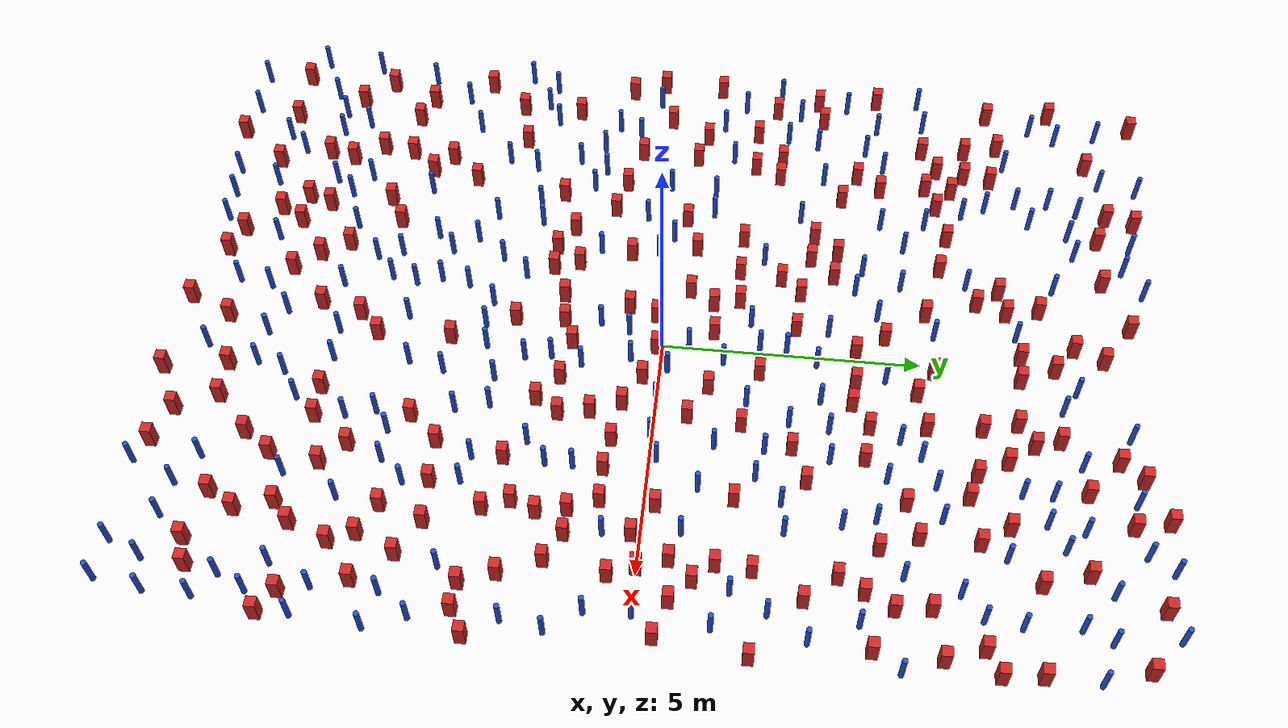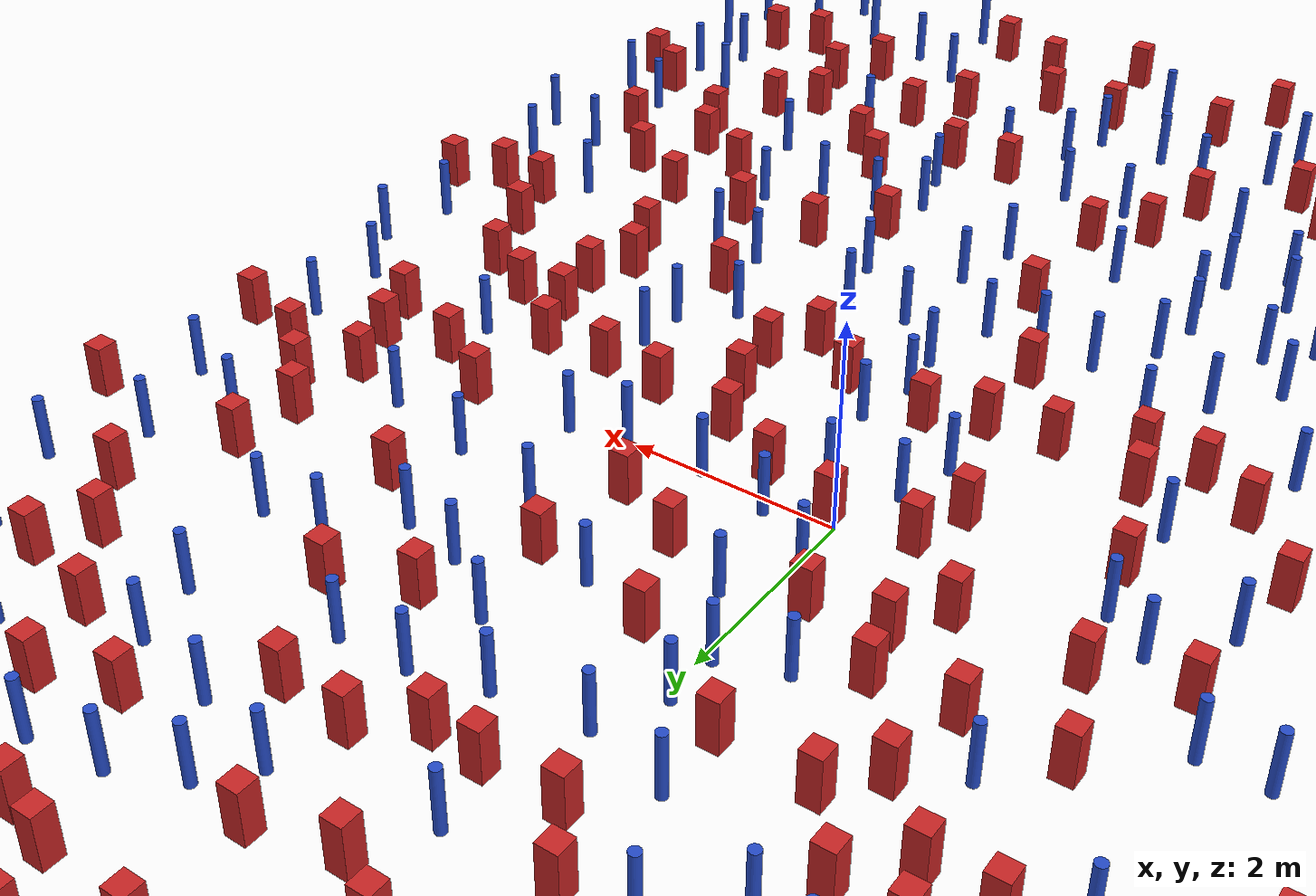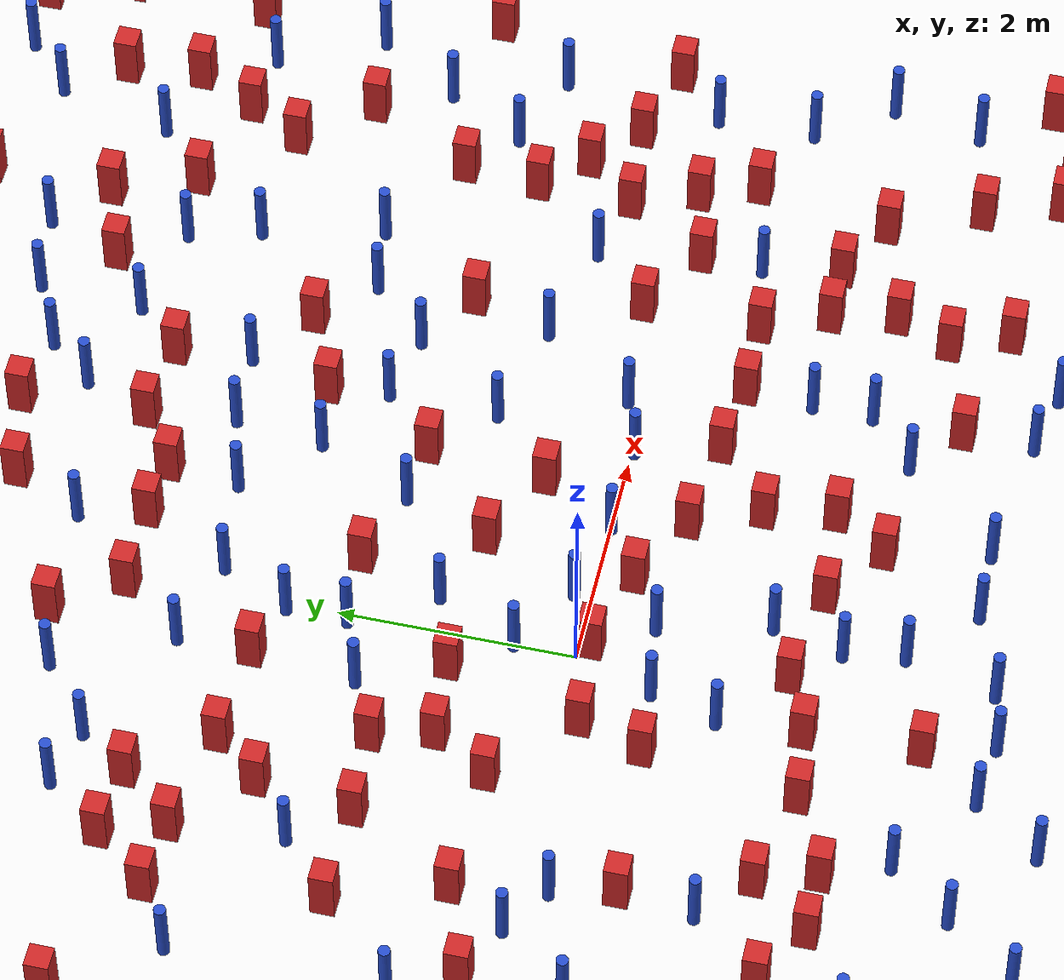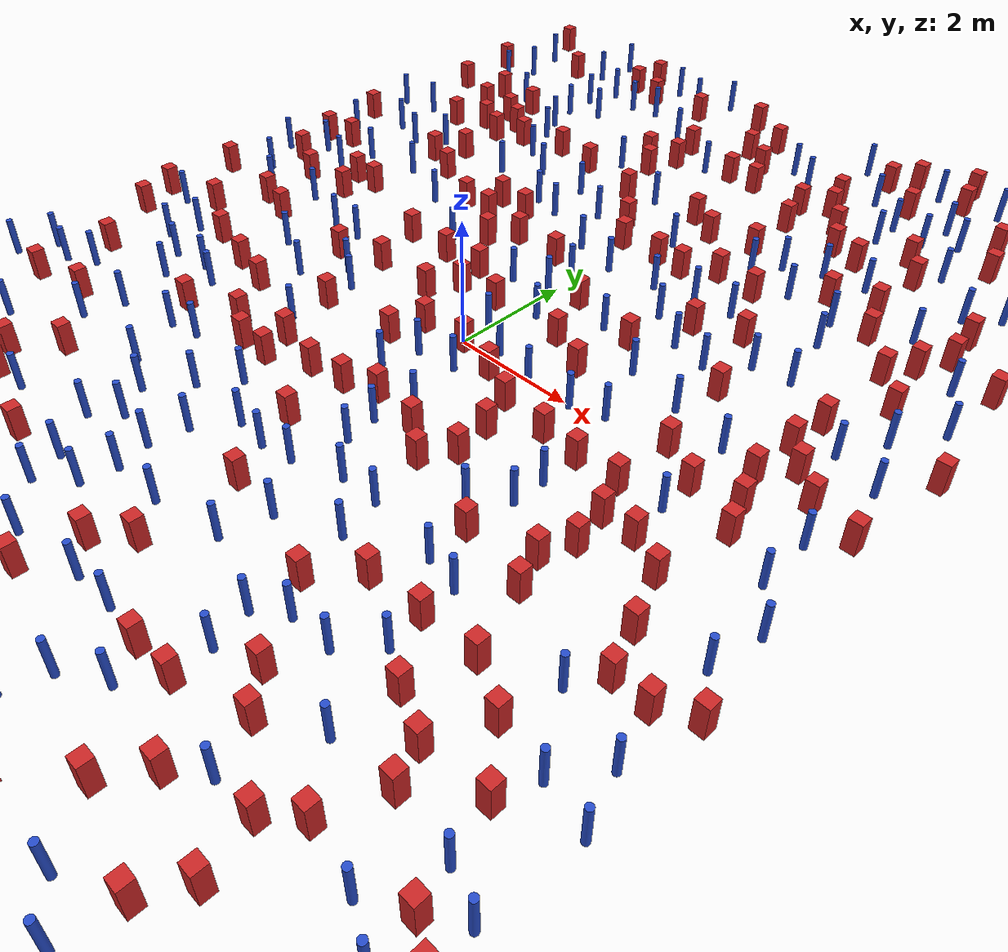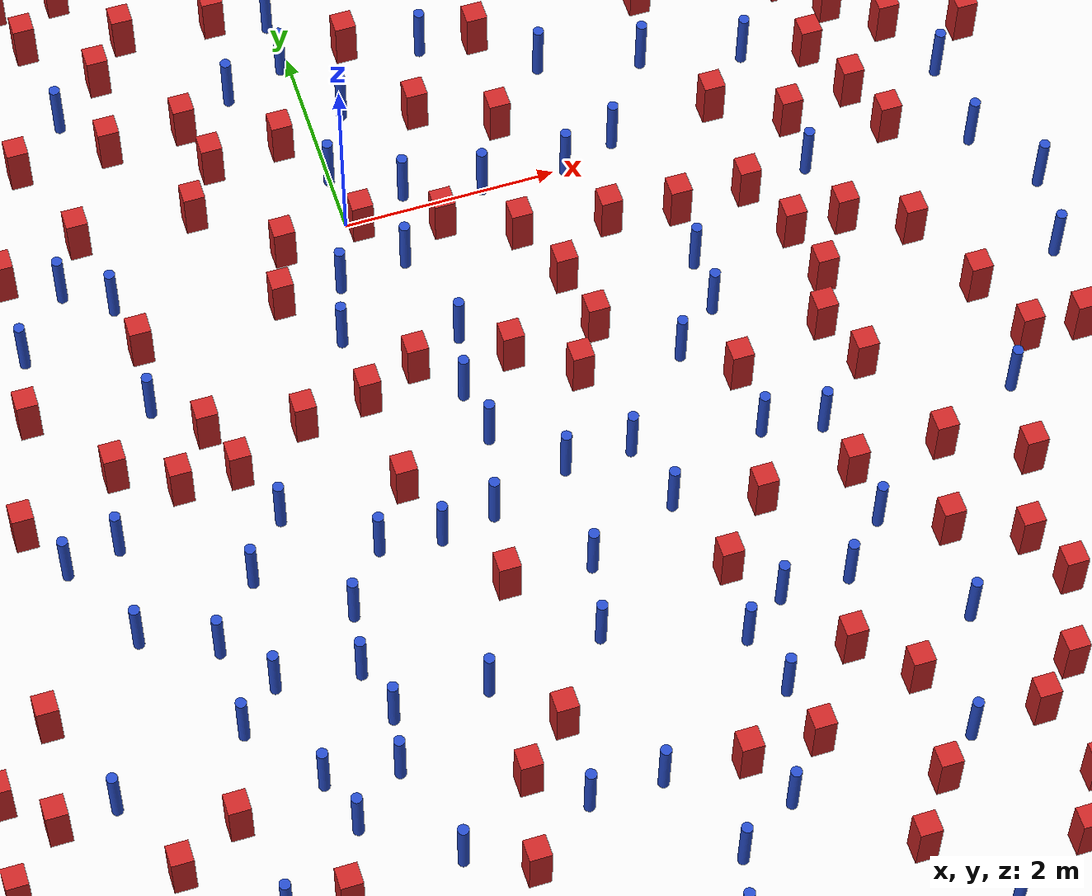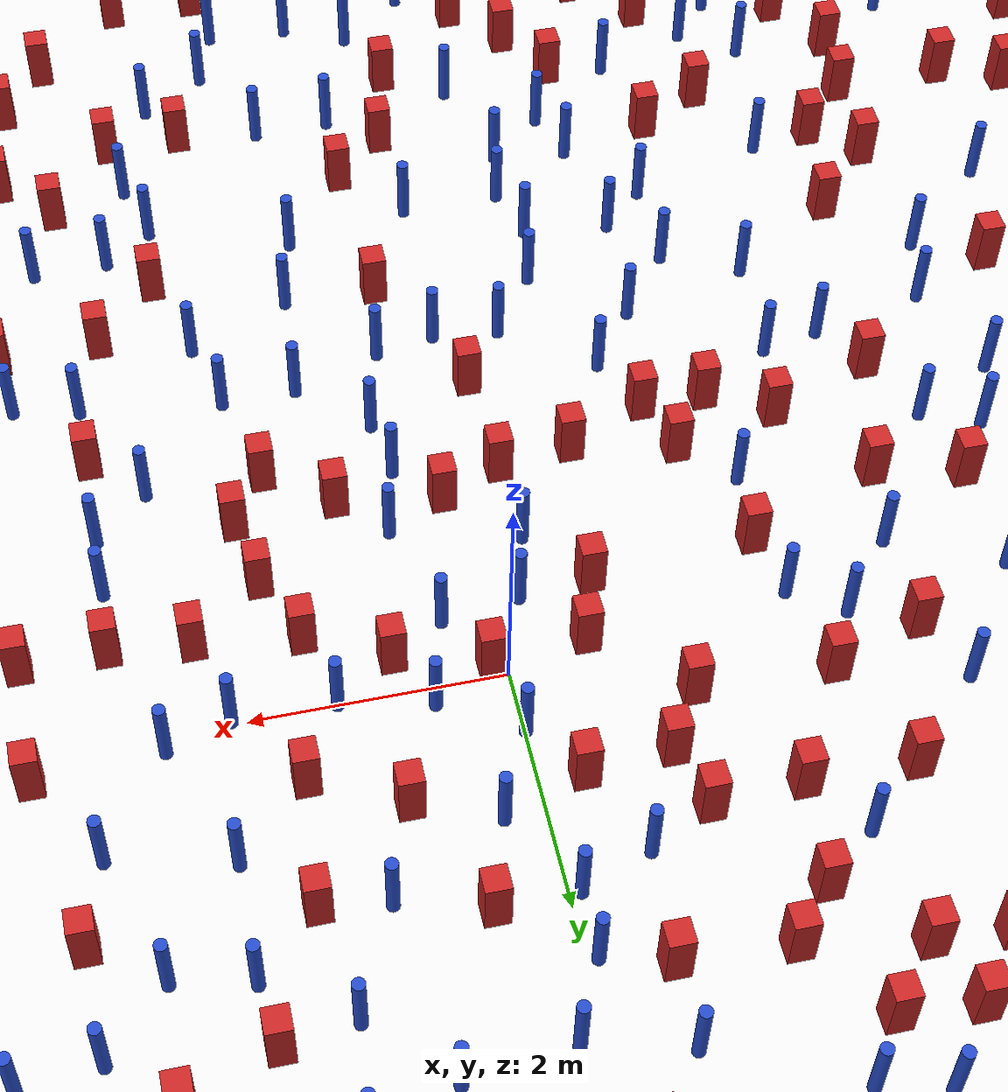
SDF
<sdf version="1.6">
  <model name="dense_10"><model name="square_post_obstacle0">
  <static>true</static>
  <pose frame="">3.85664924931 -1.35110798429 -6.11067671241e-07 -5.50515727128e-06 -8.79689657224e-07 2.37013304536e-05</pose>
  <link name="link">
    <pose frame="">0 0 0.25 0 -0 0</pose>
    <inertial>
      <mass>100</mass>
      <inertia>
        <ixx>0.166667</ixx>
        <ixy>0</ixy>
        <ixz>0</ixz>
        <iyy>0.166667</iyy>
        <iyz>0</iyz>
        <izz>0.166667</izz>
      </inertia>
    </inertial>
    <collision name="collision">
      <geometry>
        <box>
          <size>.2 .2 .5</size>
        </box>
      </geometry>
      <max_contacts>10</max_contacts>
      <surface>
        <contact>
          <ode/>
        </contact>
        <bounce/>
        <friction>
          <torsional>
            <ode/>
          </torsional>
          <ode/>
        </friction>
      </surface>
    </collision>
    <visual name="visual">
      <geometry>
        <box>
          <size>.2 .2 .5</size>
        </box>
      </geometry>
      <material>
        <script>
          <name>Gazebo/Red</name>
          <uri>file://media/materials/scripts/gazebo.material</uri>
        </script>
      </material>
    </visual>
    <self_collide>0</self_collide>
    <kinematic>0</kinematic>
  </link>
</model>
<model name="square_post_obstacle1">
  <static>true</static>
  <pose frame="">-2.25006319276 8.60352125065 -6.11067671241e-07 -5.50515727128e-06 -8.79689657224e-07 2.37013304536e-05</pose>
  <link name="link">
    <pose frame="">0 0 0.25 0 -0 0</pose>
    <inertial>
      <mass>100</mass>
      <inertia>
        <ixx>0.166667</ixx>
        <ixy>0</ixy>
        <ixz>0</ixz>
        <iyy>0.166667</iyy>
        <iyz>0</iyz>
        <izz>0.166667</izz>
      </inertia>
    </inertial>
    <collision name="collision">
      <geometry>
        <box>
          <size>.2 .2 .5</size>
        </box>
      </geometry>
      <max_contacts>10</max_contacts>
      <surface>
        <contact>
          <ode/>
        </contact>
        <bounce/>
        <friction>
          <torsional>
            <ode/>
          </torsional>
          <ode/>
        </friction>
      </surface>
    </collision>
    <visual name="visual">
      <geometry>
        <box>
          <size>.2 .2 .5</size>
        </box>
      </geometry>
      <material>
        <script>
          <name>Gazebo/Red</name>
          <uri>file://media/materials/scripts/gazebo.material</uri>
        </script>
      </material>
    </visual>
    <self_collide>0</self_collide>
    <kinematic>0</kinematic>
  </link>
</model>
<model name="pole_obstacle0">
  <static>true</static>
  <pose frame="">3.98373473094 -5.58413356857 -9.47619616065e-06 5.49618799737e-07 2.36310414049e-07 -1.55090534808e-07</pose>
  <link name="link">
  <pose frame="">0 0 0.3 0 -0 0</pose>
    <inertial>
      <mass>1</mass>
      <inertia>
        <ixx>0.145833</ixx>
        <ixy>0</ixy>
        <ixz>0</ixz>
        <iyy>0.145833</iyy>
        <iyz>0</iyz>
        <izz>0.125</izz>
      </inertia>
    </inertial>
    <collision name="collision">
      <geometry>
        <cylinder>
          <radius>0.05</radius>
          <length>.6</length>
        </cylinder>
      </geometry>
      <max_contacts>10</max_contacts>
      <surface>
        <contact>
          <ode/>
        </contact>
        <bounce/>
        <friction>
          <torsional>
            <ode/>
          </torsional>
          <ode/>
        </friction>
      </surface>
    </collision>
    <visual name="visual">
      <geometry>
        <cylinder>
          <radius>0.05</radius>
          <length>.6</length>
        </cylinder>
      </geometry>
      <material>
        <script>
          <name>Gazebo/Blue</name>
          <uri>file://media/materials/scripts/gazebo.material</uri>
        </script>
      </material>
    </visual>
    <self_collide>0</self_collide>
    <kinematic>0</kinematic>
  </link>
</model>
<model name="square_post_obstacle2">
  <static>true</static>
  <pose frame="">0.250513682666 -4.11125388289 -6.11067671241e-07 -5.50515727128e-06 -8.79689657224e-07 2.37013304536e-05</pose>
  <link name="link">
    <pose frame="">0 0 0.25 0 -0 0</pose>
    <inertial>
      <mass>100</mass>
      <inertia>
        <ixx>0.166667</ixx>
        <ixy>0</ixy>
        <ixz>0</ixz>
        <iyy>0.166667</iyy>
        <iyz>0</iyz>
        <izz>0.166667</izz>
      </inertia>
    </inertial>
    <collision name="collision">
      <geometry>
        <box>
          <size>.2 .2 .5</size>
        </box>
      </geometry>
      <max_contacts>10</max_contacts>
      <surface>
        <contact>
          <ode/>
        </contact>
        <bounce/>
        <friction>
          <torsional>
            <ode/>
          </torsional>
          <ode/>
        </friction>
      </surface>
    </collision>
    <visual name="visual">
      <geometry>
        <box>
          <size>.2 .2 .5</size>
        </box>
      </geometry>
      <material>
        <script>
          <name>Gazebo/Red</name>
          <uri>file://media/materials/scripts/gazebo.material</uri>
        </script>
      </material>
    </visual>
    <self_collide>0</self_collide>
    <kinematic>0</kinematic>
  </link>
</model>
<model name="pole_obstacle1">
  <static>true</static>
  <pose frame="">5.41597815351 -6.45563840536 -9.47619616065e-06 5.49618799737e-07 2.36310414037e-07 -1.55090534814e-07</pose>
  <link name="link">
  <pose frame="">0 0 0.3 0 -0 0</pose>
    <inertial>
      <mass>1</mass>
      <inertia>
        <ixx>0.145833</ixx>
        <ixy>0</ixy>
        <ixz>0</ixz>
        <iyy>0.145833</iyy>
        <iyz>0</iyz>
        <izz>0.125</izz>
      </inertia>
    </inertial>
    <collision name="collision">
      <geometry>
        <cylinder>
          <radius>0.05</radius>
          <length>.6</length>
        </cylinder>
      </geometry>
      <max_contacts>10</max_contacts>
      <surface>
        <contact>
          <ode/>
        </contact>
        <bounce/>
        <friction>
          <torsional>
            <ode/>
          </torsional>
          <ode/>
        </friction>
      </surface>
    </collision>
    <visual name="visual">
      <geometry>
        <cylinder>
          <radius>0.05</radius>
          <length>.6</length>
        </cylinder>
      </geometry>
      <material>
        <script>
          <name>Gazebo/Blue</name>
          <uri>file://media/materials/scripts/gazebo.material</uri>
        </script>
      </material>
    </visual>
    <self_collide>0</self_collide>
    <kinematic>0</kinematic>
  </link>
</model>
<model name="square_post_obstacle3">
  <static>true</static>
  <pose frame="">-4.47341530026 5.08891844181 -6.11067671241e-07 -5.50515727128e-06 -8.79689657224e-07 2.37013304536e-05</pose>
  <link name="link">
    <pose frame="">0 0 0.25 0 -0 0</pose>
    <inertial>
      <mass>100</mass>
      <inertia>
        <ixx>0.166667</ixx>
        <ixy>0</ixy>
        <ixz>0</ixz>
        <iyy>0.166667</iyy>
        <iyz>0</iyz>
        <izz>0.166667</izz>
      </inertia>
    </inertial>
    <collision name="collision">
      <geometry>
        <box>
          <size>.2 .2 .5</size>
        </box>
      </geometry>
      <max_contacts>10</max_contacts>
      <surface>
        <contact>
          <ode/>
        </contact>
        <bounce/>
        <friction>
          <torsional>
            <ode/>
          </torsional>
          <ode/>
        </friction>
      </surface>
    </collision>
    <visual name="visual">
      <geometry>
        <box>
          <size>.2 .2 .5</size>
        </box>
      </geometry>
      <material>
        <script>
          <name>Gazebo/Red</name>
          <uri>file://media/materials/scripts/gazebo.material</uri>
        </script>
      </material>
    </visual>
    <self_collide>0</self_collide>
    <kinematic>0</kinematic>
  </link>
</model>
<model name="pole_obstacle2">
  <static>true</static>
  <pose frame="">2.89271784255 -3.2723165584 -9.47619616065e-06 5.49618799737e-07 2.36310414051e-07 -1.55090534807e-07</pose>
  <link name="link">
  <pose frame="">0 0 0.3 0 -0 0</pose>
    <inertial>
      <mass>1</mass>
      <inertia>
        <ixx>0.145833</ixx>
        <ixy>0</ixy>
        <ixz>0</ixz>
        <iyy>0.145833</iyy>
        <iyz>0</iyz>
        <izz>0.125</izz>
      </inertia>
    </inertial>
    <collision name="collision">
      <geometry>
        <cylinder>
          <radius>0.05</radius>
          <length>.6</length>
        </cylinder>
      </geometry>
      <max_contacts>10</max_contacts>
      <surface>
        <contact>
          <ode/>
        </contact>
        <bounce/>
        <friction>
          <torsional>
            <ode/>
          </torsional>
          <ode/>
        </friction>
      </surface>
    </collision>
    <visual name="visual">
      <geometry>
        <cylinder>
          <radius>0.05</radius>
          <length>.6</length>
        </cylinder>
      </geometry>
      <material>
        <script>
          <name>Gazebo/Blue</name>
          <uri>file://media/materials/scripts/gazebo.material</uri>
        </script>
      </material>
    </visual>
    <self_collide>0</self_collide>
    <kinematic>0</kinematic>
  </link>
</model>
<model name="pole_obstacle3">
  <static>true</static>
  <pose frame="">5.82433210495 -0.820208109112 -9.47619616065e-06 5.49618799737e-07 2.36310414061e-07 -1.550905348e-07</pose>
  <link name="link">
  <pose frame="">0 0 0.3 0 -0 0</pose>
    <inertial>
      <mass>1</mass>
      <inertia>
        <ixx>0.145833</ixx>
        <ixy>0</ixy>
        <ixz>0</ixz>
        <iyy>0.145833</iyy>
        <iyz>0</iyz>
        <izz>0.125</izz>
      </inertia>
    </inertial>
    <collision name="collision">
      <geometry>
        <cylinder>
          <radius>0.05</radius>
          <length>.6</length>
        </cylinder>
      </geometry>
      <max_contacts>10</max_contacts>
      <surface>
        <contact>
          <ode/>
        </contact>
        <bounce/>
        <friction>
          <torsional>
            <ode/>
          </torsional>
          <ode/>
        </friction>
      </surface>
    </collision>
    <visual name="visual">
      <geometry>
        <cylinder>
          <radius>0.05</radius>
          <length>.6</length>
        </cylinder>
      </geometry>
      <material>
        <script>
          <name>Gazebo/Blue</name>
          <uri>file://media/materials/scripts/gazebo.material</uri>
        </script>
      </material>
    </visual>
    <self_collide>0</self_collide>
    <kinematic>0</kinematic>
  </link>
</model>
<model name="square_post_obstacle4">
  <static>true</static>
  <pose frame="">-0.0432336182488 7.56572862312 -6.11067671241e-07 -5.50515727128e-06 -8.79689657224e-07 2.37013304536e-05</pose>
  <link name="link">
    <pose frame="">0 0 0.25 0 -0 0</pose>
    <inertial>
      <mass>100</mass>
      <inertia>
        <ixx>0.166667</ixx>
        <ixy>0</ixy>
        <ixz>0</ixz>
        <iyy>0.166667</iyy>
        <iyz>0</iyz>
        <izz>0.166667</izz>
      </inertia>
    </inertial>
    <collision name="collision">
      <geometry>
        <box>
          <size>.2 .2 .5</size>
        </box>
      </geometry>
      <max_contacts>10</max_contacts>
      <surface>
        <contact>
          <ode/>
        </contact>
        <bounce/>
        <friction>
          <torsional>
            <ode/>
          </torsional>
          <ode/>
        </friction>
      </surface>
    </collision>
    <visual name="visual">
      <geometry>
        <box>
          <size>.2 .2 .5</size>
        </box>
      </geometry>
      <material>
        <script>
          <name>Gazebo/Red</name>
          <uri>file://media/materials/scripts/gazebo.material</uri>
        </script>
      </material>
    </visual>
    <self_collide>0</self_collide>
    <kinematic>0</kinematic>
  </link>
</model>
<model name="square_post_obstacle5">
  <static>true</static>
  <pose frame="">-1.02708775562 0.930661473114 -6.11067671241e-07 -5.50515727128e-06 -8.79689657224e-07 2.37013304536e-05</pose>
  <link name="link">
    <pose frame="">0 0 0.25 0 -0 0</pose>
    <inertial>
      <mass>100</mass>
      <inertia>
        <ixx>0.166667</ixx>
        <ixy>0</ixy>
        <ixz>0</ixz>
        <iyy>0.166667</iyy>
        <iyz>0</iyz>
        <izz>0.166667</izz>
      </inertia>
    </inertial>
    <collision name="collision">
      <geometry>
        <box>
          <size>.2 .2 .5</size>
        </box>
      </geometry>
      <max_contacts>10</max_contacts>
      <surface>
        <contact>
          <ode/>
        </contact>
        <bounce/>
        <friction>
          <torsional>
            <ode/>
          </torsional>
          <ode/>
        </friction>
      </surface>
    </collision>
    <visual name="visual">
      <geometry>
        <box>
          <size>.2 .2 .5</size>
        </box>
      </geometry>
      <material>
        <script>
          <name>Gazebo/Red</name>
          <uri>file://media/materials/scripts/gazebo.material</uri>
        </script>
      </material>
    </visual>
    <self_collide>0</self_collide>
    <kinematic>0</kinematic>
  </link>
</model>
<model name="square_post_obstacle6">
  <static>true</static>
  <pose frame="">1.28458814506 -8.26511067671 -6.11067671241e-07 -5.50515727128e-06 -8.79689657224e-07 2.37013304536e-05</pose>
  <link name="link">
    <pose frame="">0 0 0.25 0 -0 0</pose>
    <inertial>
      <mass>100</mass>
      <inertia>
        <ixx>0.166667</ixx>
        <ixy>0</ixy>
        <ixz>0</ixz>
        <iyy>0.166667</iyy>
        <iyz>0</iyz>
        <izz>0.166667</izz>
      </inertia>
    </inertial>
    <collision name="collision">
      <geometry>
        <box>
          <size>.2 .2 .5</size>
        </box>
      </geometry>
      <max_contacts>10</max_contacts>
      <surface>
        <contact>
          <ode/>
        </contact>
        <bounce/>
        <friction>
          <torsional>
            <ode/>
          </torsional>
          <ode/>
        </friction>
      </surface>
    </collision>
    <visual name="visual">
      <geometry>
        <box>
          <size>.2 .2 .5</size>
        </box>
      </geometry>
      <material>
        <script>
          <name>Gazebo/Red</name>
          <uri>file://media/materials/scripts/gazebo.material</uri>
        </script>
      </material>
    </visual>
    <self_collide>0</self_collide>
    <kinematic>0</kinematic>
  </link>
</model>
<model name="pole_obstacle4">
  <static>true</static>
  <pose frame="">6.03136823341 3.07508010178 -9.47619616065e-06 5.49618799738e-07 2.36310414051e-07 -1.55090534805e-07</pose>
  <link name="link">
  <pose frame="">0 0 0.3 0 -0 0</pose>
    <inertial>
      <mass>1</mass>
      <inertia>
        <ixx>0.145833</ixx>
        <ixy>0</ixy>
        <ixz>0</ixz>
        <iyy>0.145833</iyy>
        <iyz>0</iyz>
        <izz>0.125</izz>
      </inertia>
    </inertial>
    <collision name="collision">
      <geometry>
        <cylinder>
          <radius>0.05</radius>
          <length>.6</length>
        </cylinder>
      </geometry>
      <max_contacts>10</max_contacts>
      <surface>
        <contact>
          <ode/>
        </contact>
        <bounce/>
        <friction>
          <torsional>
            <ode/>
          </torsional>
          <ode/>
        </friction>
      </surface>
    </collision>
    <visual name="visual">
      <geometry>
        <cylinder>
          <radius>0.05</radius>
          <length>.6</length>
        </cylinder>
      </geometry>
      <material>
        <script>
          <name>Gazebo/Blue</name>
          <uri>file://media/materials/scripts/gazebo.material</uri>
        </script>
      </material>
    </visual>
    <self_collide>0</self_collide>
    <kinematic>0</kinematic>
  </link>
</model>
<model name="pole_obstacle5">
  <static>true</static>
  <pose frame="">4.65320959978 -8.65904795479 -9.47619616065e-06 5.49618799737e-07 2.36310414065e-07 -1.55090534796e-07</pose>
  <link name="link">
  <pose frame="">0 0 0.3 0 -0 0</pose>
    <inertial>
      <mass>1</mass>
      <inertia>
        <ixx>0.145833</ixx>
        <ixy>0</ixy>
        <ixz>0</ixz>
        <iyy>0.145833</iyy>
        <iyz>0</iyz>
        <izz>0.125</izz>
      </inertia>
    </inertial>
    <collision name="collision">
      <geometry>
        <cylinder>
          <radius>0.05</radius>
          <length>.6</length>
        </cylinder>
      </geometry>
      <max_contacts>10</max_contacts>
      <surface>
        <contact>
          <ode/>
        </contact>
        <bounce/>
        <friction>
          <torsional>
            <ode/>
          </torsional>
          <ode/>
        </friction>
      </surface>
    </collision>
    <visual name="visual">
      <geometry>
        <cylinder>
          <radius>0.05</radius>
          <length>.6</length>
        </cylinder>
      </geometry>
      <material>
        <script>
          <name>Gazebo/Blue</name>
          <uri>file://media/materials/scripts/gazebo.material</uri>
        </script>
      </material>
    </visual>
    <self_collide>0</self_collide>
    <kinematic>0</kinematic>
  </link>
</model>
<model name="square_post_obstacle7">
  <static>true</static>
  <pose frame="">-4.02804060044 -5.23831961809 -6.11067671241e-07 -5.50515727128e-06 -8.79689657224e-07 2.37013304536e-05</pose>
  <link name="link">
    <pose frame="">0 0 0.25 0 -0 0</pose>
    <inertial>
      <mass>100</mass>
      <inertia>
        <ixx>0.166667</ixx>
        <ixy>0</ixy>
        <ixz>0</ixz>
        <iyy>0.166667</iyy>
        <iyz>0</iyz>
        <izz>0.166667</izz>
      </inertia>
    </inertial>
    <collision name="collision">
      <geometry>
        <box>
          <size>.2 .2 .5</size>
        </box>
      </geometry>
      <max_contacts>10</max_contacts>
      <surface>
        <contact>
          <ode/>
        </contact>
        <bounce/>
        <friction>
          <torsional>
            <ode/>
          </torsional>
          <ode/>
        </friction>
      </surface>
    </collision>
    <visual name="visual">
      <geometry>
        <box>
          <size>.2 .2 .5</size>
        </box>
      </geometry>
      <material>
        <script>
          <name>Gazebo/Red</name>
          <uri>file://media/materials/scripts/gazebo.material</uri>
        </script>
      </material>
    </visual>
    <self_collide>0</self_collide>
    <kinematic>0</kinematic>
  </link>
</model>
<model name="square_post_obstacle8">
  <static>true</static>
  <pose frame="">2.43546642392 6.04167440104 -6.11067671241e-07 -5.50515727128e-06 -8.79689657224e-07 2.37013304536e-05</pose>
  <link name="link">
    <pose frame="">0 0 0.25 0 -0 0</pose>
    <inertial>
      <mass>100</mass>
      <inertia>
        <ixx>0.166667</ixx>
        <ixy>0</ixy>
        <ixz>0</ixz>
        <iyy>0.166667</iyy>
        <iyz>0</iyz>
        <izz>0.166667</izz>
      </inertia>
    </inertial>
    <collision name="collision">
      <geometry>
        <box>
          <size>.2 .2 .5</size>
        </box>
      </geometry>
      <max_contacts>10</max_contacts>
      <surface>
        <contact>
          <ode/>
        </contact>
        <bounce/>
        <friction>
          <torsional>
            <ode/>
          </torsional>
          <ode/>
        </friction>
      </surface>
    </collision>
    <visual name="visual">
      <geometry>
        <box>
          <size>.2 .2 .5</size>
        </box>
      </geometry>
      <material>
        <script>
          <name>Gazebo/Red</name>
          <uri>file://media/materials/scripts/gazebo.material</uri>
        </script>
      </material>
    </visual>
    <self_collide>0</self_collide>
    <kinematic>0</kinematic>
  </link>
</model>
<model name="pole_obstacle6">
  <static>true</static>
  <pose frame="">-6.9229522516 -6.95452196529 -9.47619616065e-06 5.49618799737e-07 2.36310414037e-07 -1.55090534814e-07</pose>
  <link name="link">
  <pose frame="">0 0 0.3 0 -0 0</pose>
    <inertial>
      <mass>1</mass>
      <inertia>
        <ixx>0.145833</ixx>
        <ixy>0</ixy>
        <ixz>0</ixz>
        <iyy>0.145833</iyy>
        <iyz>0</iyz>
        <izz>0.125</izz>
      </inertia>
    </inertial>
    <collision name="collision">
      <geometry>
        <cylinder>
          <radius>0.05</radius>
          <length>.6</length>
        </cylinder>
      </geometry>
      <max_contacts>10</max_contacts>
      <surface>
        <contact>
          <ode/>
        </contact>
        <bounce/>
        <friction>
          <torsional>
            <ode/>
          </torsional>
          <ode/>
        </friction>
      </surface>
    </collision>
    <visual name="visual">
      <geometry>
        <cylinder>
          <radius>0.05</radius>
          <length>.6</length>
        </cylinder>
      </geometry>
      <material>
        <script>
          <name>Gazebo/Blue</name>
          <uri>file://media/materials/scripts/gazebo.material</uri>
        </script>
      </material>
    </visual>
    <self_collide>0</self_collide>
    <kinematic>0</kinematic>
  </link>
</model>
<model name="pole_obstacle7">
  <static>true</static>
  <pose frame="">4.10637829773 6.53729007636 -9.47619616065e-06 5.49618799737e-07 2.36310414037e-07 -1.55090534814e-07</pose>
  <link name="link">
  <pose frame="">0 0 0.3 0 -0 0</pose>
    <inertial>
      <mass>1</mass>
      <inertia>
        <ixx>0.145833</ixx>
        <ixy>0</ixy>
        <ixz>0</ixz>
        <iyy>0.145833</iyy>
        <iyz>0</iyz>
        <izz>0.125</izz>
      </inertia>
    </inertial>
    <collision name="collision">
      <geometry>
        <cylinder>
          <radius>0.05</radius>
          <length>.6</length>
        </cylinder>
      </geometry>
      <max_contacts>10</max_contacts>
      <surface>
        <contact>
          <ode/>
        </contact>
        <bounce/>
        <friction>
          <torsional>
            <ode/>
          </torsional>
          <ode/>
        </friction>
      </surface>
    </collision>
    <visual name="visual">
      <geometry>
        <cylinder>
          <radius>0.05</radius>
          <length>.6</length>
        </cylinder>
      </geometry>
      <material>
        <script>
          <name>Gazebo/Blue</name>
          <uri>file://media/materials/scripts/gazebo.material</uri>
        </script>
      </material>
    </visual>
    <self_collide>0</self_collide>
    <kinematic>0</kinematic>
  </link>
</model>
<model name="square_post_obstacle9">
  <static>true</static>
  <pose frame="">5.49992778663 0.636190954281 -6.11067671241e-07 -5.50515727128e-06 -8.79689657224e-07 2.37013304536e-05</pose>
  <link name="link">
    <pose frame="">0 0 0.25 0 -0 0</pose>
    <inertial>
      <mass>100</mass>
      <inertia>
        <ixx>0.166667</ixx>
        <ixy>0</ixy>
        <ixz>0</ixz>
        <iyy>0.166667</iyy>
        <iyz>0</iyz>
        <izz>0.166667</izz>
      </inertia>
    </inertial>
    <collision name="collision">
      <geometry>
        <box>
          <size>.2 .2 .5</size>
        </box>
      </geometry>
      <max_contacts>10</max_contacts>
      <surface>
        <contact>
          <ode/>
        </contact>
        <bounce/>
        <friction>
          <torsional>
            <ode/>
          </torsional>
          <ode/>
        </friction>
      </surface>
    </collision>
    <visual name="visual">
      <geometry>
        <box>
          <size>.2 .2 .5</size>
        </box>
      </geometry>
      <material>
        <script>
          <name>Gazebo/Red</name>
          <uri>file://media/materials/scripts/gazebo.material</uri>
        </script>
      </material>
    </visual>
    <self_collide>0</self_collide>
    <kinematic>0</kinematic>
  </link>
</model>
<model name="square_post_obstacle10">
  <static>true</static>
  <pose frame="">3.7774740106 -2.39067848591 -6.11067671241e-07 -5.50515727128e-06 -8.79689657224e-07 2.37013304536e-05</pose>
  <link name="link">
    <pose frame="">0 0 0.25 0 -0 0</pose>
    <inertial>
      <mass>100</mass>
      <inertia>
        <ixx>0.166667</ixx>
        <ixy>0</ixy>
        <ixz>0</ixz>
        <iyy>0.166667</iyy>
        <iyz>0</iyz>
        <izz>0.166667</izz>
      </inertia>
    </inertial>
    <collision name="collision">
      <geometry>
        <box>
          <size>.2 .2 .5</size>
        </box>
      </geometry>
      <max_contacts>10</max_contacts>
      <surface>
        <contact>
          <ode/>
        </contact>
        <bounce/>
        <friction>
          <torsional>
            <ode/>
          </torsional>
          <ode/>
        </friction>
      </surface>
    </collision>
    <visual name="visual">
      <geometry>
        <box>
          <size>.2 .2 .5</size>
        </box>
      </geometry>
      <material>
        <script>
          <name>Gazebo/Red</name>
          <uri>file://media/materials/scripts/gazebo.material</uri>
        </script>
      </material>
    </visual>
    <self_collide>0</self_collide>
    <kinematic>0</kinematic>
  </link>
</model>
<model name="square_post_obstacle11">
  <static>true</static>
  <pose frame="">4.42478634536 -7.35460168713 -6.11067671241e-07 -5.50515727128e-06 -8.79689657224e-07 2.37013304536e-05</pose>
  <link name="link">
    <pose frame="">0 0 0.25 0 -0 0</pose>
    <inertial>
      <mass>100</mass>
      <inertia>
        <ixx>0.166667</ixx>
        <ixy>0</ixy>
        <ixz>0</ixz>
        <iyy>0.166667</iyy>
        <iyz>0</iyz>
        <izz>0.166667</izz>
      </inertia>
    </inertial>
    <collision name="collision">
      <geometry>
        <box>
          <size>.2 .2 .5</size>
        </box>
      </geometry>
      <max_contacts>10</max_contacts>
      <surface>
        <contact>
          <ode/>
        </contact>
        <bounce/>
        <friction>
          <torsional>
            <ode/>
          </torsional>
          <ode/>
        </friction>
      </surface>
    </collision>
    <visual name="visual">
      <geometry>
        <box>
          <size>.2 .2 .5</size>
        </box>
      </geometry>
      <material>
        <script>
          <name>Gazebo/Red</name>
          <uri>file://media/materials/scripts/gazebo.material</uri>
        </script>
      </material>
    </visual>
    <self_collide>0</self_collide>
    <kinematic>0</kinematic>
  </link>
</model>
<model name="square_post_obstacle12">
  <static>true</static>
  <pose frame="">-1.78063560245 2.22780262539 -6.11067671241e-07 -5.50515727128e-06 -8.79689657224e-07 2.37013304536e-05</pose>
  <link name="link">
    <pose frame="">0 0 0.25 0 -0 0</pose>
    <inertial>
      <mass>100</mass>
      <inertia>
        <ixx>0.166667</ixx>
        <ixy>0</ixy>
        <ixz>0</ixz>
        <iyy>0.166667</iyy>
        <iyz>0</iyz>
        <izz>0.166667</izz>
      </inertia>
    </inertial>
    <collision name="collision">
      <geometry>
        <box>
          <size>.2 .2 .5</size>
        </box>
      </geometry>
      <max_contacts>10</max_contacts>
      <surface>
        <contact>
          <ode/>
        </contact>
        <bounce/>
        <friction>
          <torsional>
            <ode/>
          </torsional>
          <ode/>
        </friction>
      </surface>
    </collision>
    <visual name="visual">
      <geometry>
        <box>
          <size>.2 .2 .5</size>
        </box>
      </geometry>
      <material>
        <script>
          <name>Gazebo/Red</name>
          <uri>file://media/materials/scripts/gazebo.material</uri>
        </script>
      </material>
    </visual>
    <self_collide>0</self_collide>
    <kinematic>0</kinematic>
  </link>
</model>
<model name="square_post_obstacle13">
  <static>true</static>
  <pose frame="">1.65896226514 -6.36618169811 -6.11067671241e-07 -5.50515727128e-06 -8.79689657224e-07 2.37013304536e-05</pose>
  <link name="link">
    <pose frame="">0 0 0.25 0 -0 0</pose>
    <inertial>
      <mass>100</mass>
      <inertia>
        <ixx>0.166667</ixx>
        <ixy>0</ixy>
        <ixz>0</ixz>
        <iyy>0.166667</iyy>
        <iyz>0</iyz>
        <izz>0.166667</izz>
      </inertia>
    </inertial>
    <collision name="collision">
      <geometry>
        <box>
          <size>.2 .2 .5</size>
        </box>
      </geometry>
      <max_contacts>10</max_contacts>
      <surface>
        <contact>
          <ode/>
        </contact>
        <bounce/>
        <friction>
          <torsional>
            <ode/>
          </torsional>
          <ode/>
        </friction>
      </surface>
    </collision>
    <visual name="visual">
      <geometry>
        <box>
          <size>.2 .2 .5</size>
        </box>
      </geometry>
      <material>
        <script>
          <name>Gazebo/Red</name>
          <uri>file://media/materials/scripts/gazebo.material</uri>
        </script>
      </material>
    </visual>
    <self_collide>0</self_collide>
    <kinematic>0</kinematic>
  </link>
</model>
<model name="pole_obstacle8">
  <static>true</static>
  <pose frame="">0.84453395597 -8.79842746711 -9.47619616065e-06 5.49618799737e-07 2.36310414038e-07 -1.55090534813e-07</pose>
  <link name="link">
  <pose frame="">0 0 0.3 0 -0 0</pose>
    <inertial>
      <mass>1</mass>
      <inertia>
        <ixx>0.145833</ixx>
        <ixy>0</ixy>
        <ixz>0</ixz>
        <iyy>0.145833</iyy>
        <iyz>0</iyz>
        <izz>0.125</izz>
      </inertia>
    </inertial>
    <collision name="collision">
      <geometry>
        <cylinder>
          <radius>0.05</radius>
          <length>.6</length>
        </cylinder>
      </geometry>
      <max_contacts>10</max_contacts>
      <surface>
        <contact>
          <ode/>
        </contact>
        <bounce/>
        <friction>
          <torsional>
            <ode/>
          </torsional>
          <ode/>
        </friction>
      </surface>
    </collision>
    <visual name="visual">
      <geometry>
        <cylinder>
          <radius>0.05</radius>
          <length>.6</length>
        </cylinder>
      </geometry>
      <material>
        <script>
          <name>Gazebo/Blue</name>
          <uri>file://media/materials/scripts/gazebo.material</uri>
        </script>
      </material>
    </visual>
    <self_collide>0</self_collide>
    <kinematic>0</kinematic>
  </link>
</model>
<model name="square_post_obstacle14">
  <static>true</static>
  <pose frame="">-6.90483712652 4.03889079188 -6.11067671241e-07 -5.50515727128e-06 -8.79689657224e-07 2.37013304536e-05</pose>
  <link name="link">
    <pose frame="">0 0 0.25 0 -0 0</pose>
    <inertial>
      <mass>100</mass>
      <inertia>
        <ixx>0.166667</ixx>
        <ixy>0</ixy>
        <ixz>0</ixz>
        <iyy>0.166667</iyy>
        <iyz>0</iyz>
        <izz>0.166667</izz>
      </inertia>
    </inertial>
    <collision name="collision">
      <geometry>
        <box>
          <size>.2 .2 .5</size>
        </box>
      </geometry>
      <max_contacts>10</max_contacts>
      <surface>
        <contact>
          <ode/>
        </contact>
        <bounce/>
        <friction>
          <torsional>
            <ode/>
          </torsional>
          <ode/>
        </friction>
      </surface>
    </collision>
    <visual name="visual">
      <geometry>
        <box>
          <size>.2 .2 .5</size>
        </box>
      </geometry>
      <material>
        <script>
          <name>Gazebo/Red</name>
          <uri>file://media/materials/scripts/gazebo.material</uri>
        </script>
      </material>
    </visual>
    <self_collide>0</self_collide>
    <kinematic>0</kinematic>
  </link>
</model>
<model name="square_post_obstacle15">
  <static>true</static>
  <pose frame="">-2.41324345539 0.481723105533 -6.11067671241e-07 -5.50515727128e-06 -8.79689657224e-07 2.37013304536e-05</pose>
  <link name="link">
    <pose frame="">0 0 0.25 0 -0 0</pose>
    <inertial>
      <mass>100</mass>
      <inertia>
        <ixx>0.166667</ixx>
        <ixy>0</ixy>
        <ixz>0</ixz>
        <iyy>0.166667</iyy>
        <iyz>0</iyz>
        <izz>0.166667</izz>
      </inertia>
    </inertial>
    <collision name="collision">
      <geometry>
        <box>
          <size>.2 .2 .5</size>
        </box>
      </geometry>
      <max_contacts>10</max_contacts>
      <surface>
        <contact>
          <ode/>
        </contact>
        <bounce/>
        <friction>
          <torsional>
            <ode/>
          </torsional>
          <ode/>
        </friction>
      </surface>
    </collision>
    <visual name="visual">
      <geometry>
        <box>
          <size>.2 .2 .5</size>
        </box>
      </geometry>
      <material>
        <script>
          <name>Gazebo/Red</name>
          <uri>file://media/materials/scripts/gazebo.material</uri>
        </script>
      </material>
    </visual>
    <self_collide>0</self_collide>
    <kinematic>0</kinematic>
  </link>
</model>
<model name="square_post_obstacle16">
  <static>true</static>
  <pose frame="">2.29833616412 -0.73261602999 -6.11067671241e-07 -5.50515727128e-06 -8.79689657224e-07 2.37013304536e-05</pose>
  <link name="link">
    <pose frame="">0 0 0.25 0 -0 0</pose>
    <inertial>
      <mass>100</mass>
      <inertia>
        <ixx>0.166667</ixx>
        <ixy>0</ixy>
        <ixz>0</ixz>
        <iyy>0.166667</iyy>
        <iyz>0</iyz>
        <izz>0.166667</izz>
      </inertia>
    </inertial>
    <collision name="collision">
      <geometry>
        <box>
          <size>.2 .2 .5</size>
        </box>
      </geometry>
      <max_contacts>10</max_contacts>
      <surface>
        <contact>
          <ode/>
        </contact>
        <bounce/>
        <friction>
          <torsional>
            <ode/>
          </torsional>
          <ode/>
        </friction>
      </surface>
    </collision>
    <visual name="visual">
      <geometry>
        <box>
          <size>.2 .2 .5</size>
        </box>
      </geometry>
      <material>
        <script>
          <name>Gazebo/Red</name>
          <uri>file://media/materials/scripts/gazebo.material</uri>
        </script>
      </material>
    </visual>
    <self_collide>0</self_collide>
    <kinematic>0</kinematic>
  </link>
</model>
<model name="pole_obstacle9">
  <static>true</static>
  <pose frame="">-3.83908882054 5.84154530925 -9.47619616065e-06 5.49618799738e-07 2.3631041406e-07 -1.55090534801e-07</pose>
  <link name="link">
  <pose frame="">0 0 0.3 0 -0 0</pose>
    <inertial>
      <mass>1</mass>
      <inertia>
        <ixx>0.145833</ixx>
        <ixy>0</ixy>
        <ixz>0</ixz>
        <iyy>0.145833</iyy>
        <iyz>0</iyz>
        <izz>0.125</izz>
      </inertia>
    </inertial>
    <collision name="collision">
      <geometry>
        <cylinder>
          <radius>0.05</radius>
          <length>.6</length>
        </cylinder>
      </geometry>
      <max_contacts>10</max_contacts>
      <surface>
        <contact>
          <ode/>
        </contact>
        <bounce/>
        <friction>
          <torsional>
            <ode/>
          </torsional>
          <ode/>
        </friction>
      </surface>
    </collision>
    <visual name="visual">
      <geometry>
        <cylinder>
          <radius>0.05</radius>
          <length>.6</length>
        </cylinder>
      </geometry>
      <material>
        <script>
          <name>Gazebo/Blue</name>
          <uri>file://media/materials/scripts/gazebo.material</uri>
        </script>
      </material>
    </visual>
    <self_collide>0</self_collide>
    <kinematic>0</kinematic>
  </link>
</model>
<model name="square_post_obstacle17">
  <static>true</static>
  <pose frame="">2.30801936723 -6.34986765301 -6.11067671241e-07 -5.50515727128e-06 -8.79689657224e-07 2.37013304536e-05</pose>
  <link name="link">
    <pose frame="">0 0 0.25 0 -0 0</pose>
    <inertial>
      <mass>100</mass>
      <inertia>
        <ixx>0.166667</ixx>
        <ixy>0</ixy>
        <ixz>0</ixz>
        <iyy>0.166667</iyy>
        <iyz>0</iyz>
        <izz>0.166667</izz>
      </inertia>
    </inertial>
    <collision name="collision">
      <geometry>
        <box>
          <size>.2 .2 .5</size>
        </box>
      </geometry>
      <max_contacts>10</max_contacts>
      <surface>
        <contact>
          <ode/>
        </contact>
        <bounce/>
        <friction>
          <torsional>
            <ode/>
          </torsional>
          <ode/>
        </friction>
      </surface>
    </collision>
    <visual name="visual">
      <geometry>
        <box>
          <size>.2 .2 .5</size>
        </box>
      </geometry>
      <material>
        <script>
          <name>Gazebo/Red</name>
          <uri>file://media/materials/scripts/gazebo.material</uri>
        </script>
      </material>
    </visual>
    <self_collide>0</self_collide>
    <kinematic>0</kinematic>
  </link>
</model>
<model name="square_post_obstacle18">
  <static>true</static>
  <pose frame="">-6.94622194283 0.672950551886 -6.11067671241e-07 -5.50515727128e-06 -8.79689657224e-07 2.37013304536e-05</pose>
  <link name="link">
    <pose frame="">0 0 0.25 0 -0 0</pose>
    <inertial>
      <mass>100</mass>
      <inertia>
        <ixx>0.166667</ixx>
        <ixy>0</ixy>
        <ixz>0</ixz>
        <iyy>0.166667</iyy>
        <iyz>0</iyz>
        <izz>0.166667</izz>
      </inertia>
    </inertial>
    <collision name="collision">
      <geometry>
        <box>
          <size>.2 .2 .5</size>
        </box>
      </geometry>
      <max_contacts>10</max_contacts>
      <surface>
        <contact>
          <ode/>
        </contact>
        <bounce/>
        <friction>
          <torsional>
            <ode/>
          </torsional>
          <ode/>
        </friction>
      </surface>
    </collision>
    <visual name="visual">
      <geometry>
        <box>
          <size>.2 .2 .5</size>
        </box>
      </geometry>
      <material>
        <script>
          <name>Gazebo/Red</name>
          <uri>file://media/materials/scripts/gazebo.material</uri>
        </script>
      </material>
    </visual>
    <self_collide>0</self_collide>
    <kinematic>0</kinematic>
  </link>
</model>
<model name="pole_obstacle10">
  <static>true</static>
  <pose frame="">0.867535812606 -4.83584433255 -9.47619616065e-06 5.49618799737e-07 2.36310414065e-07 -1.55090534796e-07</pose>
  <link name="link">
  <pose frame="">0 0 0.3 0 -0 0</pose>
    <inertial>
      <mass>1</mass>
      <inertia>
        <ixx>0.145833</ixx>
        <ixy>0</ixy>
        <ixz>0</ixz>
        <iyy>0.145833</iyy>
        <iyz>0</iyz>
        <izz>0.125</izz>
      </inertia>
    </inertial>
    <collision name="collision">
      <geometry>
        <cylinder>
          <radius>0.05</radius>
          <length>.6</length>
        </cylinder>
      </geometry>
      <max_contacts>10</max_contacts>
      <surface>
        <contact>
          <ode/>
        </contact>
        <bounce/>
        <friction>
          <torsional>
            <ode/>
          </torsional>
          <ode/>
        </friction>
      </surface>
    </collision>
    <visual name="visual">
      <geometry>
        <cylinder>
          <radius>0.05</radius>
          <length>.6</length>
        </cylinder>
      </geometry>
      <material>
        <script>
          <name>Gazebo/Blue</name>
          <uri>file://media/materials/scripts/gazebo.material</uri>
        </script>
      </material>
    </visual>
    <self_collide>0</self_collide>
    <kinematic>0</kinematic>
  </link>
</model>
<model name="square_post_obstacle19">
  <static>true</static>
  <pose frame="">-4.93362820988 -0.872511746495 -6.11067671241e-07 -5.50515727128e-06 -8.79689657224e-07 2.37013304536e-05</pose>
  <link name="link">
    <pose frame="">0 0 0.25 0 -0 0</pose>
    <inertial>
      <mass>100</mass>
      <inertia>
        <ixx>0.166667</ixx>
        <ixy>0</ixy>
        <ixz>0</ixz>
        <iyy>0.166667</iyy>
        <iyz>0</iyz>
        <izz>0.166667</izz>
      </inertia>
    </inertial>
    <collision name="collision">
      <geometry>
        <box>
          <size>.2 .2 .5</size>
        </box>
      </geometry>
      <max_contacts>10</max_contacts>
      <surface>
        <contact>
          <ode/>
        </contact>
        <bounce/>
        <friction>
          <torsional>
            <ode/>
          </torsional>
          <ode/>
        </friction>
      </surface>
    </collision>
    <visual name="visual">
      <geometry>
        <box>
          <size>.2 .2 .5</size>
        </box>
      </geometry>
      <material>
        <script>
          <name>Gazebo/Red</name>
          <uri>file://media/materials/scripts/gazebo.material</uri>
        </script>
      </material>
    </visual>
    <self_collide>0</self_collide>
    <kinematic>0</kinematic>
  </link>
</model>
<model name="pole_obstacle11">
  <static>true</static>
  <pose frame="">-3.60925218692 -7.22983239693 -9.47619616065e-06 5.49618799738e-07 2.3631041406e-07 -1.55090534801e-07</pose>
  <link name="link">
  <pose frame="">0 0 0.3 0 -0 0</pose>
    <inertial>
      <mass>1</mass>
      <inertia>
        <ixx>0.145833</ixx>
        <ixy>0</ixy>
        <ixz>0</ixz>
        <iyy>0.145833</iyy>
        <iyz>0</iyz>
        <izz>0.125</izz>
      </inertia>
    </inertial>
    <collision name="collision">
      <geometry>
        <cylinder>
          <radius>0.05</radius>
          <length>.6</length>
        </cylinder>
      </geometry>
      <max_contacts>10</max_contacts>
      <surface>
        <contact>
          <ode/>
        </contact>
        <bounce/>
        <friction>
          <torsional>
            <ode/>
          </torsional>
          <ode/>
        </friction>
      </surface>
    </collision>
    <visual name="visual">
      <geometry>
        <cylinder>
          <radius>0.05</radius>
          <length>.6</length>
        </cylinder>
      </geometry>
      <material>
        <script>
          <name>Gazebo/Blue</name>
          <uri>file://media/materials/scripts/gazebo.material</uri>
        </script>
      </material>
    </visual>
    <self_collide>0</self_collide>
    <kinematic>0</kinematic>
  </link>
</model>
<model name="square_post_obstacle20">
  <static>true</static>
  <pose frame="">1.71416534256 -1.20629454692 -6.11067671241e-07 -5.50515727128e-06 -8.79689657224e-07 2.37013304536e-05</pose>
  <link name="link">
    <pose frame="">0 0 0.25 0 -0 0</pose>
    <inertial>
      <mass>100</mass>
      <inertia>
        <ixx>0.166667</ixx>
        <ixy>0</ixy>
        <ixz>0</ixz>
        <iyy>0.166667</iyy>
        <iyz>0</iyz>
        <izz>0.166667</izz>
      </inertia>
    </inertial>
    <collision name="collision">
      <geometry>
        <box>
          <size>.2 .2 .5</size>
        </box>
      </geometry>
      <max_contacts>10</max_contacts>
      <surface>
        <contact>
          <ode/>
        </contact>
        <bounce/>
        <friction>
          <torsional>
            <ode/>
          </torsional>
          <ode/>
        </friction>
      </surface>
    </collision>
    <visual name="visual">
      <geometry>
        <box>
          <size>.2 .2 .5</size>
        </box>
      </geometry>
      <material>
        <script>
          <name>Gazebo/Red</name>
          <uri>file://media/materials/scripts/gazebo.material</uri>
        </script>
      </material>
    </visual>
    <self_collide>0</self_collide>
    <kinematic>0</kinematic>
  </link>
</model>
<model name="pole_obstacle12">
  <static>true</static>
  <pose frame="">5.3257718025 6.10005783365 -9.47619616065e-06 5.49618799737e-07 2.36310414037e-07 -1.55090534814e-07</pose>
  <link name="link">
  <pose frame="">0 0 0.3 0 -0 0</pose>
    <inertial>
      <mass>1</mass>
      <inertia>
        <ixx>0.145833</ixx>
        <ixy>0</ixy>
        <ixz>0</ixz>
        <iyy>0.145833</iyy>
        <iyz>0</iyz>
        <izz>0.125</izz>
      </inertia>
    </inertial>
    <collision name="collision">
      <geometry>
        <cylinder>
          <radius>0.05</radius>
          <length>.6</length>
        </cylinder>
      </geometry>
      <max_contacts>10</max_contacts>
      <surface>
        <contact>
          <ode/>
        </contact>
        <bounce/>
        <friction>
          <torsional>
            <ode/>
          </torsional>
          <ode/>
        </friction>
      </surface>
    </collision>
    <visual name="visual">
      <geometry>
        <cylinder>
          <radius>0.05</radius>
          <length>.6</length>
        </cylinder>
      </geometry>
      <material>
        <script>
          <name>Gazebo/Blue</name>
          <uri>file://media/materials/scripts/gazebo.material</uri>
        </script>
      </material>
    </visual>
    <self_collide>0</self_collide>
    <kinematic>0</kinematic>
  </link>
</model>
<model name="square_post_obstacle21">
  <static>true</static>
  <pose frame="">4.76312795238 3.55337894419 -6.11067671241e-07 -5.50515727128e-06 -8.79689657224e-07 2.37013304536e-05</pose>
  <link name="link">
    <pose frame="">0 0 0.25 0 -0 0</pose>
    <inertial>
      <mass>100</mass>
      <inertia>
        <ixx>0.166667</ixx>
        <ixy>0</ixy>
        <ixz>0</ixz>
        <iyy>0.166667</iyy>
        <iyz>0</iyz>
        <izz>0.166667</izz>
      </inertia>
    </inertial>
    <collision name="collision">
      <geometry>
        <box>
          <size>.2 .2 .5</size>
        </box>
      </geometry>
      <max_contacts>10</max_contacts>
      <surface>
        <contact>
          <ode/>
        </contact>
        <bounce/>
        <friction>
          <torsional>
            <ode/>
          </torsional>
          <ode/>
        </friction>
      </surface>
    </collision>
    <visual name="visual">
      <geometry>
        <box>
          <size>.2 .2 .5</size>
        </box>
      </geometry>
      <material>
        <script>
          <name>Gazebo/Red</name>
          <uri>file://media/materials/scripts/gazebo.material</uri>
        </script>
      </material>
    </visual>
    <self_collide>0</self_collide>
    <kinematic>0</kinematic>
  </link>
</model>
<model name="pole_obstacle13">
  <static>true</static>
  <pose frame="">-0.396146122416 -1.24049954833 -9.47619616065e-06 5.49618799738e-07 2.3631041406e-07 -1.550905348e-07</pose>
  <link name="link">
  <pose frame="">0 0 0.3 0 -0 0</pose>
    <inertial>
      <mass>1</mass>
      <inertia>
        <ixx>0.145833</ixx>
        <ixy>0</ixy>
        <ixz>0</ixz>
        <iyy>0.145833</iyy>
        <iyz>0</iyz>
        <izz>0.125</izz>
      </inertia>
    </inertial>
    <collision name="collision">
      <geometry>
        <cylinder>
          <radius>0.05</radius>
          <length>.6</length>
        </cylinder>
      </geometry>
      <max_contacts>10</max_contacts>
      <surface>
        <contact>
          <ode/>
        </contact>
        <bounce/>
        <friction>
          <torsional>
            <ode/>
          </torsional>
          <ode/>
        </friction>
      </surface>
    </collision>
    <visual name="visual">
      <geometry>
        <cylinder>
          <radius>0.05</radius>
          <length>.6</length>
        </cylinder>
      </geometry>
      <material>
        <script>
          <name>Gazebo/Blue</name>
          <uri>file://media/materials/scripts/gazebo.material</uri>
        </script>
      </material>
    </visual>
    <self_collide>0</self_collide>
    <kinematic>0</kinematic>
  </link>
</model>
<model name="square_post_obstacle22">
  <static>true</static>
  <pose frame="">1.27177692569 6.81806596801 -6.11067671241e-07 -5.50515727128e-06 -8.79689657224e-07 2.37013304536e-05</pose>
  <link name="link">
    <pose frame="">0 0 0.25 0 -0 0</pose>
    <inertial>
      <mass>100</mass>
      <inertia>
        <ixx>0.166667</ixx>
        <ixy>0</ixy>
        <ixz>0</ixz>
        <iyy>0.166667</iyy>
        <iyz>0</iyz>
        <izz>0.166667</izz>
      </inertia>
    </inertial>
    <collision name="collision">
      <geometry>
        <box>
          <size>.2 .2 .5</size>
        </box>
      </geometry>
      <max_contacts>10</max_contacts>
      <surface>
        <contact>
          <ode/>
        </contact>
        <bounce/>
        <friction>
          <torsional>
            <ode/>
          </torsional>
          <ode/>
        </friction>
      </surface>
    </collision>
    <visual name="visual">
      <geometry>
        <box>
          <size>.2 .2 .5</size>
        </box>
      </geometry>
      <material>
        <script>
          <name>Gazebo/Red</name>
          <uri>file://media/materials/scripts/gazebo.material</uri>
        </script>
      </material>
    </visual>
    <self_collide>0</self_collide>
    <kinematic>0</kinematic>
  </link>
</model>
<model name="pole_obstacle14">
  <static>true</static>
  <pose frame="">-0.698512760537 -3.43095846177 -9.47619616065e-06 5.49618799737e-07 2.36310414066e-07 -1.55090534797e-07</pose>
  <link name="link">
  <pose frame="">0 0 0.3 0 -0 0</pose>
    <inertial>
      <mass>1</mass>
      <inertia>
        <ixx>0.145833</ixx>
        <ixy>0</ixy>
        <ixz>0</ixz>
        <iyy>0.145833</iyy>
        <iyz>0</iyz>
        <izz>0.125</izz>
      </inertia>
    </inertial>
    <collision name="collision">
      <geometry>
        <cylinder>
          <radius>0.05</radius>
          <length>.6</length>
        </cylinder>
      </geometry>
      <max_contacts>10</max_contacts>
      <surface>
        <contact>
          <ode/>
        </contact>
        <bounce/>
        <friction>
          <torsional>
            <ode/>
          </torsional>
          <ode/>
        </friction>
      </surface>
    </collision>
    <visual name="visual">
      <geometry>
        <cylinder>
          <radius>0.05</radius>
          <length>.6</length>
        </cylinder>
      </geometry>
      <material>
        <script>
          <name>Gazebo/Blue</name>
          <uri>file://media/materials/scripts/gazebo.material</uri>
        </script>
      </material>
    </visual>
    <self_collide>0</self_collide>
    <kinematic>0</kinematic>
  </link>
</model>
<model name="pole_obstacle15">
  <static>true</static>
  <pose frame="">-5.48142437463 -0.9869373852 -9.47619616065e-06 5.49618799738e-07 2.36310414063e-07 -1.55090534799e-07</pose>
  <link name="link">
  <pose frame="">0 0 0.3 0 -0 0</pose>
    <inertial>
      <mass>1</mass>
      <inertia>
        <ixx>0.145833</ixx>
        <ixy>0</ixy>
        <ixz>0</ixz>
        <iyy>0.145833</iyy>
        <iyz>0</iyz>
        <izz>0.125</izz>
      </inertia>
    </inertial>
    <collision name="collision">
      <geometry>
        <cylinder>
          <radius>0.05</radius>
          <length>.6</length>
        </cylinder>
      </geometry>
      <max_contacts>10</max_contacts>
      <surface>
        <contact>
          <ode/>
        </contact>
        <bounce/>
        <friction>
          <torsional>
            <ode/>
          </torsional>
          <ode/>
        </friction>
      </surface>
    </collision>
    <visual name="visual">
      <geometry>
        <cylinder>
          <radius>0.05</radius>
          <length>.6</length>
        </cylinder>
      </geometry>
      <material>
        <script>
          <name>Gazebo/Blue</name>
          <uri>file://media/materials/scripts/gazebo.material</uri>
        </script>
      </material>
    </visual>
    <self_collide>0</self_collide>
    <kinematic>0</kinematic>
  </link>
</model>
<model name="pole_obstacle16">
  <static>true</static>
  <pose frame="">0.621467730698 -1.51172817444 -9.47619616065e-06 5.49618799738e-07 2.36310414061e-07 -1.55090534801e-07</pose>
  <link name="link">
  <pose frame="">0 0 0.3 0 -0 0</pose>
    <inertial>
      <mass>1</mass>
      <inertia>
        <ixx>0.145833</ixx>
        <ixy>0</ixy>
        <ixz>0</ixz>
        <iyy>0.145833</iyy>
        <iyz>0</iyz>
        <izz>0.125</izz>
      </inertia>
    </inertial>
    <collision name="collision">
      <geometry>
        <cylinder>
          <radius>0.05</radius>
          <length>.6</length>
        </cylinder>
      </geometry>
      <max_contacts>10</max_contacts>
      <surface>
        <contact>
          <ode/>
        </contact>
        <bounce/>
        <friction>
          <torsional>
            <ode/>
          </torsional>
          <ode/>
        </friction>
      </surface>
    </collision>
    <visual name="visual">
      <geometry>
        <cylinder>
          <radius>0.05</radius>
          <length>.6</length>
        </cylinder>
      </geometry>
      <material>
        <script>
          <name>Gazebo/Blue</name>
          <uri>file://media/materials/scripts/gazebo.material</uri>
        </script>
      </material>
    </visual>
    <self_collide>0</self_collide>
    <kinematic>0</kinematic>
  </link>
</model>
<model name="square_post_obstacle23">
  <static>true</static>
  <pose frame="">4.30752246029 7.9720138151 -6.11067671241e-07 -5.50515727128e-06 -8.79689657224e-07 2.37013304536e-05</pose>
  <link name="link">
    <pose frame="">0 0 0.25 0 -0 0</pose>
    <inertial>
      <mass>100</mass>
      <inertia>
        <ixx>0.166667</ixx>
        <ixy>0</ixy>
        <ixz>0</ixz>
        <iyy>0.166667</iyy>
        <iyz>0</iyz>
        <izz>0.166667</izz>
      </inertia>
    </inertial>
    <collision name="collision">
      <geometry>
        <box>
          <size>.2 .2 .5</size>
        </box>
      </geometry>
      <max_contacts>10</max_contacts>
      <surface>
        <contact>
          <ode/>
        </contact>
        <bounce/>
        <friction>
          <torsional>
            <ode/>
          </torsional>
          <ode/>
        </friction>
      </surface>
    </collision>
    <visual name="visual">
      <geometry>
        <box>
          <size>.2 .2 .5</size>
        </box>
      </geometry>
      <material>
        <script>
          <name>Gazebo/Red</name>
          <uri>file://media/materials/scripts/gazebo.material</uri>
        </script>
      </material>
    </visual>
    <self_collide>0</self_collide>
    <kinematic>0</kinematic>
  </link>
</model>
<model name="pole_obstacle17">
  <static>true</static>
  <pose frame="">4.11376594674 0.73467394082 -9.47619616065e-06 5.49618799737e-07 2.36310414061e-07 -1.550905348e-07</pose>
  <link name="link">
  <pose frame="">0 0 0.3 0 -0 0</pose>
    <inertial>
      <mass>1</mass>
      <inertia>
        <ixx>0.145833</ixx>
        <ixy>0</ixy>
        <ixz>0</ixz>
        <iyy>0.145833</iyy>
        <iyz>0</iyz>
        <izz>0.125</izz>
      </inertia>
    </inertial>
    <collision name="collision">
      <geometry>
        <cylinder>
          <radius>0.05</radius>
          <length>.6</length>
        </cylinder>
      </geometry>
      <max_contacts>10</max_contacts>
      <surface>
        <contact>
          <ode/>
        </contact>
        <bounce/>
        <friction>
          <torsional>
            <ode/>
          </torsional>
          <ode/>
        </friction>
      </surface>
    </collision>
    <visual name="visual">
      <geometry>
        <cylinder>
          <radius>0.05</radius>
          <length>.6</length>
        </cylinder>
      </geometry>
      <material>
        <script>
          <name>Gazebo/Blue</name>
          <uri>file://media/materials/scripts/gazebo.material</uri>
        </script>
      </material>
    </visual>
    <self_collide>0</self_collide>
    <kinematic>0</kinematic>
  </link>
</model>
<model name="square_post_obstacle24">
  <static>true</static>
  <pose frame="">-5.48483218585 -5.80153002586 -6.11067671241e-07 -5.50515727128e-06 -8.79689657224e-07 2.37013304536e-05</pose>
  <link name="link">
    <pose frame="">0 0 0.25 0 -0 0</pose>
    <inertial>
      <mass>100</mass>
      <inertia>
        <ixx>0.166667</ixx>
        <ixy>0</ixy>
        <ixz>0</ixz>
        <iyy>0.166667</iyy>
        <iyz>0</iyz>
        <izz>0.166667</izz>
      </inertia>
    </inertial>
    <collision name="collision">
      <geometry>
        <box>
          <size>.2 .2 .5</size>
        </box>
      </geometry>
      <max_contacts>10</max_contacts>
      <surface>
        <contact>
          <ode/>
        </contact>
        <bounce/>
        <friction>
          <torsional>
            <ode/>
          </torsional>
          <ode/>
        </friction>
      </surface>
    </collision>
    <visual name="visual">
      <geometry>
        <box>
          <size>.2 .2 .5</size>
        </box>
      </geometry>
      <material>
        <script>
          <name>Gazebo/Red</name>
          <uri>file://media/materials/scripts/gazebo.material</uri>
        </script>
      </material>
    </visual>
    <self_collide>0</self_collide>
    <kinematic>0</kinematic>
  </link>
</model>
<model name="square_post_obstacle25">
  <static>true</static>
  <pose frame="">-3.05364938784 -7.67598235682 -6.11067671241e-07 -5.50515727128e-06 -8.79689657224e-07 2.37013304536e-05</pose>
  <link name="link">
    <pose frame="">0 0 0.25 0 -0 0</pose>
    <inertial>
      <mass>100</mass>
      <inertia>
        <ixx>0.166667</ixx>
        <ixy>0</ixy>
        <ixz>0</ixz>
        <iyy>0.166667</iyy>
        <iyz>0</iyz>
        <izz>0.166667</izz>
      </inertia>
    </inertial>
    <collision name="collision">
      <geometry>
        <box>
          <size>.2 .2 .5</size>
        </box>
      </geometry>
      <max_contacts>10</max_contacts>
      <surface>
        <contact>
          <ode/>
        </contact>
        <bounce/>
        <friction>
          <torsional>
            <ode/>
          </torsional>
          <ode/>
        </friction>
      </surface>
    </collision>
    <visual name="visual">
      <geometry>
        <box>
          <size>.2 .2 .5</size>
        </box>
      </geometry>
      <material>
        <script>
          <name>Gazebo/Red</name>
          <uri>file://media/materials/scripts/gazebo.material</uri>
        </script>
      </material>
    </visual>
    <self_collide>0</self_collide>
    <kinematic>0</kinematic>
  </link>
</model>
<model name="square_post_obstacle26">
  <static>true</static>
  <pose frame="">6.20949902412 0.426637564775 -6.11067671241e-07 -5.50515727128e-06 -8.79689657224e-07 2.37013304536e-05</pose>
  <link name="link">
    <pose frame="">0 0 0.25 0 -0 0</pose>
    <inertial>
      <mass>100</mass>
      <inertia>
        <ixx>0.166667</ixx>
        <ixy>0</ixy>
        <ixz>0</ixz>
        <iyy>0.166667</iyy>
        <iyz>0</iyz>
        <izz>0.166667</izz>
      </inertia>
    </inertial>
    <collision name="collision">
      <geometry>
        <box>
          <size>.2 .2 .5</size>
        </box>
      </geometry>
      <max_contacts>10</max_contacts>
      <surface>
        <contact>
          <ode/>
        </contact>
        <bounce/>
        <friction>
          <torsional>
            <ode/>
          </torsional>
          <ode/>
        </friction>
      </surface>
    </collision>
    <visual name="visual">
      <geometry>
        <box>
          <size>.2 .2 .5</size>
        </box>
      </geometry>
      <material>
        <script>
          <name>Gazebo/Red</name>
          <uri>file://media/materials/scripts/gazebo.material</uri>
        </script>
      </material>
    </visual>
    <self_collide>0</self_collide>
    <kinematic>0</kinematic>
  </link>
</model>
<model name="square_post_obstacle27">
  <static>true</static>
  <pose frame="">4.91544889259 -5.51771856136 -6.11067671241e-07 -5.50515727128e-06 -8.79689657224e-07 2.37013304536e-05</pose>
  <link name="link">
    <pose frame="">0 0 0.25 0 -0 0</pose>
    <inertial>
      <mass>100</mass>
      <inertia>
        <ixx>0.166667</ixx>
        <ixy>0</ixy>
        <ixz>0</ixz>
        <iyy>0.166667</iyy>
        <iyz>0</iyz>
        <izz>0.166667</izz>
      </inertia>
    </inertial>
    <collision name="collision">
      <geometry>
        <box>
          <size>.2 .2 .5</size>
        </box>
      </geometry>
      <max_contacts>10</max_contacts>
      <surface>
        <contact>
          <ode/>
        </contact>
        <bounce/>
        <friction>
          <torsional>
            <ode/>
          </torsional>
          <ode/>
        </friction>
      </surface>
    </collision>
    <visual name="visual">
      <geometry>
        <box>
          <size>.2 .2 .5</size>
        </box>
      </geometry>
      <material>
        <script>
          <name>Gazebo/Red</name>
          <uri>file://media/materials/scripts/gazebo.material</uri>
        </script>
      </material>
    </visual>
    <self_collide>0</self_collide>
    <kinematic>0</kinematic>
  </link>
</model>
<model name="pole_obstacle18">
  <static>true</static>
  <pose frame="">1.38558954101 8.90488579344 -9.47619616065e-06 5.49618799737e-07 2.36310414046e-07 -1.55090534809e-07</pose>
  <link name="link">
  <pose frame="">0 0 0.3 0 -0 0</pose>
    <inertial>
      <mass>1</mass>
      <inertia>
        <ixx>0.145833</ixx>
        <ixy>0</ixy>
        <ixz>0</ixz>
        <iyy>0.145833</iyy>
        <iyz>0</iyz>
        <izz>0.125</izz>
      </inertia>
    </inertial>
    <collision name="collision">
      <geometry>
        <cylinder>
          <radius>0.05</radius>
          <length>.6</length>
        </cylinder>
      </geometry>
      <max_contacts>10</max_contacts>
      <surface>
        <contact>
          <ode/>
        </contact>
        <bounce/>
        <friction>
          <torsional>
            <ode/>
          </torsional>
          <ode/>
        </friction>
      </surface>
    </collision>
    <visual name="visual">
      <geometry>
        <cylinder>
          <radius>0.05</radius>
          <length>.6</length>
        </cylinder>
      </geometry>
      <material>
        <script>
          <name>Gazebo/Blue</name>
          <uri>file://media/materials/scripts/gazebo.material</uri>
        </script>
      </material>
    </visual>
    <self_collide>0</self_collide>
    <kinematic>0</kinematic>
  </link>
</model>
<model name="square_post_obstacle28">
  <static>true</static>
  <pose frame="">4.58568677364 7.12364642435 -6.11067671241e-07 -5.50515727128e-06 -8.79689657224e-07 2.37013304536e-05</pose>
  <link name="link">
    <pose frame="">0 0 0.25 0 -0 0</pose>
    <inertial>
      <mass>100</mass>
      <inertia>
        <ixx>0.166667</ixx>
        <ixy>0</ixy>
        <ixz>0</ixz>
        <iyy>0.166667</iyy>
        <iyz>0</iyz>
        <izz>0.166667</izz>
      </inertia>
    </inertial>
    <collision name="collision">
      <geometry>
        <box>
          <size>.2 .2 .5</size>
        </box>
      </geometry>
      <max_contacts>10</max_contacts>
      <surface>
        <contact>
          <ode/>
        </contact>
        <bounce/>
        <friction>
          <torsional>
            <ode/>
          </torsional>
          <ode/>
        </friction>
      </surface>
    </collision>
    <visual name="visual">
      <geometry>
        <box>
          <size>.2 .2 .5</size>
        </box>
      </geometry>
      <material>
        <script>
          <name>Gazebo/Red</name>
          <uri>file://media/materials/scripts/gazebo.material</uri>
        </script>
      </material>
    </visual>
    <self_collide>0</self_collide>
    <kinematic>0</kinematic>
  </link>
</model>
<model name="pole_obstacle19">
  <static>true</static>
  <pose frame="">-6.03911409599 -7.73787527772 -9.47619616065e-06 5.49618799737e-07 2.36310414037e-07 -1.55090534814e-07</pose>
  <link name="link">
  <pose frame="">0 0 0.3 0 -0 0</pose>
    <inertial>
      <mass>1</mass>
      <inertia>
        <ixx>0.145833</ixx>
        <ixy>0</ixy>
        <ixz>0</ixz>
        <iyy>0.145833</iyy>
        <iyz>0</iyz>
        <izz>0.125</izz>
      </inertia>
    </inertial>
    <collision name="collision">
      <geometry>
        <cylinder>
          <radius>0.05</radius>
          <length>.6</length>
        </cylinder>
      </geometry>
      <max_contacts>10</max_contacts>
      <surface>
        <contact>
          <ode/>
        </contact>
        <bounce/>
        <friction>
          <torsional>
            <ode/>
          </torsional>
          <ode/>
        </friction>
      </surface>
    </collision>
    <visual name="visual">
      <geometry>
        <cylinder>
          <radius>0.05</radius>
          <length>.6</length>
        </cylinder>
      </geometry>
      <material>
        <script>
          <name>Gazebo/Blue</name>
          <uri>file://media/materials/scripts/gazebo.material</uri>
        </script>
      </material>
    </visual>
    <self_collide>0</self_collide>
    <kinematic>0</kinematic>
  </link>
</model>
<model name="square_post_obstacle29">
  <static>true</static>
  <pose frame="">-5.30857663624 -8.45025386282 -6.11067671241e-07 -5.50515727128e-06 -8.79689657224e-07 2.37013304536e-05</pose>
  <link name="link">
    <pose frame="">0 0 0.25 0 -0 0</pose>
    <inertial>
      <mass>100</mass>
      <inertia>
        <ixx>0.166667</ixx>
        <ixy>0</ixy>
        <ixz>0</ixz>
        <iyy>0.166667</iyy>
        <iyz>0</iyz>
        <izz>0.166667</izz>
      </inertia>
    </inertial>
    <collision name="collision">
      <geometry>
        <box>
          <size>.2 .2 .5</size>
        </box>
      </geometry>
      <max_contacts>10</max_contacts>
      <surface>
        <contact>
          <ode/>
        </contact>
        <bounce/>
        <friction>
          <torsional>
            <ode/>
          </torsional>
          <ode/>
        </friction>
      </surface>
    </collision>
    <visual name="visual">
      <geometry>
        <box>
          <size>.2 .2 .5</size>
        </box>
      </geometry>
      <material>
        <script>
          <name>Gazebo/Red</name>
          <uri>file://media/materials/scripts/gazebo.material</uri>
        </script>
      </material>
    </visual>
    <self_collide>0</self_collide>
    <kinematic>0</kinematic>
  </link>
</model>
<model name="square_post_obstacle30">
  <static>true</static>
  <pose frame="">-2.16073642551 -0.819398530157 -6.11067671241e-07 -5.50515727128e-06 -8.79689657224e-07 2.37013304536e-05</pose>
  <link name="link">
    <pose frame="">0 0 0.25 0 -0 0</pose>
    <inertial>
      <mass>100</mass>
      <inertia>
        <ixx>0.166667</ixx>
        <ixy>0</ixy>
        <ixz>0</ixz>
        <iyy>0.166667</iyy>
        <iyz>0</iyz>
        <izz>0.166667</izz>
      </inertia>
    </inertial>
    <collision name="collision">
      <geometry>
        <box>
          <size>.2 .2 .5</size>
        </box>
      </geometry>
      <max_contacts>10</max_contacts>
      <surface>
        <contact>
          <ode/>
        </contact>
        <bounce/>
        <friction>
          <torsional>
            <ode/>
          </torsional>
          <ode/>
        </friction>
      </surface>
    </collision>
    <visual name="visual">
      <geometry>
        <box>
          <size>.2 .2 .5</size>
        </box>
      </geometry>
      <material>
        <script>
          <name>Gazebo/Red</name>
          <uri>file://media/materials/scripts/gazebo.material</uri>
        </script>
      </material>
    </visual>
    <self_collide>0</self_collide>
    <kinematic>0</kinematic>
  </link>
</model>
<model name="pole_obstacle20">
  <static>true</static>
  <pose frame="">6.25953660881 -1.45709852853 -9.47619616065e-06 5.49618799738e-07 2.36310414071e-07 -1.55090534796e-07</pose>
  <link name="link">
  <pose frame="">0 0 0.3 0 -0 0</pose>
    <inertial>
      <mass>1</mass>
      <inertia>
        <ixx>0.145833</ixx>
        <ixy>0</ixy>
        <ixz>0</ixz>
        <iyy>0.145833</iyy>
        <iyz>0</iyz>
        <izz>0.125</izz>
      </inertia>
    </inertial>
    <collision name="collision">
      <geometry>
        <cylinder>
          <radius>0.05</radius>
          <length>.6</length>
        </cylinder>
      </geometry>
      <max_contacts>10</max_contacts>
      <surface>
        <contact>
          <ode/>
        </contact>
        <bounce/>
        <friction>
          <torsional>
            <ode/>
          </torsional>
          <ode/>
        </friction>
      </surface>
    </collision>
    <visual name="visual">
      <geometry>
        <cylinder>
          <radius>0.05</radius>
          <length>.6</length>
        </cylinder>
      </geometry>
      <material>
        <script>
          <name>Gazebo/Blue</name>
          <uri>file://media/materials/scripts/gazebo.material</uri>
        </script>
      </material>
    </visual>
    <self_collide>0</self_collide>
    <kinematic>0</kinematic>
  </link>
</model>
<model name="pole_obstacle21">
  <static>true</static>
  <pose frame="">5.3410532559 7.78127137373 -9.47619616065e-06 5.49618799737e-07 2.36310414037e-07 -1.55090534814e-07</pose>
  <link name="link">
  <pose frame="">0 0 0.3 0 -0 0</pose>
    <inertial>
      <mass>1</mass>
      <inertia>
        <ixx>0.145833</ixx>
        <ixy>0</ixy>
        <ixz>0</ixz>
        <iyy>0.145833</iyy>
        <iyz>0</iyz>
        <izz>0.125</izz>
      </inertia>
    </inertial>
    <collision name="collision">
      <geometry>
        <cylinder>
          <radius>0.05</radius>
          <length>.6</length>
        </cylinder>
      </geometry>
      <max_contacts>10</max_contacts>
      <surface>
        <contact>
          <ode/>
        </contact>
        <bounce/>
        <friction>
          <torsional>
            <ode/>
          </torsional>
          <ode/>
        </friction>
      </surface>
    </collision>
    <visual name="visual">
      <geometry>
        <cylinder>
          <radius>0.05</radius>
          <length>.6</length>
        </cylinder>
      </geometry>
      <material>
        <script>
          <name>Gazebo/Blue</name>
          <uri>file://media/materials/scripts/gazebo.material</uri>
        </script>
      </material>
    </visual>
    <self_collide>0</self_collide>
    <kinematic>0</kinematic>
  </link>
</model>
<model name="square_post_obstacle31">
  <static>true</static>
  <pose frame="">-0.511008516349 4.30438146115 -6.11067671241e-07 -5.50515727128e-06 -8.79689657224e-07 2.37013304536e-05</pose>
  <link name="link">
    <pose frame="">0 0 0.25 0 -0 0</pose>
    <inertial>
      <mass>100</mass>
      <inertia>
        <ixx>0.166667</ixx>
        <ixy>0</ixy>
        <ixz>0</ixz>
        <iyy>0.166667</iyy>
        <iyz>0</iyz>
        <izz>0.166667</izz>
      </inertia>
    </inertial>
    <collision name="collision">
      <geometry>
        <box>
          <size>.2 .2 .5</size>
        </box>
      </geometry>
      <max_contacts>10</max_contacts>
      <surface>
        <contact>
          <ode/>
        </contact>
        <bounce/>
        <friction>
          <torsional>
            <ode/>
          </torsional>
          <ode/>
        </friction>
      </surface>
    </collision>
    <visual name="visual">
      <geometry>
        <box>
          <size>.2 .2 .5</size>
        </box>
      </geometry>
      <material>
        <script>
          <name>Gazebo/Red</name>
          <uri>file://media/materials/scripts/gazebo.material</uri>
        </script>
      </material>
    </visual>
    <self_collide>0</self_collide>
    <kinematic>0</kinematic>
  </link>
</model>
<model name="pole_obstacle22">
  <static>true</static>
  <pose frame="">5.20940424091 1.68204271585 -9.47619616065e-06 5.49618799738e-07 2.36310414071e-07 -1.55090534796e-07</pose>
  <link name="link">
  <pose frame="">0 0 0.3 0 -0 0</pose>
    <inertial>
      <mass>1</mass>
      <inertia>
        <ixx>0.145833</ixx>
        <ixy>0</ixy>
        <ixz>0</ixz>
        <iyy>0.145833</iyy>
        <iyz>0</iyz>
        <izz>0.125</izz>
      </inertia>
    </inertial>
    <collision name="collision">
      <geometry>
        <cylinder>
          <radius>0.05</radius>
          <length>.6</length>
        </cylinder>
      </geometry>
      <max_contacts>10</max_contacts>
      <surface>
        <contact>
          <ode/>
        </contact>
        <bounce/>
        <friction>
          <torsional>
            <ode/>
          </torsional>
          <ode/>
        </friction>
      </surface>
    </collision>
    <visual name="visual">
      <geometry>
        <cylinder>
          <radius>0.05</radius>
          <length>.6</length>
        </cylinder>
      </geometry>
      <material>
        <script>
          <name>Gazebo/Blue</name>
          <uri>file://media/materials/scripts/gazebo.material</uri>
        </script>
      </material>
    </visual>
    <self_collide>0</self_collide>
    <kinematic>0</kinematic>
  </link>
</model>
<model name="pole_obstacle23">
  <static>true</static>
  <pose frame="">-6.12151815289 7.84887427279 -9.47619616065e-06 5.49618799737e-07 2.36310414037e-07 -1.55090534814e-07</pose>
  <link name="link">
  <pose frame="">0 0 0.3 0 -0 0</pose>
    <inertial>
      <mass>1</mass>
      <inertia>
        <ixx>0.145833</ixx>
        <ixy>0</ixy>
        <ixz>0</ixz>
        <iyy>0.145833</iyy>
        <iyz>0</iyz>
        <izz>0.125</izz>
      </inertia>
    </inertial>
    <collision name="collision">
      <geometry>
        <cylinder>
          <radius>0.05</radius>
          <length>.6</length>
        </cylinder>
      </geometry>
      <max_contacts>10</max_contacts>
      <surface>
        <contact>
          <ode/>
        </contact>
        <bounce/>
        <friction>
          <torsional>
            <ode/>
          </torsional>
          <ode/>
        </friction>
      </surface>
    </collision>
    <visual name="visual">
      <geometry>
        <cylinder>
          <radius>0.05</radius>
          <length>.6</length>
        </cylinder>
      </geometry>
      <material>
        <script>
          <name>Gazebo/Blue</name>
          <uri>file://media/materials/scripts/gazebo.material</uri>
        </script>
      </material>
    </visual>
    <self_collide>0</self_collide>
    <kinematic>0</kinematic>
  </link>
</model>
<model name="pole_obstacle24">
  <static>true</static>
  <pose frame="">-3.35250689096 -2.85249493824 -9.47619616065e-06 5.49618799737e-07 2.36310414051e-07 -1.55090534807e-07</pose>
  <link name="link">
  <pose frame="">0 0 0.3 0 -0 0</pose>
    <inertial>
      <mass>1</mass>
      <inertia>
        <ixx>0.145833</ixx>
        <ixy>0</ixy>
        <ixz>0</ixz>
        <iyy>0.145833</iyy>
        <iyz>0</iyz>
        <izz>0.125</izz>
      </inertia>
    </inertial>
    <collision name="collision">
      <geometry>
        <cylinder>
          <radius>0.05</radius>
          <length>.6</length>
        </cylinder>
      </geometry>
      <max_contacts>10</max_contacts>
      <surface>
        <contact>
          <ode/>
        </contact>
        <bounce/>
        <friction>
          <torsional>
            <ode/>
          </torsional>
          <ode/>
        </friction>
      </surface>
    </collision>
    <visual name="visual">
      <geometry>
        <cylinder>
          <radius>0.05</radius>
          <length>.6</length>
        </cylinder>
      </geometry>
      <material>
        <script>
          <name>Gazebo/Blue</name>
          <uri>file://media/materials/scripts/gazebo.material</uri>
        </script>
      </material>
    </visual>
    <self_collide>0</self_collide>
    <kinematic>0</kinematic>
  </link>
</model>
<model name="pole_obstacle25">
  <static>true</static>
  <pose frame="">1.81143948928 4.63034651478 -9.47619616065e-06 5.49618799737e-07 2.36310414061e-07 -1.550905348e-07</pose>
  <link name="link">
  <pose frame="">0 0 0.3 0 -0 0</pose>
    <inertial>
      <mass>1</mass>
      <inertia>
        <ixx>0.145833</ixx>
        <ixy>0</ixy>
        <ixz>0</ixz>
        <iyy>0.145833</iyy>
        <iyz>0</iyz>
        <izz>0.125</izz>
      </inertia>
    </inertial>
    <collision name="collision">
      <geometry>
        <cylinder>
          <radius>0.05</radius>
          <length>.6</length>
        </cylinder>
      </geometry>
      <max_contacts>10</max_contacts>
      <surface>
        <contact>
          <ode/>
        </contact>
        <bounce/>
        <friction>
          <torsional>
            <ode/>
          </torsional>
          <ode/>
        </friction>
      </surface>
    </collision>
    <visual name="visual">
      <geometry>
        <cylinder>
          <radius>0.05</radius>
          <length>.6</length>
        </cylinder>
      </geometry>
      <material>
        <script>
          <name>Gazebo/Blue</name>
          <uri>file://media/materials/scripts/gazebo.material</uri>
        </script>
      </material>
    </visual>
    <self_collide>0</self_collide>
    <kinematic>0</kinematic>
  </link>
</model>
<model name="pole_obstacle26">
  <static>true</static>
  <pose frame="">1.04624911223 3.11739317264 -9.47619616065e-06 5.49618799737e-07 2.36310414062e-07 -1.55090534798e-07</pose>
  <link name="link">
  <pose frame="">0 0 0.3 0 -0 0</pose>
    <inertial>
      <mass>1</mass>
      <inertia>
        <ixx>0.145833</ixx>
        <ixy>0</ixy>
        <ixz>0</ixz>
        <iyy>0.145833</iyy>
        <iyz>0</iyz>
        <izz>0.125</izz>
      </inertia>
    </inertial>
    <collision name="collision">
      <geometry>
        <cylinder>
          <radius>0.05</radius>
          <length>.6</length>
        </cylinder>
      </geometry>
      <max_contacts>10</max_contacts>
      <surface>
        <contact>
          <ode/>
        </contact>
        <bounce/>
        <friction>
          <torsional>
            <ode/>
          </torsional>
          <ode/>
        </friction>
      </surface>
    </collision>
    <visual name="visual">
      <geometry>
        <cylinder>
          <radius>0.05</radius>
          <length>.6</length>
        </cylinder>
      </geometry>
      <material>
        <script>
          <name>Gazebo/Blue</name>
          <uri>file://media/materials/scripts/gazebo.material</uri>
        </script>
      </material>
    </visual>
    <self_collide>0</self_collide>
    <kinematic>0</kinematic>
  </link>
</model>
<model name="pole_obstacle27">
  <static>true</static>
  <pose frame="">3.55487759577 -4.44809324933 -9.47619616065e-06 5.49618799738e-07 2.3631041406e-07 -1.55090534801e-07</pose>
  <link name="link">
  <pose frame="">0 0 0.3 0 -0 0</pose>
    <inertial>
      <mass>1</mass>
      <inertia>
        <ixx>0.145833</ixx>
        <ixy>0</ixy>
        <ixz>0</ixz>
        <iyy>0.145833</iyy>
        <iyz>0</iyz>
        <izz>0.125</izz>
      </inertia>
    </inertial>
    <collision name="collision">
      <geometry>
        <cylinder>
          <radius>0.05</radius>
          <length>.6</length>
        </cylinder>
      </geometry>
      <max_contacts>10</max_contacts>
      <surface>
        <contact>
          <ode/>
        </contact>
        <bounce/>
        <friction>
          <torsional>
            <ode/>
          </torsional>
          <ode/>
        </friction>
      </surface>
    </collision>
    <visual name="visual">
      <geometry>
        <cylinder>
          <radius>0.05</radius>
          <length>.6</length>
        </cylinder>
      </geometry>
      <material>
        <script>
          <name>Gazebo/Blue</name>
          <uri>file://media/materials/scripts/gazebo.material</uri>
        </script>
      </material>
    </visual>
    <self_collide>0</self_collide>
    <kinematic>0</kinematic>
  </link>
</model>
<model name="square_post_obstacle32">
  <static>true</static>
  <pose frame="">6.10313526223 4.17710607402 -6.11067671241e-07 -5.50515727128e-06 -8.79689657224e-07 2.37013304536e-05</pose>
  <link name="link">
    <pose frame="">0 0 0.25 0 -0 0</pose>
    <inertial>
      <mass>100</mass>
      <inertia>
        <ixx>0.166667</ixx>
        <ixy>0</ixy>
        <ixz>0</ixz>
        <iyy>0.166667</iyy>
        <iyz>0</iyz>
        <izz>0.166667</izz>
      </inertia>
    </inertial>
    <collision name="collision">
      <geometry>
        <box>
          <size>.2 .2 .5</size>
        </box>
      </geometry>
      <max_contacts>10</max_contacts>
      <surface>
        <contact>
          <ode/>
        </contact>
        <bounce/>
        <friction>
          <torsional>
            <ode/>
          </torsional>
          <ode/>
        </friction>
      </surface>
    </collision>
    <visual name="visual">
      <geometry>
        <box>
          <size>.2 .2 .5</size>
        </box>
      </geometry>
      <material>
        <script>
          <name>Gazebo/Red</name>
          <uri>file://media/materials/scripts/gazebo.material</uri>
        </script>
      </material>
    </visual>
    <self_collide>0</self_collide>
    <kinematic>0</kinematic>
  </link>
</model>
<model name="square_post_obstacle33">
  <static>true</static>
  <pose frame="">-5.75571573055 6.5984440061 -6.11067671241e-07 -5.50515727128e-06 -8.79689657224e-07 2.37013304536e-05</pose>
  <link name="link">
    <pose frame="">0 0 0.25 0 -0 0</pose>
    <inertial>
      <mass>100</mass>
      <inertia>
        <ixx>0.166667</ixx>
        <ixy>0</ixy>
        <ixz>0</ixz>
        <iyy>0.166667</iyy>
        <iyz>0</iyz>
        <izz>0.166667</izz>
      </inertia>
    </inertial>
    <collision name="collision">
      <geometry>
        <box>
          <size>.2 .2 .5</size>
        </box>
      </geometry>
      <max_contacts>10</max_contacts>
      <surface>
        <contact>
          <ode/>
        </contact>
        <bounce/>
        <friction>
          <torsional>
            <ode/>
          </torsional>
          <ode/>
        </friction>
      </surface>
    </collision>
    <visual name="visual">
      <geometry>
        <box>
          <size>.2 .2 .5</size>
        </box>
      </geometry>
      <material>
        <script>
          <name>Gazebo/Red</name>
          <uri>file://media/materials/scripts/gazebo.material</uri>
        </script>
      </material>
    </visual>
    <self_collide>0</self_collide>
    <kinematic>0</kinematic>
  </link>
</model>
<model name="pole_obstacle28">
  <static>true</static>
  <pose frame="">-0.0778146053647 2.4180685182 -9.47619616065e-06 5.49618799737e-07 2.36310414067e-07 -1.55090534797e-07</pose>
  <link name="link">
  <pose frame="">0 0 0.3 0 -0 0</pose>
    <inertial>
      <mass>1</mass>
      <inertia>
        <ixx>0.145833</ixx>
        <ixy>0</ixy>
        <ixz>0</ixz>
        <iyy>0.145833</iyy>
        <iyz>0</iyz>
        <izz>0.125</izz>
      </inertia>
    </inertial>
    <collision name="collision">
      <geometry>
        <cylinder>
          <radius>0.05</radius>
          <length>.6</length>
        </cylinder>
      </geometry>
      <max_contacts>10</max_contacts>
      <surface>
        <contact>
          <ode/>
        </contact>
        <bounce/>
        <friction>
          <torsional>
            <ode/>
          </torsional>
          <ode/>
        </friction>
      </surface>
    </collision>
    <visual name="visual">
      <geometry>
        <cylinder>
          <radius>0.05</radius>
          <length>.6</length>
        </cylinder>
      </geometry>
      <material>
        <script>
          <name>Gazebo/Blue</name>
          <uri>file://media/materials/scripts/gazebo.material</uri>
        </script>
      </material>
    </visual>
    <self_collide>0</self_collide>
    <kinematic>0</kinematic>
  </link>
</model>
<model name="pole_obstacle29">
  <static>true</static>
  <pose frame="">-5.66671919872 -1.45315627058 -9.47619616065e-06 5.49618799738e-07 2.36310414071e-07 -1.55090534796e-07</pose>
  <link name="link">
  <pose frame="">0 0 0.3 0 -0 0</pose>
    <inertial>
      <mass>1</mass>
      <inertia>
        <ixx>0.145833</ixx>
        <ixy>0</ixy>
        <ixz>0</ixz>
        <iyy>0.145833</iyy>
        <iyz>0</iyz>
        <izz>0.125</izz>
      </inertia>
    </inertial>
    <collision name="collision">
      <geometry>
        <cylinder>
          <radius>0.05</radius>
          <length>.6</length>
        </cylinder>
      </geometry>
      <max_contacts>10</max_contacts>
      <surface>
        <contact>
          <ode/>
        </contact>
        <bounce/>
        <friction>
          <torsional>
            <ode/>
          </torsional>
          <ode/>
        </friction>
      </surface>
    </collision>
    <visual name="visual">
      <geometry>
        <cylinder>
          <radius>0.05</radius>
          <length>.6</length>
        </cylinder>
      </geometry>
      <material>
        <script>
          <name>Gazebo/Blue</name>
          <uri>file://media/materials/scripts/gazebo.material</uri>
        </script>
      </material>
    </visual>
    <self_collide>0</self_collide>
    <kinematic>0</kinematic>
  </link>
</model>
<model name="square_post_obstacle34">
  <static>true</static>
  <pose frame="">2.93356698034 5.8864579619 -6.11067671241e-07 -5.50515727128e-06 -8.79689657224e-07 2.37013304536e-05</pose>
  <link name="link">
    <pose frame="">0 0 0.25 0 -0 0</pose>
    <inertial>
      <mass>100</mass>
      <inertia>
        <ixx>0.166667</ixx>
        <ixy>0</ixy>
        <ixz>0</ixz>
        <iyy>0.166667</iyy>
        <iyz>0</iyz>
        <izz>0.166667</izz>
      </inertia>
    </inertial>
    <collision name="collision">
      <geometry>
        <box>
          <size>.2 .2 .5</size>
        </box>
      </geometry>
      <max_contacts>10</max_contacts>
      <surface>
        <contact>
          <ode/>
        </contact>
        <bounce/>
        <friction>
          <torsional>
            <ode/>
          </torsional>
          <ode/>
        </friction>
      </surface>
    </collision>
    <visual name="visual">
      <geometry>
        <box>
          <size>.2 .2 .5</size>
        </box>
      </geometry>
      <material>
        <script>
          <name>Gazebo/Red</name>
          <uri>file://media/materials/scripts/gazebo.material</uri>
        </script>
      </material>
    </visual>
    <self_collide>0</self_collide>
    <kinematic>0</kinematic>
  </link>
</model>
<model name="pole_obstacle30">
  <static>true</static>
  <pose frame="">-1.63279255385 3.70631219726 -9.47619616065e-06 5.49618799737e-07 2.36310414062e-07 -1.55090534798e-07</pose>
  <link name="link">
  <pose frame="">0 0 0.3 0 -0 0</pose>
    <inertial>
      <mass>1</mass>
      <inertia>
        <ixx>0.145833</ixx>
        <ixy>0</ixy>
        <ixz>0</ixz>
        <iyy>0.145833</iyy>
        <iyz>0</iyz>
        <izz>0.125</izz>
      </inertia>
    </inertial>
    <collision name="collision">
      <geometry>
        <cylinder>
          <radius>0.05</radius>
          <length>.6</length>
        </cylinder>
      </geometry>
      <max_contacts>10</max_contacts>
      <surface>
        <contact>
          <ode/>
        </contact>
        <bounce/>
        <friction>
          <torsional>
            <ode/>
          </torsional>
          <ode/>
        </friction>
      </surface>
    </collision>
    <visual name="visual">
      <geometry>
        <cylinder>
          <radius>0.05</radius>
          <length>.6</length>
        </cylinder>
      </geometry>
      <material>
        <script>
          <name>Gazebo/Blue</name>
          <uri>file://media/materials/scripts/gazebo.material</uri>
        </script>
      </material>
    </visual>
    <self_collide>0</self_collide>
    <kinematic>0</kinematic>
  </link>
</model>
<model name="pole_obstacle31">
  <static>true</static>
  <pose frame="">2.62363226524 0.143062718524 -9.47619616065e-06 5.49618799737e-07 2.36310414074e-07 -1.55090534793e-07</pose>
  <link name="link">
  <pose frame="">0 0 0.3 0 -0 0</pose>
    <inertial>
      <mass>1</mass>
      <inertia>
        <ixx>0.145833</ixx>
        <ixy>0</ixy>
        <ixz>0</ixz>
        <iyy>0.145833</iyy>
        <iyz>0</iyz>
        <izz>0.125</izz>
      </inertia>
    </inertial>
    <collision name="collision">
      <geometry>
        <cylinder>
          <radius>0.05</radius>
          <length>.6</length>
        </cylinder>
      </geometry>
      <max_contacts>10</max_contacts>
      <surface>
        <contact>
          <ode/>
        </contact>
        <bounce/>
        <friction>
          <torsional>
            <ode/>
          </torsional>
          <ode/>
        </friction>
      </surface>
    </collision>
    <visual name="visual">
      <geometry>
        <cylinder>
          <radius>0.05</radius>
          <length>.6</length>
        </cylinder>
      </geometry>
      <material>
        <script>
          <name>Gazebo/Blue</name>
          <uri>file://media/materials/scripts/gazebo.material</uri>
        </script>
      </material>
    </visual>
    <self_collide>0</self_collide>
    <kinematic>0</kinematic>
  </link>
</model>
<model name="pole_obstacle32">
  <static>true</static>
  <pose frame="">-1.63588111275 -5.95905431088 -9.47619616065e-06 5.49618799737e-07 2.36310414061e-07 -1.550905348e-07</pose>
  <link name="link">
  <pose frame="">0 0 0.3 0 -0 0</pose>
    <inertial>
      <mass>1</mass>
      <inertia>
        <ixx>0.145833</ixx>
        <ixy>0</ixy>
        <ixz>0</ixz>
        <iyy>0.145833</iyy>
        <iyz>0</iyz>
        <izz>0.125</izz>
      </inertia>
    </inertial>
    <collision name="collision">
      <geometry>
        <cylinder>
          <radius>0.05</radius>
          <length>.6</length>
        </cylinder>
      </geometry>
      <max_contacts>10</max_contacts>
      <surface>
        <contact>
          <ode/>
        </contact>
        <bounce/>
        <friction>
          <torsional>
            <ode/>
          </torsional>
          <ode/>
        </friction>
      </surface>
    </collision>
    <visual name="visual">
      <geometry>
        <cylinder>
          <radius>0.05</radius>
          <length>.6</length>
        </cylinder>
      </geometry>
      <material>
        <script>
          <name>Gazebo/Blue</name>
          <uri>file://media/materials/scripts/gazebo.material</uri>
        </script>
      </material>
    </visual>
    <self_collide>0</self_collide>
    <kinematic>0</kinematic>
  </link>
</model>
<model name="pole_obstacle33">
  <static>true</static>
  <pose frame="">-2.82234956257 4.65334116811 -9.47619616065e-06 5.49618799738e-07 2.3631041406e-07 -1.55090534801e-07</pose>
  <link name="link">
  <pose frame="">0 0 0.3 0 -0 0</pose>
    <inertial>
      <mass>1</mass>
      <inertia>
        <ixx>0.145833</ixx>
        <ixy>0</ixy>
        <ixz>0</ixz>
        <iyy>0.145833</iyy>
        <iyz>0</iyz>
        <izz>0.125</izz>
      </inertia>
    </inertial>
    <collision name="collision">
      <geometry>
        <cylinder>
          <radius>0.05</radius>
          <length>.6</length>
        </cylinder>
      </geometry>
      <max_contacts>10</max_contacts>
      <surface>
        <contact>
          <ode/>
        </contact>
        <bounce/>
        <friction>
          <torsional>
            <ode/>
          </torsional>
          <ode/>
        </friction>
      </surface>
    </collision>
    <visual name="visual">
      <geometry>
        <cylinder>
          <radius>0.05</radius>
          <length>.6</length>
        </cylinder>
      </geometry>
      <material>
        <script>
          <name>Gazebo/Blue</name>
          <uri>file://media/materials/scripts/gazebo.material</uri>
        </script>
      </material>
    </visual>
    <self_collide>0</self_collide>
    <kinematic>0</kinematic>
  </link>
</model>
<model name="square_post_obstacle35">
  <static>true</static>
  <pose frame="">0.543536510192 1.92201793213 -6.11067671241e-07 -5.50515727128e-06 -8.79689657224e-07 2.37013304536e-05</pose>
  <link name="link">
    <pose frame="">0 0 0.25 0 -0 0</pose>
    <inertial>
      <mass>100</mass>
      <inertia>
        <ixx>0.166667</ixx>
        <ixy>0</ixy>
        <ixz>0</ixz>
        <iyy>0.166667</iyy>
        <iyz>0</iyz>
        <izz>0.166667</izz>
      </inertia>
    </inertial>
    <collision name="collision">
      <geometry>
        <box>
          <size>.2 .2 .5</size>
        </box>
      </geometry>
      <max_contacts>10</max_contacts>
      <surface>
        <contact>
          <ode/>
        </contact>
        <bounce/>
        <friction>
          <torsional>
            <ode/>
          </torsional>
          <ode/>
        </friction>
      </surface>
    </collision>
    <visual name="visual">
      <geometry>
        <box>
          <size>.2 .2 .5</size>
        </box>
      </geometry>
      <material>
        <script>
          <name>Gazebo/Red</name>
          <uri>file://media/materials/scripts/gazebo.material</uri>
        </script>
      </material>
    </visual>
    <self_collide>0</self_collide>
    <kinematic>0</kinematic>
  </link>
</model>
<model name="pole_obstacle34">
  <static>true</static>
  <pose frame="">-6.69508582564 -5.67478176775 -9.47619616065e-06 5.49618799737e-07 2.36310414037e-07 -1.55090534814e-07</pose>
  <link name="link">
  <pose frame="">0 0 0.3 0 -0 0</pose>
    <inertial>
      <mass>1</mass>
      <inertia>
        <ixx>0.145833</ixx>
        <ixy>0</ixy>
        <ixz>0</ixz>
        <iyy>0.145833</iyy>
        <iyz>0</iyz>
        <izz>0.125</izz>
      </inertia>
    </inertial>
    <collision name="collision">
      <geometry>
        <cylinder>
          <radius>0.05</radius>
          <length>.6</length>
        </cylinder>
      </geometry>
      <max_contacts>10</max_contacts>
      <surface>
        <contact>
          <ode/>
        </contact>
        <bounce/>
        <friction>
          <torsional>
            <ode/>
          </torsional>
          <ode/>
        </friction>
      </surface>
    </collision>
    <visual name="visual">
      <geometry>
        <cylinder>
          <radius>0.05</radius>
          <length>.6</length>
        </cylinder>
      </geometry>
      <material>
        <script>
          <name>Gazebo/Blue</name>
          <uri>file://media/materials/scripts/gazebo.material</uri>
        </script>
      </material>
    </visual>
    <self_collide>0</self_collide>
    <kinematic>0</kinematic>
  </link>
</model>
<model name="pole_obstacle35">
  <static>true</static>
  <pose frame="">-0.792733380238 -8.59457340625 -9.47619616065e-06 5.49618799737e-07 2.36310414038e-07 -1.55090534813e-07</pose>
  <link name="link">
  <pose frame="">0 0 0.3 0 -0 0</pose>
    <inertial>
      <mass>1</mass>
      <inertia>
        <ixx>0.145833</ixx>
        <ixy>0</ixy>
        <ixz>0</ixz>
        <iyy>0.145833</iyy>
        <iyz>0</iyz>
        <izz>0.125</izz>
      </inertia>
    </inertial>
    <collision name="collision">
      <geometry>
        <cylinder>
          <radius>0.05</radius>
          <length>.6</length>
        </cylinder>
      </geometry>
      <max_contacts>10</max_contacts>
      <surface>
        <contact>
          <ode/>
        </contact>
        <bounce/>
        <friction>
          <torsional>
            <ode/>
          </torsional>
          <ode/>
        </friction>
      </surface>
    </collision>
    <visual name="visual">
      <geometry>
        <cylinder>
          <radius>0.05</radius>
          <length>.6</length>
        </cylinder>
      </geometry>
      <material>
        <script>
          <name>Gazebo/Blue</name>
          <uri>file://media/materials/scripts/gazebo.material</uri>
        </script>
      </material>
    </visual>
    <self_collide>0</self_collide>
    <kinematic>0</kinematic>
  </link>
</model>
<model name="pole_obstacle36">
  <static>true</static>
  <pose frame="">6.15337293034 -8.54737704632 -9.47619616065e-06 5.49618799737e-07 2.36310414065e-07 -1.55090534796e-07</pose>
  <link name="link">
  <pose frame="">0 0 0.3 0 -0 0</pose>
    <inertial>
      <mass>1</mass>
      <inertia>
        <ixx>0.145833</ixx>
        <ixy>0</ixy>
        <ixz>0</ixz>
        <iyy>0.145833</iyy>
        <iyz>0</iyz>
        <izz>0.125</izz>
      </inertia>
    </inertial>
    <collision name="collision">
      <geometry>
        <cylinder>
          <radius>0.05</radius>
          <length>.6</length>
        </cylinder>
      </geometry>
      <max_contacts>10</max_contacts>
      <surface>
        <contact>
          <ode/>
        </contact>
        <bounce/>
        <friction>
          <torsional>
            <ode/>
          </torsional>
          <ode/>
        </friction>
      </surface>
    </collision>
    <visual name="visual">
      <geometry>
        <cylinder>
          <radius>0.05</radius>
          <length>.6</length>
        </cylinder>
      </geometry>
      <material>
        <script>
          <name>Gazebo/Blue</name>
          <uri>file://media/materials/scripts/gazebo.material</uri>
        </script>
      </material>
    </visual>
    <self_collide>0</self_collide>
    <kinematic>0</kinematic>
  </link>
</model>
<model name="square_post_obstacle36">
  <static>true</static>
  <pose frame="">-0.362242348549 -1.94912138401 -6.11067671241e-07 -5.50515727128e-06 -8.79689657224e-07 2.37013304536e-05</pose>
  <link name="link">
    <pose frame="">0 0 0.25 0 -0 0</pose>
    <inertial>
      <mass>100</mass>
      <inertia>
        <ixx>0.166667</ixx>
        <ixy>0</ixy>
        <ixz>0</ixz>
        <iyy>0.166667</iyy>
        <iyz>0</iyz>
        <izz>0.166667</izz>
      </inertia>
    </inertial>
    <collision name="collision">
      <geometry>
        <box>
          <size>.2 .2 .5</size>
        </box>
      </geometry>
      <max_contacts>10</max_contacts>
      <surface>
        <contact>
          <ode/>
        </contact>
        <bounce/>
        <friction>
          <torsional>
            <ode/>
          </torsional>
          <ode/>
        </friction>
      </surface>
    </collision>
    <visual name="visual">
      <geometry>
        <box>
          <size>.2 .2 .5</size>
        </box>
      </geometry>
      <material>
        <script>
          <name>Gazebo/Red</name>
          <uri>file://media/materials/scripts/gazebo.material</uri>
        </script>
      </material>
    </visual>
    <self_collide>0</self_collide>
    <kinematic>0</kinematic>
  </link>
</model>
<model name="square_post_obstacle37">
  <static>true</static>
  <pose frame="">3.9798996229 -2.89375919081 -6.11067671241e-07 -5.50515727128e-06 -8.79689657224e-07 2.37013304536e-05</pose>
  <link name="link">
    <pose frame="">0 0 0.25 0 -0 0</pose>
    <inertial>
      <mass>100</mass>
      <inertia>
        <ixx>0.166667</ixx>
        <ixy>0</ixy>
        <ixz>0</ixz>
        <iyy>0.166667</iyy>
        <iyz>0</iyz>
        <izz>0.166667</izz>
      </inertia>
    </inertial>
    <collision name="collision">
      <geometry>
        <box>
          <size>.2 .2 .5</size>
        </box>
      </geometry>
      <max_contacts>10</max_contacts>
      <surface>
        <contact>
          <ode/>
        </contact>
        <bounce/>
        <friction>
          <torsional>
            <ode/>
          </torsional>
          <ode/>
        </friction>
      </surface>
    </collision>
    <visual name="visual">
      <geometry>
        <box>
          <size>.2 .2 .5</size>
        </box>
      </geometry>
      <material>
        <script>
          <name>Gazebo/Red</name>
          <uri>file://media/materials/scripts/gazebo.material</uri>
        </script>
      </material>
    </visual>
    <self_collide>0</self_collide>
    <kinematic>0</kinematic>
  </link>
</model>
<model name="pole_obstacle37">
  <static>true</static>
  <pose frame="">-3.74282692416 -6.50302156046 -9.47619616065e-06 5.49618799738e-07 2.3631041406e-07 -1.55090534801e-07</pose>
  <link name="link">
  <pose frame="">0 0 0.3 0 -0 0</pose>
    <inertial>
      <mass>1</mass>
      <inertia>
        <ixx>0.145833</ixx>
        <ixy>0</ixy>
        <ixz>0</ixz>
        <iyy>0.145833</iyy>
        <iyz>0</iyz>
        <izz>0.125</izz>
      </inertia>
    </inertial>
    <collision name="collision">
      <geometry>
        <cylinder>
          <radius>0.05</radius>
          <length>.6</length>
        </cylinder>
      </geometry>
      <max_contacts>10</max_contacts>
      <surface>
        <contact>
          <ode/>
        </contact>
        <bounce/>
        <friction>
          <torsional>
            <ode/>
          </torsional>
          <ode/>
        </friction>
      </surface>
    </collision>
    <visual name="visual">
      <geometry>
        <cylinder>
          <radius>0.05</radius>
          <length>.6</length>
        </cylinder>
      </geometry>
      <material>
        <script>
          <name>Gazebo/Blue</name>
          <uri>file://media/materials/scripts/gazebo.material</uri>
        </script>
      </material>
    </visual>
    <self_collide>0</self_collide>
    <kinematic>0</kinematic>
  </link>
</model>
<model name="pole_obstacle38">
  <static>true</static>
  <pose frame="">-4.23532948035 6.94570468544 -9.47619616065e-06 5.49618799737e-07 2.36310414037e-07 -1.55090534814e-07</pose>
  <link name="link">
  <pose frame="">0 0 0.3 0 -0 0</pose>
    <inertial>
      <mass>1</mass>
      <inertia>
        <ixx>0.145833</ixx>
        <ixy>0</ixy>
        <ixz>0</ixz>
        <iyy>0.145833</iyy>
        <iyz>0</iyz>
        <izz>0.125</izz>
      </inertia>
    </inertial>
    <collision name="collision">
      <geometry>
        <cylinder>
          <radius>0.05</radius>
          <length>.6</length>
        </cylinder>
      </geometry>
      <max_contacts>10</max_contacts>
      <surface>
        <contact>
          <ode/>
        </contact>
        <bounce/>
        <friction>
          <torsional>
            <ode/>
          </torsional>
          <ode/>
        </friction>
      </surface>
    </collision>
    <visual name="visual">
      <geometry>
        <cylinder>
          <radius>0.05</radius>
          <length>.6</length>
        </cylinder>
      </geometry>
      <material>
        <script>
          <name>Gazebo/Blue</name>
          <uri>file://media/materials/scripts/gazebo.material</uri>
        </script>
      </material>
    </visual>
    <self_collide>0</self_collide>
    <kinematic>0</kinematic>
  </link>
</model>
<model name="square_post_obstacle38">
  <static>true</static>
  <pose frame="">6.42329930709 2.0872438362 -6.11067671241e-07 -5.50515727128e-06 -8.79689657224e-07 2.37013304536e-05</pose>
  <link name="link">
    <pose frame="">0 0 0.25 0 -0 0</pose>
    <inertial>
      <mass>100</mass>
      <inertia>
        <ixx>0.166667</ixx>
        <ixy>0</ixy>
        <ixz>0</ixz>
        <iyy>0.166667</iyy>
        <iyz>0</iyz>
        <izz>0.166667</izz>
      </inertia>
    </inertial>
    <collision name="collision">
      <geometry>
        <box>
          <size>.2 .2 .5</size>
        </box>
      </geometry>
      <max_contacts>10</max_contacts>
      <surface>
        <contact>
          <ode/>
        </contact>
        <bounce/>
        <friction>
          <torsional>
            <ode/>
          </torsional>
          <ode/>
        </friction>
      </surface>
    </collision>
    <visual name="visual">
      <geometry>
        <box>
          <size>.2 .2 .5</size>
        </box>
      </geometry>
      <material>
        <script>
          <name>Gazebo/Red</name>
          <uri>file://media/materials/scripts/gazebo.material</uri>
        </script>
      </material>
    </visual>
    <self_collide>0</self_collide>
    <kinematic>0</kinematic>
  </link>
</model>
<model name="square_post_obstacle39">
  <static>true</static>
  <pose frame="">3.61675518051 -0.790493046692 -6.11067671241e-07 -5.50515727128e-06 -8.79689657224e-07 2.37013304536e-05</pose>
  <link name="link">
    <pose frame="">0 0 0.25 0 -0 0</pose>
    <inertial>
      <mass>100</mass>
      <inertia>
        <ixx>0.166667</ixx>
        <ixy>0</ixy>
        <ixz>0</ixz>
        <iyy>0.166667</iyy>
        <iyz>0</iyz>
        <izz>0.166667</izz>
      </inertia>
    </inertial>
    <collision name="collision">
      <geometry>
        <box>
          <size>.2 .2 .5</size>
        </box>
      </geometry>
      <max_contacts>10</max_contacts>
      <surface>
        <contact>
          <ode/>
        </contact>
        <bounce/>
        <friction>
          <torsional>
            <ode/>
          </torsional>
          <ode/>
        </friction>
      </surface>
    </collision>
    <visual name="visual">
      <geometry>
        <box>
          <size>.2 .2 .5</size>
        </box>
      </geometry>
      <material>
        <script>
          <name>Gazebo/Red</name>
          <uri>file://media/materials/scripts/gazebo.material</uri>
        </script>
      </material>
    </visual>
    <self_collide>0</self_collide>
    <kinematic>0</kinematic>
  </link>
</model>
<model name="pole_obstacle39">
  <static>true</static>
  <pose frame="">-4.1013814431 8.21185930917 -9.47619616065e-06 5.49618799737e-07 2.36310414065e-07 -1.55090534796e-07</pose>
  <link name="link">
  <pose frame="">0 0 0.3 0 -0 0</pose>
    <inertial>
      <mass>1</mass>
      <inertia>
        <ixx>0.145833</ixx>
        <ixy>0</ixy>
        <ixz>0</ixz>
        <iyy>0.145833</iyy>
        <iyz>0</iyz>
        <izz>0.125</izz>
      </inertia>
    </inertial>
    <collision name="collision">
      <geometry>
        <cylinder>
          <radius>0.05</radius>
          <length>.6</length>
        </cylinder>
      </geometry>
      <max_contacts>10</max_contacts>
      <surface>
        <contact>
          <ode/>
        </contact>
        <bounce/>
        <friction>
          <torsional>
            <ode/>
          </torsional>
          <ode/>
        </friction>
      </surface>
    </collision>
    <visual name="visual">
      <geometry>
        <cylinder>
          <radius>0.05</radius>
          <length>.6</length>
        </cylinder>
      </geometry>
      <material>
        <script>
          <name>Gazebo/Blue</name>
          <uri>file://media/materials/scripts/gazebo.material</uri>
        </script>
      </material>
    </visual>
    <self_collide>0</self_collide>
    <kinematic>0</kinematic>
  </link>
</model>
<model name="pole_obstacle40">
  <static>true</static>
  <pose frame="">-3.43819581403 2.54374759198 -9.47619616065e-06 5.49618799737e-07 2.36310414051e-07 -1.55090534807e-07</pose>
  <link name="link">
  <pose frame="">0 0 0.3 0 -0 0</pose>
    <inertial>
      <mass>1</mass>
      <inertia>
        <ixx>0.145833</ixx>
        <ixy>0</ixy>
        <ixz>0</ixz>
        <iyy>0.145833</iyy>
        <iyz>0</iyz>
        <izz>0.125</izz>
      </inertia>
    </inertial>
    <collision name="collision">
      <geometry>
        <cylinder>
          <radius>0.05</radius>
          <length>.6</length>
        </cylinder>
      </geometry>
      <max_contacts>10</max_contacts>
      <surface>
        <contact>
          <ode/>
        </contact>
        <bounce/>
        <friction>
          <torsional>
            <ode/>
          </torsional>
          <ode/>
        </friction>
      </surface>
    </collision>
    <visual name="visual">
      <geometry>
        <cylinder>
          <radius>0.05</radius>
          <length>.6</length>
        </cylinder>
      </geometry>
      <material>
        <script>
          <name>Gazebo/Blue</name>
          <uri>file://media/materials/scripts/gazebo.material</uri>
        </script>
      </material>
    </visual>
    <self_collide>0</self_collide>
    <kinematic>0</kinematic>
  </link>
</model>
<model name="pole_obstacle41">
  <static>true</static>
  <pose frame="">3.83023761516 9.01849544845 -9.4761961606e-06 5.49618799729e-07 2.36310414e-07 -1.55090534824e-07</pose>
  <link name="link">
  <pose frame="">0 0 0.3 0 -0 0</pose>
    <inertial>
      <mass>1</mass>
      <inertia>
        <ixx>0.145833</ixx>
        <ixy>0</ixy>
        <ixz>0</ixz>
        <iyy>0.145833</iyy>
        <iyz>0</iyz>
        <izz>0.125</izz>
      </inertia>
    </inertial>
    <collision name="collision">
      <geometry>
        <cylinder>
          <radius>0.05</radius>
          <length>.6</length>
        </cylinder>
      </geometry>
      <max_contacts>10</max_contacts>
      <surface>
        <contact>
          <ode/>
        </contact>
        <bounce/>
        <friction>
          <torsional>
            <ode/>
          </torsional>
          <ode/>
        </friction>
      </surface>
    </collision>
    <visual name="visual">
      <geometry>
        <cylinder>
          <radius>0.05</radius>
          <length>.6</length>
        </cylinder>
      </geometry>
      <material>
        <script>
          <name>Gazebo/Blue</name>
          <uri>file://media/materials/scripts/gazebo.material</uri>
        </script>
      </material>
    </visual>
    <self_collide>0</self_collide>
    <kinematic>0</kinematic>
  </link>
</model>
<model name="pole_obstacle42">
  <static>true</static>
  <pose frame="">-3.90662161664 -1.79307997855 -9.47619616065e-06 5.49618799737e-07 2.36310414072e-07 -1.55090534793e-07</pose>
  <link name="link">
  <pose frame="">0 0 0.3 0 -0 0</pose>
    <inertial>
      <mass>1</mass>
      <inertia>
        <ixx>0.145833</ixx>
        <ixy>0</ixy>
        <ixz>0</ixz>
        <iyy>0.145833</iyy>
        <iyz>0</iyz>
        <izz>0.125</izz>
      </inertia>
    </inertial>
    <collision name="collision">
      <geometry>
        <cylinder>
          <radius>0.05</radius>
          <length>.6</length>
        </cylinder>
      </geometry>
      <max_contacts>10</max_contacts>
      <surface>
        <contact>
          <ode/>
        </contact>
        <bounce/>
        <friction>
          <torsional>
            <ode/>
          </torsional>
          <ode/>
        </friction>
      </surface>
    </collision>
    <visual name="visual">
      <geometry>
        <cylinder>
          <radius>0.05</radius>
          <length>.6</length>
        </cylinder>
      </geometry>
      <material>
        <script>
          <name>Gazebo/Blue</name>
          <uri>file://media/materials/scripts/gazebo.material</uri>
        </script>
      </material>
    </visual>
    <self_collide>0</self_collide>
    <kinematic>0</kinematic>
  </link>
</model>
<model name="pole_obstacle43">
  <static>true</static>
  <pose frame="">-3.71098148753 7.21338325096 -9.4761961606e-06 5.49618799729e-07 2.36310414006e-07 -1.55090534822e-07</pose>
  <link name="link">
  <pose frame="">0 0 0.3 0 -0 0</pose>
    <inertial>
      <mass>1</mass>
      <inertia>
        <ixx>0.145833</ixx>
        <ixy>0</ixy>
        <ixz>0</ixz>
        <iyy>0.145833</iyy>
        <iyz>0</iyz>
        <izz>0.125</izz>
      </inertia>
    </inertial>
    <collision name="collision">
      <geometry>
        <cylinder>
          <radius>0.05</radius>
          <length>.6</length>
        </cylinder>
      </geometry>
      <max_contacts>10</max_contacts>
      <surface>
        <contact>
          <ode/>
        </contact>
        <bounce/>
        <friction>
          <torsional>
            <ode/>
          </torsional>
          <ode/>
        </friction>
      </surface>
    </collision>
    <visual name="visual">
      <geometry>
        <cylinder>
          <radius>0.05</radius>
          <length>.6</length>
        </cylinder>
      </geometry>
      <material>
        <script>
          <name>Gazebo/Blue</name>
          <uri>file://media/materials/scripts/gazebo.material</uri>
        </script>
      </material>
    </visual>
    <self_collide>0</self_collide>
    <kinematic>0</kinematic>
  </link>
</model>
<model name="square_post_obstacle40">
  <static>true</static>
  <pose frame="">-3.30761113644 -1.27494614513 -6.11067671241e-07 -5.50515727128e-06 -8.79689657224e-07 2.37013304536e-05</pose>
  <link name="link">
    <pose frame="">0 0 0.25 0 -0 0</pose>
    <inertial>
      <mass>100</mass>
      <inertia>
        <ixx>0.166667</ixx>
        <ixy>0</ixy>
        <ixz>0</ixz>
        <iyy>0.166667</iyy>
        <iyz>0</iyz>
        <izz>0.166667</izz>
      </inertia>
    </inertial>
    <collision name="collision">
      <geometry>
        <box>
          <size>.2 .2 .5</size>
        </box>
      </geometry>
      <max_contacts>10</max_contacts>
      <surface>
        <contact>
          <ode/>
        </contact>
        <bounce/>
        <friction>
          <torsional>
            <ode/>
          </torsional>
          <ode/>
        </friction>
      </surface>
    </collision>
    <visual name="visual">
      <geometry>
        <box>
          <size>.2 .2 .5</size>
        </box>
      </geometry>
      <material>
        <script>
          <name>Gazebo/Red</name>
          <uri>file://media/materials/scripts/gazebo.material</uri>
        </script>
      </material>
    </visual>
    <self_collide>0</self_collide>
    <kinematic>0</kinematic>
  </link>
</model>
<model name="square_post_obstacle41">
  <static>true</static>
  <pose frame="">0.146208476731 -8.55193569959 -6.11067671241e-07 -5.50515727128e-06 -8.79689657224e-07 2.37013304536e-05</pose>
  <link name="link">
    <pose frame="">0 0 0.25 0 -0 0</pose>
    <inertial>
      <mass>100</mass>
      <inertia>
        <ixx>0.166667</ixx>
        <ixy>0</ixy>
        <ixz>0</ixz>
        <iyy>0.166667</iyy>
        <iyz>0</iyz>
        <izz>0.166667</izz>
      </inertia>
    </inertial>
    <collision name="collision">
      <geometry>
        <box>
          <size>.2 .2 .5</size>
        </box>
      </geometry>
      <max_contacts>10</max_contacts>
      <surface>
        <contact>
          <ode/>
        </contact>
        <bounce/>
        <friction>
          <torsional>
            <ode/>
          </torsional>
          <ode/>
        </friction>
      </surface>
    </collision>
    <visual name="visual">
      <geometry>
        <box>
          <size>.2 .2 .5</size>
        </box>
      </geometry>
      <material>
        <script>
          <name>Gazebo/Red</name>
          <uri>file://media/materials/scripts/gazebo.material</uri>
        </script>
      </material>
    </visual>
    <self_collide>0</self_collide>
    <kinematic>0</kinematic>
  </link>
</model>
<model name="pole_obstacle44">
  <static>true</static>
  <pose frame="">2.75375943224 7.40936919324 -9.47619616065e-06 5.49618799738e-07 2.3631041406e-07 -1.55090534801e-07</pose>
  <link name="link">
  <pose frame="">0 0 0.3 0 -0 0</pose>
    <inertial>
      <mass>1</mass>
      <inertia>
        <ixx>0.145833</ixx>
        <ixy>0</ixy>
        <ixz>0</ixz>
        <iyy>0.145833</iyy>
        <iyz>0</iyz>
        <izz>0.125</izz>
      </inertia>
    </inertial>
    <collision name="collision">
      <geometry>
        <cylinder>
          <radius>0.05</radius>
          <length>.6</length>
        </cylinder>
      </geometry>
      <max_contacts>10</max_contacts>
      <surface>
        <contact>
          <ode/>
        </contact>
        <bounce/>
        <friction>
          <torsional>
            <ode/>
          </torsional>
          <ode/>
        </friction>
      </surface>
    </collision>
    <visual name="visual">
      <geometry>
        <cylinder>
          <radius>0.05</radius>
          <length>.6</length>
        </cylinder>
      </geometry>
      <material>
        <script>
          <name>Gazebo/Blue</name>
          <uri>file://media/materials/scripts/gazebo.material</uri>
        </script>
      </material>
    </visual>
    <self_collide>0</self_collide>
    <kinematic>0</kinematic>
  </link>
</model>
<model name="pole_obstacle45">
  <static>true</static>
  <pose frame="">0.447341268331 -7.70843139794 -9.47619616065e-06 5.49618799737e-07 2.36310414065e-07 -1.55090534796e-07</pose>
  <link name="link">
  <pose frame="">0 0 0.3 0 -0 0</pose>
    <inertial>
      <mass>1</mass>
      <inertia>
        <ixx>0.145833</ixx>
        <ixy>0</ixy>
        <ixz>0</ixz>
        <iyy>0.145833</iyy>
        <iyz>0</iyz>
        <izz>0.125</izz>
      </inertia>
    </inertial>
    <collision name="collision">
      <geometry>
        <cylinder>
          <radius>0.05</radius>
          <length>.6</length>
        </cylinder>
      </geometry>
      <max_contacts>10</max_contacts>
      <surface>
        <contact>
          <ode/>
        </contact>
        <bounce/>
        <friction>
          <torsional>
            <ode/>
          </torsional>
          <ode/>
        </friction>
      </surface>
    </collision>
    <visual name="visual">
      <geometry>
        <cylinder>
          <radius>0.05</radius>
          <length>.6</length>
        </cylinder>
      </geometry>
      <material>
        <script>
          <name>Gazebo/Blue</name>
          <uri>file://media/materials/scripts/gazebo.material</uri>
        </script>
      </material>
    </visual>
    <self_collide>0</self_collide>
    <kinematic>0</kinematic>
  </link>
</model>
<model name="square_post_obstacle42">
  <static>true</static>
  <pose frame="">-6.01508320525 -3.59150461057 -6.11067671241e-07 -5.50515727128e-06 -8.79689657224e-07 2.37013304536e-05</pose>
  <link name="link">
    <pose frame="">0 0 0.25 0 -0 0</pose>
    <inertial>
      <mass>100</mass>
      <inertia>
        <ixx>0.166667</ixx>
        <ixy>0</ixy>
        <ixz>0</ixz>
        <iyy>0.166667</iyy>
        <iyz>0</iyz>
        <izz>0.166667</izz>
      </inertia>
    </inertial>
    <collision name="collision">
      <geometry>
        <box>
          <size>.2 .2 .5</size>
        </box>
      </geometry>
      <max_contacts>10</max_contacts>
      <surface>
        <contact>
          <ode/>
        </contact>
        <bounce/>
        <friction>
          <torsional>
            <ode/>
          </torsional>
          <ode/>
        </friction>
      </surface>
    </collision>
    <visual name="visual">
      <geometry>
        <box>
          <size>.2 .2 .5</size>
        </box>
      </geometry>
      <material>
        <script>
          <name>Gazebo/Red</name>
          <uri>file://media/materials/scripts/gazebo.material</uri>
        </script>
      </material>
    </visual>
    <self_collide>0</self_collide>
    <kinematic>0</kinematic>
  </link>
</model>
<model name="square_post_obstacle43">
  <static>true</static>
  <pose frame="">-0.151225565375 -5.97403645779 -6.11067671241e-07 -5.50515727128e-06 -8.79689657224e-07 2.37013304536e-05</pose>
  <link name="link">
    <pose frame="">0 0 0.25 0 -0 0</pose>
    <inertial>
      <mass>100</mass>
      <inertia>
        <ixx>0.166667</ixx>
        <ixy>0</ixy>
        <ixz>0</ixz>
        <iyy>0.166667</iyy>
        <iyz>0</iyz>
        <izz>0.166667</izz>
      </inertia>
    </inertial>
    <collision name="collision">
      <geometry>
        <box>
          <size>.2 .2 .5</size>
        </box>
      </geometry>
      <max_contacts>10</max_contacts>
      <surface>
        <contact>
          <ode/>
        </contact>
        <bounce/>
        <friction>
          <torsional>
            <ode/>
          </torsional>
          <ode/>
        </friction>
      </surface>
    </collision>
    <visual name="visual">
      <geometry>
        <box>
          <size>.2 .2 .5</size>
        </box>
      </geometry>
      <material>
        <script>
          <name>Gazebo/Red</name>
          <uri>file://media/materials/scripts/gazebo.material</uri>
        </script>
      </material>
    </visual>
    <self_collide>0</self_collide>
    <kinematic>0</kinematic>
  </link>
</model>
<model name="square_post_obstacle44">
  <static>true</static>
  <pose frame="">4.36313292251 -1.35339043011 -6.11067671241e-07 -5.50515727128e-06 -8.79689657224e-07 2.37013304536e-05</pose>
  <link name="link">
    <pose frame="">0 0 0.25 0 -0 0</pose>
    <inertial>
      <mass>100</mass>
      <inertia>
        <ixx>0.166667</ixx>
        <ixy>0</ixy>
        <ixz>0</ixz>
        <iyy>0.166667</iyy>
        <iyz>0</iyz>
        <izz>0.166667</izz>
      </inertia>
    </inertial>
    <collision name="collision">
      <geometry>
        <box>
          <size>.2 .2 .5</size>
        </box>
      </geometry>
      <max_contacts>10</max_contacts>
      <surface>
        <contact>
          <ode/>
        </contact>
        <bounce/>
        <friction>
          <torsional>
            <ode/>
          </torsional>
          <ode/>
        </friction>
      </surface>
    </collision>
    <visual name="visual">
      <geometry>
        <box>
          <size>.2 .2 .5</size>
        </box>
      </geometry>
      <material>
        <script>
          <name>Gazebo/Red</name>
          <uri>file://media/materials/scripts/gazebo.material</uri>
        </script>
      </material>
    </visual>
    <self_collide>0</self_collide>
    <kinematic>0</kinematic>
  </link>
</model>
<model name="square_post_obstacle45">
  <static>true</static>
  <pose frame="">4.77510436136 2.04874685066 -6.11067671241e-07 -5.50515727128e-06 -8.79689657224e-07 2.37013304536e-05</pose>
  <link name="link">
    <pose frame="">0 0 0.25 0 -0 0</pose>
    <inertial>
      <mass>100</mass>
      <inertia>
        <ixx>0.166667</ixx>
        <ixy>0</ixy>
        <ixz>0</ixz>
        <iyy>0.166667</iyy>
        <iyz>0</iyz>
        <izz>0.166667</izz>
      </inertia>
    </inertial>
    <collision name="collision">
      <geometry>
        <box>
          <size>.2 .2 .5</size>
        </box>
      </geometry>
      <max_contacts>10</max_contacts>
      <surface>
        <contact>
          <ode/>
        </contact>
        <bounce/>
        <friction>
          <torsional>
            <ode/>
          </torsional>
          <ode/>
        </friction>
      </surface>
    </collision>
    <visual name="visual">
      <geometry>
        <box>
          <size>.2 .2 .5</size>
        </box>
      </geometry>
      <material>
        <script>
          <name>Gazebo/Red</name>
          <uri>file://media/materials/scripts/gazebo.material</uri>
        </script>
      </material>
    </visual>
    <self_collide>0</self_collide>
    <kinematic>0</kinematic>
  </link>
</model>
<model name="square_post_obstacle46">
  <static>true</static>
  <pose frame="">3.11801057933 -9.26781336565 -6.11067671241e-07 -5.50515727128e-06 -8.79689657224e-07 2.37013304536e-05</pose>
  <link name="link">
    <pose frame="">0 0 0.25 0 -0 0</pose>
    <inertial>
      <mass>100</mass>
      <inertia>
        <ixx>0.166667</ixx>
        <ixy>0</ixy>
        <ixz>0</ixz>
        <iyy>0.166667</iyy>
        <iyz>0</iyz>
        <izz>0.166667</izz>
      </inertia>
    </inertial>
    <collision name="collision">
      <geometry>
        <box>
          <size>.2 .2 .5</size>
        </box>
      </geometry>
      <max_contacts>10</max_contacts>
      <surface>
        <contact>
          <ode/>
        </contact>
        <bounce/>
        <friction>
          <torsional>
            <ode/>
          </torsional>
          <ode/>
        </friction>
      </surface>
    </collision>
    <visual name="visual">
      <geometry>
        <box>
          <size>.2 .2 .5</size>
        </box>
      </geometry>
      <material>
        <script>
          <name>Gazebo/Red</name>
          <uri>file://media/materials/scripts/gazebo.material</uri>
        </script>
      </material>
    </visual>
    <self_collide>0</self_collide>
    <kinematic>0</kinematic>
  </link>
</model>
<model name="square_post_obstacle47">
  <static>true</static>
  <pose frame="">-3.99698166825 3.36427735715 -6.11067671241e-07 -5.50515727128e-06 -8.79689657224e-07 2.37013304536e-05</pose>
  <link name="link">
    <pose frame="">0 0 0.25 0 -0 0</pose>
    <inertial>
      <mass>100</mass>
      <inertia>
        <ixx>0.166667</ixx>
        <ixy>0</ixy>
        <ixz>0</ixz>
        <iyy>0.166667</iyy>
        <iyz>0</iyz>
        <izz>0.166667</izz>
      </inertia>
    </inertial>
    <collision name="collision">
      <geometry>
        <box>
          <size>.2 .2 .5</size>
        </box>
      </geometry>
      <max_contacts>10</max_contacts>
      <surface>
        <contact>
          <ode/>
        </contact>
        <bounce/>
        <friction>
          <torsional>
            <ode/>
          </torsional>
          <ode/>
        </friction>
      </surface>
    </collision>
    <visual name="visual">
      <geometry>
        <box>
          <size>.2 .2 .5</size>
        </box>
      </geometry>
      <material>
        <script>
          <name>Gazebo/Red</name>
          <uri>file://media/materials/scripts/gazebo.material</uri>
        </script>
      </material>
    </visual>
    <self_collide>0</self_collide>
    <kinematic>0</kinematic>
  </link>
</model>
<model name="square_post_obstacle48">
  <static>true</static>
  <pose frame="">5.1028295144 -0.488186815445 -6.11067671241e-07 -5.50515727128e-06 -8.79689657224e-07 2.37013304536e-05</pose>
  <link name="link">
    <pose frame="">0 0 0.25 0 -0 0</pose>
    <inertial>
      <mass>100</mass>
      <inertia>
        <ixx>0.166667</ixx>
        <ixy>0</ixy>
        <ixz>0</ixz>
        <iyy>0.166667</iyy>
        <iyz>0</iyz>
        <izz>0.166667</izz>
      </inertia>
    </inertial>
    <collision name="collision">
      <geometry>
        <box>
          <size>.2 .2 .5</size>
        </box>
      </geometry>
      <max_contacts>10</max_contacts>
      <surface>
        <contact>
          <ode/>
        </contact>
        <bounce/>
        <friction>
          <torsional>
            <ode/>
          </torsional>
          <ode/>
        </friction>
      </surface>
    </collision>
    <visual name="visual">
      <geometry>
        <box>
          <size>.2 .2 .5</size>
        </box>
      </geometry>
      <material>
        <script>
          <name>Gazebo/Red</name>
          <uri>file://media/materials/scripts/gazebo.material</uri>
        </script>
      </material>
    </visual>
    <self_collide>0</self_collide>
    <kinematic>0</kinematic>
  </link>
</model>
<model name="pole_obstacle46">
  <static>true</static>
  <pose frame="">-4.97028101764 4.2121764863 -9.47619616065e-06 5.49618799737e-07 2.36310414037e-07 -1.55090534814e-07</pose>
  <link name="link">
  <pose frame="">0 0 0.3 0 -0 0</pose>
    <inertial>
      <mass>1</mass>
      <inertia>
        <ixx>0.145833</ixx>
        <ixy>0</ixy>
        <ixz>0</ixz>
        <iyy>0.145833</iyy>
        <iyz>0</iyz>
        <izz>0.125</izz>
      </inertia>
    </inertial>
    <collision name="collision">
      <geometry>
        <cylinder>
          <radius>0.05</radius>
          <length>.6</length>
        </cylinder>
      </geometry>
      <max_contacts>10</max_contacts>
      <surface>
        <contact>
          <ode/>
        </contact>
        <bounce/>
        <friction>
          <torsional>
            <ode/>
          </torsional>
          <ode/>
        </friction>
      </surface>
    </collision>
    <visual name="visual">
      <geometry>
        <cylinder>
          <radius>0.05</radius>
          <length>.6</length>
        </cylinder>
      </geometry>
      <material>
        <script>
          <name>Gazebo/Blue</name>
          <uri>file://media/materials/scripts/gazebo.material</uri>
        </script>
      </material>
    </visual>
    <self_collide>0</self_collide>
    <kinematic>0</kinematic>
  </link>
</model>
<model name="pole_obstacle47">
  <static>true</static>
  <pose frame="">-1.09407281129 -3.99064784551 -9.47619616065e-06 5.49618799737e-07 2.36310414067e-07 -1.55090534795e-07</pose>
  <link name="link">
  <pose frame="">0 0 0.3 0 -0 0</pose>
    <inertial>
      <mass>1</mass>
      <inertia>
        <ixx>0.145833</ixx>
        <ixy>0</ixy>
        <ixz>0</ixz>
        <iyy>0.145833</iyy>
        <iyz>0</iyz>
        <izz>0.125</izz>
      </inertia>
    </inertial>
    <collision name="collision">
      <geometry>
        <cylinder>
          <radius>0.05</radius>
          <length>.6</length>
        </cylinder>
      </geometry>
      <max_contacts>10</max_contacts>
      <surface>
        <contact>
          <ode/>
        </contact>
        <bounce/>
        <friction>
          <torsional>
            <ode/>
          </torsional>
          <ode/>
        </friction>
      </surface>
    </collision>
    <visual name="visual">
      <geometry>
        <cylinder>
          <radius>0.05</radius>
          <length>.6</length>
        </cylinder>
      </geometry>
      <material>
        <script>
          <name>Gazebo/Blue</name>
          <uri>file://media/materials/scripts/gazebo.material</uri>
        </script>
      </material>
    </visual>
    <self_collide>0</self_collide>
    <kinematic>0</kinematic>
  </link>
</model>
<model name="pole_obstacle48">
  <static>true</static>
  <pose frame="">6.1747708217 -7.6589957216 -9.47619616065e-06 5.49618799737e-07 2.36310414037e-07 -1.55090534814e-07</pose>
  <link name="link">
  <pose frame="">0 0 0.3 0 -0 0</pose>
    <inertial>
      <mass>1</mass>
      <inertia>
        <ixx>0.145833</ixx>
        <ixy>0</ixy>
        <ixz>0</ixz>
        <iyy>0.145833</iyy>
        <iyz>0</iyz>
        <izz>0.125</izz>
      </inertia>
    </inertial>
    <collision name="collision">
      <geometry>
        <cylinder>
          <radius>0.05</radius>
          <length>.6</length>
        </cylinder>
      </geometry>
      <max_contacts>10</max_contacts>
      <surface>
        <contact>
          <ode/>
        </contact>
        <bounce/>
        <friction>
          <torsional>
            <ode/>
          </torsional>
          <ode/>
        </friction>
      </surface>
    </collision>
    <visual name="visual">
      <geometry>
        <cylinder>
          <radius>0.05</radius>
          <length>.6</length>
        </cylinder>
      </geometry>
      <material>
        <script>
          <name>Gazebo/Blue</name>
          <uri>file://media/materials/scripts/gazebo.material</uri>
        </script>
      </material>
    </visual>
    <self_collide>0</self_collide>
    <kinematic>0</kinematic>
  </link>
</model>
<model name="pole_obstacle49">
  <static>true</static>
  <pose frame="">-2.86092002899 -2.74612797711 -9.47619616065e-06 5.49618799737e-07 2.36310414051e-07 -1.55090534807e-07</pose>
  <link name="link">
  <pose frame="">0 0 0.3 0 -0 0</pose>
    <inertial>
      <mass>1</mass>
      <inertia>
        <ixx>0.145833</ixx>
        <ixy>0</ixy>
        <ixz>0</ixz>
        <iyy>0.145833</iyy>
        <iyz>0</iyz>
        <izz>0.125</izz>
      </inertia>
    </inertial>
    <collision name="collision">
      <geometry>
        <cylinder>
          <radius>0.05</radius>
          <length>.6</length>
        </cylinder>
      </geometry>
      <max_contacts>10</max_contacts>
      <surface>
        <contact>
          <ode/>
        </contact>
        <bounce/>
        <friction>
          <torsional>
            <ode/>
          </torsional>
          <ode/>
        </friction>
      </surface>
    </collision>
    <visual name="visual">
      <geometry>
        <cylinder>
          <radius>0.05</radius>
          <length>.6</length>
        </cylinder>
      </geometry>
      <material>
        <script>
          <name>Gazebo/Blue</name>
          <uri>file://media/materials/scripts/gazebo.material</uri>
        </script>
      </material>
    </visual>
    <self_collide>0</self_collide>
    <kinematic>0</kinematic>
  </link>
</model>
<model name="pole_obstacle50">
  <static>true</static>
  <pose frame="">-2.30832612158 -4.81870005928 -9.47619616065e-06 5.49618799738e-07 2.3631041406e-07 -1.55090534801e-07</pose>
  <link name="link">
  <pose frame="">0 0 0.3 0 -0 0</pose>
    <inertial>
      <mass>1</mass>
      <inertia>
        <ixx>0.145833</ixx>
        <ixy>0</ixy>
        <ixz>0</ixz>
        <iyy>0.145833</iyy>
        <iyz>0</iyz>
        <izz>0.125</izz>
      </inertia>
    </inertial>
    <collision name="collision">
      <geometry>
        <cylinder>
          <radius>0.05</radius>
          <length>.6</length>
        </cylinder>
      </geometry>
      <max_contacts>10</max_contacts>
      <surface>
        <contact>
          <ode/>
        </contact>
        <bounce/>
        <friction>
          <torsional>
            <ode/>
          </torsional>
          <ode/>
        </friction>
      </surface>
    </collision>
    <visual name="visual">
      <geometry>
        <cylinder>
          <radius>0.05</radius>
          <length>.6</length>
        </cylinder>
      </geometry>
      <material>
        <script>
          <name>Gazebo/Blue</name>
          <uri>file://media/materials/scripts/gazebo.material</uri>
        </script>
      </material>
    </visual>
    <self_collide>0</self_collide>
    <kinematic>0</kinematic>
  </link>
</model>
<model name="square_post_obstacle49">
  <static>true</static>
  <pose frame="">3.9622819314 -1.91651674383 -6.11067671241e-07 -5.50515727128e-06 -8.79689657224e-07 2.37013304536e-05</pose>
  <link name="link">
    <pose frame="">0 0 0.25 0 -0 0</pose>
    <inertial>
      <mass>100</mass>
      <inertia>
        <ixx>0.166667</ixx>
        <ixy>0</ixy>
        <ixz>0</ixz>
        <iyy>0.166667</iyy>
        <iyz>0</iyz>
        <izz>0.166667</izz>
      </inertia>
    </inertial>
    <collision name="collision">
      <geometry>
        <box>
          <size>.2 .2 .5</size>
        </box>
      </geometry>
      <max_contacts>10</max_contacts>
      <surface>
        <contact>
          <ode/>
        </contact>
        <bounce/>
        <friction>
          <torsional>
            <ode/>
          </torsional>
          <ode/>
        </friction>
      </surface>
    </collision>
    <visual name="visual">
      <geometry>
        <box>
          <size>.2 .2 .5</size>
        </box>
      </geometry>
      <material>
        <script>
          <name>Gazebo/Red</name>
          <uri>file://media/materials/scripts/gazebo.material</uri>
        </script>
      </material>
    </visual>
    <self_collide>0</self_collide>
    <kinematic>0</kinematic>
  </link>
</model>
<model name="square_post_obstacle50">
  <static>true</static>
  <pose frame="">-5.57753883362 5.91320357837 -6.11067671241e-07 -5.50515727128e-06 -8.79689657224e-07 2.37013304536e-05</pose>
  <link name="link">
    <pose frame="">0 0 0.25 0 -0 0</pose>
    <inertial>
      <mass>100</mass>
      <inertia>
        <ixx>0.166667</ixx>
        <ixy>0</ixy>
        <ixz>0</ixz>
        <iyy>0.166667</iyy>
        <iyz>0</iyz>
        <izz>0.166667</izz>
      </inertia>
    </inertial>
    <collision name="collision">
      <geometry>
        <box>
          <size>.2 .2 .5</size>
        </box>
      </geometry>
      <max_contacts>10</max_contacts>
      <surface>
        <contact>
          <ode/>
        </contact>
        <bounce/>
        <friction>
          <torsional>
            <ode/>
          </torsional>
          <ode/>
        </friction>
      </surface>
    </collision>
    <visual name="visual">
      <geometry>
        <box>
          <size>.2 .2 .5</size>
        </box>
      </geometry>
      <material>
        <script>
          <name>Gazebo/Red</name>
          <uri>file://media/materials/scripts/gazebo.material</uri>
        </script>
      </material>
    </visual>
    <self_collide>0</self_collide>
    <kinematic>0</kinematic>
  </link>
</model>
<model name="square_post_obstacle51">
  <static>true</static>
  <pose frame="">-6.67154297437 6.40697601495 -6.11067671241e-07 -5.50515727128e-06 -8.79689657224e-07 2.37013304536e-05</pose>
  <link name="link">
    <pose frame="">0 0 0.25 0 -0 0</pose>
    <inertial>
      <mass>100</mass>
      <inertia>
        <ixx>0.166667</ixx>
        <ixy>0</ixy>
        <ixz>0</ixz>
        <iyy>0.166667</iyy>
        <iyz>0</iyz>
        <izz>0.166667</izz>
      </inertia>
    </inertial>
    <collision name="collision">
      <geometry>
        <box>
          <size>.2 .2 .5</size>
        </box>
      </geometry>
      <max_contacts>10</max_contacts>
      <surface>
        <contact>
          <ode/>
        </contact>
        <bounce/>
        <friction>
          <torsional>
            <ode/>
          </torsional>
          <ode/>
        </friction>
      </surface>
    </collision>
    <visual name="visual">
      <geometry>
        <box>
          <size>.2 .2 .5</size>
        </box>
      </geometry>
      <material>
        <script>
          <name>Gazebo/Red</name>
          <uri>file://media/materials/scripts/gazebo.material</uri>
        </script>
      </material>
    </visual>
    <self_collide>0</self_collide>
    <kinematic>0</kinematic>
  </link>
</model>
<model name="square_post_obstacle52">
  <static>true</static>
  <pose frame="">-0.568543663915 7.95376155736 -6.11067671241e-07 -5.50515727128e-06 -8.79689657224e-07 2.37013304536e-05</pose>
  <link name="link">
    <pose frame="">0 0 0.25 0 -0 0</pose>
    <inertial>
      <mass>100</mass>
      <inertia>
        <ixx>0.166667</ixx>
        <ixy>0</ixy>
        <ixz>0</ixz>
        <iyy>0.166667</iyy>
        <iyz>0</iyz>
        <izz>0.166667</izz>
      </inertia>
    </inertial>
    <collision name="collision">
      <geometry>
        <box>
          <size>.2 .2 .5</size>
        </box>
      </geometry>
      <max_contacts>10</max_contacts>
      <surface>
        <contact>
          <ode/>
        </contact>
        <bounce/>
        <friction>
          <torsional>
            <ode/>
          </torsional>
          <ode/>
        </friction>
      </surface>
    </collision>
    <visual name="visual">
      <geometry>
        <box>
          <size>.2 .2 .5</size>
        </box>
      </geometry>
      <material>
        <script>
          <name>Gazebo/Red</name>
          <uri>file://media/materials/scripts/gazebo.material</uri>
        </script>
      </material>
    </visual>
    <self_collide>0</self_collide>
    <kinematic>0</kinematic>
  </link>
</model>
<model name="square_post_obstacle53">
  <static>true</static>
  <pose frame="">4.8812885833 9.2477752779 -6.11067671241e-07 -5.50515727128e-06 -8.79689657224e-07 2.37013304536e-05</pose>
  <link name="link">
    <pose frame="">0 0 0.25 0 -0 0</pose>
    <inertial>
      <mass>100</mass>
      <inertia>
        <ixx>0.166667</ixx>
        <ixy>0</ixy>
        <ixz>0</ixz>
        <iyy>0.166667</iyy>
        <iyz>0</iyz>
        <izz>0.166667</izz>
      </inertia>
    </inertial>
    <collision name="collision">
      <geometry>
        <box>
          <size>.2 .2 .5</size>
        </box>
      </geometry>
      <max_contacts>10</max_contacts>
      <surface>
        <contact>
          <ode/>
        </contact>
        <bounce/>
        <friction>
          <torsional>
            <ode/>
          </torsional>
          <ode/>
        </friction>
      </surface>
    </collision>
    <visual name="visual">
      <geometry>
        <box>
          <size>.2 .2 .5</size>
        </box>
      </geometry>
      <material>
        <script>
          <name>Gazebo/Red</name>
          <uri>file://media/materials/scripts/gazebo.material</uri>
        </script>
      </material>
    </visual>
    <self_collide>0</self_collide>
    <kinematic>0</kinematic>
  </link>
</model>
<model name="pole_obstacle51">
  <static>true</static>
  <pose frame="">-6.40917971997 -9.39622680746 -9.47619616065e-06 5.49618799737e-07 2.36310414065e-07 -1.55090534796e-07</pose>
  <link name="link">
  <pose frame="">0 0 0.3 0 -0 0</pose>
    <inertial>
      <mass>1</mass>
      <inertia>
        <ixx>0.145833</ixx>
        <ixy>0</ixy>
        <ixz>0</ixz>
        <iyy>0.145833</iyy>
        <iyz>0</iyz>
        <izz>0.125</izz>
      </inertia>
    </inertial>
    <collision name="collision">
      <geometry>
        <cylinder>
          <radius>0.05</radius>
          <length>.6</length>
        </cylinder>
      </geometry>
      <max_contacts>10</max_contacts>
      <surface>
        <contact>
          <ode/>
        </contact>
        <bounce/>
        <friction>
          <torsional>
            <ode/>
          </torsional>
          <ode/>
        </friction>
      </surface>
    </collision>
    <visual name="visual">
      <geometry>
        <cylinder>
          <radius>0.05</radius>
          <length>.6</length>
        </cylinder>
      </geometry>
      <material>
        <script>
          <name>Gazebo/Blue</name>
          <uri>file://media/materials/scripts/gazebo.material</uri>
        </script>
      </material>
    </visual>
    <self_collide>0</self_collide>
    <kinematic>0</kinematic>
  </link>
</model>
<model name="square_post_obstacle54">
  <static>true</static>
  <pose frame="">-1.50517017736 6.09258591925 -6.11067671241e-07 -5.50515727128e-06 -8.79689657224e-07 2.37013304536e-05</pose>
  <link name="link">
    <pose frame="">0 0 0.25 0 -0 0</pose>
    <inertial>
      <mass>100</mass>
      <inertia>
        <ixx>0.166667</ixx>
        <ixy>0</ixy>
        <ixz>0</ixz>
        <iyy>0.166667</iyy>
        <iyz>0</iyz>
        <izz>0.166667</izz>
      </inertia>
    </inertial>
    <collision name="collision">
      <geometry>
        <box>
          <size>.2 .2 .5</size>
        </box>
      </geometry>
      <max_contacts>10</max_contacts>
      <surface>
        <contact>
          <ode/>
        </contact>
        <bounce/>
        <friction>
          <torsional>
            <ode/>
          </torsional>
          <ode/>
        </friction>
      </surface>
    </collision>
    <visual name="visual">
      <geometry>
        <box>
          <size>.2 .2 .5</size>
        </box>
      </geometry>
      <material>
        <script>
          <name>Gazebo/Red</name>
          <uri>file://media/materials/scripts/gazebo.material</uri>
        </script>
      </material>
    </visual>
    <self_collide>0</self_collide>
    <kinematic>0</kinematic>
  </link>
</model>
<model name="square_post_obstacle55">
  <static>true</static>
  <pose frame="">0.956043026727 0.971176708894 -6.11067671241e-07 -5.50515727128e-06 -8.79689657224e-07 2.37013304536e-05</pose>
  <link name="link">
    <pose frame="">0 0 0.25 0 -0 0</pose>
    <inertial>
      <mass>100</mass>
      <inertia>
        <ixx>0.166667</ixx>
        <ixy>0</ixy>
        <ixz>0</ixz>
        <iyy>0.166667</iyy>
        <iyz>0</iyz>
        <izz>0.166667</izz>
      </inertia>
    </inertial>
    <collision name="collision">
      <geometry>
        <box>
          <size>.2 .2 .5</size>
        </box>
      </geometry>
      <max_contacts>10</max_contacts>
      <surface>
        <contact>
          <ode/>
        </contact>
        <bounce/>
        <friction>
          <torsional>
            <ode/>
          </torsional>
          <ode/>
        </friction>
      </surface>
    </collision>
    <visual name="visual">
      <geometry>
        <box>
          <size>.2 .2 .5</size>
        </box>
      </geometry>
      <material>
        <script>
          <name>Gazebo/Red</name>
          <uri>file://media/materials/scripts/gazebo.material</uri>
        </script>
      </material>
    </visual>
    <self_collide>0</self_collide>
    <kinematic>0</kinematic>
  </link>
</model>
<model name="pole_obstacle52">
  <static>true</static>
  <pose frame="">-4.63186885841 -2.17984591372 -9.47619616065e-06 5.49618799738e-07 2.36310414051e-07 -1.55090534805e-07</pose>
  <link name="link">
  <pose frame="">0 0 0.3 0 -0 0</pose>
    <inertial>
      <mass>1</mass>
      <inertia>
        <ixx>0.145833</ixx>
        <ixy>0</ixy>
        <ixz>0</ixz>
        <iyy>0.145833</iyy>
        <iyz>0</iyz>
        <izz>0.125</izz>
      </inertia>
    </inertial>
    <collision name="collision">
      <geometry>
        <cylinder>
          <radius>0.05</radius>
          <length>.6</length>
        </cylinder>
      </geometry>
      <max_contacts>10</max_contacts>
      <surface>
        <contact>
          <ode/>
        </contact>
        <bounce/>
        <friction>
          <torsional>
            <ode/>
          </torsional>
          <ode/>
        </friction>
      </surface>
    </collision>
    <visual name="visual">
      <geometry>
        <cylinder>
          <radius>0.05</radius>
          <length>.6</length>
        </cylinder>
      </geometry>
      <material>
        <script>
          <name>Gazebo/Blue</name>
          <uri>file://media/materials/scripts/gazebo.material</uri>
        </script>
      </material>
    </visual>
    <self_collide>0</self_collide>
    <kinematic>0</kinematic>
  </link>
</model>
<model name="square_post_obstacle56">
  <static>true</static>
  <pose frame="">-6.47427793407 -8.45497912225 -6.11067671241e-07 -5.50515727128e-06 -8.79689657224e-07 2.37013304536e-05</pose>
  <link name="link">
    <pose frame="">0 0 0.25 0 -0 0</pose>
    <inertial>
      <mass>100</mass>
      <inertia>
        <ixx>0.166667</ixx>
        <ixy>0</ixy>
        <ixz>0</ixz>
        <iyy>0.166667</iyy>
        <iyz>0</iyz>
        <izz>0.166667</izz>
      </inertia>
    </inertial>
    <collision name="collision">
      <geometry>
        <box>
          <size>.2 .2 .5</size>
        </box>
      </geometry>
      <max_contacts>10</max_contacts>
      <surface>
        <contact>
          <ode/>
        </contact>
        <bounce/>
        <friction>
          <torsional>
            <ode/>
          </torsional>
          <ode/>
        </friction>
      </surface>
    </collision>
    <visual name="visual">
      <geometry>
        <box>
          <size>.2 .2 .5</size>
        </box>
      </geometry>
      <material>
        <script>
          <name>Gazebo/Red</name>
          <uri>file://media/materials/scripts/gazebo.material</uri>
        </script>
      </material>
    </visual>
    <self_collide>0</self_collide>
    <kinematic>0</kinematic>
  </link>
</model>
<model name="pole_obstacle53">
  <static>true</static>
  <pose frame="">5.57172280352 2.35855380298 -9.47619616065e-06 5.49618799738e-07 2.36310414051e-07 -1.55090534805e-07</pose>
  <link name="link">
  <pose frame="">0 0 0.3 0 -0 0</pose>
    <inertial>
      <mass>1</mass>
      <inertia>
        <ixx>0.145833</ixx>
        <ixy>0</ixy>
        <ixz>0</ixz>
        <iyy>0.145833</iyy>
        <iyz>0</iyz>
        <izz>0.125</izz>
      </inertia>
    </inertial>
    <collision name="collision">
      <geometry>
        <cylinder>
          <radius>0.05</radius>
          <length>.6</length>
        </cylinder>
      </geometry>
      <max_contacts>10</max_contacts>
      <surface>
        <contact>
          <ode/>
        </contact>
        <bounce/>
        <friction>
          <torsional>
            <ode/>
          </torsional>
          <ode/>
        </friction>
      </surface>
    </collision>
    <visual name="visual">
      <geometry>
        <cylinder>
          <radius>0.05</radius>
          <length>.6</length>
        </cylinder>
      </geometry>
      <material>
        <script>
          <name>Gazebo/Blue</name>
          <uri>file://media/materials/scripts/gazebo.material</uri>
        </script>
      </material>
    </visual>
    <self_collide>0</self_collide>
    <kinematic>0</kinematic>
  </link>
</model>
<model name="square_post_obstacle57">
  <static>true</static>
  <pose frame="">-6.72206157524 -1.25438495782 -6.11067671241e-07 -5.50515727128e-06 -8.79689657224e-07 2.37013304536e-05</pose>
  <link name="link">
    <pose frame="">0 0 0.25 0 -0 0</pose>
    <inertial>
      <mass>100</mass>
      <inertia>
        <ixx>0.166667</ixx>
        <ixy>0</ixy>
        <ixz>0</ixz>
        <iyy>0.166667</iyy>
        <iyz>0</iyz>
        <izz>0.166667</izz>
      </inertia>
    </inertial>
    <collision name="collision">
      <geometry>
        <box>
          <size>.2 .2 .5</size>
        </box>
      </geometry>
      <max_contacts>10</max_contacts>
      <surface>
        <contact>
          <ode/>
        </contact>
        <bounce/>
        <friction>
          <torsional>
            <ode/>
          </torsional>
          <ode/>
        </friction>
      </surface>
    </collision>
    <visual name="visual">
      <geometry>
        <box>
          <size>.2 .2 .5</size>
        </box>
      </geometry>
      <material>
        <script>
          <name>Gazebo/Red</name>
          <uri>file://media/materials/scripts/gazebo.material</uri>
        </script>
      </material>
    </visual>
    <self_collide>0</self_collide>
    <kinematic>0</kinematic>
  </link>
</model>
<model name="pole_obstacle54">
  <static>true</static>
  <pose frame="">1.72298742764 -3.11951811375 -9.47619616065e-06 5.49618799737e-07 2.36310414062e-07 -1.55090534798e-07</pose>
  <link name="link">
  <pose frame="">0 0 0.3 0 -0 0</pose>
    <inertial>
      <mass>1</mass>
      <inertia>
        <ixx>0.145833</ixx>
        <ixy>0</ixy>
        <ixz>0</ixz>
        <iyy>0.145833</iyy>
        <iyz>0</iyz>
        <izz>0.125</izz>
      </inertia>
    </inertial>
    <collision name="collision">
      <geometry>
        <cylinder>
          <radius>0.05</radius>
          <length>.6</length>
        </cylinder>
      </geometry>
      <max_contacts>10</max_contacts>
      <surface>
        <contact>
          <ode/>
        </contact>
        <bounce/>
        <friction>
          <torsional>
            <ode/>
          </torsional>
          <ode/>
        </friction>
      </surface>
    </collision>
    <visual name="visual">
      <geometry>
        <cylinder>
          <radius>0.05</radius>
          <length>.6</length>
        </cylinder>
      </geometry>
      <material>
        <script>
          <name>Gazebo/Blue</name>
          <uri>file://media/materials/scripts/gazebo.material</uri>
        </script>
      </material>
    </visual>
    <self_collide>0</self_collide>
    <kinematic>0</kinematic>
  </link>
</model>
<model name="pole_obstacle55">
  <static>true</static>
  <pose frame="">-6.34404235454 2.42190194522 -9.47619616065e-06 5.49618799738e-07 2.36310414051e-07 -1.55090534805e-07</pose>
  <link name="link">
  <pose frame="">0 0 0.3 0 -0 0</pose>
    <inertial>
      <mass>1</mass>
      <inertia>
        <ixx>0.145833</ixx>
        <ixy>0</ixy>
        <ixz>0</ixz>
        <iyy>0.145833</iyy>
        <iyz>0</iyz>
        <izz>0.125</izz>
      </inertia>
    </inertial>
    <collision name="collision">
      <geometry>
        <cylinder>
          <radius>0.05</radius>
          <length>.6</length>
        </cylinder>
      </geometry>
      <max_contacts>10</max_contacts>
      <surface>
        <contact>
          <ode/>
        </contact>
        <bounce/>
        <friction>
          <torsional>
            <ode/>
          </torsional>
          <ode/>
        </friction>
      </surface>
    </collision>
    <visual name="visual">
      <geometry>
        <cylinder>
          <radius>0.05</radius>
          <length>.6</length>
        </cylinder>
      </geometry>
      <material>
        <script>
          <name>Gazebo/Blue</name>
          <uri>file://media/materials/scripts/gazebo.material</uri>
        </script>
      </material>
    </visual>
    <self_collide>0</self_collide>
    <kinematic>0</kinematic>
  </link>
</model>
<model name="square_post_obstacle58">
  <static>true</static>
  <pose frame="">-5.997366483 -2.3497886294 -6.11067671241e-07 -5.50515727128e-06 -8.79689657224e-07 2.37013304536e-05</pose>
  <link name="link">
    <pose frame="">0 0 0.25 0 -0 0</pose>
    <inertial>
      <mass>100</mass>
      <inertia>
        <ixx>0.166667</ixx>
        <ixy>0</ixy>
        <ixz>0</ixz>
        <iyy>0.166667</iyy>
        <iyz>0</iyz>
        <izz>0.166667</izz>
      </inertia>
    </inertial>
    <collision name="collision">
      <geometry>
        <box>
          <size>.2 .2 .5</size>
        </box>
      </geometry>
      <max_contacts>10</max_contacts>
      <surface>
        <contact>
          <ode/>
        </contact>
        <bounce/>
        <friction>
          <torsional>
            <ode/>
          </torsional>
          <ode/>
        </friction>
      </surface>
    </collision>
    <visual name="visual">
      <geometry>
        <box>
          <size>.2 .2 .5</size>
        </box>
      </geometry>
      <material>
        <script>
          <name>Gazebo/Red</name>
          <uri>file://media/materials/scripts/gazebo.material</uri>
        </script>
      </material>
    </visual>
    <self_collide>0</self_collide>
    <kinematic>0</kinematic>
  </link>
</model>
<model name="square_post_obstacle59">
  <static>true</static>
  <pose frame="">2.28770426226 3.97748539182 -6.11067671241e-07 -5.50515727128e-06 -8.79689657224e-07 2.37013304536e-05</pose>
  <link name="link">
    <pose frame="">0 0 0.25 0 -0 0</pose>
    <inertial>
      <mass>100</mass>
      <inertia>
        <ixx>0.166667</ixx>
        <ixy>0</ixy>
        <ixz>0</ixz>
        <iyy>0.166667</iyy>
        <iyz>0</iyz>
        <izz>0.166667</izz>
      </inertia>
    </inertial>
    <collision name="collision">
      <geometry>
        <box>
          <size>.2 .2 .5</size>
        </box>
      </geometry>
      <max_contacts>10</max_contacts>
      <surface>
        <contact>
          <ode/>
        </contact>
        <bounce/>
        <friction>
          <torsional>
            <ode/>
          </torsional>
          <ode/>
        </friction>
      </surface>
    </collision>
    <visual name="visual">
      <geometry>
        <box>
          <size>.2 .2 .5</size>
        </box>
      </geometry>
      <material>
        <script>
          <name>Gazebo/Red</name>
          <uri>file://media/materials/scripts/gazebo.material</uri>
        </script>
      </material>
    </visual>
    <self_collide>0</self_collide>
    <kinematic>0</kinematic>
  </link>
</model>
<model name="square_post_obstacle60">
  <static>true</static>
  <pose frame="">-5.50705085248 0.473081557137 -6.11067671241e-07 -5.50515727128e-06 -8.79689657224e-07 2.37013304536e-05</pose>
  <link name="link">
    <pose frame="">0 0 0.25 0 -0 0</pose>
    <inertial>
      <mass>100</mass>
      <inertia>
        <ixx>0.166667</ixx>
        <ixy>0</ixy>
        <ixz>0</ixz>
        <iyy>0.166667</iyy>
        <iyz>0</iyz>
        <izz>0.166667</izz>
      </inertia>
    </inertial>
    <collision name="collision">
      <geometry>
        <box>
          <size>.2 .2 .5</size>
        </box>
      </geometry>
      <max_contacts>10</max_contacts>
      <surface>
        <contact>
          <ode/>
        </contact>
        <bounce/>
        <friction>
          <torsional>
            <ode/>
          </torsional>
          <ode/>
        </friction>
      </surface>
    </collision>
    <visual name="visual">
      <geometry>
        <box>
          <size>.2 .2 .5</size>
        </box>
      </geometry>
      <material>
        <script>
          <name>Gazebo/Red</name>
          <uri>file://media/materials/scripts/gazebo.material</uri>
        </script>
      </material>
    </visual>
    <self_collide>0</self_collide>
    <kinematic>0</kinematic>
  </link>
</model>
<model name="pole_obstacle56">
  <static>true</static>
  <pose frame="">3.94006318743 2.56893522679 -9.47619616065e-06 5.49618799737e-07 2.36310414051e-07 -1.55090534807e-07</pose>
  <link name="link">
  <pose frame="">0 0 0.3 0 -0 0</pose>
    <inertial>
      <mass>1</mass>
      <inertia>
        <ixx>0.145833</ixx>
        <ixy>0</ixy>
        <ixz>0</ixz>
        <iyy>0.145833</iyy>
        <iyz>0</iyz>
        <izz>0.125</izz>
      </inertia>
    </inertial>
    <collision name="collision">
      <geometry>
        <cylinder>
          <radius>0.05</radius>
          <length>.6</length>
        </cylinder>
      </geometry>
      <max_contacts>10</max_contacts>
      <surface>
        <contact>
          <ode/>
        </contact>
        <bounce/>
        <friction>
          <torsional>
            <ode/>
          </torsional>
          <ode/>
        </friction>
      </surface>
    </collision>
    <visual name="visual">
      <geometry>
        <cylinder>
          <radius>0.05</radius>
          <length>.6</length>
        </cylinder>
      </geometry>
      <material>
        <script>
          <name>Gazebo/Blue</name>
          <uri>file://media/materials/scripts/gazebo.material</uri>
        </script>
      </material>
    </visual>
    <self_collide>0</self_collide>
    <kinematic>0</kinematic>
  </link>
</model>
<model name="pole_obstacle57">
  <static>true</static>
  <pose frame="">-2.9355474856 -3.6898126294 -9.47619616065e-06 5.49618799737e-07 2.36310414051e-07 -1.55090534807e-07</pose>
  <link name="link">
  <pose frame="">0 0 0.3 0 -0 0</pose>
    <inertial>
      <mass>1</mass>
      <inertia>
        <ixx>0.145833</ixx>
        <ixy>0</ixy>
        <ixz>0</ixz>
        <iyy>0.145833</iyy>
        <iyz>0</iyz>
        <izz>0.125</izz>
      </inertia>
    </inertial>
    <collision name="collision">
      <geometry>
        <cylinder>
          <radius>0.05</radius>
          <length>.6</length>
        </cylinder>
      </geometry>
      <max_contacts>10</max_contacts>
      <surface>
        <contact>
          <ode/>
        </contact>
        <bounce/>
        <friction>
          <torsional>
            <ode/>
          </torsional>
          <ode/>
        </friction>
      </surface>
    </collision>
    <visual name="visual">
      <geometry>
        <cylinder>
          <radius>0.05</radius>
          <length>.6</length>
        </cylinder>
      </geometry>
      <material>
        <script>
          <name>Gazebo/Blue</name>
          <uri>file://media/materials/scripts/gazebo.material</uri>
        </script>
      </material>
    </visual>
    <self_collide>0</self_collide>
    <kinematic>0</kinematic>
  </link>
</model>
<model name="square_post_obstacle61">
  <static>true</static>
  <pose frame="">-4.32503650421 -7.51398686989 -6.11067671241e-07 -5.50515727128e-06 -8.79689657224e-07 2.37013304536e-05</pose>
  <link name="link">
    <pose frame="">0 0 0.25 0 -0 0</pose>
    <inertial>
      <mass>100</mass>
      <inertia>
        <ixx>0.166667</ixx>
        <ixy>0</ixy>
        <ixz>0</ixz>
        <iyy>0.166667</iyy>
        <iyz>0</iyz>
        <izz>0.166667</izz>
      </inertia>
    </inertial>
    <collision name="collision">
      <geometry>
        <box>
          <size>.2 .2 .5</size>
        </box>
      </geometry>
      <max_contacts>10</max_contacts>
      <surface>
        <contact>
          <ode/>
        </contact>
        <bounce/>
        <friction>
          <torsional>
            <ode/>
          </torsional>
          <ode/>
        </friction>
      </surface>
    </collision>
    <visual name="visual">
      <geometry>
        <box>
          <size>.2 .2 .5</size>
        </box>
      </geometry>
      <material>
        <script>
          <name>Gazebo/Red</name>
          <uri>file://media/materials/scripts/gazebo.material</uri>
        </script>
      </material>
    </visual>
    <self_collide>0</self_collide>
    <kinematic>0</kinematic>
  </link>
</model>
<model name="pole_obstacle58">
  <static>true</static>
  <pose frame="">5.71772156469 -7.30422566185 -9.47619616065e-06 5.49618799737e-07 2.36310414037e-07 -1.55090534814e-07</pose>
  <link name="link">
  <pose frame="">0 0 0.3 0 -0 0</pose>
    <inertial>
      <mass>1</mass>
      <inertia>
        <ixx>0.145833</ixx>
        <ixy>0</ixy>
        <ixz>0</ixz>
        <iyy>0.145833</iyy>
        <iyz>0</iyz>
        <izz>0.125</izz>
      </inertia>
    </inertial>
    <collision name="collision">
      <geometry>
        <cylinder>
          <radius>0.05</radius>
          <length>.6</length>
        </cylinder>
      </geometry>
      <max_contacts>10</max_contacts>
      <surface>
        <contact>
          <ode/>
        </contact>
        <bounce/>
        <friction>
          <torsional>
            <ode/>
          </torsional>
          <ode/>
        </friction>
      </surface>
    </collision>
    <visual name="visual">
      <geometry>
        <cylinder>
          <radius>0.05</radius>
          <length>.6</length>
        </cylinder>
      </geometry>
      <material>
        <script>
          <name>Gazebo/Blue</name>
          <uri>file://media/materials/scripts/gazebo.material</uri>
        </script>
      </material>
    </visual>
    <self_collide>0</self_collide>
    <kinematic>0</kinematic>
  </link>
</model>
<model name="pole_obstacle59">
  <static>true</static>
  <pose frame="">-0.564830080519 3.2118362837 -9.47619616065e-06 5.49618799737e-07 2.36310414066e-07 -1.55090534797e-07</pose>
  <link name="link">
  <pose frame="">0 0 0.3 0 -0 0</pose>
    <inertial>
      <mass>1</mass>
      <inertia>
        <ixx>0.145833</ixx>
        <ixy>0</ixy>
        <ixz>0</ixz>
        <iyy>0.145833</iyy>
        <iyz>0</iyz>
        <izz>0.125</izz>
      </inertia>
    </inertial>
    <collision name="collision">
      <geometry>
        <cylinder>
          <radius>0.05</radius>
          <length>.6</length>
        </cylinder>
      </geometry>
      <max_contacts>10</max_contacts>
      <surface>
        <contact>
          <ode/>
        </contact>
        <bounce/>
        <friction>
          <torsional>
            <ode/>
          </torsional>
          <ode/>
        </friction>
      </surface>
    </collision>
    <visual name="visual">
      <geometry>
        <cylinder>
          <radius>0.05</radius>
          <length>.6</length>
        </cylinder>
      </geometry>
      <material>
        <script>
          <name>Gazebo/Blue</name>
          <uri>file://media/materials/scripts/gazebo.material</uri>
        </script>
      </material>
    </visual>
    <self_collide>0</self_collide>
    <kinematic>0</kinematic>
  </link>
</model>
<model name="pole_obstacle60">
  <static>true</static>
  <pose frame="">-4.05939755529 -0.19430048013 -9.47619616065e-06 5.49618799738e-07 2.36310414072e-07 -1.55090534795e-07</pose>
  <link name="link">
  <pose frame="">0 0 0.3 0 -0 0</pose>
    <inertial>
      <mass>1</mass>
      <inertia>
        <ixx>0.145833</ixx>
        <ixy>0</ixy>
        <ixz>0</ixz>
        <iyy>0.145833</iyy>
        <iyz>0</iyz>
        <izz>0.125</izz>
      </inertia>
    </inertial>
    <collision name="collision">
      <geometry>
        <cylinder>
          <radius>0.05</radius>
          <length>.6</length>
        </cylinder>
      </geometry>
      <max_contacts>10</max_contacts>
      <surface>
        <contact>
          <ode/>
        </contact>
        <bounce/>
        <friction>
          <torsional>
            <ode/>
          </torsional>
          <ode/>
        </friction>
      </surface>
    </collision>
    <visual name="visual">
      <geometry>
        <cylinder>
          <radius>0.05</radius>
          <length>.6</length>
        </cylinder>
      </geometry>
      <material>
        <script>
          <name>Gazebo/Blue</name>
          <uri>file://media/materials/scripts/gazebo.material</uri>
        </script>
      </material>
    </visual>
    <self_collide>0</self_collide>
    <kinematic>0</kinematic>
  </link>
</model>
<model name="square_post_obstacle62">
  <static>true</static>
  <pose frame="">-1.3087715869 6.67067279448 -6.11067671241e-07 -5.50515727128e-06 -8.79689657224e-07 2.37013304536e-05</pose>
  <link name="link">
    <pose frame="">0 0 0.25 0 -0 0</pose>
    <inertial>
      <mass>100</mass>
      <inertia>
        <ixx>0.166667</ixx>
        <ixy>0</ixy>
        <ixz>0</ixz>
        <iyy>0.166667</iyy>
        <iyz>0</iyz>
        <izz>0.166667</izz>
      </inertia>
    </inertial>
    <collision name="collision">
      <geometry>
        <box>
          <size>.2 .2 .5</size>
        </box>
      </geometry>
      <max_contacts>10</max_contacts>
      <surface>
        <contact>
          <ode/>
        </contact>
        <bounce/>
        <friction>
          <torsional>
            <ode/>
          </torsional>
          <ode/>
        </friction>
      </surface>
    </collision>
    <visual name="visual">
      <geometry>
        <box>
          <size>.2 .2 .5</size>
        </box>
      </geometry>
      <material>
        <script>
          <name>Gazebo/Red</name>
          <uri>file://media/materials/scripts/gazebo.material</uri>
        </script>
      </material>
    </visual>
    <self_collide>0</self_collide>
    <kinematic>0</kinematic>
  </link>
</model>
<model name="square_post_obstacle63">
  <static>true</static>
  <pose frame="">1.57702806433 7.58858145182 -6.11067671241e-07 -5.50515727128e-06 -8.79689657224e-07 2.37013304536e-05</pose>
  <link name="link">
    <pose frame="">0 0 0.25 0 -0 0</pose>
    <inertial>
      <mass>100</mass>
      <inertia>
        <ixx>0.166667</ixx>
        <ixy>0</ixy>
        <ixz>0</ixz>
        <iyy>0.166667</iyy>
        <iyz>0</iyz>
        <izz>0.166667</izz>
      </inertia>
    </inertial>
    <collision name="collision">
      <geometry>
        <box>
          <size>.2 .2 .5</size>
        </box>
      </geometry>
      <max_contacts>10</max_contacts>
      <surface>
        <contact>
          <ode/>
        </contact>
        <bounce/>
        <friction>
          <torsional>
            <ode/>
          </torsional>
          <ode/>
        </friction>
      </surface>
    </collision>
    <visual name="visual">
      <geometry>
        <box>
          <size>.2 .2 .5</size>
        </box>
      </geometry>
      <material>
        <script>
          <name>Gazebo/Red</name>
          <uri>file://media/materials/scripts/gazebo.material</uri>
        </script>
      </material>
    </visual>
    <self_collide>0</self_collide>
    <kinematic>0</kinematic>
  </link>
</model>
<model name="pole_obstacle61">
  <static>true</static>
  <pose frame="">0.398044790497 -0.57646740134 -9.47619616065e-06 5.49618799737e-07 2.36310414061e-07 -1.550905348e-07</pose>
  <link name="link">
  <pose frame="">0 0 0.3 0 -0 0</pose>
    <inertial>
      <mass>1</mass>
      <inertia>
        <ixx>0.145833</ixx>
        <ixy>0</ixy>
        <ixz>0</ixz>
        <iyy>0.145833</iyy>
        <iyz>0</iyz>
        <izz>0.125</izz>
      </inertia>
    </inertial>
    <collision name="collision">
      <geometry>
        <cylinder>
          <radius>0.05</radius>
          <length>.6</length>
        </cylinder>
      </geometry>
      <max_contacts>10</max_contacts>
      <surface>
        <contact>
          <ode/>
        </contact>
        <bounce/>
        <friction>
          <torsional>
            <ode/>
          </torsional>
          <ode/>
        </friction>
      </surface>
    </collision>
    <visual name="visual">
      <geometry>
        <cylinder>
          <radius>0.05</radius>
          <length>.6</length>
        </cylinder>
      </geometry>
      <material>
        <script>
          <name>Gazebo/Blue</name>
          <uri>file://media/materials/scripts/gazebo.material</uri>
        </script>
      </material>
    </visual>
    <self_collide>0</self_collide>
    <kinematic>0</kinematic>
  </link>
</model>
<model name="pole_obstacle62">
  <static>true</static>
  <pose frame="">-1.79225064878 -5.47732661525 -9.47619616065e-06 5.49618799737e-07 2.36310414061e-07 -1.550905348e-07</pose>
  <link name="link">
  <pose frame="">0 0 0.3 0 -0 0</pose>
    <inertial>
      <mass>1</mass>
      <inertia>
        <ixx>0.145833</ixx>
        <ixy>0</ixy>
        <ixz>0</ixz>
        <iyy>0.145833</iyy>
        <iyz>0</iyz>
        <izz>0.125</izz>
      </inertia>
    </inertial>
    <collision name="collision">
      <geometry>
        <cylinder>
          <radius>0.05</radius>
          <length>.6</length>
        </cylinder>
      </geometry>
      <max_contacts>10</max_contacts>
      <surface>
        <contact>
          <ode/>
        </contact>
        <bounce/>
        <friction>
          <torsional>
            <ode/>
          </torsional>
          <ode/>
        </friction>
      </surface>
    </collision>
    <visual name="visual">
      <geometry>
        <cylinder>
          <radius>0.05</radius>
          <length>.6</length>
        </cylinder>
      </geometry>
      <material>
        <script>
          <name>Gazebo/Blue</name>
          <uri>file://media/materials/scripts/gazebo.material</uri>
        </script>
      </material>
    </visual>
    <self_collide>0</self_collide>
    <kinematic>0</kinematic>
  </link>
</model>
<model name="square_post_obstacle64">
  <static>true</static>
  <pose frame="">2.87716898346 2.91878968591 -6.11067671241e-07 -5.50515727128e-06 -8.79689657224e-07 2.37013304536e-05</pose>
  <link name="link">
    <pose frame="">0 0 0.25 0 -0 0</pose>
    <inertial>
      <mass>100</mass>
      <inertia>
        <ixx>0.166667</ixx>
        <ixy>0</ixy>
        <ixz>0</ixz>
        <iyy>0.166667</iyy>
        <iyz>0</iyz>
        <izz>0.166667</izz>
      </inertia>
    </inertial>
    <collision name="collision">
      <geometry>
        <box>
          <size>.2 .2 .5</size>
        </box>
      </geometry>
      <max_contacts>10</max_contacts>
      <surface>
        <contact>
          <ode/>
        </contact>
        <bounce/>
        <friction>
          <torsional>
            <ode/>
          </torsional>
          <ode/>
        </friction>
      </surface>
    </collision>
    <visual name="visual">
      <geometry>
        <box>
          <size>.2 .2 .5</size>
        </box>
      </geometry>
      <material>
        <script>
          <name>Gazebo/Red</name>
          <uri>file://media/materials/scripts/gazebo.material</uri>
        </script>
      </material>
    </visual>
    <self_collide>0</self_collide>
    <kinematic>0</kinematic>
  </link>
</model>
<model name="square_post_obstacle65">
  <static>true</static>
  <pose frame="">0.222399405426 5.24954916814 -6.11067671241e-07 -5.50515727128e-06 -8.79689657224e-07 2.37013304536e-05</pose>
  <link name="link">
    <pose frame="">0 0 0.25 0 -0 0</pose>
    <inertial>
      <mass>100</mass>
      <inertia>
        <ixx>0.166667</ixx>
        <ixy>0</ixy>
        <ixz>0</ixz>
        <iyy>0.166667</iyy>
        <iyz>0</iyz>
        <izz>0.166667</izz>
      </inertia>
    </inertial>
    <collision name="collision">
      <geometry>
        <box>
          <size>.2 .2 .5</size>
        </box>
      </geometry>
      <max_contacts>10</max_contacts>
      <surface>
        <contact>
          <ode/>
        </contact>
        <bounce/>
        <friction>
          <torsional>
            <ode/>
          </torsional>
          <ode/>
        </friction>
      </surface>
    </collision>
    <visual name="visual">
      <geometry>
        <box>
          <size>.2 .2 .5</size>
        </box>
      </geometry>
      <material>
        <script>
          <name>Gazebo/Red</name>
          <uri>file://media/materials/scripts/gazebo.material</uri>
        </script>
      </material>
    </visual>
    <self_collide>0</self_collide>
    <kinematic>0</kinematic>
  </link>
</model>
<model name="pole_obstacle63">
  <static>true</static>
  <pose frame="">3.5725360846 -6.66429499746 -9.47619616065e-06 5.49618799738e-07 2.3631041406e-07 -1.55090534801e-07</pose>
  <link name="link">
  <pose frame="">0 0 0.3 0 -0 0</pose>
    <inertial>
      <mass>1</mass>
      <inertia>
        <ixx>0.145833</ixx>
        <ixy>0</ixy>
        <ixz>0</ixz>
        <iyy>0.145833</iyy>
        <iyz>0</iyz>
        <izz>0.125</izz>
      </inertia>
    </inertial>
    <collision name="collision">
      <geometry>
        <cylinder>
          <radius>0.05</radius>
          <length>.6</length>
        </cylinder>
      </geometry>
      <max_contacts>10</max_contacts>
      <surface>
        <contact>
          <ode/>
        </contact>
        <bounce/>
        <friction>
          <torsional>
            <ode/>
          </torsional>
          <ode/>
        </friction>
      </surface>
    </collision>
    <visual name="visual">
      <geometry>
        <cylinder>
          <radius>0.05</radius>
          <length>.6</length>
        </cylinder>
      </geometry>
      <material>
        <script>
          <name>Gazebo/Blue</name>
          <uri>file://media/materials/scripts/gazebo.material</uri>
        </script>
      </material>
    </visual>
    <self_collide>0</self_collide>
    <kinematic>0</kinematic>
  </link>
</model>
<model name="square_post_obstacle66">
  <static>true</static>
  <pose frame="">0.594225724342 3.76275228831 -6.11067671241e-07 -5.50515727128e-06 -8.79689657224e-07 2.37013304536e-05</pose>
  <link name="link">
    <pose frame="">0 0 0.25 0 -0 0</pose>
    <inertial>
      <mass>100</mass>
      <inertia>
        <ixx>0.166667</ixx>
        <ixy>0</ixy>
        <ixz>0</ixz>
        <iyy>0.166667</iyy>
        <iyz>0</iyz>
        <izz>0.166667</izz>
      </inertia>
    </inertial>
    <collision name="collision">
      <geometry>
        <box>
          <size>.2 .2 .5</size>
        </box>
      </geometry>
      <max_contacts>10</max_contacts>
      <surface>
        <contact>
          <ode/>
        </contact>
        <bounce/>
        <friction>
          <torsional>
            <ode/>
          </torsional>
          <ode/>
        </friction>
      </surface>
    </collision>
    <visual name="visual">
      <geometry>
        <box>
          <size>.2 .2 .5</size>
        </box>
      </geometry>
      <material>
        <script>
          <name>Gazebo/Red</name>
          <uri>file://media/materials/scripts/gazebo.material</uri>
        </script>
      </material>
    </visual>
    <self_collide>0</self_collide>
    <kinematic>0</kinematic>
  </link>
</model>
<model name="pole_obstacle64">
  <static>true</static>
  <pose frame="">5.19068860532 -3.48503923548 -9.47619616065e-06 5.49618799738e-07 2.36310414051e-07 -1.55090534805e-07</pose>
  <link name="link">
  <pose frame="">0 0 0.3 0 -0 0</pose>
    <inertial>
      <mass>1</mass>
      <inertia>
        <ixx>0.145833</ixx>
        <ixy>0</ixy>
        <ixz>0</ixz>
        <iyy>0.145833</iyy>
        <iyz>0</iyz>
        <izz>0.125</izz>
      </inertia>
    </inertial>
    <collision name="collision">
      <geometry>
        <cylinder>
          <radius>0.05</radius>
          <length>.6</length>
        </cylinder>
      </geometry>
      <max_contacts>10</max_contacts>
      <surface>
        <contact>
          <ode/>
        </contact>
        <bounce/>
        <friction>
          <torsional>
            <ode/>
          </torsional>
          <ode/>
        </friction>
      </surface>
    </collision>
    <visual name="visual">
      <geometry>
        <cylinder>
          <radius>0.05</radius>
          <length>.6</length>
        </cylinder>
      </geometry>
      <material>
        <script>
          <name>Gazebo/Blue</name>
          <uri>file://media/materials/scripts/gazebo.material</uri>
        </script>
      </material>
    </visual>
    <self_collide>0</self_collide>
    <kinematic>0</kinematic>
  </link>
</model>
<model name="square_post_obstacle67">
  <static>true</static>
  <pose frame="">-3.34194158575 8.57645506459 -6.11067671241e-07 -5.50515727128e-06 -8.79689657224e-07 2.37013304536e-05</pose>
  <link name="link">
    <pose frame="">0 0 0.25 0 -0 0</pose>
    <inertial>
      <mass>100</mass>
      <inertia>
        <ixx>0.166667</ixx>
        <ixy>0</ixy>
        <ixz>0</ixz>
        <iyy>0.166667</iyy>
        <iyz>0</iyz>
        <izz>0.166667</izz>
      </inertia>
    </inertial>
    <collision name="collision">
      <geometry>
        <box>
          <size>.2 .2 .5</size>
        </box>
      </geometry>
      <max_contacts>10</max_contacts>
      <surface>
        <contact>
          <ode/>
        </contact>
        <bounce/>
        <friction>
          <torsional>
            <ode/>
          </torsional>
          <ode/>
        </friction>
      </surface>
    </collision>
    <visual name="visual">
      <geometry>
        <box>
          <size>.2 .2 .5</size>
        </box>
      </geometry>
      <material>
        <script>
          <name>Gazebo/Red</name>
          <uri>file://media/materials/scripts/gazebo.material</uri>
        </script>
      </material>
    </visual>
    <self_collide>0</self_collide>
    <kinematic>0</kinematic>
  </link>
</model>
<model name="pole_obstacle65">
  <static>true</static>
  <pose frame="">1.69548008049 3.30099055279 -9.47619616065e-06 5.49618799737e-07 2.36310414062e-07 -1.55090534798e-07</pose>
  <link name="link">
  <pose frame="">0 0 0.3 0 -0 0</pose>
    <inertial>
      <mass>1</mass>
      <inertia>
        <ixx>0.145833</ixx>
        <ixy>0</ixy>
        <ixz>0</ixz>
        <iyy>0.145833</iyy>
        <iyz>0</iyz>
        <izz>0.125</izz>
      </inertia>
    </inertial>
    <collision name="collision">
      <geometry>
        <cylinder>
          <radius>0.05</radius>
          <length>.6</length>
        </cylinder>
      </geometry>
      <max_contacts>10</max_contacts>
      <surface>
        <contact>
          <ode/>
        </contact>
        <bounce/>
        <friction>
          <torsional>
            <ode/>
          </torsional>
          <ode/>
        </friction>
      </surface>
    </collision>
    <visual name="visual">
      <geometry>
        <cylinder>
          <radius>0.05</radius>
          <length>.6</length>
        </cylinder>
      </geometry>
      <material>
        <script>
          <name>Gazebo/Blue</name>
          <uri>file://media/materials/scripts/gazebo.material</uri>
        </script>
      </material>
    </visual>
    <self_collide>0</self_collide>
    <kinematic>0</kinematic>
  </link>
</model>
<model name="square_post_obstacle68">
  <static>true</static>
  <pose frame="">0.260901260837 6.89792964379 -6.11067671241e-07 -5.50515727128e-06 -8.79689657224e-07 2.37013304536e-05</pose>
  <link name="link">
    <pose frame="">0 0 0.25 0 -0 0</pose>
    <inertial>
      <mass>100</mass>
      <inertia>
        <ixx>0.166667</ixx>
        <ixy>0</ixy>
        <ixz>0</ixz>
        <iyy>0.166667</iyy>
        <iyz>0</iyz>
        <izz>0.166667</izz>
      </inertia>
    </inertial>
    <collision name="collision">
      <geometry>
        <box>
          <size>.2 .2 .5</size>
        </box>
      </geometry>
      <max_contacts>10</max_contacts>
      <surface>
        <contact>
          <ode/>
        </contact>
        <bounce/>
        <friction>
          <torsional>
            <ode/>
          </torsional>
          <ode/>
        </friction>
      </surface>
    </collision>
    <visual name="visual">
      <geometry>
        <box>
          <size>.2 .2 .5</size>
        </box>
      </geometry>
      <material>
        <script>
          <name>Gazebo/Red</name>
          <uri>file://media/materials/scripts/gazebo.material</uri>
        </script>
      </material>
    </visual>
    <self_collide>0</self_collide>
    <kinematic>0</kinematic>
  </link>
</model>
<model name="pole_obstacle66">
  <static>true</static>
  <pose frame="">-2.41190833652 -6.53171262355 -9.47619616065e-06 5.49618799738e-07 2.3631041406e-07 -1.55090534801e-07</pose>
  <link name="link">
  <pose frame="">0 0 0.3 0 -0 0</pose>
    <inertial>
      <mass>1</mass>
      <inertia>
        <ixx>0.145833</ixx>
        <ixy>0</ixy>
        <ixz>0</ixz>
        <iyy>0.145833</iyy>
        <iyz>0</iyz>
        <izz>0.125</izz>
      </inertia>
    </inertial>
    <collision name="collision">
      <geometry>
        <cylinder>
          <radius>0.05</radius>
          <length>.6</length>
        </cylinder>
      </geometry>
      <max_contacts>10</max_contacts>
      <surface>
        <contact>
          <ode/>
        </contact>
        <bounce/>
        <friction>
          <torsional>
            <ode/>
          </torsional>
          <ode/>
        </friction>
      </surface>
    </collision>
    <visual name="visual">
      <geometry>
        <cylinder>
          <radius>0.05</radius>
          <length>.6</length>
        </cylinder>
      </geometry>
      <material>
        <script>
          <name>Gazebo/Blue</name>
          <uri>file://media/materials/scripts/gazebo.material</uri>
        </script>
      </material>
    </visual>
    <self_collide>0</self_collide>
    <kinematic>0</kinematic>
  </link>
</model>
<model name="square_post_obstacle69">
  <static>true</static>
  <pose frame="">3.16826933754 4.7379641968 -6.11067671241e-07 -5.50515727128e-06 -8.79689657224e-07 2.37013304536e-05</pose>
  <link name="link">
    <pose frame="">0 0 0.25 0 -0 0</pose>
    <inertial>
      <mass>100</mass>
      <inertia>
        <ixx>0.166667</ixx>
        <ixy>0</ixy>
        <ixz>0</ixz>
        <iyy>0.166667</iyy>
        <iyz>0</iyz>
        <izz>0.166667</izz>
      </inertia>
    </inertial>
    <collision name="collision">
      <geometry>
        <box>
          <size>.2 .2 .5</size>
        </box>
      </geometry>
      <max_contacts>10</max_contacts>
      <surface>
        <contact>
          <ode/>
        </contact>
        <bounce/>
        <friction>
          <torsional>
            <ode/>
          </torsional>
          <ode/>
        </friction>
      </surface>
    </collision>
    <visual name="visual">
      <geometry>
        <box>
          <size>.2 .2 .5</size>
        </box>
      </geometry>
      <material>
        <script>
          <name>Gazebo/Red</name>
          <uri>file://media/materials/scripts/gazebo.material</uri>
        </script>
      </material>
    </visual>
    <self_collide>0</self_collide>
    <kinematic>0</kinematic>
  </link>
</model>
<model name="square_post_obstacle70">
  <static>true</static>
  <pose frame="">0.301874885871 -5.55186013425 -6.11067671241e-07 -5.50515727128e-06 -8.79689657224e-07 2.37013304536e-05</pose>
  <link name="link">
    <pose frame="">0 0 0.25 0 -0 0</pose>
    <inertial>
      <mass>100</mass>
      <inertia>
        <ixx>0.166667</ixx>
        <ixy>0</ixy>
        <ixz>0</ixz>
        <iyy>0.166667</iyy>
        <iyz>0</iyz>
        <izz>0.166667</izz>
      </inertia>
    </inertial>
    <collision name="collision">
      <geometry>
        <box>
          <size>.2 .2 .5</size>
        </box>
      </geometry>
      <max_contacts>10</max_contacts>
      <surface>
        <contact>
          <ode/>
        </contact>
        <bounce/>
        <friction>
          <torsional>
            <ode/>
          </torsional>
          <ode/>
        </friction>
      </surface>
    </collision>
    <visual name="visual">
      <geometry>
        <box>
          <size>.2 .2 .5</size>
        </box>
      </geometry>
      <material>
        <script>
          <name>Gazebo/Red</name>
          <uri>file://media/materials/scripts/gazebo.material</uri>
        </script>
      </material>
    </visual>
    <self_collide>0</self_collide>
    <kinematic>0</kinematic>
  </link>
</model>
<model name="pole_obstacle67">
  <static>true</static>
  <pose frame="">-4.52630731003 2.97929566587 -9.47619616065e-06 5.49618799738e-07 2.36310414051e-07 -1.55090534805e-07</pose>
  <link name="link">
  <pose frame="">0 0 0.3 0 -0 0</pose>
    <inertial>
      <mass>1</mass>
      <inertia>
        <ixx>0.145833</ixx>
        <ixy>0</ixy>
        <ixz>0</ixz>
        <iyy>0.145833</iyy>
        <iyz>0</iyz>
        <izz>0.125</izz>
      </inertia>
    </inertial>
    <collision name="collision">
      <geometry>
        <cylinder>
          <radius>0.05</radius>
          <length>.6</length>
        </cylinder>
      </geometry>
      <max_contacts>10</max_contacts>
      <surface>
        <contact>
          <ode/>
        </contact>
        <bounce/>
        <friction>
          <torsional>
            <ode/>
          </torsional>
          <ode/>
        </friction>
      </surface>
    </collision>
    <visual name="visual">
      <geometry>
        <cylinder>
          <radius>0.05</radius>
          <length>.6</length>
        </cylinder>
      </geometry>
      <material>
        <script>
          <name>Gazebo/Blue</name>
          <uri>file://media/materials/scripts/gazebo.material</uri>
        </script>
      </material>
    </visual>
    <self_collide>0</self_collide>
    <kinematic>0</kinematic>
  </link>
</model>
<model name="square_post_obstacle71">
  <static>true</static>
  <pose frame="">-0.244228543276 -9.40671352236 -6.11067671241e-07 -5.50515727128e-06 -8.79689657224e-07 2.37013304536e-05</pose>
  <link name="link">
    <pose frame="">0 0 0.25 0 -0 0</pose>
    <inertial>
      <mass>100</mass>
      <inertia>
        <ixx>0.166667</ixx>
        <ixy>0</ixy>
        <ixz>0</ixz>
        <iyy>0.166667</iyy>
        <iyz>0</iyz>
        <izz>0.166667</izz>
      </inertia>
    </inertial>
    <collision name="collision">
      <geometry>
        <box>
          <size>.2 .2 .5</size>
        </box>
      </geometry>
      <max_contacts>10</max_contacts>
      <surface>
        <contact>
          <ode/>
        </contact>
        <bounce/>
        <friction>
          <torsional>
            <ode/>
          </torsional>
          <ode/>
        </friction>
      </surface>
    </collision>
    <visual name="visual">
      <geometry>
        <box>
          <size>.2 .2 .5</size>
        </box>
      </geometry>
      <material>
        <script>
          <name>Gazebo/Red</name>
          <uri>file://media/materials/scripts/gazebo.material</uri>
        </script>
      </material>
    </visual>
    <self_collide>0</self_collide>
    <kinematic>0</kinematic>
  </link>
</model>
<model name="pole_obstacle68">
  <static>true</static>
  <pose frame="">-3.02412012906 -9.27624175386 -9.4761961606e-06 5.49618799729e-07 2.36310414e-07 -1.55090534824e-07</pose>
  <link name="link">
  <pose frame="">0 0 0.3 0 -0 0</pose>
    <inertial>
      <mass>1</mass>
      <inertia>
        <ixx>0.145833</ixx>
        <ixy>0</ixy>
        <ixz>0</ixz>
        <iyy>0.145833</iyy>
        <iyz>0</iyz>
        <izz>0.125</izz>
      </inertia>
    </inertial>
    <collision name="collision">
      <geometry>
        <cylinder>
          <radius>0.05</radius>
          <length>.6</length>
        </cylinder>
      </geometry>
      <max_contacts>10</max_contacts>
      <surface>
        <contact>
          <ode/>
        </contact>
        <bounce/>
        <friction>
          <torsional>
            <ode/>
          </torsional>
          <ode/>
        </friction>
      </surface>
    </collision>
    <visual name="visual">
      <geometry>
        <cylinder>
          <radius>0.05</radius>
          <length>.6</length>
        </cylinder>
      </geometry>
      <material>
        <script>
          <name>Gazebo/Blue</name>
          <uri>file://media/materials/scripts/gazebo.material</uri>
        </script>
      </material>
    </visual>
    <self_collide>0</self_collide>
    <kinematic>0</kinematic>
  </link>
</model>
<model name="square_post_obstacle72">
  <static>true</static>
  <pose frame="">1.72648331936 7.11061027323 -6.11067671241e-07 -5.50515727128e-06 -8.79689657224e-07 2.37013304536e-05</pose>
  <link name="link">
    <pose frame="">0 0 0.25 0 -0 0</pose>
    <inertial>
      <mass>100</mass>
      <inertia>
        <ixx>0.166667</ixx>
        <ixy>0</ixy>
        <ixz>0</ixz>
        <iyy>0.166667</iyy>
        <iyz>0</iyz>
        <izz>0.166667</izz>
      </inertia>
    </inertial>
    <collision name="collision">
      <geometry>
        <box>
          <size>.2 .2 .5</size>
        </box>
      </geometry>
      <max_contacts>10</max_contacts>
      <surface>
        <contact>
          <ode/>
        </contact>
        <bounce/>
        <friction>
          <torsional>
            <ode/>
          </torsional>
          <ode/>
        </friction>
      </surface>
    </collision>
    <visual name="visual">
      <geometry>
        <box>
          <size>.2 .2 .5</size>
        </box>
      </geometry>
      <material>
        <script>
          <name>Gazebo/Red</name>
          <uri>file://media/materials/scripts/gazebo.material</uri>
        </script>
      </material>
    </visual>
    <self_collide>0</self_collide>
    <kinematic>0</kinematic>
  </link>
</model>
<model name="square_post_obstacle73">
  <static>true</static>
  <pose frame="">-4.80535518938 6.43678112208 -6.11067671241e-07 -5.50515727128e-06 -8.79689657224e-07 2.37013304536e-05</pose>
  <link name="link">
    <pose frame="">0 0 0.25 0 -0 0</pose>
    <inertial>
      <mass>100</mass>
      <inertia>
        <ixx>0.166667</ixx>
        <ixy>0</ixy>
        <ixz>0</ixz>
        <iyy>0.166667</iyy>
        <iyz>0</iyz>
        <izz>0.166667</izz>
      </inertia>
    </inertial>
    <collision name="collision">
      <geometry>
        <box>
          <size>.2 .2 .5</size>
        </box>
      </geometry>
      <max_contacts>10</max_contacts>
      <surface>
        <contact>
          <ode/>
        </contact>
        <bounce/>
        <friction>
          <torsional>
            <ode/>
          </torsional>
          <ode/>
        </friction>
      </surface>
    </collision>
    <visual name="visual">
      <geometry>
        <box>
          <size>.2 .2 .5</size>
        </box>
      </geometry>
      <material>
        <script>
          <name>Gazebo/Red</name>
          <uri>file://media/materials/scripts/gazebo.material</uri>
        </script>
      </material>
    </visual>
    <self_collide>0</self_collide>
    <kinematic>0</kinematic>
  </link>
</model>
<model name="square_post_obstacle74">
  <static>true</static>
  <pose frame="">-5.38527743276 8.44245769157 -6.11067671241e-07 -5.50515727128e-06 -8.79689657224e-07 2.37013304536e-05</pose>
  <link name="link">
    <pose frame="">0 0 0.25 0 -0 0</pose>
    <inertial>
      <mass>100</mass>
      <inertia>
        <ixx>0.166667</ixx>
        <ixy>0</ixy>
        <ixz>0</ixz>
        <iyy>0.166667</iyy>
        <iyz>0</iyz>
        <izz>0.166667</izz>
      </inertia>
    </inertial>
    <collision name="collision">
      <geometry>
        <box>
          <size>.2 .2 .5</size>
        </box>
      </geometry>
      <max_contacts>10</max_contacts>
      <surface>
        <contact>
          <ode/>
        </contact>
        <bounce/>
        <friction>
          <torsional>
            <ode/>
          </torsional>
          <ode/>
        </friction>
      </surface>
    </collision>
    <visual name="visual">
      <geometry>
        <box>
          <size>.2 .2 .5</size>
        </box>
      </geometry>
      <material>
        <script>
          <name>Gazebo/Red</name>
          <uri>file://media/materials/scripts/gazebo.material</uri>
        </script>
      </material>
    </visual>
    <self_collide>0</self_collide>
    <kinematic>0</kinematic>
  </link>
</model>
<model name="square_post_obstacle75">
  <static>true</static>
  <pose frame="">-6.55936579593 9.45315593938 -6.11067671241e-07 -5.50515727128e-06 -8.79689657224e-07 2.37013304536e-05</pose>
  <link name="link">
    <pose frame="">0 0 0.25 0 -0 0</pose>
    <inertial>
      <mass>100</mass>
      <inertia>
        <ixx>0.166667</ixx>
        <ixy>0</ixy>
        <ixz>0</ixz>
        <iyy>0.166667</iyy>
        <iyz>0</iyz>
        <izz>0.166667</izz>
      </inertia>
    </inertial>
    <collision name="collision">
      <geometry>
        <box>
          <size>.2 .2 .5</size>
        </box>
      </geometry>
      <max_contacts>10</max_contacts>
      <surface>
        <contact>
          <ode/>
        </contact>
        <bounce/>
        <friction>
          <torsional>
            <ode/>
          </torsional>
          <ode/>
        </friction>
      </surface>
    </collision>
    <visual name="visual">
      <geometry>
        <box>
          <size>.2 .2 .5</size>
        </box>
      </geometry>
      <material>
        <script>
          <name>Gazebo/Red</name>
          <uri>file://media/materials/scripts/gazebo.material</uri>
        </script>
      </material>
    </visual>
    <self_collide>0</self_collide>
    <kinematic>0</kinematic>
  </link>
</model>
<model name="pole_obstacle69">
  <static>true</static>
  <pose frame="">-0.654718958268 1.692309668 -9.47619616065e-06 5.49618799738e-07 2.36310414061e-07 -1.55090534801e-07</pose>
  <link name="link">
  <pose frame="">0 0 0.3 0 -0 0</pose>
    <inertial>
      <mass>1</mass>
      <inertia>
        <ixx>0.145833</ixx>
        <ixy>0</ixy>
        <ixz>0</ixz>
        <iyy>0.145833</iyy>
        <iyz>0</iyz>
        <izz>0.125</izz>
      </inertia>
    </inertial>
    <collision name="collision">
      <geometry>
        <cylinder>
          <radius>0.05</radius>
          <length>.6</length>
        </cylinder>
      </geometry>
      <max_contacts>10</max_contacts>
      <surface>
        <contact>
          <ode/>
        </contact>
        <bounce/>
        <friction>
          <torsional>
            <ode/>
          </torsional>
          <ode/>
        </friction>
      </surface>
    </collision>
    <visual name="visual">
      <geometry>
        <cylinder>
          <radius>0.05</radius>
          <length>.6</length>
        </cylinder>
      </geometry>
      <material>
        <script>
          <name>Gazebo/Blue</name>
          <uri>file://media/materials/scripts/gazebo.material</uri>
        </script>
      </material>
    </visual>
    <self_collide>0</self_collide>
    <kinematic>0</kinematic>
  </link>
</model>
<model name="pole_obstacle70">
  <static>true</static>
  <pose frame="">5.80971211072 0.0287064600149 -9.47619616065e-06 5.49618799737e-07 2.36310414077e-07 -1.55090534792e-07</pose>
  <link name="link">
  <pose frame="">0 0 0.3 0 -0 0</pose>
    <inertial>
      <mass>1</mass>
      <inertia>
        <ixx>0.145833</ixx>
        <ixy>0</ixy>
        <ixz>0</ixz>
        <iyy>0.145833</iyy>
        <iyz>0</iyz>
        <izz>0.125</izz>
      </inertia>
    </inertial>
    <collision name="collision">
      <geometry>
        <cylinder>
          <radius>0.05</radius>
          <length>.6</length>
        </cylinder>
      </geometry>
      <max_contacts>10</max_contacts>
      <surface>
        <contact>
          <ode/>
        </contact>
        <bounce/>
        <friction>
          <torsional>
            <ode/>
          </torsional>
          <ode/>
        </friction>
      </surface>
    </collision>
    <visual name="visual">
      <geometry>
        <cylinder>
          <radius>0.05</radius>
          <length>.6</length>
        </cylinder>
      </geometry>
      <material>
        <script>
          <name>Gazebo/Blue</name>
          <uri>file://media/materials/scripts/gazebo.material</uri>
        </script>
      </material>
    </visual>
    <self_collide>0</self_collide>
    <kinematic>0</kinematic>
  </link>
</model>
<model name="pole_obstacle71">
  <static>true</static>
  <pose frame="">-6.08727357549 4.06802186505 -9.47619616065e-06 5.49618799737e-07 2.36310414037e-07 -1.55090534814e-07</pose>
  <link name="link">
  <pose frame="">0 0 0.3 0 -0 0</pose>
    <inertial>
      <mass>1</mass>
      <inertia>
        <ixx>0.145833</ixx>
        <ixy>0</ixy>
        <ixz>0</ixz>
        <iyy>0.145833</iyy>
        <iyz>0</iyz>
        <izz>0.125</izz>
      </inertia>
    </inertial>
    <collision name="collision">
      <geometry>
        <cylinder>
          <radius>0.05</radius>
          <length>.6</length>
        </cylinder>
      </geometry>
      <max_contacts>10</max_contacts>
      <surface>
        <contact>
          <ode/>
        </contact>
        <bounce/>
        <friction>
          <torsional>
            <ode/>
          </torsional>
          <ode/>
        </friction>
      </surface>
    </collision>
    <visual name="visual">
      <geometry>
        <cylinder>
          <radius>0.05</radius>
          <length>.6</length>
        </cylinder>
      </geometry>
      <material>
        <script>
          <name>Gazebo/Blue</name>
          <uri>file://media/materials/scripts/gazebo.material</uri>
        </script>
      </material>
    </visual>
    <self_collide>0</self_collide>
    <kinematic>0</kinematic>
  </link>
</model>
<model name="square_post_obstacle76">
  <static>true</static>
  <pose frame="">5.02520661884 4.02187210519 -6.11067671241e-07 -5.50515727128e-06 -8.79689657224e-07 2.37013304536e-05</pose>
  <link name="link">
    <pose frame="">0 0 0.25 0 -0 0</pose>
    <inertial>
      <mass>100</mass>
      <inertia>
        <ixx>0.166667</ixx>
        <ixy>0</ixy>
        <ixz>0</ixz>
        <iyy>0.166667</iyy>
        <iyz>0</iyz>
        <izz>0.166667</izz>
      </inertia>
    </inertial>
    <collision name="collision">
      <geometry>
        <box>
          <size>.2 .2 .5</size>
        </box>
      </geometry>
      <max_contacts>10</max_contacts>
      <surface>
        <contact>
          <ode/>
        </contact>
        <bounce/>
        <friction>
          <torsional>
            <ode/>
          </torsional>
          <ode/>
        </friction>
      </surface>
    </collision>
    <visual name="visual">
      <geometry>
        <box>
          <size>.2 .2 .5</size>
        </box>
      </geometry>
      <material>
        <script>
          <name>Gazebo/Red</name>
          <uri>file://media/materials/scripts/gazebo.material</uri>
        </script>
      </material>
    </visual>
    <self_collide>0</self_collide>
    <kinematic>0</kinematic>
  </link>
</model>
<model name="pole_obstacle72">
  <static>true</static>
  <pose frame="">1.16249047284 -7.73873951225 -9.47619616065e-06 5.49618799737e-07 2.36310414061e-07 -1.550905348e-07</pose>
  <link name="link">
  <pose frame="">0 0 0.3 0 -0 0</pose>
    <inertial>
      <mass>1</mass>
      <inertia>
        <ixx>0.145833</ixx>
        <ixy>0</ixy>
        <ixz>0</ixz>
        <iyy>0.145833</iyy>
        <iyz>0</iyz>
        <izz>0.125</izz>
      </inertia>
    </inertial>
    <collision name="collision">
      <geometry>
        <cylinder>
          <radius>0.05</radius>
          <length>.6</length>
        </cylinder>
      </geometry>
      <max_contacts>10</max_contacts>
      <surface>
        <contact>
          <ode/>
        </contact>
        <bounce/>
        <friction>
          <torsional>
            <ode/>
          </torsional>
          <ode/>
        </friction>
      </surface>
    </collision>
    <visual name="visual">
      <geometry>
        <cylinder>
          <radius>0.05</radius>
          <length>.6</length>
        </cylinder>
      </geometry>
      <material>
        <script>
          <name>Gazebo/Blue</name>
          <uri>file://media/materials/scripts/gazebo.material</uri>
        </script>
      </material>
    </visual>
    <self_collide>0</self_collide>
    <kinematic>0</kinematic>
  </link>
</model>
<model name="pole_obstacle73">
  <static>true</static>
  <pose frame="">-5.47801577004 -9.36590777581 -9.47619616065e-06 5.49618799737e-07 2.36310414065e-07 -1.55090534796e-07</pose>
  <link name="link">
  <pose frame="">0 0 0.3 0 -0 0</pose>
    <inertial>
      <mass>1</mass>
      <inertia>
        <ixx>0.145833</ixx>
        <ixy>0</ixy>
        <ixz>0</ixz>
        <iyy>0.145833</iyy>
        <iyz>0</iyz>
        <izz>0.125</izz>
      </inertia>
    </inertial>
    <collision name="collision">
      <geometry>
        <cylinder>
          <radius>0.05</radius>
          <length>.6</length>
        </cylinder>
      </geometry>
      <max_contacts>10</max_contacts>
      <surface>
        <contact>
          <ode/>
        </contact>
        <bounce/>
        <friction>
          <torsional>
            <ode/>
          </torsional>
          <ode/>
        </friction>
      </surface>
    </collision>
    <visual name="visual">
      <geometry>
        <cylinder>
          <radius>0.05</radius>
          <length>.6</length>
        </cylinder>
      </geometry>
      <material>
        <script>
          <name>Gazebo/Blue</name>
          <uri>file://media/materials/scripts/gazebo.material</uri>
        </script>
      </material>
    </visual>
    <self_collide>0</self_collide>
    <kinematic>0</kinematic>
  </link>
</model>
<model name="pole_obstacle74">
  <static>true</static>
  <pose frame="">3.84310736088 7.58638081119 -9.47619616065e-06 5.49618799738e-07 2.3631041406e-07 -1.55090534801e-07</pose>
  <link name="link">
  <pose frame="">0 0 0.3 0 -0 0</pose>
    <inertial>
      <mass>1</mass>
      <inertia>
        <ixx>0.145833</ixx>
        <ixy>0</ixy>
        <ixz>0</ixz>
        <iyy>0.145833</iyy>
        <iyz>0</iyz>
        <izz>0.125</izz>
      </inertia>
    </inertial>
    <collision name="collision">
      <geometry>
        <cylinder>
          <radius>0.05</radius>
          <length>.6</length>
        </cylinder>
      </geometry>
      <max_contacts>10</max_contacts>
      <surface>
        <contact>
          <ode/>
        </contact>
        <bounce/>
        <friction>
          <torsional>
            <ode/>
          </torsional>
          <ode/>
        </friction>
      </surface>
    </collision>
    <visual name="visual">
      <geometry>
        <cylinder>
          <radius>0.05</radius>
          <length>.6</length>
        </cylinder>
      </geometry>
      <material>
        <script>
          <name>Gazebo/Blue</name>
          <uri>file://media/materials/scripts/gazebo.material</uri>
        </script>
      </material>
    </visual>
    <self_collide>0</self_collide>
    <kinematic>0</kinematic>
  </link>
</model>
<model name="pole_obstacle75">
  <static>true</static>
  <pose frame="">6.21713978226 -3.82374724399 -9.47619616065e-06 5.49618799738e-07 2.36310414051e-07 -1.55090534805e-07</pose>
  <link name="link">
  <pose frame="">0 0 0.3 0 -0 0</pose>
    <inertial>
      <mass>1</mass>
      <inertia>
        <ixx>0.145833</ixx>
        <ixy>0</ixy>
        <ixz>0</ixz>
        <iyy>0.145833</iyy>
        <iyz>0</iyz>
        <izz>0.125</izz>
      </inertia>
    </inertial>
    <collision name="collision">
      <geometry>
        <cylinder>
          <radius>0.05</radius>
          <length>.6</length>
        </cylinder>
      </geometry>
      <max_contacts>10</max_contacts>
      <surface>
        <contact>
          <ode/>
        </contact>
        <bounce/>
        <friction>
          <torsional>
            <ode/>
          </torsional>
          <ode/>
        </friction>
      </surface>
    </collision>
    <visual name="visual">
      <geometry>
        <cylinder>
          <radius>0.05</radius>
          <length>.6</length>
        </cylinder>
      </geometry>
      <material>
        <script>
          <name>Gazebo/Blue</name>
          <uri>file://media/materials/scripts/gazebo.material</uri>
        </script>
      </material>
    </visual>
    <self_collide>0</self_collide>
    <kinematic>0</kinematic>
  </link>
</model>
<model name="pole_obstacle76">
  <static>true</static>
  <pose frame="">-2.69109121535 -0.00879763315694 -9.47619616065e-06 5.49618799738e-07 2.36310414071e-07 -1.55090534795e-07</pose>
  <link name="link">
  <pose frame="">0 0 0.3 0 -0 0</pose>
    <inertial>
      <mass>1</mass>
      <inertia>
        <ixx>0.145833</ixx>
        <ixy>0</ixy>
        <ixz>0</ixz>
        <iyy>0.145833</iyy>
        <iyz>0</iyz>
        <izz>0.125</izz>
      </inertia>
    </inertial>
    <collision name="collision">
      <geometry>
        <cylinder>
          <radius>0.05</radius>
          <length>.6</length>
        </cylinder>
      </geometry>
      <max_contacts>10</max_contacts>
      <surface>
        <contact>
          <ode/>
        </contact>
        <bounce/>
        <friction>
          <torsional>
            <ode/>
          </torsional>
          <ode/>
        </friction>
      </surface>
    </collision>
    <visual name="visual">
      <geometry>
        <cylinder>
          <radius>0.05</radius>
          <length>.6</length>
        </cylinder>
      </geometry>
      <material>
        <script>
          <name>Gazebo/Blue</name>
          <uri>file://media/materials/scripts/gazebo.material</uri>
        </script>
      </material>
    </visual>
    <self_collide>0</self_collide>
    <kinematic>0</kinematic>
  </link>
</model>
<model name="pole_obstacle77">
  <static>true</static>
  <pose frame="">1.88730481213 -3.76330289041 -9.47619616065e-06 5.49618799737e-07 2.36310414062e-07 -1.55090534798e-07</pose>
  <link name="link">
  <pose frame="">0 0 0.3 0 -0 0</pose>
    <inertial>
      <mass>1</mass>
      <inertia>
        <ixx>0.145833</ixx>
        <ixy>0</ixy>
        <ixz>0</ixz>
        <iyy>0.145833</iyy>
        <iyz>0</iyz>
        <izz>0.125</izz>
      </inertia>
    </inertial>
    <collision name="collision">
      <geometry>
        <cylinder>
          <radius>0.05</radius>
          <length>.6</length>
        </cylinder>
      </geometry>
      <max_contacts>10</max_contacts>
      <surface>
        <contact>
          <ode/>
        </contact>
        <bounce/>
        <friction>
          <torsional>
            <ode/>
          </torsional>
          <ode/>
        </friction>
      </surface>
    </collision>
    <visual name="visual">
      <geometry>
        <cylinder>
          <radius>0.05</radius>
          <length>.6</length>
        </cylinder>
      </geometry>
      <material>
        <script>
          <name>Gazebo/Blue</name>
          <uri>file://media/materials/scripts/gazebo.material</uri>
        </script>
      </material>
    </visual>
    <self_collide>0</self_collide>
    <kinematic>0</kinematic>
  </link>
</model>
<model name="pole_obstacle78">
  <static>true</static>
  <pose frame="">3.3444445971 2.48638642715 -9.47619616065e-06 5.49618799737e-07 2.36310414051e-07 -1.55090534807e-07</pose>
  <link name="link">
  <pose frame="">0 0 0.3 0 -0 0</pose>
    <inertial>
      <mass>1</mass>
      <inertia>
        <ixx>0.145833</ixx>
        <ixy>0</ixy>
        <ixz>0</ixz>
        <iyy>0.145833</iyy>
        <iyz>0</iyz>
        <izz>0.125</izz>
      </inertia>
    </inertial>
    <collision name="collision">
      <geometry>
        <cylinder>
          <radius>0.05</radius>
          <length>.6</length>
        </cylinder>
      </geometry>
      <max_contacts>10</max_contacts>
      <surface>
        <contact>
          <ode/>
        </contact>
        <bounce/>
        <friction>
          <torsional>
            <ode/>
          </torsional>
          <ode/>
        </friction>
      </surface>
    </collision>
    <visual name="visual">
      <geometry>
        <cylinder>
          <radius>0.05</radius>
          <length>.6</length>
        </cylinder>
      </geometry>
      <material>
        <script>
          <name>Gazebo/Blue</name>
          <uri>file://media/materials/scripts/gazebo.material</uri>
        </script>
      </material>
    </visual>
    <self_collide>0</self_collide>
    <kinematic>0</kinematic>
  </link>
</model>
<model name="square_post_obstacle77">
  <static>true</static>
  <pose frame="">-3.94836429204 5.3076510408 -6.11067671241e-07 -5.50515727128e-06 -8.79689657224e-07 2.37013304536e-05</pose>
  <link name="link">
    <pose frame="">0 0 0.25 0 -0 0</pose>
    <inertial>
      <mass>100</mass>
      <inertia>
        <ixx>0.166667</ixx>
        <ixy>0</ixy>
        <ixz>0</ixz>
        <iyy>0.166667</iyy>
        <iyz>0</iyz>
        <izz>0.166667</izz>
      </inertia>
    </inertial>
    <collision name="collision">
      <geometry>
        <box>
          <size>.2 .2 .5</size>
        </box>
      </geometry>
      <max_contacts>10</max_contacts>
      <surface>
        <contact>
          <ode/>
        </contact>
        <bounce/>
        <friction>
          <torsional>
            <ode/>
          </torsional>
          <ode/>
        </friction>
      </surface>
    </collision>
    <visual name="visual">
      <geometry>
        <box>
          <size>.2 .2 .5</size>
        </box>
      </geometry>
      <material>
        <script>
          <name>Gazebo/Red</name>
          <uri>file://media/materials/scripts/gazebo.material</uri>
        </script>
      </material>
    </visual>
    <self_collide>0</self_collide>
    <kinematic>0</kinematic>
  </link>
</model>
<model name="pole_obstacle79">
  <static>true</static>
  <pose frame="">-6.48497653343 1.2310171275 -9.47619616065e-06 5.49618799738e-07 2.36310414071e-07 -1.55090534796e-07</pose>
  <link name="link">
  <pose frame="">0 0 0.3 0 -0 0</pose>
    <inertial>
      <mass>1</mass>
      <inertia>
        <ixx>0.145833</ixx>
        <ixy>0</ixy>
        <ixz>0</ixz>
        <iyy>0.145833</iyy>
        <iyz>0</iyz>
        <izz>0.125</izz>
      </inertia>
    </inertial>
    <collision name="collision">
      <geometry>
        <cylinder>
          <radius>0.05</radius>
          <length>.6</length>
        </cylinder>
      </geometry>
      <max_contacts>10</max_contacts>
      <surface>
        <contact>
          <ode/>
        </contact>
        <bounce/>
        <friction>
          <torsional>
            <ode/>
          </torsional>
          <ode/>
        </friction>
      </surface>
    </collision>
    <visual name="visual">
      <geometry>
        <cylinder>
          <radius>0.05</radius>
          <length>.6</length>
        </cylinder>
      </geometry>
      <material>
        <script>
          <name>Gazebo/Blue</name>
          <uri>file://media/materials/scripts/gazebo.material</uri>
        </script>
      </material>
    </visual>
    <self_collide>0</self_collide>
    <kinematic>0</kinematic>
  </link>
</model>
<model name="square_post_obstacle78">
  <static>true</static>
  <pose frame="">-3.8751265757 9.34688753163 -6.11067671241e-07 -5.50515727128e-06 -8.79689657224e-07 2.37013304536e-05</pose>
  <link name="link">
    <pose frame="">0 0 0.25 0 -0 0</pose>
    <inertial>
      <mass>100</mass>
      <inertia>
        <ixx>0.166667</ixx>
        <ixy>0</ixy>
        <ixz>0</ixz>
        <iyy>0.166667</iyy>
        <iyz>0</iyz>
        <izz>0.166667</izz>
      </inertia>
    </inertial>
    <collision name="collision">
      <geometry>
        <box>
          <size>.2 .2 .5</size>
        </box>
      </geometry>
      <max_contacts>10</max_contacts>
      <surface>
        <contact>
          <ode/>
        </contact>
        <bounce/>
        <friction>
          <torsional>
            <ode/>
          </torsional>
          <ode/>
        </friction>
      </surface>
    </collision>
    <visual name="visual">
      <geometry>
        <box>
          <size>.2 .2 .5</size>
        </box>
      </geometry>
      <material>
        <script>
          <name>Gazebo/Red</name>
          <uri>file://media/materials/scripts/gazebo.material</uri>
        </script>
      </material>
    </visual>
    <self_collide>0</self_collide>
    <kinematic>0</kinematic>
  </link>
</model>
<model name="square_post_obstacle79">
  <static>true</static>
  <pose frame="">-1.15653972741 5.0897406758 -6.11067671241e-07 -5.50515727128e-06 -8.79689657224e-07 2.37013304536e-05</pose>
  <link name="link">
    <pose frame="">0 0 0.25 0 -0 0</pose>
    <inertial>
      <mass>100</mass>
      <inertia>
        <ixx>0.166667</ixx>
        <ixy>0</ixy>
        <ixz>0</ixz>
        <iyy>0.166667</iyy>
        <iyz>0</iyz>
        <izz>0.166667</izz>
      </inertia>
    </inertial>
    <collision name="collision">
      <geometry>
        <box>
          <size>.2 .2 .5</size>
        </box>
      </geometry>
      <max_contacts>10</max_contacts>
      <surface>
        <contact>
          <ode/>
        </contact>
        <bounce/>
        <friction>
          <torsional>
            <ode/>
          </torsional>
          <ode/>
        </friction>
      </surface>
    </collision>
    <visual name="visual">
      <geometry>
        <box>
          <size>.2 .2 .5</size>
        </box>
      </geometry>
      <material>
        <script>
          <name>Gazebo/Red</name>
          <uri>file://media/materials/scripts/gazebo.material</uri>
        </script>
      </material>
    </visual>
    <self_collide>0</self_collide>
    <kinematic>0</kinematic>
  </link>
</model>
<model name="pole_obstacle80">
  <static>true</static>
  <pose frame="">-6.46013460716 -0.627744825493 -9.47619616065e-06 5.49618799737e-07 2.36310414061e-07 -1.550905348e-07</pose>
  <link name="link">
  <pose frame="">0 0 0.3 0 -0 0</pose>
    <inertial>
      <mass>1</mass>
      <inertia>
        <ixx>0.145833</ixx>
        <ixy>0</ixy>
        <ixz>0</ixz>
        <iyy>0.145833</iyy>
        <iyz>0</iyz>
        <izz>0.125</izz>
      </inertia>
    </inertial>
    <collision name="collision">
      <geometry>
        <cylinder>
          <radius>0.05</radius>
          <length>.6</length>
        </cylinder>
      </geometry>
      <max_contacts>10</max_contacts>
      <surface>
        <contact>
          <ode/>
        </contact>
        <bounce/>
        <friction>
          <torsional>
            <ode/>
          </torsional>
          <ode/>
        </friction>
      </surface>
    </collision>
    <visual name="visual">
      <geometry>
        <cylinder>
          <radius>0.05</radius>
          <length>.6</length>
        </cylinder>
      </geometry>
      <material>
        <script>
          <name>Gazebo/Blue</name>
          <uri>file://media/materials/scripts/gazebo.material</uri>
        </script>
      </material>
    </visual>
    <self_collide>0</self_collide>
    <kinematic>0</kinematic>
  </link>
</model>
<model name="pole_obstacle81">
  <static>true</static>
  <pose frame="">-6.18446554364 -4.83628113966 -9.47619616065e-06 5.49618799737e-07 2.36310414037e-07 -1.55090534814e-07</pose>
  <link name="link">
  <pose frame="">0 0 0.3 0 -0 0</pose>
    <inertial>
      <mass>1</mass>
      <inertia>
        <ixx>0.145833</ixx>
        <ixy>0</ixy>
        <ixz>0</ixz>
        <iyy>0.145833</iyy>
        <iyz>0</iyz>
        <izz>0.125</izz>
      </inertia>
    </inertial>
    <collision name="collision">
      <geometry>
        <cylinder>
          <radius>0.05</radius>
          <length>.6</length>
        </cylinder>
      </geometry>
      <max_contacts>10</max_contacts>
      <surface>
        <contact>
          <ode/>
        </contact>
        <bounce/>
        <friction>
          <torsional>
            <ode/>
          </torsional>
          <ode/>
        </friction>
      </surface>
    </collision>
    <visual name="visual">
      <geometry>
        <cylinder>
          <radius>0.05</radius>
          <length>.6</length>
        </cylinder>
      </geometry>
      <material>
        <script>
          <name>Gazebo/Blue</name>
          <uri>file://media/materials/scripts/gazebo.material</uri>
        </script>
      </material>
    </visual>
    <self_collide>0</self_collide>
    <kinematic>0</kinematic>
  </link>
</model>
<model name="pole_obstacle82">
  <static>true</static>
  <pose frame="">-6.67159748859 3.40802826797 -9.47619616065e-06 5.49618799738e-07 2.36310414051e-07 -1.55090534805e-07</pose>
  <link name="link">
  <pose frame="">0 0 0.3 0 -0 0</pose>
    <inertial>
      <mass>1</mass>
      <inertia>
        <ixx>0.145833</ixx>
        <ixy>0</ixy>
        <ixz>0</ixz>
        <iyy>0.145833</iyy>
        <iyz>0</iyz>
        <izz>0.125</izz>
      </inertia>
    </inertial>
    <collision name="collision">
      <geometry>
        <cylinder>
          <radius>0.05</radius>
          <length>.6</length>
        </cylinder>
      </geometry>
      <max_contacts>10</max_contacts>
      <surface>
        <contact>
          <ode/>
        </contact>
        <bounce/>
        <friction>
          <torsional>
            <ode/>
          </torsional>
          <ode/>
        </friction>
      </surface>
    </collision>
    <visual name="visual">
      <geometry>
        <cylinder>
          <radius>0.05</radius>
          <length>.6</length>
        </cylinder>
      </geometry>
      <material>
        <script>
          <name>Gazebo/Blue</name>
          <uri>file://media/materials/scripts/gazebo.material</uri>
        </script>
      </material>
    </visual>
    <self_collide>0</self_collide>
    <kinematic>0</kinematic>
  </link>
</model>
<model name="pole_obstacle83">
  <static>true</static>
  <pose frame="">2.78955838694 8.91818049143 -9.4761961606e-06 5.49618799729e-07 2.36310414e-07 -1.55090534824e-07</pose>
  <link name="link">
  <pose frame="">0 0 0.3 0 -0 0</pose>
    <inertial>
      <mass>1</mass>
      <inertia>
        <ixx>0.145833</ixx>
        <ixy>0</ixy>
        <ixz>0</ixz>
        <iyy>0.145833</iyy>
        <iyz>0</iyz>
        <izz>0.125</izz>
      </inertia>
    </inertial>
    <collision name="collision">
      <geometry>
        <cylinder>
          <radius>0.05</radius>
          <length>.6</length>
        </cylinder>
      </geometry>
      <max_contacts>10</max_contacts>
      <surface>
        <contact>
          <ode/>
        </contact>
        <bounce/>
        <friction>
          <torsional>
            <ode/>
          </torsional>
          <ode/>
        </friction>
      </surface>
    </collision>
    <visual name="visual">
      <geometry>
        <cylinder>
          <radius>0.05</radius>
          <length>.6</length>
        </cylinder>
      </geometry>
      <material>
        <script>
          <name>Gazebo/Blue</name>
          <uri>file://media/materials/scripts/gazebo.material</uri>
        </script>
      </material>
    </visual>
    <self_collide>0</self_collide>
    <kinematic>0</kinematic>
  </link>
</model>
<model name="pole_obstacle84">
  <static>true</static>
  <pose frame="">3.4342140231 -3.38713158465 -9.47619616065e-06 5.49618799737e-07 2.36310414051e-07 -1.55090534807e-07</pose>
  <link name="link">
  <pose frame="">0 0 0.3 0 -0 0</pose>
    <inertial>
      <mass>1</mass>
      <inertia>
        <ixx>0.145833</ixx>
        <ixy>0</ixy>
        <ixz>0</ixz>
        <iyy>0.145833</iyy>
        <iyz>0</iyz>
        <izz>0.125</izz>
      </inertia>
    </inertial>
    <collision name="collision">
      <geometry>
        <cylinder>
          <radius>0.05</radius>
          <length>.6</length>
        </cylinder>
      </geometry>
      <max_contacts>10</max_contacts>
      <surface>
        <contact>
          <ode/>
        </contact>
        <bounce/>
        <friction>
          <torsional>
            <ode/>
          </torsional>
          <ode/>
        </friction>
      </surface>
    </collision>
    <visual name="visual">
      <geometry>
        <cylinder>
          <radius>0.05</radius>
          <length>.6</length>
        </cylinder>
      </geometry>
      <material>
        <script>
          <name>Gazebo/Blue</name>
          <uri>file://media/materials/scripts/gazebo.material</uri>
        </script>
      </material>
    </visual>
    <self_collide>0</self_collide>
    <kinematic>0</kinematic>
  </link>
</model>
<model name="pole_obstacle85">
  <static>true</static>
  <pose frame="">-3.21704090867 9.22559836248 -9.47619616065e-06 5.49618799738e-07 2.36310414059e-07 -1.55090534802e-07</pose>
  <link name="link">
  <pose frame="">0 0 0.3 0 -0 0</pose>
    <inertial>
      <mass>1</mass>
      <inertia>
        <ixx>0.145833</ixx>
        <ixy>0</ixy>
        <ixz>0</ixz>
        <iyy>0.145833</iyy>
        <iyz>0</iyz>
        <izz>0.125</izz>
      </inertia>
    </inertial>
    <collision name="collision">
      <geometry>
        <cylinder>
          <radius>0.05</radius>
          <length>.6</length>
        </cylinder>
      </geometry>
      <max_contacts>10</max_contacts>
      <surface>
        <contact>
          <ode/>
        </contact>
        <bounce/>
        <friction>
          <torsional>
            <ode/>
          </torsional>
          <ode/>
        </friction>
      </surface>
    </collision>
    <visual name="visual">
      <geometry>
        <cylinder>
          <radius>0.05</radius>
          <length>.6</length>
        </cylinder>
      </geometry>
      <material>
        <script>
          <name>Gazebo/Blue</name>
          <uri>file://media/materials/scripts/gazebo.material</uri>
        </script>
      </material>
    </visual>
    <self_collide>0</self_collide>
    <kinematic>0</kinematic>
  </link>
</model>
<model name="square_post_obstacle80">
  <static>true</static>
  <pose frame="">-6.2043813095 2.92247462218 -6.11067671241e-07 -5.50515727128e-06 -8.79689657224e-07 2.37013304536e-05</pose>
  <link name="link">
    <pose frame="">0 0 0.25 0 -0 0</pose>
    <inertial>
      <mass>100</mass>
      <inertia>
        <ixx>0.166667</ixx>
        <ixy>0</ixy>
        <ixz>0</ixz>
        <iyy>0.166667</iyy>
        <iyz>0</iyz>
        <izz>0.166667</izz>
      </inertia>
    </inertial>
    <collision name="collision">
      <geometry>
        <box>
          <size>.2 .2 .5</size>
        </box>
      </geometry>
      <max_contacts>10</max_contacts>
      <surface>
        <contact>
          <ode/>
        </contact>
        <bounce/>
        <friction>
          <torsional>
            <ode/>
          </torsional>
          <ode/>
        </friction>
      </surface>
    </collision>
    <visual name="visual">
      <geometry>
        <box>
          <size>.2 .2 .5</size>
        </box>
      </geometry>
      <material>
        <script>
          <name>Gazebo/Red</name>
          <uri>file://media/materials/scripts/gazebo.material</uri>
        </script>
      </material>
    </visual>
    <self_collide>0</self_collide>
    <kinematic>0</kinematic>
  </link>
</model>
<model name="pole_obstacle86">
  <static>true</static>
  <pose frame="">0.480580952328 -2.11062976343 -9.47619616065e-06 5.49618799738e-07 2.36310414066e-07 -1.55090534797e-07</pose>
  <link name="link">
  <pose frame="">0 0 0.3 0 -0 0</pose>
    <inertial>
      <mass>1</mass>
      <inertia>
        <ixx>0.145833</ixx>
        <ixy>0</ixy>
        <ixz>0</ixz>
        <iyy>0.145833</iyy>
        <iyz>0</iyz>
        <izz>0.125</izz>
      </inertia>
    </inertial>
    <collision name="collision">
      <geometry>
        <cylinder>
          <radius>0.05</radius>
          <length>.6</length>
        </cylinder>
      </geometry>
      <max_contacts>10</max_contacts>
      <surface>
        <contact>
          <ode/>
        </contact>
        <bounce/>
        <friction>
          <torsional>
            <ode/>
          </torsional>
          <ode/>
        </friction>
      </surface>
    </collision>
    <visual name="visual">
      <geometry>
        <cylinder>
          <radius>0.05</radius>
          <length>.6</length>
        </cylinder>
      </geometry>
      <material>
        <script>
          <name>Gazebo/Blue</name>
          <uri>file://media/materials/scripts/gazebo.material</uri>
        </script>
      </material>
    </visual>
    <self_collide>0</self_collide>
    <kinematic>0</kinematic>
  </link>
</model>
<model name="pole_obstacle87">
  <static>true</static>
  <pose frame="">3.44518572234 7.948303019 -9.47619616065e-06 5.49618799738e-07 2.3631041406e-07 -1.55090534801e-07</pose>
  <link name="link">
  <pose frame="">0 0 0.3 0 -0 0</pose>
    <inertial>
      <mass>1</mass>
      <inertia>
        <ixx>0.145833</ixx>
        <ixy>0</ixy>
        <ixz>0</ixz>
        <iyy>0.145833</iyy>
        <iyz>0</iyz>
        <izz>0.125</izz>
      </inertia>
    </inertial>
    <collision name="collision">
      <geometry>
        <cylinder>
          <radius>0.05</radius>
          <length>.6</length>
        </cylinder>
      </geometry>
      <max_contacts>10</max_contacts>
      <surface>
        <contact>
          <ode/>
        </contact>
        <bounce/>
        <friction>
          <torsional>
            <ode/>
          </torsional>
          <ode/>
        </friction>
      </surface>
    </collision>
    <visual name="visual">
      <geometry>
        <cylinder>
          <radius>0.05</radius>
          <length>.6</length>
        </cylinder>
      </geometry>
      <material>
        <script>
          <name>Gazebo/Blue</name>
          <uri>file://media/materials/scripts/gazebo.material</uri>
        </script>
      </material>
    </visual>
    <self_collide>0</self_collide>
    <kinematic>0</kinematic>
  </link>
</model>
<model name="square_post_obstacle81">
  <static>true</static>
  <pose frame="">5.62534460677 -4.95443565347 -6.11067671241e-07 -5.50515727128e-06 -8.79689657224e-07 2.37013304536e-05</pose>
  <link name="link">
    <pose frame="">0 0 0.25 0 -0 0</pose>
    <inertial>
      <mass>100</mass>
      <inertia>
        <ixx>0.166667</ixx>
        <ixy>0</ixy>
        <ixz>0</ixz>
        <iyy>0.166667</iyy>
        <iyz>0</iyz>
        <izz>0.166667</izz>
      </inertia>
    </inertial>
    <collision name="collision">
      <geometry>
        <box>
          <size>.2 .2 .5</size>
        </box>
      </geometry>
      <max_contacts>10</max_contacts>
      <surface>
        <contact>
          <ode/>
        </contact>
        <bounce/>
        <friction>
          <torsional>
            <ode/>
          </torsional>
          <ode/>
        </friction>
      </surface>
    </collision>
    <visual name="visual">
      <geometry>
        <box>
          <size>.2 .2 .5</size>
        </box>
      </geometry>
      <material>
        <script>
          <name>Gazebo/Red</name>
          <uri>file://media/materials/scripts/gazebo.material</uri>
        </script>
      </material>
    </visual>
    <self_collide>0</self_collide>
    <kinematic>0</kinematic>
  </link>
</model>
<model name="pole_obstacle88">
  <static>true</static>
  <pose frame="">6.36343930587 -5.87541984898 -9.47619616065e-06 5.49618799737e-07 2.36310414037e-07 -1.55090534814e-07</pose>
  <link name="link">
  <pose frame="">0 0 0.3 0 -0 0</pose>
    <inertial>
      <mass>1</mass>
      <inertia>
        <ixx>0.145833</ixx>
        <ixy>0</ixy>
        <ixz>0</ixz>
        <iyy>0.145833</iyy>
        <iyz>0</iyz>
        <izz>0.125</izz>
      </inertia>
    </inertial>
    <collision name="collision">
      <geometry>
        <cylinder>
          <radius>0.05</radius>
          <length>.6</length>
        </cylinder>
      </geometry>
      <max_contacts>10</max_contacts>
      <surface>
        <contact>
          <ode/>
        </contact>
        <bounce/>
        <friction>
          <torsional>
            <ode/>
          </torsional>
          <ode/>
        </friction>
      </surface>
    </collision>
    <visual name="visual">
      <geometry>
        <cylinder>
          <radius>0.05</radius>
          <length>.6</length>
        </cylinder>
      </geometry>
      <material>
        <script>
          <name>Gazebo/Blue</name>
          <uri>file://media/materials/scripts/gazebo.material</uri>
        </script>
      </material>
    </visual>
    <self_collide>0</self_collide>
    <kinematic>0</kinematic>
  </link>
</model>
<model name="pole_obstacle89">
  <static>true</static>
  <pose frame="">-3.40497378444 4.17797629734 -9.47619616065e-06 5.49618799738e-07 2.3631041406e-07 -1.55090534801e-07</pose>
  <link name="link">
  <pose frame="">0 0 0.3 0 -0 0</pose>
    <inertial>
      <mass>1</mass>
      <inertia>
        <ixx>0.145833</ixx>
        <ixy>0</ixy>
        <ixz>0</ixz>
        <iyy>0.145833</iyy>
        <iyz>0</iyz>
        <izz>0.125</izz>
      </inertia>
    </inertial>
    <collision name="collision">
      <geometry>
        <cylinder>
          <radius>0.05</radius>
          <length>.6</length>
        </cylinder>
      </geometry>
      <max_contacts>10</max_contacts>
      <surface>
        <contact>
          <ode/>
        </contact>
        <bounce/>
        <friction>
          <torsional>
            <ode/>
          </torsional>
          <ode/>
        </friction>
      </surface>
    </collision>
    <visual name="visual">
      <geometry>
        <cylinder>
          <radius>0.05</radius>
          <length>.6</length>
        </cylinder>
      </geometry>
      <material>
        <script>
          <name>Gazebo/Blue</name>
          <uri>file://media/materials/scripts/gazebo.material</uri>
        </script>
      </material>
    </visual>
    <self_collide>0</self_collide>
    <kinematic>0</kinematic>
  </link>
</model>
<model name="square_post_obstacle82">
  <static>true</static>
  <pose frame="">-0.34001128822 0.989413544526 -6.11067671241e-07 -5.50515727128e-06 -8.79689657224e-07 2.37013304536e-05</pose>
  <link name="link">
    <pose frame="">0 0 0.25 0 -0 0</pose>
    <inertial>
      <mass>100</mass>
      <inertia>
        <ixx>0.166667</ixx>
        <ixy>0</ixy>
        <ixz>0</ixz>
        <iyy>0.166667</iyy>
        <iyz>0</iyz>
        <izz>0.166667</izz>
      </inertia>
    </inertial>
    <collision name="collision">
      <geometry>
        <box>
          <size>.2 .2 .5</size>
        </box>
      </geometry>
      <max_contacts>10</max_contacts>
      <surface>
        <contact>
          <ode/>
        </contact>
        <bounce/>
        <friction>
          <torsional>
            <ode/>
          </torsional>
          <ode/>
        </friction>
      </surface>
    </collision>
    <visual name="visual">
      <geometry>
        <box>
          <size>.2 .2 .5</size>
        </box>
      </geometry>
      <material>
        <script>
          <name>Gazebo/Red</name>
          <uri>file://media/materials/scripts/gazebo.material</uri>
        </script>
      </material>
    </visual>
    <self_collide>0</self_collide>
    <kinematic>0</kinematic>
  </link>
</model>
<model name="pole_obstacle90">
  <static>true</static>
  <pose frame="">-0.775299651558 6.85420034907 -9.47619616065e-06 5.49618799737e-07 2.36310414065e-07 -1.55090534796e-07</pose>
  <link name="link">
  <pose frame="">0 0 0.3 0 -0 0</pose>
    <inertial>
      <mass>1</mass>
      <inertia>
        <ixx>0.145833</ixx>
        <ixy>0</ixy>
        <ixz>0</ixz>
        <iyy>0.145833</iyy>
        <iyz>0</iyz>
        <izz>0.125</izz>
      </inertia>
    </inertial>
    <collision name="collision">
      <geometry>
        <cylinder>
          <radius>0.05</radius>
          <length>.6</length>
        </cylinder>
      </geometry>
      <max_contacts>10</max_contacts>
      <surface>
        <contact>
          <ode/>
        </contact>
        <bounce/>
        <friction>
          <torsional>
            <ode/>
          </torsional>
          <ode/>
        </friction>
      </surface>
    </collision>
    <visual name="visual">
      <geometry>
        <cylinder>
          <radius>0.05</radius>
          <length>.6</length>
        </cylinder>
      </geometry>
      <material>
        <script>
          <name>Gazebo/Blue</name>
          <uri>file://media/materials/scripts/gazebo.material</uri>
        </script>
      </material>
    </visual>
    <self_collide>0</self_collide>
    <kinematic>0</kinematic>
  </link>
</model>
<model name="pole_obstacle91">
  <static>true</static>
  <pose frame="">0.593901031181 0.151786869909 -9.47619616065e-06 5.49618799737e-07 2.36310414066e-07 -1.55090534796e-07</pose>
  <link name="link">
  <pose frame="">0 0 0.3 0 -0 0</pose>
    <inertial>
      <mass>1</mass>
      <inertia>
        <ixx>0.145833</ixx>
        <ixy>0</ixy>
        <ixz>0</ixz>
        <iyy>0.145833</iyy>
        <iyz>0</iyz>
        <izz>0.125</izz>
      </inertia>
    </inertial>
    <collision name="collision">
      <geometry>
        <cylinder>
          <radius>0.05</radius>
          <length>.6</length>
        </cylinder>
      </geometry>
      <max_contacts>10</max_contacts>
      <surface>
        <contact>
          <ode/>
        </contact>
        <bounce/>
        <friction>
          <torsional>
            <ode/>
          </torsional>
          <ode/>
        </friction>
      </surface>
    </collision>
    <visual name="visual">
      <geometry>
        <cylinder>
          <radius>0.05</radius>
          <length>.6</length>
        </cylinder>
      </geometry>
      <material>
        <script>
          <name>Gazebo/Blue</name>
          <uri>file://media/materials/scripts/gazebo.material</uri>
        </script>
      </material>
    </visual>
    <self_collide>0</self_collide>
    <kinematic>0</kinematic>
  </link>
</model>
<model name="pole_obstacle92">
  <static>true</static>
  <pose frame="">6.31809242531 8.05896166753 -9.47619616065e-06 5.49618799737e-07 2.36310414065e-07 -1.55090534796e-07</pose>
  <link name="link">
  <pose frame="">0 0 0.3 0 -0 0</pose>
    <inertial>
      <mass>1</mass>
      <inertia>
        <ixx>0.145833</ixx>
        <ixy>0</ixy>
        <ixz>0</ixz>
        <iyy>0.145833</iyy>
        <iyz>0</iyz>
        <izz>0.125</izz>
      </inertia>
    </inertial>
    <collision name="collision">
      <geometry>
        <cylinder>
          <radius>0.05</radius>
          <length>.6</length>
        </cylinder>
      </geometry>
      <max_contacts>10</max_contacts>
      <surface>
        <contact>
          <ode/>
        </contact>
        <bounce/>
        <friction>
          <torsional>
            <ode/>
          </torsional>
          <ode/>
        </friction>
      </surface>
    </collision>
    <visual name="visual">
      <geometry>
        <cylinder>
          <radius>0.05</radius>
          <length>.6</length>
        </cylinder>
      </geometry>
      <material>
        <script>
          <name>Gazebo/Blue</name>
          <uri>file://media/materials/scripts/gazebo.material</uri>
        </script>
      </material>
    </visual>
    <self_collide>0</self_collide>
    <kinematic>0</kinematic>
  </link>
</model>
<model name="pole_obstacle93">
  <static>true</static>
  <pose frame="">-5.5135093125 2.8205001821 -9.47619616065e-06 5.49618799738e-07 2.36310414051e-07 -1.55090534805e-07</pose>
  <link name="link">
  <pose frame="">0 0 0.3 0 -0 0</pose>
    <inertial>
      <mass>1</mass>
      <inertia>
        <ixx>0.145833</ixx>
        <ixy>0</ixy>
        <ixz>0</ixz>
        <iyy>0.145833</iyy>
        <iyz>0</iyz>
        <izz>0.125</izz>
      </inertia>
    </inertial>
    <collision name="collision">
      <geometry>
        <cylinder>
          <radius>0.05</radius>
          <length>.6</length>
        </cylinder>
      </geometry>
      <max_contacts>10</max_contacts>
      <surface>
        <contact>
          <ode/>
        </contact>
        <bounce/>
        <friction>
          <torsional>
            <ode/>
          </torsional>
          <ode/>
        </friction>
      </surface>
    </collision>
    <visual name="visual">
      <geometry>
        <cylinder>
          <radius>0.05</radius>
          <length>.6</length>
        </cylinder>
      </geometry>
      <material>
        <script>
          <name>Gazebo/Blue</name>
          <uri>file://media/materials/scripts/gazebo.material</uri>
        </script>
      </material>
    </visual>
    <self_collide>0</self_collide>
    <kinematic>0</kinematic>
  </link>
</model>
<model name="pole_obstacle94">
  <static>true</static>
  <pose frame="">4.25179372604 -0.675065789018 -9.47619616065e-06 5.49618799737e-07 2.36310414061e-07 -1.550905348e-07</pose>
  <link name="link">
  <pose frame="">0 0 0.3 0 -0 0</pose>
    <inertial>
      <mass>1</mass>
      <inertia>
        <ixx>0.145833</ixx>
        <ixy>0</ixy>
        <ixz>0</ixz>
        <iyy>0.145833</iyy>
        <iyz>0</iyz>
        <izz>0.125</izz>
      </inertia>
    </inertial>
    <collision name="collision">
      <geometry>
        <cylinder>
          <radius>0.05</radius>
          <length>.6</length>
        </cylinder>
      </geometry>
      <max_contacts>10</max_contacts>
      <surface>
        <contact>
          <ode/>
        </contact>
        <bounce/>
        <friction>
          <torsional>
            <ode/>
          </torsional>
          <ode/>
        </friction>
      </surface>
    </collision>
    <visual name="visual">
      <geometry>
        <cylinder>
          <radius>0.05</radius>
          <length>.6</length>
        </cylinder>
      </geometry>
      <material>
        <script>
          <name>Gazebo/Blue</name>
          <uri>file://media/materials/scripts/gazebo.material</uri>
        </script>
      </material>
    </visual>
    <self_collide>0</self_collide>
    <kinematic>0</kinematic>
  </link>
</model>
<model name="square_post_obstacle83">
  <static>true</static>
  <pose frame="">4.35001432819 -3.90132331806 -6.11067671241e-07 -5.50515727128e-06 -8.79689657224e-07 2.37013304536e-05</pose>
  <link name="link">
    <pose frame="">0 0 0.25 0 -0 0</pose>
    <inertial>
      <mass>100</mass>
      <inertia>
        <ixx>0.166667</ixx>
        <ixy>0</ixy>
        <ixz>0</ixz>
        <iyy>0.166667</iyy>
        <iyz>0</iyz>
        <izz>0.166667</izz>
      </inertia>
    </inertial>
    <collision name="collision">
      <geometry>
        <box>
          <size>.2 .2 .5</size>
        </box>
      </geometry>
      <max_contacts>10</max_contacts>
      <surface>
        <contact>
          <ode/>
        </contact>
        <bounce/>
        <friction>
          <torsional>
            <ode/>
          </torsional>
          <ode/>
        </friction>
      </surface>
    </collision>
    <visual name="visual">
      <geometry>
        <box>
          <size>.2 .2 .5</size>
        </box>
      </geometry>
      <material>
        <script>
          <name>Gazebo/Red</name>
          <uri>file://media/materials/scripts/gazebo.material</uri>
        </script>
      </material>
    </visual>
    <self_collide>0</self_collide>
    <kinematic>0</kinematic>
  </link>
</model>
<model name="pole_obstacle95">
  <static>true</static>
  <pose frame="">-2.0522892426 9.40675290309 -9.4761961606e-06 5.49618799729e-07 2.36310414e-07 -1.55090534824e-07</pose>
  <link name="link">
  <pose frame="">0 0 0.3 0 -0 0</pose>
    <inertial>
      <mass>1</mass>
      <inertia>
        <ixx>0.145833</ixx>
        <ixy>0</ixy>
        <ixz>0</ixz>
        <iyy>0.145833</iyy>
        <iyz>0</iyz>
        <izz>0.125</izz>
      </inertia>
    </inertial>
    <collision name="collision">
      <geometry>
        <cylinder>
          <radius>0.05</radius>
          <length>.6</length>
        </cylinder>
      </geometry>
      <max_contacts>10</max_contacts>
      <surface>
        <contact>
          <ode/>
        </contact>
        <bounce/>
        <friction>
          <torsional>
            <ode/>
          </torsional>
          <ode/>
        </friction>
      </surface>
    </collision>
    <visual name="visual">
      <geometry>
        <cylinder>
          <radius>0.05</radius>
          <length>.6</length>
        </cylinder>
      </geometry>
      <material>
        <script>
          <name>Gazebo/Blue</name>
          <uri>file://media/materials/scripts/gazebo.material</uri>
        </script>
      </material>
    </visual>
    <self_collide>0</self_collide>
    <kinematic>0</kinematic>
  </link>
</model>
<model name="pole_obstacle96">
  <static>true</static>
  <pose frame="">-1.43814285354 -2.88085548472 -9.47619616065e-06 5.49618799737e-07 2.36310414062e-07 -1.55090534798e-07</pose>
  <link name="link">
  <pose frame="">0 0 0.3 0 -0 0</pose>
    <inertial>
      <mass>1</mass>
      <inertia>
        <ixx>0.145833</ixx>
        <ixy>0</ixy>
        <ixz>0</ixz>
        <iyy>0.145833</iyy>
        <iyz>0</iyz>
        <izz>0.125</izz>
      </inertia>
    </inertial>
    <collision name="collision">
      <geometry>
        <cylinder>
          <radius>0.05</radius>
          <length>.6</length>
        </cylinder>
      </geometry>
      <max_contacts>10</max_contacts>
      <surface>
        <contact>
          <ode/>
        </contact>
        <bounce/>
        <friction>
          <torsional>
            <ode/>
          </torsional>
          <ode/>
        </friction>
      </surface>
    </collision>
    <visual name="visual">
      <geometry>
        <cylinder>
          <radius>0.05</radius>
          <length>.6</length>
        </cylinder>
      </geometry>
      <material>
        <script>
          <name>Gazebo/Blue</name>
          <uri>file://media/materials/scripts/gazebo.material</uri>
        </script>
      </material>
    </visual>
    <self_collide>0</self_collide>
    <kinematic>0</kinematic>
  </link>
</model>
<model name="square_post_obstacle84">
  <static>true</static>
  <pose frame="">-5.92736534509 -0.337526868708 -6.11067671241e-07 -5.50515727128e-06 -8.79689657224e-07 2.37013304536e-05</pose>
  <link name="link">
    <pose frame="">0 0 0.25 0 -0 0</pose>
    <inertial>
      <mass>100</mass>
      <inertia>
        <ixx>0.166667</ixx>
        <ixy>0</ixy>
        <ixz>0</ixz>
        <iyy>0.166667</iyy>
        <iyz>0</iyz>
        <izz>0.166667</izz>
      </inertia>
    </inertial>
    <collision name="collision">
      <geometry>
        <box>
          <size>.2 .2 .5</size>
        </box>
      </geometry>
      <max_contacts>10</max_contacts>
      <surface>
        <contact>
          <ode/>
        </contact>
        <bounce/>
        <friction>
          <torsional>
            <ode/>
          </torsional>
          <ode/>
        </friction>
      </surface>
    </collision>
    <visual name="visual">
      <geometry>
        <box>
          <size>.2 .2 .5</size>
        </box>
      </geometry>
      <material>
        <script>
          <name>Gazebo/Red</name>
          <uri>file://media/materials/scripts/gazebo.material</uri>
        </script>
      </material>
    </visual>
    <self_collide>0</self_collide>
    <kinematic>0</kinematic>
  </link>
</model>
<model name="square_post_obstacle85">
  <static>true</static>
  <pose frame="">-5.67270794278 1.53764994089 -6.11067671241e-07 -5.50515727128e-06 -8.79689657224e-07 2.37013304536e-05</pose>
  <link name="link">
    <pose frame="">0 0 0.25 0 -0 0</pose>
    <inertial>
      <mass>100</mass>
      <inertia>
        <ixx>0.166667</ixx>
        <ixy>0</ixy>
        <ixz>0</ixz>
        <iyy>0.166667</iyy>
        <iyz>0</iyz>
        <izz>0.166667</izz>
      </inertia>
    </inertial>
    <collision name="collision">
      <geometry>
        <box>
          <size>.2 .2 .5</size>
        </box>
      </geometry>
      <max_contacts>10</max_contacts>
      <surface>
        <contact>
          <ode/>
        </contact>
        <bounce/>
        <friction>
          <torsional>
            <ode/>
          </torsional>
          <ode/>
        </friction>
      </surface>
    </collision>
    <visual name="visual">
      <geometry>
        <box>
          <size>.2 .2 .5</size>
        </box>
      </geometry>
      <material>
        <script>
          <name>Gazebo/Red</name>
          <uri>file://media/materials/scripts/gazebo.material</uri>
        </script>
      </material>
    </visual>
    <self_collide>0</self_collide>
    <kinematic>0</kinematic>
  </link>
</model>
<model name="square_post_obstacle86">
  <static>true</static>
  <pose frame="">4.12705564856 4.26437114528 -6.11067671241e-07 -5.50515727128e-06 -8.79689657224e-07 2.37013304536e-05</pose>
  <link name="link">
    <pose frame="">0 0 0.25 0 -0 0</pose>
    <inertial>
      <mass>100</mass>
      <inertia>
        <ixx>0.166667</ixx>
        <ixy>0</ixy>
        <ixz>0</ixz>
        <iyy>0.166667</iyy>
        <iyz>0</iyz>
        <izz>0.166667</izz>
      </inertia>
    </inertial>
    <collision name="collision">
      <geometry>
        <box>
          <size>.2 .2 .5</size>
        </box>
      </geometry>
      <max_contacts>10</max_contacts>
      <surface>
        <contact>
          <ode/>
        </contact>
        <bounce/>
        <friction>
          <torsional>
            <ode/>
          </torsional>
          <ode/>
        </friction>
      </surface>
    </collision>
    <visual name="visual">
      <geometry>
        <box>
          <size>.2 .2 .5</size>
        </box>
      </geometry>
      <material>
        <script>
          <name>Gazebo/Red</name>
          <uri>file://media/materials/scripts/gazebo.material</uri>
        </script>
      </material>
    </visual>
    <self_collide>0</self_collide>
    <kinematic>0</kinematic>
  </link>
</model>
<model name="square_post_obstacle87">
  <static>true</static>
  <pose frame="">2.28157114902 9.07463806638 -6.11067671241e-07 -5.50515727128e-06 -8.79689657224e-07 2.37013304536e-05</pose>
  <link name="link">
    <pose frame="">0 0 0.25 0 -0 0</pose>
    <inertial>
      <mass>100</mass>
      <inertia>
        <ixx>0.166667</ixx>
        <ixy>0</ixy>
        <ixz>0</ixz>
        <iyy>0.166667</iyy>
        <iyz>0</iyz>
        <izz>0.166667</izz>
      </inertia>
    </inertial>
    <collision name="collision">
      <geometry>
        <box>
          <size>.2 .2 .5</size>
        </box>
      </geometry>
      <max_contacts>10</max_contacts>
      <surface>
        <contact>
          <ode/>
        </contact>
        <bounce/>
        <friction>
          <torsional>
            <ode/>
          </torsional>
          <ode/>
        </friction>
      </surface>
    </collision>
    <visual name="visual">
      <geometry>
        <box>
          <size>.2 .2 .5</size>
        </box>
      </geometry>
      <material>
        <script>
          <name>Gazebo/Red</name>
          <uri>file://media/materials/scripts/gazebo.material</uri>
        </script>
      </material>
    </visual>
    <self_collide>0</self_collide>
    <kinematic>0</kinematic>
  </link>
</model>
<model name="pole_obstacle97">
  <static>true</static>
  <pose frame="">-6.93066390084 4.92367612603 -9.47619616065e-06 5.49618799737e-07 2.36310414037e-07 -1.55090534814e-07</pose>
  <link name="link">
  <pose frame="">0 0 0.3 0 -0 0</pose>
    <inertial>
      <mass>1</mass>
      <inertia>
        <ixx>0.145833</ixx>
        <ixy>0</ixy>
        <ixz>0</ixz>
        <iyy>0.145833</iyy>
        <iyz>0</iyz>
        <izz>0.125</izz>
      </inertia>
    </inertial>
    <collision name="collision">
      <geometry>
        <cylinder>
          <radius>0.05</radius>
          <length>.6</length>
        </cylinder>
      </geometry>
      <max_contacts>10</max_contacts>
      <surface>
        <contact>
          <ode/>
        </contact>
        <bounce/>
        <friction>
          <torsional>
            <ode/>
          </torsional>
          <ode/>
        </friction>
      </surface>
    </collision>
    <visual name="visual">
      <geometry>
        <cylinder>
          <radius>0.05</radius>
          <length>.6</length>
        </cylinder>
      </geometry>
      <material>
        <script>
          <name>Gazebo/Blue</name>
          <uri>file://media/materials/scripts/gazebo.material</uri>
        </script>
      </material>
    </visual>
    <self_collide>0</self_collide>
    <kinematic>0</kinematic>
  </link>
</model>
<model name="pole_obstacle98">
  <static>true</static>
  <pose frame="">3.17798759059 0.954318729513 -9.47619616065e-06 5.49618799738e-07 2.36310414064e-07 -1.55090534798e-07</pose>
  <link name="link">
  <pose frame="">0 0 0.3 0 -0 0</pose>
    <inertial>
      <mass>1</mass>
      <inertia>
        <ixx>0.145833</ixx>
        <ixy>0</ixy>
        <ixz>0</ixz>
        <iyy>0.145833</iyy>
        <iyz>0</iyz>
        <izz>0.125</izz>
      </inertia>
    </inertial>
    <collision name="collision">
      <geometry>
        <cylinder>
          <radius>0.05</radius>
          <length>.6</length>
        </cylinder>
      </geometry>
      <max_contacts>10</max_contacts>
      <surface>
        <contact>
          <ode/>
        </contact>
        <bounce/>
        <friction>
          <torsional>
            <ode/>
          </torsional>
          <ode/>
        </friction>
      </surface>
    </collision>
    <visual name="visual">
      <geometry>
        <cylinder>
          <radius>0.05</radius>
          <length>.6</length>
        </cylinder>
      </geometry>
      <material>
        <script>
          <name>Gazebo/Blue</name>
          <uri>file://media/materials/scripts/gazebo.material</uri>
        </script>
      </material>
    </visual>
    <self_collide>0</self_collide>
    <kinematic>0</kinematic>
  </link>
</model>
<model name="pole_obstacle99">
  <static>true</static>
  <pose frame="">5.93183227462 1.40588617037 -9.47619616065e-06 5.49618799738e-07 2.36310414071e-07 -1.55090534796e-07</pose>
  <link name="link">
  <pose frame="">0 0 0.3 0 -0 0</pose>
    <inertial>
      <mass>1</mass>
      <inertia>
        <ixx>0.145833</ixx>
        <ixy>0</ixy>
        <ixz>0</ixz>
        <iyy>0.145833</iyy>
        <iyz>0</iyz>
        <izz>0.125</izz>
      </inertia>
    </inertial>
    <collision name="collision">
      <geometry>
        <cylinder>
          <radius>0.05</radius>
          <length>.6</length>
        </cylinder>
      </geometry>
      <max_contacts>10</max_contacts>
      <surface>
        <contact>
          <ode/>
        </contact>
        <bounce/>
        <friction>
          <torsional>
            <ode/>
          </torsional>
          <ode/>
        </friction>
      </surface>
    </collision>
    <visual name="visual">
      <geometry>
        <cylinder>
          <radius>0.05</radius>
          <length>.6</length>
        </cylinder>
      </geometry>
      <material>
        <script>
          <name>Gazebo/Blue</name>
          <uri>file://media/materials/scripts/gazebo.material</uri>
        </script>
      </material>
    </visual>
    <self_collide>0</self_collide>
    <kinematic>0</kinematic>
  </link>
</model>
<model name="pole_obstacle100">
  <static>true</static>
  <pose frame="">0.362005513536 -3.39597130784 -9.47619616065e-06 5.49618799738e-07 2.36310414065e-07 -1.55090534798e-07</pose>
  <link name="link">
  <pose frame="">0 0 0.3 0 -0 0</pose>
    <inertial>
      <mass>1</mass>
      <inertia>
        <ixx>0.145833</ixx>
        <ixy>0</ixy>
        <ixz>0</ixz>
        <iyy>0.145833</iyy>
        <iyz>0</iyz>
        <izz>0.125</izz>
      </inertia>
    </inertial>
    <collision name="collision">
      <geometry>
        <cylinder>
          <radius>0.05</radius>
          <length>.6</length>
        </cylinder>
      </geometry>
      <max_contacts>10</max_contacts>
      <surface>
        <contact>
          <ode/>
        </contact>
        <bounce/>
        <friction>
          <torsional>
            <ode/>
          </torsional>
          <ode/>
        </friction>
      </surface>
    </collision>
    <visual name="visual">
      <geometry>
        <cylinder>
          <radius>0.05</radius>
          <length>.6</length>
        </cylinder>
      </geometry>
      <material>
        <script>
          <name>Gazebo/Blue</name>
          <uri>file://media/materials/scripts/gazebo.material</uri>
        </script>
      </material>
    </visual>
    <self_collide>0</self_collide>
    <kinematic>0</kinematic>
  </link>
</model>
<model name="square_post_obstacle88">
  <static>true</static>
  <pose frame="">-2.34603082576 2.79874001601 -6.11067671241e-07 -5.50515727128e-06 -8.79689657224e-07 2.37013304536e-05</pose>
  <link name="link">
    <pose frame="">0 0 0.25 0 -0 0</pose>
    <inertial>
      <mass>100</mass>
      <inertia>
        <ixx>0.166667</ixx>
        <ixy>0</ixy>
        <ixz>0</ixz>
        <iyy>0.166667</iyy>
        <iyz>0</iyz>
        <izz>0.166667</izz>
      </inertia>
    </inertial>
    <collision name="collision">
      <geometry>
        <box>
          <size>.2 .2 .5</size>
        </box>
      </geometry>
      <max_contacts>10</max_contacts>
      <surface>
        <contact>
          <ode/>
        </contact>
        <bounce/>
        <friction>
          <torsional>
            <ode/>
          </torsional>
          <ode/>
        </friction>
      </surface>
    </collision>
    <visual name="visual">
      <geometry>
        <box>
          <size>.2 .2 .5</size>
        </box>
      </geometry>
      <material>
        <script>
          <name>Gazebo/Red</name>
          <uri>file://media/materials/scripts/gazebo.material</uri>
        </script>
      </material>
    </visual>
    <self_collide>0</self_collide>
    <kinematic>0</kinematic>
  </link>
</model>
<model name="pole_obstacle101">
  <static>true</static>
  <pose frame="">-5.27121348464 6.73705856261 -9.47619616065e-06 5.49618799737e-07 2.36310414037e-07 -1.55090534814e-07</pose>
  <link name="link">
  <pose frame="">0 0 0.3 0 -0 0</pose>
    <inertial>
      <mass>1</mass>
      <inertia>
        <ixx>0.145833</ixx>
        <ixy>0</ixy>
        <ixz>0</ixz>
        <iyy>0.145833</iyy>
        <iyz>0</iyz>
        <izz>0.125</izz>
      </inertia>
    </inertial>
    <collision name="collision">
      <geometry>
        <cylinder>
          <radius>0.05</radius>
          <length>.6</length>
        </cylinder>
      </geometry>
      <max_contacts>10</max_contacts>
      <surface>
        <contact>
          <ode/>
        </contact>
        <bounce/>
        <friction>
          <torsional>
            <ode/>
          </torsional>
          <ode/>
        </friction>
      </surface>
    </collision>
    <visual name="visual">
      <geometry>
        <cylinder>
          <radius>0.05</radius>
          <length>.6</length>
        </cylinder>
      </geometry>
      <material>
        <script>
          <name>Gazebo/Blue</name>
          <uri>file://media/materials/scripts/gazebo.material</uri>
        </script>
      </material>
    </visual>
    <self_collide>0</self_collide>
    <kinematic>0</kinematic>
  </link>
</model>
<model name="square_post_obstacle89">
  <static>true</static>
  <pose frame="">6.35724457731 6.35814750005 -6.11067671241e-07 -5.50515727128e-06 -8.79689657224e-07 2.37013304536e-05</pose>
  <link name="link">
    <pose frame="">0 0 0.25 0 -0 0</pose>
    <inertial>
      <mass>100</mass>
      <inertia>
        <ixx>0.166667</ixx>
        <ixy>0</ixy>
        <ixz>0</ixz>
        <iyy>0.166667</iyy>
        <iyz>0</iyz>
        <izz>0.166667</izz>
      </inertia>
    </inertial>
    <collision name="collision">
      <geometry>
        <box>
          <size>.2 .2 .5</size>
        </box>
      </geometry>
      <max_contacts>10</max_contacts>
      <surface>
        <contact>
          <ode/>
        </contact>
        <bounce/>
        <friction>
          <torsional>
            <ode/>
          </torsional>
          <ode/>
        </friction>
      </surface>
    </collision>
    <visual name="visual">
      <geometry>
        <box>
          <size>.2 .2 .5</size>
        </box>
      </geometry>
      <material>
        <script>
          <name>Gazebo/Red</name>
          <uri>file://media/materials/scripts/gazebo.material</uri>
        </script>
      </material>
    </visual>
    <self_collide>0</self_collide>
    <kinematic>0</kinematic>
  </link>
</model>
<model name="square_post_obstacle90">
  <static>true</static>
  <pose frame="">2.03640519145 -8.24158853918 -6.11067671241e-07 -5.50515727128e-06 -8.79689657224e-07 2.37013304536e-05</pose>
  <link name="link">
    <pose frame="">0 0 0.25 0 -0 0</pose>
    <inertial>
      <mass>100</mass>
      <inertia>
        <ixx>0.166667</ixx>
        <ixy>0</ixy>
        <ixz>0</ixz>
        <iyy>0.166667</iyy>
        <iyz>0</iyz>
        <izz>0.166667</izz>
      </inertia>
    </inertial>
    <collision name="collision">
      <geometry>
        <box>
          <size>.2 .2 .5</size>
        </box>
      </geometry>
      <max_contacts>10</max_contacts>
      <surface>
        <contact>
          <ode/>
        </contact>
        <bounce/>
        <friction>
          <torsional>
            <ode/>
          </torsional>
          <ode/>
        </friction>
      </surface>
    </collision>
    <visual name="visual">
      <geometry>
        <box>
          <size>.2 .2 .5</size>
        </box>
      </geometry>
      <material>
        <script>
          <name>Gazebo/Red</name>
          <uri>file://media/materials/scripts/gazebo.material</uri>
        </script>
      </material>
    </visual>
    <self_collide>0</self_collide>
    <kinematic>0</kinematic>
  </link>
</model>
<model name="pole_obstacle102">
  <static>true</static>
  <pose frame="">-3.42648449714 -8.45680763506 -9.4761961606e-06 5.49618799729e-07 2.36310414e-07 -1.55090534824e-07</pose>
  <link name="link">
  <pose frame="">0 0 0.3 0 -0 0</pose>
    <inertial>
      <mass>1</mass>
      <inertia>
        <ixx>0.145833</ixx>
        <ixy>0</ixy>
        <ixz>0</ixz>
        <iyy>0.145833</iyy>
        <iyz>0</iyz>
        <izz>0.125</izz>
      </inertia>
    </inertial>
    <collision name="collision">
      <geometry>
        <cylinder>
          <radius>0.05</radius>
          <length>.6</length>
        </cylinder>
      </geometry>
      <max_contacts>10</max_contacts>
      <surface>
        <contact>
          <ode/>
        </contact>
        <bounce/>
        <friction>
          <torsional>
            <ode/>
          </torsional>
          <ode/>
        </friction>
      </surface>
    </collision>
    <visual name="visual">
      <geometry>
        <cylinder>
          <radius>0.05</radius>
          <length>.6</length>
        </cylinder>
      </geometry>
      <material>
        <script>
          <name>Gazebo/Blue</name>
          <uri>file://media/materials/scripts/gazebo.material</uri>
        </script>
      </material>
    </visual>
    <self_collide>0</self_collide>
    <kinematic>0</kinematic>
  </link>
</model>
<model name="square_post_obstacle91">
  <static>true</static>
  <pose frame="">-1.88404782933 -6.56755453325 -6.11067671241e-07 -5.50515727128e-06 -8.79689657224e-07 2.37013304536e-05</pose>
  <link name="link">
    <pose frame="">0 0 0.25 0 -0 0</pose>
    <inertial>
      <mass>100</mass>
      <inertia>
        <ixx>0.166667</ixx>
        <ixy>0</ixy>
        <ixz>0</ixz>
        <iyy>0.166667</iyy>
        <iyz>0</iyz>
        <izz>0.166667</izz>
      </inertia>
    </inertial>
    <collision name="collision">
      <geometry>
        <box>
          <size>.2 .2 .5</size>
        </box>
      </geometry>
      <max_contacts>10</max_contacts>
      <surface>
        <contact>
          <ode/>
        </contact>
        <bounce/>
        <friction>
          <torsional>
            <ode/>
          </torsional>
          <ode/>
        </friction>
      </surface>
    </collision>
    <visual name="visual">
      <geometry>
        <box>
          <size>.2 .2 .5</size>
        </box>
      </geometry>
      <material>
        <script>
          <name>Gazebo/Red</name>
          <uri>file://media/materials/scripts/gazebo.material</uri>
        </script>
      </material>
    </visual>
    <self_collide>0</self_collide>
    <kinematic>0</kinematic>
  </link>
</model>
<model name="pole_obstacle103">
  <static>true</static>
  <pose frame="">4.87785373715 5.70857088287 -9.47619616065e-06 5.49618799737e-07 2.36310414037e-07 -1.55090534814e-07</pose>
  <link name="link">
  <pose frame="">0 0 0.3 0 -0 0</pose>
    <inertial>
      <mass>1</mass>
      <inertia>
        <ixx>0.145833</ixx>
        <ixy>0</ixy>
        <ixz>0</ixz>
        <iyy>0.145833</iyy>
        <iyz>0</iyz>
        <izz>0.125</izz>
      </inertia>
    </inertial>
    <collision name="collision">
      <geometry>
        <cylinder>
          <radius>0.05</radius>
          <length>.6</length>
        </cylinder>
      </geometry>
      <max_contacts>10</max_contacts>
      <surface>
        <contact>
          <ode/>
        </contact>
        <bounce/>
        <friction>
          <torsional>
            <ode/>
          </torsional>
          <ode/>
        </friction>
      </surface>
    </collision>
    <visual name="visual">
      <geometry>
        <cylinder>
          <radius>0.05</radius>
          <length>.6</length>
        </cylinder>
      </geometry>
      <material>
        <script>
          <name>Gazebo/Blue</name>
          <uri>file://media/materials/scripts/gazebo.material</uri>
        </script>
      </material>
    </visual>
    <self_collide>0</self_collide>
    <kinematic>0</kinematic>
  </link>
</model>
<model name="pole_obstacle104">
  <static>true</static>
  <pose frame="">3.96627222724 -8.59401003115 -9.4761961606e-06 5.49618799729e-07 2.36310414e-07 -1.55090534824e-07</pose>
  <link name="link">
  <pose frame="">0 0 0.3 0 -0 0</pose>
    <inertial>
      <mass>1</mass>
      <inertia>
        <ixx>0.145833</ixx>
        <ixy>0</ixy>
        <ixz>0</ixz>
        <iyy>0.145833</iyy>
        <iyz>0</iyz>
        <izz>0.125</izz>
      </inertia>
    </inertial>
    <collision name="collision">
      <geometry>
        <cylinder>
          <radius>0.05</radius>
          <length>.6</length>
        </cylinder>
      </geometry>
      <max_contacts>10</max_contacts>
      <surface>
        <contact>
          <ode/>
        </contact>
        <bounce/>
        <friction>
          <torsional>
            <ode/>
          </torsional>
          <ode/>
        </friction>
      </surface>
    </collision>
    <visual name="visual">
      <geometry>
        <cylinder>
          <radius>0.05</radius>
          <length>.6</length>
        </cylinder>
      </geometry>
      <material>
        <script>
          <name>Gazebo/Blue</name>
          <uri>file://media/materials/scripts/gazebo.material</uri>
        </script>
      </material>
    </visual>
    <self_collide>0</self_collide>
    <kinematic>0</kinematic>
  </link>
</model>
<model name="square_post_obstacle92">
  <static>true</static>
  <pose frame="">-2.19716612827 -2.34406139069 -6.11067671241e-07 -5.50515727128e-06 -8.79689657224e-07 2.37013304536e-05</pose>
  <link name="link">
    <pose frame="">0 0 0.25 0 -0 0</pose>
    <inertial>
      <mass>100</mass>
      <inertia>
        <ixx>0.166667</ixx>
        <ixy>0</ixy>
        <ixz>0</ixz>
        <iyy>0.166667</iyy>
        <iyz>0</iyz>
        <izz>0.166667</izz>
      </inertia>
    </inertial>
    <collision name="collision">
      <geometry>
        <box>
          <size>.2 .2 .5</size>
        </box>
      </geometry>
      <max_contacts>10</max_contacts>
      <surface>
        <contact>
          <ode/>
        </contact>
        <bounce/>
        <friction>
          <torsional>
            <ode/>
          </torsional>
          <ode/>
        </friction>
      </surface>
    </collision>
    <visual name="visual">
      <geometry>
        <box>
          <size>.2 .2 .5</size>
        </box>
      </geometry>
      <material>
        <script>
          <name>Gazebo/Red</name>
          <uri>file://media/materials/scripts/gazebo.material</uri>
        </script>
      </material>
    </visual>
    <self_collide>0</self_collide>
    <kinematic>0</kinematic>
  </link>
</model>
<model name="square_post_obstacle93">
  <static>true</static>
  <pose frame="">1.81769764011 -1.80596938682 -6.11067671241e-07 -5.50515727128e-06 -8.79689657224e-07 2.37013304536e-05</pose>
  <link name="link">
    <pose frame="">0 0 0.25 0 -0 0</pose>
    <inertial>
      <mass>100</mass>
      <inertia>
        <ixx>0.166667</ixx>
        <ixy>0</ixy>
        <ixz>0</ixz>
        <iyy>0.166667</iyy>
        <iyz>0</iyz>
        <izz>0.166667</izz>
      </inertia>
    </inertial>
    <collision name="collision">
      <geometry>
        <box>
          <size>.2 .2 .5</size>
        </box>
      </geometry>
      <max_contacts>10</max_contacts>
      <surface>
        <contact>
          <ode/>
        </contact>
        <bounce/>
        <friction>
          <torsional>
            <ode/>
          </torsional>
          <ode/>
        </friction>
      </surface>
    </collision>
    <visual name="visual">
      <geometry>
        <box>
          <size>.2 .2 .5</size>
        </box>
      </geometry>
      <material>
        <script>
          <name>Gazebo/Red</name>
          <uri>file://media/materials/scripts/gazebo.material</uri>
        </script>
      </material>
    </visual>
    <self_collide>0</self_collide>
    <kinematic>0</kinematic>
  </link>
</model>
<model name="pole_obstacle105">
  <static>true</static>
  <pose frame="">5.40403462678 6.76316252326 -9.47619616065e-06 5.49618799737e-07 2.36310414037e-07 -1.55090534814e-07</pose>
  <link name="link">
  <pose frame="">0 0 0.3 0 -0 0</pose>
    <inertial>
      <mass>1</mass>
      <inertia>
        <ixx>0.145833</ixx>
        <ixy>0</ixy>
        <ixz>0</ixz>
        <iyy>0.145833</iyy>
        <iyz>0</iyz>
        <izz>0.125</izz>
      </inertia>
    </inertial>
    <collision name="collision">
      <geometry>
        <cylinder>
          <radius>0.05</radius>
          <length>.6</length>
        </cylinder>
      </geometry>
      <max_contacts>10</max_contacts>
      <surface>
        <contact>
          <ode/>
        </contact>
        <bounce/>
        <friction>
          <torsional>
            <ode/>
          </torsional>
          <ode/>
        </friction>
      </surface>
    </collision>
    <visual name="visual">
      <geometry>
        <cylinder>
          <radius>0.05</radius>
          <length>.6</length>
        </cylinder>
      </geometry>
      <material>
        <script>
          <name>Gazebo/Blue</name>
          <uri>file://media/materials/scripts/gazebo.material</uri>
        </script>
      </material>
    </visual>
    <self_collide>0</self_collide>
    <kinematic>0</kinematic>
  </link>
</model>
<model name="pole_obstacle106">
  <static>true</static>
  <pose frame="">-1.83249032574 4.60254836248 -9.47619616065e-06 5.49618799737e-07 2.36310414061e-07 -1.550905348e-07</pose>
  <link name="link">
  <pose frame="">0 0 0.3 0 -0 0</pose>
    <inertial>
      <mass>1</mass>
      <inertia>
        <ixx>0.145833</ixx>
        <ixy>0</ixy>
        <ixz>0</ixz>
        <iyy>0.145833</iyy>
        <iyz>0</iyz>
        <izz>0.125</izz>
      </inertia>
    </inertial>
    <collision name="collision">
      <geometry>
        <cylinder>
          <radius>0.05</radius>
          <length>.6</length>
        </cylinder>
      </geometry>
      <max_contacts>10</max_contacts>
      <surface>
        <contact>
          <ode/>
        </contact>
        <bounce/>
        <friction>
          <torsional>
            <ode/>
          </torsional>
          <ode/>
        </friction>
      </surface>
    </collision>
    <visual name="visual">
      <geometry>
        <cylinder>
          <radius>0.05</radius>
          <length>.6</length>
        </cylinder>
      </geometry>
      <material>
        <script>
          <name>Gazebo/Blue</name>
          <uri>file://media/materials/scripts/gazebo.material</uri>
        </script>
      </material>
    </visual>
    <self_collide>0</self_collide>
    <kinematic>0</kinematic>
  </link>
</model>
<model name="square_post_obstacle94">
  <static>true</static>
  <pose frame="">-1.15068098419 9.06588244258 -6.11067671241e-07 -5.50515727128e-06 -8.79689657224e-07 2.37013304536e-05</pose>
  <link name="link">
    <pose frame="">0 0 0.25 0 -0 0</pose>
    <inertial>
      <mass>100</mass>
      <inertia>
        <ixx>0.166667</ixx>
        <ixy>0</ixy>
        <ixz>0</ixz>
        <iyy>0.166667</iyy>
        <iyz>0</iyz>
        <izz>0.166667</izz>
      </inertia>
    </inertial>
    <collision name="collision">
      <geometry>
        <box>
          <size>.2 .2 .5</size>
        </box>
      </geometry>
      <max_contacts>10</max_contacts>
      <surface>
        <contact>
          <ode/>
        </contact>
        <bounce/>
        <friction>
          <torsional>
            <ode/>
          </torsional>
          <ode/>
        </friction>
      </surface>
    </collision>
    <visual name="visual">
      <geometry>
        <box>
          <size>.2 .2 .5</size>
        </box>
      </geometry>
      <material>
        <script>
          <name>Gazebo/Red</name>
          <uri>file://media/materials/scripts/gazebo.material</uri>
        </script>
      </material>
    </visual>
    <self_collide>0</self_collide>
    <kinematic>0</kinematic>
  </link>
</model>
<model name="pole_obstacle107">
  <static>true</static>
  <pose frame="">2.84973103692 1.98662477839 -9.47619616065e-06 5.49618799737e-07 2.36310414056e-07 -1.55090534804e-07</pose>
  <link name="link">
  <pose frame="">0 0 0.3 0 -0 0</pose>
    <inertial>
      <mass>1</mass>
      <inertia>
        <ixx>0.145833</ixx>
        <ixy>0</ixy>
        <ixz>0</ixz>
        <iyy>0.145833</iyy>
        <iyz>0</iyz>
        <izz>0.125</izz>
      </inertia>
    </inertial>
    <collision name="collision">
      <geometry>
        <cylinder>
          <radius>0.05</radius>
          <length>.6</length>
        </cylinder>
      </geometry>
      <max_contacts>10</max_contacts>
      <surface>
        <contact>
          <ode/>
        </contact>
        <bounce/>
        <friction>
          <torsional>
            <ode/>
          </torsional>
          <ode/>
        </friction>
      </surface>
    </collision>
    <visual name="visual">
      <geometry>
        <cylinder>
          <radius>0.05</radius>
          <length>.6</length>
        </cylinder>
      </geometry>
      <material>
        <script>
          <name>Gazebo/Blue</name>
          <uri>file://media/materials/scripts/gazebo.material</uri>
        </script>
      </material>
    </visual>
    <self_collide>0</self_collide>
    <kinematic>0</kinematic>
  </link>
</model>
<model name="square_post_obstacle95">
  <static>true</static>
  <pose frame="">5.28995313992 4.54875250621 -6.11067671241e-07 -5.50515727128e-06 -8.79689657224e-07 2.37013304536e-05</pose>
  <link name="link">
    <pose frame="">0 0 0.25 0 -0 0</pose>
    <inertial>
      <mass>100</mass>
      <inertia>
        <ixx>0.166667</ixx>
        <ixy>0</ixy>
        <ixz>0</ixz>
        <iyy>0.166667</iyy>
        <iyz>0</iyz>
        <izz>0.166667</izz>
      </inertia>
    </inertial>
    <collision name="collision">
      <geometry>
        <box>
          <size>.2 .2 .5</size>
        </box>
      </geometry>
      <max_contacts>10</max_contacts>
      <surface>
        <contact>
          <ode/>
        </contact>
        <bounce/>
        <friction>
          <torsional>
            <ode/>
          </torsional>
          <ode/>
        </friction>
      </surface>
    </collision>
    <visual name="visual">
      <geometry>
        <box>
          <size>.2 .2 .5</size>
        </box>
      </geometry>
      <material>
        <script>
          <name>Gazebo/Red</name>
          <uri>file://media/materials/scripts/gazebo.material</uri>
        </script>
      </material>
    </visual>
    <self_collide>0</self_collide>
    <kinematic>0</kinematic>
  </link>
</model>
<model name="pole_obstacle108">
  <static>true</static>
  <pose frame="">-5.72134854834 -2.79830093828 -9.47619616065e-06 5.49618799738e-07 2.36310414051e-07 -1.55090534805e-07</pose>
  <link name="link">
  <pose frame="">0 0 0.3 0 -0 0</pose>
    <inertial>
      <mass>1</mass>
      <inertia>
        <ixx>0.145833</ixx>
        <ixy>0</ixy>
        <ixz>0</ixz>
        <iyy>0.145833</iyy>
        <iyz>0</iyz>
        <izz>0.125</izz>
      </inertia>
    </inertial>
    <collision name="collision">
      <geometry>
        <cylinder>
          <radius>0.05</radius>
          <length>.6</length>
        </cylinder>
      </geometry>
      <max_contacts>10</max_contacts>
      <surface>
        <contact>
          <ode/>
        </contact>
        <bounce/>
        <friction>
          <torsional>
            <ode/>
          </torsional>
          <ode/>
        </friction>
      </surface>
    </collision>
    <visual name="visual">
      <geometry>
        <cylinder>
          <radius>0.05</radius>
          <length>.6</length>
        </cylinder>
      </geometry>
      <material>
        <script>
          <name>Gazebo/Blue</name>
          <uri>file://media/materials/scripts/gazebo.material</uri>
        </script>
      </material>
    </visual>
    <self_collide>0</self_collide>
    <kinematic>0</kinematic>
  </link>
</model>
<model name="square_post_obstacle96">
  <static>true</static>
  <pose frame="">-2.32007383013 5.36904078113 -6.11067671241e-07 -5.50515727128e-06 -8.79689657224e-07 2.37013304536e-05</pose>
  <link name="link">
    <pose frame="">0 0 0.25 0 -0 0</pose>
    <inertial>
      <mass>100</mass>
      <inertia>
        <ixx>0.166667</ixx>
        <ixy>0</ixy>
        <ixz>0</ixz>
        <iyy>0.166667</iyy>
        <iyz>0</iyz>
        <izz>0.166667</izz>
      </inertia>
    </inertial>
    <collision name="collision">
      <geometry>
        <box>
          <size>.2 .2 .5</size>
        </box>
      </geometry>
      <max_contacts>10</max_contacts>
      <surface>
        <contact>
          <ode/>
        </contact>
        <bounce/>
        <friction>
          <torsional>
            <ode/>
          </torsional>
          <ode/>
        </friction>
      </surface>
    </collision>
    <visual name="visual">
      <geometry>
        <box>
          <size>.2 .2 .5</size>
        </box>
      </geometry>
      <material>
        <script>
          <name>Gazebo/Red</name>
          <uri>file://media/materials/scripts/gazebo.material</uri>
        </script>
      </material>
    </visual>
    <self_collide>0</self_collide>
    <kinematic>0</kinematic>
  </link>
</model>
<model name="pole_obstacle109">
  <static>true</static>
  <pose frame="">3.5669314232 -9.48941327156 -9.4761961606e-06 5.49618799729e-07 2.36310414e-07 -1.55090534824e-07</pose>
  <link name="link">
  <pose frame="">0 0 0.3 0 -0 0</pose>
    <inertial>
      <mass>1</mass>
      <inertia>
        <ixx>0.145833</ixx>
        <ixy>0</ixy>
        <ixz>0</ixz>
        <iyy>0.145833</iyy>
        <iyz>0</iyz>
        <izz>0.125</izz>
      </inertia>
    </inertial>
    <collision name="collision">
      <geometry>
        <cylinder>
          <radius>0.05</radius>
          <length>.6</length>
        </cylinder>
      </geometry>
      <max_contacts>10</max_contacts>
      <surface>
        <contact>
          <ode/>
        </contact>
        <bounce/>
        <friction>
          <torsional>
            <ode/>
          </torsional>
          <ode/>
        </friction>
      </surface>
    </collision>
    <visual name="visual">
      <geometry>
        <cylinder>
          <radius>0.05</radius>
          <length>.6</length>
        </cylinder>
      </geometry>
      <material>
        <script>
          <name>Gazebo/Blue</name>
          <uri>file://media/materials/scripts/gazebo.material</uri>
        </script>
      </material>
    </visual>
    <self_collide>0</self_collide>
    <kinematic>0</kinematic>
  </link>
</model>
<model name="square_post_obstacle97">
  <static>true</static>
  <pose frame="">-1.9290866341 3.26986392136 -6.11067671241e-07 -5.50515727128e-06 -8.79689657224e-07 2.37013304536e-05</pose>
  <link name="link">
    <pose frame="">0 0 0.25 0 -0 0</pose>
    <inertial>
      <mass>100</mass>
      <inertia>
        <ixx>0.166667</ixx>
        <ixy>0</ixy>
        <ixz>0</ixz>
        <iyy>0.166667</iyy>
        <iyz>0</iyz>
        <izz>0.166667</izz>
      </inertia>
    </inertial>
    <collision name="collision">
      <geometry>
        <box>
          <size>.2 .2 .5</size>
        </box>
      </geometry>
      <max_contacts>10</max_contacts>
      <surface>
        <contact>
          <ode/>
        </contact>
        <bounce/>
        <friction>
          <torsional>
            <ode/>
          </torsional>
          <ode/>
        </friction>
      </surface>
    </collision>
    <visual name="visual">
      <geometry>
        <box>
          <size>.2 .2 .5</size>
        </box>
      </geometry>
      <material>
        <script>
          <name>Gazebo/Red</name>
          <uri>file://media/materials/scripts/gazebo.material</uri>
        </script>
      </material>
    </visual>
    <self_collide>0</self_collide>
    <kinematic>0</kinematic>
  </link>
</model>
<model name="square_post_obstacle98">
  <static>true</static>
  <pose frame="">5.49128685154 -3.06839703189 -6.11067671241e-07 -5.50515727128e-06 -8.79689657224e-07 2.37013304536e-05</pose>
  <link name="link">
    <pose frame="">0 0 0.25 0 -0 0</pose>
    <inertial>
      <mass>100</mass>
      <inertia>
        <ixx>0.166667</ixx>
        <ixy>0</ixy>
        <ixz>0</ixz>
        <iyy>0.166667</iyy>
        <iyz>0</iyz>
        <izz>0.166667</izz>
      </inertia>
    </inertial>
    <collision name="collision">
      <geometry>
        <box>
          <size>.2 .2 .5</size>
        </box>
      </geometry>
      <max_contacts>10</max_contacts>
      <surface>
        <contact>
          <ode/>
        </contact>
        <bounce/>
        <friction>
          <torsional>
            <ode/>
          </torsional>
          <ode/>
        </friction>
      </surface>
    </collision>
    <visual name="visual">
      <geometry>
        <box>
          <size>.2 .2 .5</size>
        </box>
      </geometry>
      <material>
        <script>
          <name>Gazebo/Red</name>
          <uri>file://media/materials/scripts/gazebo.material</uri>
        </script>
      </material>
    </visual>
    <self_collide>0</self_collide>
    <kinematic>0</kinematic>
  </link>
</model>
<model name="pole_obstacle110">
  <static>true</static>
  <pose frame="">-0.883534546992 -6.4968844329 -9.47619616065e-06 5.49618799737e-07 2.36310414065e-07 -1.55090534796e-07</pose>
  <link name="link">
  <pose frame="">0 0 0.3 0 -0 0</pose>
    <inertial>
      <mass>1</mass>
      <inertia>
        <ixx>0.145833</ixx>
        <ixy>0</ixy>
        <ixz>0</ixz>
        <iyy>0.145833</iyy>
        <iyz>0</iyz>
        <izz>0.125</izz>
      </inertia>
    </inertial>
    <collision name="collision">
      <geometry>
        <cylinder>
          <radius>0.05</radius>
          <length>.6</length>
        </cylinder>
      </geometry>
      <max_contacts>10</max_contacts>
      <surface>
        <contact>
          <ode/>
        </contact>
        <bounce/>
        <friction>
          <torsional>
            <ode/>
          </torsional>
          <ode/>
        </friction>
      </surface>
    </collision>
    <visual name="visual">
      <geometry>
        <cylinder>
          <radius>0.05</radius>
          <length>.6</length>
        </cylinder>
      </geometry>
      <material>
        <script>
          <name>Gazebo/Blue</name>
          <uri>file://media/materials/scripts/gazebo.material</uri>
        </script>
      </material>
    </visual>
    <self_collide>0</self_collide>
    <kinematic>0</kinematic>
  </link>
</model>
<model name="pole_obstacle111">
  <static>true</static>
  <pose frame="">-0.143401656528 -3.49465033572 -9.4761961606e-06 5.49618799729e-07 2.36310413997e-07 -1.55090534825e-07</pose>
  <link name="link">
  <pose frame="">0 0 0.3 0 -0 0</pose>
    <inertial>
      <mass>1</mass>
      <inertia>
        <ixx>0.145833</ixx>
        <ixy>0</ixy>
        <ixz>0</ixz>
        <iyy>0.145833</iyy>
        <iyz>0</iyz>
        <izz>0.125</izz>
      </inertia>
    </inertial>
    <collision name="collision">
      <geometry>
        <cylinder>
          <radius>0.05</radius>
          <length>.6</length>
        </cylinder>
      </geometry>
      <max_contacts>10</max_contacts>
      <surface>
        <contact>
          <ode/>
        </contact>
        <bounce/>
        <friction>
          <torsional>
            <ode/>
          </torsional>
          <ode/>
        </friction>
      </surface>
    </collision>
    <visual name="visual">
      <geometry>
        <cylinder>
          <radius>0.05</radius>
          <length>.6</length>
        </cylinder>
      </geometry>
      <material>
        <script>
          <name>Gazebo/Blue</name>
          <uri>file://media/materials/scripts/gazebo.material</uri>
        </script>
      </material>
    </visual>
    <self_collide>0</self_collide>
    <kinematic>0</kinematic>
  </link>
</model>
<model name="pole_obstacle112">
  <static>true</static>
  <pose frame="">3.34596419261 7.27964436065 -9.47619616065e-06 5.49618799738e-07 2.3631041406e-07 -1.55090534801e-07</pose>
  <link name="link">
  <pose frame="">0 0 0.3 0 -0 0</pose>
    <inertial>
      <mass>1</mass>
      <inertia>
        <ixx>0.145833</ixx>
        <ixy>0</ixy>
        <ixz>0</ixz>
        <iyy>0.145833</iyy>
        <iyz>0</iyz>
        <izz>0.125</izz>
      </inertia>
    </inertial>
    <collision name="collision">
      <geometry>
        <cylinder>
          <radius>0.05</radius>
          <length>.6</length>
        </cylinder>
      </geometry>
      <max_contacts>10</max_contacts>
      <surface>
        <contact>
          <ode/>
        </contact>
        <bounce/>
        <friction>
          <torsional>
            <ode/>
          </torsional>
          <ode/>
        </friction>
      </surface>
    </collision>
    <visual name="visual">
      <geometry>
        <cylinder>
          <radius>0.05</radius>
          <length>.6</length>
        </cylinder>
      </geometry>
      <material>
        <script>
          <name>Gazebo/Blue</name>
          <uri>file://media/materials/scripts/gazebo.material</uri>
        </script>
      </material>
    </visual>
    <self_collide>0</self_collide>
    <kinematic>0</kinematic>
  </link>
</model>
<model name="square_post_obstacle99">
  <static>true</static>
  <pose frame="">-0.644150187044 -0.172655602866 -6.11067671241e-07 -5.50515727128e-06 -8.79689657224e-07 2.37013304536e-05</pose>
  <link name="link">
    <pose frame="">0 0 0.25 0 -0 0</pose>
    <inertial>
      <mass>100</mass>
      <inertia>
        <ixx>0.166667</ixx>
        <ixy>0</ixy>
        <ixz>0</ixz>
        <iyy>0.166667</iyy>
        <iyz>0</iyz>
        <izz>0.166667</izz>
      </inertia>
    </inertial>
    <collision name="collision">
      <geometry>
        <box>
          <size>.2 .2 .5</size>
        </box>
      </geometry>
      <max_contacts>10</max_contacts>
      <surface>
        <contact>
          <ode/>
        </contact>
        <bounce/>
        <friction>
          <torsional>
            <ode/>
          </torsional>
          <ode/>
        </friction>
      </surface>
    </collision>
    <visual name="visual">
      <geometry>
        <box>
          <size>.2 .2 .5</size>
        </box>
      </geometry>
      <material>
        <script>
          <name>Gazebo/Red</name>
          <uri>file://media/materials/scripts/gazebo.material</uri>
        </script>
      </material>
    </visual>
    <self_collide>0</self_collide>
    <kinematic>0</kinematic>
  </link>
</model>
<model name="pole_obstacle113">
  <static>true</static>
  <pose frame="">0.205688937744 3.01035151159 -9.4761961606e-06 5.49618799729e-07 2.36310413995e-07 -1.55090534826e-07</pose>
  <link name="link">
  <pose frame="">0 0 0.3 0 -0 0</pose>
    <inertial>
      <mass>1</mass>
      <inertia>
        <ixx>0.145833</ixx>
        <ixy>0</ixy>
        <ixz>0</ixz>
        <iyy>0.145833</iyy>
        <iyz>0</iyz>
        <izz>0.125</izz>
      </inertia>
    </inertial>
    <collision name="collision">
      <geometry>
        <cylinder>
          <radius>0.05</radius>
          <length>.6</length>
        </cylinder>
      </geometry>
      <max_contacts>10</max_contacts>
      <surface>
        <contact>
          <ode/>
        </contact>
        <bounce/>
        <friction>
          <torsional>
            <ode/>
          </torsional>
          <ode/>
        </friction>
      </surface>
    </collision>
    <visual name="visual">
      <geometry>
        <cylinder>
          <radius>0.05</radius>
          <length>.6</length>
        </cylinder>
      </geometry>
      <material>
        <script>
          <name>Gazebo/Blue</name>
          <uri>file://media/materials/scripts/gazebo.material</uri>
        </script>
      </material>
    </visual>
    <self_collide>0</self_collide>
    <kinematic>0</kinematic>
  </link>
</model>
<model name="square_post_obstacle100">
  <static>true</static>
  <pose frame="">5.95043454197 -6.16734350093 -6.11067671241e-07 -5.50515727128e-06 -8.79689657224e-07 2.37013304536e-05</pose>
  <link name="link">
    <pose frame="">0 0 0.25 0 -0 0</pose>
    <inertial>
      <mass>100</mass>
      <inertia>
        <ixx>0.166667</ixx>
        <ixy>0</ixy>
        <ixz>0</ixz>
        <iyy>0.166667</iyy>
        <iyz>0</iyz>
        <izz>0.166667</izz>
      </inertia>
    </inertial>
    <collision name="collision">
      <geometry>
        <box>
          <size>.2 .2 .5</size>
        </box>
      </geometry>
      <max_contacts>10</max_contacts>
      <surface>
        <contact>
          <ode/>
        </contact>
        <bounce/>
        <friction>
          <torsional>
            <ode/>
          </torsional>
          <ode/>
        </friction>
      </surface>
    </collision>
    <visual name="visual">
      <geometry>
        <box>
          <size>.2 .2 .5</size>
        </box>
      </geometry>
      <material>
        <script>
          <name>Gazebo/Red</name>
          <uri>file://media/materials/scripts/gazebo.material</uri>
        </script>
      </material>
    </visual>
    <self_collide>0</self_collide>
    <kinematic>0</kinematic>
  </link>
</model>
<model name="square_post_obstacle101">
  <static>true</static>
  <pose frame="">-6.81804268953 7.73399036318 -6.11067671241e-07 -5.50515727128e-06 -8.79689657224e-07 2.37013304536e-05</pose>
  <link name="link">
    <pose frame="">0 0 0.25 0 -0 0</pose>
    <inertial>
      <mass>100</mass>
      <inertia>
        <ixx>0.166667</ixx>
        <ixy>0</ixy>
        <ixz>0</ixz>
        <iyy>0.166667</iyy>
        <iyz>0</iyz>
        <izz>0.166667</izz>
      </inertia>
    </inertial>
    <collision name="collision">
      <geometry>
        <box>
          <size>.2 .2 .5</size>
        </box>
      </geometry>
      <max_contacts>10</max_contacts>
      <surface>
        <contact>
          <ode/>
        </contact>
        <bounce/>
        <friction>
          <torsional>
            <ode/>
          </torsional>
          <ode/>
        </friction>
      </surface>
    </collision>
    <visual name="visual">
      <geometry>
        <box>
          <size>.2 .2 .5</size>
        </box>
      </geometry>
      <material>
        <script>
          <name>Gazebo/Red</name>
          <uri>file://media/materials/scripts/gazebo.material</uri>
        </script>
      </material>
    </visual>
    <self_collide>0</self_collide>
    <kinematic>0</kinematic>
  </link>
</model>
<model name="pole_obstacle114">
  <static>true</static>
  <pose frame="">0.42685068496 7.95970833525 -9.47619616065e-06 5.49618799738e-07 2.3631041405e-07 -1.55090534806e-07</pose>
  <link name="link">
  <pose frame="">0 0 0.3 0 -0 0</pose>
    <inertial>
      <mass>1</mass>
      <inertia>
        <ixx>0.145833</ixx>
        <ixy>0</ixy>
        <ixz>0</ixz>
        <iyy>0.145833</iyy>
        <iyz>0</iyz>
        <izz>0.125</izz>
      </inertia>
    </inertial>
    <collision name="collision">
      <geometry>
        <cylinder>
          <radius>0.05</radius>
          <length>.6</length>
        </cylinder>
      </geometry>
      <max_contacts>10</max_contacts>
      <surface>
        <contact>
          <ode/>
        </contact>
        <bounce/>
        <friction>
          <torsional>
            <ode/>
          </torsional>
          <ode/>
        </friction>
      </surface>
    </collision>
    <visual name="visual">
      <geometry>
        <cylinder>
          <radius>0.05</radius>
          <length>.6</length>
        </cylinder>
      </geometry>
      <material>
        <script>
          <name>Gazebo/Blue</name>
          <uri>file://media/materials/scripts/gazebo.material</uri>
        </script>
      </material>
    </visual>
    <self_collide>0</self_collide>
    <kinematic>0</kinematic>
  </link>
</model>
<model name="pole_obstacle115">
  <static>true</static>
  <pose frame="">-0.102988367254 -7.45180768104 -9.47619616065e-06 5.49618799737e-07 2.36310414062e-07 -1.550905348e-07</pose>
  <link name="link">
  <pose frame="">0 0 0.3 0 -0 0</pose>
    <inertial>
      <mass>1</mass>
      <inertia>
        <ixx>0.145833</ixx>
        <ixy>0</ixy>
        <ixz>0</ixz>
        <iyy>0.145833</iyy>
        <iyz>0</iyz>
        <izz>0.125</izz>
      </inertia>
    </inertial>
    <collision name="collision">
      <geometry>
        <cylinder>
          <radius>0.05</radius>
          <length>.6</length>
        </cylinder>
      </geometry>
      <max_contacts>10</max_contacts>
      <surface>
        <contact>
          <ode/>
        </contact>
        <bounce/>
        <friction>
          <torsional>
            <ode/>
          </torsional>
          <ode/>
        </friction>
      </surface>
    </collision>
    <visual name="visual">
      <geometry>
        <cylinder>
          <radius>0.05</radius>
          <length>.6</length>
        </cylinder>
      </geometry>
      <material>
        <script>
          <name>Gazebo/Blue</name>
          <uri>file://media/materials/scripts/gazebo.material</uri>
        </script>
      </material>
    </visual>
    <self_collide>0</self_collide>
    <kinematic>0</kinematic>
  </link>
</model>
<model name="square_post_obstacle102">
  <static>true</static>
  <pose frame="">2.66772375032 8.03851263824 -6.11067671241e-07 -5.50515727128e-06 -8.79689657224e-07 2.37013304536e-05</pose>
  <link name="link">
    <pose frame="">0 0 0.25 0 -0 0</pose>
    <inertial>
      <mass>100</mass>
      <inertia>
        <ixx>0.166667</ixx>
        <ixy>0</ixy>
        <ixz>0</ixz>
        <iyy>0.166667</iyy>
        <iyz>0</iyz>
        <izz>0.166667</izz>
      </inertia>
    </inertial>
    <collision name="collision">
      <geometry>
        <box>
          <size>.2 .2 .5</size>
        </box>
      </geometry>
      <max_contacts>10</max_contacts>
      <surface>
        <contact>
          <ode/>
        </contact>
        <bounce/>
        <friction>
          <torsional>
            <ode/>
          </torsional>
          <ode/>
        </friction>
      </surface>
    </collision>
    <visual name="visual">
      <geometry>
        <box>
          <size>.2 .2 .5</size>
        </box>
      </geometry>
      <material>
        <script>
          <name>Gazebo/Red</name>
          <uri>file://media/materials/scripts/gazebo.material</uri>
        </script>
      </material>
    </visual>
    <self_collide>0</self_collide>
    <kinematic>0</kinematic>
  </link>
</model>
<model name="pole_obstacle116">
  <static>true</static>
  <pose frame="">-3.45286718539 7.99046886957 -9.47619616065e-06 5.49618799737e-07 2.3631041406e-07 -1.55090534802e-07</pose>
  <link name="link">
  <pose frame="">0 0 0.3 0 -0 0</pose>
    <inertial>
      <mass>1</mass>
      <inertia>
        <ixx>0.145833</ixx>
        <ixy>0</ixy>
        <ixz>0</ixz>
        <iyy>0.145833</iyy>
        <iyz>0</iyz>
        <izz>0.125</izz>
      </inertia>
    </inertial>
    <collision name="collision">
      <geometry>
        <cylinder>
          <radius>0.05</radius>
          <length>.6</length>
        </cylinder>
      </geometry>
      <max_contacts>10</max_contacts>
      <surface>
        <contact>
          <ode/>
        </contact>
        <bounce/>
        <friction>
          <torsional>
            <ode/>
          </torsional>
          <ode/>
        </friction>
      </surface>
    </collision>
    <visual name="visual">
      <geometry>
        <cylinder>
          <radius>0.05</radius>
          <length>.6</length>
        </cylinder>
      </geometry>
      <material>
        <script>
          <name>Gazebo/Blue</name>
          <uri>file://media/materials/scripts/gazebo.material</uri>
        </script>
      </material>
    </visual>
    <self_collide>0</self_collide>
    <kinematic>0</kinematic>
  </link>
</model>
<model name="pole_obstacle117">
  <static>true</static>
  <pose frame="">-1.95343331633 -8.07592356216 -9.47619616065e-06 5.49618799737e-07 2.36310414046e-07 -1.55090534809e-07</pose>
  <link name="link">
  <pose frame="">0 0 0.3 0 -0 0</pose>
    <inertial>
      <mass>1</mass>
      <inertia>
        <ixx>0.145833</ixx>
        <ixy>0</ixy>
        <ixz>0</ixz>
        <iyy>0.145833</iyy>
        <iyz>0</iyz>
        <izz>0.125</izz>
      </inertia>
    </inertial>
    <collision name="collision">
      <geometry>
        <cylinder>
          <radius>0.05</radius>
          <length>.6</length>
        </cylinder>
      </geometry>
      <max_contacts>10</max_contacts>
      <surface>
        <contact>
          <ode/>
        </contact>
        <bounce/>
        <friction>
          <torsional>
            <ode/>
          </torsional>
          <ode/>
        </friction>
      </surface>
    </collision>
    <visual name="visual">
      <geometry>
        <cylinder>
          <radius>0.05</radius>
          <length>.6</length>
        </cylinder>
      </geometry>
      <material>
        <script>
          <name>Gazebo/Blue</name>
          <uri>file://media/materials/scripts/gazebo.material</uri>
        </script>
      </material>
    </visual>
    <self_collide>0</self_collide>
    <kinematic>0</kinematic>
  </link>
</model>
<model name="pole_obstacle118">
  <static>true</static>
  <pose frame="">6.48468796236 -4.57315188099 -9.47619616065e-06 5.49618799737e-07 2.36310414037e-07 -1.55090534814e-07</pose>
  <link name="link">
  <pose frame="">0 0 0.3 0 -0 0</pose>
    <inertial>
      <mass>1</mass>
      <inertia>
        <ixx>0.145833</ixx>
        <ixy>0</ixy>
        <ixz>0</ixz>
        <iyy>0.145833</iyy>
        <iyz>0</iyz>
        <izz>0.125</izz>
      </inertia>
    </inertial>
    <collision name="collision">
      <geometry>
        <cylinder>
          <radius>0.05</radius>
          <length>.6</length>
        </cylinder>
      </geometry>
      <max_contacts>10</max_contacts>
      <surface>
        <contact>
          <ode/>
        </contact>
        <bounce/>
        <friction>
          <torsional>
            <ode/>
          </torsional>
          <ode/>
        </friction>
      </surface>
    </collision>
    <visual name="visual">
      <geometry>
        <cylinder>
          <radius>0.05</radius>
          <length>.6</length>
        </cylinder>
      </geometry>
      <material>
        <script>
          <name>Gazebo/Blue</name>
          <uri>file://media/materials/scripts/gazebo.material</uri>
        </script>
      </material>
    </visual>
    <self_collide>0</self_collide>
    <kinematic>0</kinematic>
  </link>
</model>
<model name="square_post_obstacle103">
  <static>true</static>
  <pose frame="">4.21382104839 -6.63835021591 -6.11067671241e-07 -5.50515727128e-06 -8.79689657224e-07 2.37013304536e-05</pose>
  <link name="link">
    <pose frame="">0 0 0.25 0 -0 0</pose>
    <inertial>
      <mass>100</mass>
      <inertia>
        <ixx>0.166667</ixx>
        <ixy>0</ixy>
        <ixz>0</ixz>
        <iyy>0.166667</iyy>
        <iyz>0</iyz>
        <izz>0.166667</izz>
      </inertia>
    </inertial>
    <collision name="collision">
      <geometry>
        <box>
          <size>.2 .2 .5</size>
        </box>
      </geometry>
      <max_contacts>10</max_contacts>
      <surface>
        <contact>
          <ode/>
        </contact>
        <bounce/>
        <friction>
          <torsional>
            <ode/>
          </torsional>
          <ode/>
        </friction>
      </surface>
    </collision>
    <visual name="visual">
      <geometry>
        <box>
          <size>.2 .2 .5</size>
        </box>
      </geometry>
      <material>
        <script>
          <name>Gazebo/Red</name>
          <uri>file://media/materials/scripts/gazebo.material</uri>
        </script>
      </material>
    </visual>
    <self_collide>0</self_collide>
    <kinematic>0</kinematic>
  </link>
</model>
<model name="square_post_obstacle104">
  <static>true</static>
  <pose frame="">-2.73959307261 1.41418460787 -6.11067671241e-07 -5.50515727128e-06 -8.79689657224e-07 2.37013304536e-05</pose>
  <link name="link">
    <pose frame="">0 0 0.25 0 -0 0</pose>
    <inertial>
      <mass>100</mass>
      <inertia>
        <ixx>0.166667</ixx>
        <ixy>0</ixy>
        <ixz>0</ixz>
        <iyy>0.166667</iyy>
        <iyz>0</iyz>
        <izz>0.166667</izz>
      </inertia>
    </inertial>
    <collision name="collision">
      <geometry>
        <box>
          <size>.2 .2 .5</size>
        </box>
      </geometry>
      <max_contacts>10</max_contacts>
      <surface>
        <contact>
          <ode/>
        </contact>
        <bounce/>
        <friction>
          <torsional>
            <ode/>
          </torsional>
          <ode/>
        </friction>
      </surface>
    </collision>
    <visual name="visual">
      <geometry>
        <box>
          <size>.2 .2 .5</size>
        </box>
      </geometry>
      <material>
        <script>
          <name>Gazebo/Red</name>
          <uri>file://media/materials/scripts/gazebo.material</uri>
        </script>
      </material>
    </visual>
    <self_collide>0</self_collide>
    <kinematic>0</kinematic>
  </link>
</model>
<model name="square_post_obstacle105">
  <static>true</static>
  <pose frame="">-4.21269405957 -6.99620168074 -6.11067671241e-07 -5.50515727128e-06 -8.79689657224e-07 2.37013304536e-05</pose>
  <link name="link">
    <pose frame="">0 0 0.25 0 -0 0</pose>
    <inertial>
      <mass>100</mass>
      <inertia>
        <ixx>0.166667</ixx>
        <ixy>0</ixy>
        <ixz>0</ixz>
        <iyy>0.166667</iyy>
        <iyz>0</iyz>
        <izz>0.166667</izz>
      </inertia>
    </inertial>
    <collision name="collision">
      <geometry>
        <box>
          <size>.2 .2 .5</size>
        </box>
      </geometry>
      <max_contacts>10</max_contacts>
      <surface>
        <contact>
          <ode/>
        </contact>
        <bounce/>
        <friction>
          <torsional>
            <ode/>
          </torsional>
          <ode/>
        </friction>
      </surface>
    </collision>
    <visual name="visual">
      <geometry>
        <box>
          <size>.2 .2 .5</size>
        </box>
      </geometry>
      <material>
        <script>
          <name>Gazebo/Red</name>
          <uri>file://media/materials/scripts/gazebo.material</uri>
        </script>
      </material>
    </visual>
    <self_collide>0</self_collide>
    <kinematic>0</kinematic>
  </link>
</model>
<model name="square_post_obstacle106">
  <static>true</static>
  <pose frame="">4.72211842145 1.38666754498 -6.11067671241e-07 -5.50515727128e-06 -8.79689657224e-07 2.37013304536e-05</pose>
  <link name="link">
    <pose frame="">0 0 0.25 0 -0 0</pose>
    <inertial>
      <mass>100</mass>
      <inertia>
        <ixx>0.166667</ixx>
        <ixy>0</ixy>
        <ixz>0</ixz>
        <iyy>0.166667</iyy>
        <iyz>0</iyz>
        <izz>0.166667</izz>
      </inertia>
    </inertial>
    <collision name="collision">
      <geometry>
        <box>
          <size>.2 .2 .5</size>
        </box>
      </geometry>
      <max_contacts>10</max_contacts>
      <surface>
        <contact>
          <ode/>
        </contact>
        <bounce/>
        <friction>
          <torsional>
            <ode/>
          </torsional>
          <ode/>
        </friction>
      </surface>
    </collision>
    <visual name="visual">
      <geometry>
        <box>
          <size>.2 .2 .5</size>
        </box>
      </geometry>
      <material>
        <script>
          <name>Gazebo/Red</name>
          <uri>file://media/materials/scripts/gazebo.material</uri>
        </script>
      </material>
    </visual>
    <self_collide>0</self_collide>
    <kinematic>0</kinematic>
  </link>
</model>
<model name="square_post_obstacle107">
  <static>true</static>
  <pose frame="">-6.44963662374 -6.55954596812 -6.11067671241e-07 -5.50515727128e-06 -8.79689657224e-07 2.37013304536e-05</pose>
  <link name="link">
    <pose frame="">0 0 0.25 0 -0 0</pose>
    <inertial>
      <mass>100</mass>
      <inertia>
        <ixx>0.166667</ixx>
        <ixy>0</ixy>
        <ixz>0</ixz>
        <iyy>0.166667</iyy>
        <iyz>0</iyz>
        <izz>0.166667</izz>
      </inertia>
    </inertial>
    <collision name="collision">
      <geometry>
        <box>
          <size>.2 .2 .5</size>
        </box>
      </geometry>
      <max_contacts>10</max_contacts>
      <surface>
        <contact>
          <ode/>
        </contact>
        <bounce/>
        <friction>
          <torsional>
            <ode/>
          </torsional>
          <ode/>
        </friction>
      </surface>
    </collision>
    <visual name="visual">
      <geometry>
        <box>
          <size>.2 .2 .5</size>
        </box>
      </geometry>
      <material>
        <script>
          <name>Gazebo/Red</name>
          <uri>file://media/materials/scripts/gazebo.material</uri>
        </script>
      </material>
    </visual>
    <self_collide>0</self_collide>
    <kinematic>0</kinematic>
  </link>
</model>
<model name="pole_obstacle119">
  <static>true</static>
  <pose frame="">-3.96218952733 0.74505366172 -9.47619616076e-06 5.49618799749e-07 2.36310414108e-07 -1.55090534785e-07</pose>
  <link name="link">
  <pose frame="">0 0 0.3 0 -0 0</pose>
    <inertial>
      <mass>1</mass>
      <inertia>
        <ixx>0.145833</ixx>
        <ixy>0</ixy>
        <ixz>0</ixz>
        <iyy>0.145833</iyy>
        <iyz>0</iyz>
        <izz>0.125</izz>
      </inertia>
    </inertial>
    <collision name="collision">
      <geometry>
        <cylinder>
          <radius>0.05</radius>
          <length>.6</length>
        </cylinder>
      </geometry>
      <max_contacts>10</max_contacts>
      <surface>
        <contact>
          <ode/>
        </contact>
        <bounce/>
        <friction>
          <torsional>
            <ode/>
          </torsional>
          <ode/>
        </friction>
      </surface>
    </collision>
    <visual name="visual">
      <geometry>
        <cylinder>
          <radius>0.05</radius>
          <length>.6</length>
        </cylinder>
      </geometry>
      <material>
        <script>
          <name>Gazebo/Blue</name>
          <uri>file://media/materials/scripts/gazebo.material</uri>
        </script>
      </material>
    </visual>
    <self_collide>0</self_collide>
    <kinematic>0</kinematic>
  </link>
</model>
<model name="square_post_obstacle108">
  <static>true</static>
  <pose frame="">-1.44497746439 7.30822596652 -6.11067671241e-07 -5.50515727128e-06 -8.79689657224e-07 2.37013304536e-05</pose>
  <link name="link">
    <pose frame="">0 0 0.25 0 -0 0</pose>
    <inertial>
      <mass>100</mass>
      <inertia>
        <ixx>0.166667</ixx>
        <ixy>0</ixy>
        <ixz>0</ixz>
        <iyy>0.166667</iyy>
        <iyz>0</iyz>
        <izz>0.166667</izz>
      </inertia>
    </inertial>
    <collision name="collision">
      <geometry>
        <box>
          <size>.2 .2 .5</size>
        </box>
      </geometry>
      <max_contacts>10</max_contacts>
      <surface>
        <contact>
          <ode/>
        </contact>
        <bounce/>
        <friction>
          <torsional>
            <ode/>
          </torsional>
          <ode/>
        </friction>
      </surface>
    </collision>
    <visual name="visual">
      <geometry>
        <box>
          <size>.2 .2 .5</size>
        </box>
      </geometry>
      <material>
        <script>
          <name>Gazebo/Red</name>
          <uri>file://media/materials/scripts/gazebo.material</uri>
        </script>
      </material>
    </visual>
    <self_collide>0</self_collide>
    <kinematic>0</kinematic>
  </link>
</model>
<model name="square_post_obstacle109">
  <static>true</static>
  <pose frame="">-2.68434446391 -8.17020522767 -6.11067671241e-07 -5.50515727128e-06 -8.79689657224e-07 2.37013304536e-05</pose>
  <link name="link">
    <pose frame="">0 0 0.25 0 -0 0</pose>
    <inertial>
      <mass>100</mass>
      <inertia>
        <ixx>0.166667</ixx>
        <ixy>0</ixy>
        <ixz>0</ixz>
        <iyy>0.166667</iyy>
        <iyz>0</iyz>
        <izz>0.166667</izz>
      </inertia>
    </inertial>
    <collision name="collision">
      <geometry>
        <box>
          <size>.2 .2 .5</size>
        </box>
      </geometry>
      <max_contacts>10</max_contacts>
      <surface>
        <contact>
          <ode/>
        </contact>
        <bounce/>
        <friction>
          <torsional>
            <ode/>
          </torsional>
          <ode/>
        </friction>
      </surface>
    </collision>
    <visual name="visual">
      <geometry>
        <box>
          <size>.2 .2 .5</size>
        </box>
      </geometry>
      <material>
        <script>
          <name>Gazebo/Red</name>
          <uri>file://media/materials/scripts/gazebo.material</uri>
        </script>
      </material>
    </visual>
    <self_collide>0</self_collide>
    <kinematic>0</kinematic>
  </link>
</model>
<model name="square_post_obstacle110">
  <static>true</static>
  <pose frame="">-0.314955461651 -2.91150345609 -6.11067671241e-07 -5.50515727128e-06 -8.79689657224e-07 2.37013304536e-05</pose>
  <link name="link">
    <pose frame="">0 0 0.25 0 -0 0</pose>
    <inertial>
      <mass>100</mass>
      <inertia>
        <ixx>0.166667</ixx>
        <ixy>0</ixy>
        <ixz>0</ixz>
        <iyy>0.166667</iyy>
        <iyz>0</iyz>
        <izz>0.166667</izz>
      </inertia>
    </inertial>
    <collision name="collision">
      <geometry>
        <box>
          <size>.2 .2 .5</size>
        </box>
      </geometry>
      <max_contacts>10</max_contacts>
      <surface>
        <contact>
          <ode/>
        </contact>
        <bounce/>
        <friction>
          <torsional>
            <ode/>
          </torsional>
          <ode/>
        </friction>
      </surface>
    </collision>
    <visual name="visual">
      <geometry>
        <box>
          <size>.2 .2 .5</size>
        </box>
      </geometry>
      <material>
        <script>
          <name>Gazebo/Red</name>
          <uri>file://media/materials/scripts/gazebo.material</uri>
        </script>
      </material>
    </visual>
    <self_collide>0</self_collide>
    <kinematic>0</kinematic>
  </link>
</model>
<model name="square_post_obstacle111">
  <static>true</static>
  <pose frame="">4.91434129175 0.00712274639897 -6.11067671241e-07 -5.50515727128e-06 -8.79689657224e-07 2.37013304536e-05</pose>
  <link name="link">
    <pose frame="">0 0 0.25 0 -0 0</pose>
    <inertial>
      <mass>100</mass>
      <inertia>
        <ixx>0.166667</ixx>
        <ixy>0</ixy>
        <ixz>0</ixz>
        <iyy>0.166667</iyy>
        <iyz>0</iyz>
        <izz>0.166667</izz>
      </inertia>
    </inertial>
    <collision name="collision">
      <geometry>
        <box>
          <size>.2 .2 .5</size>
        </box>
      </geometry>
      <max_contacts>10</max_contacts>
      <surface>
        <contact>
          <ode/>
        </contact>
        <bounce/>
        <friction>
          <torsional>
            <ode/>
          </torsional>
          <ode/>
        </friction>
      </surface>
    </collision>
    <visual name="visual">
      <geometry>
        <box>
          <size>.2 .2 .5</size>
        </box>
      </geometry>
      <material>
        <script>
          <name>Gazebo/Red</name>
          <uri>file://media/materials/scripts/gazebo.material</uri>
        </script>
      </material>
    </visual>
    <self_collide>0</self_collide>
    <kinematic>0</kinematic>
  </link>
</model>
<model name="pole_obstacle120">
  <static>true</static>
  <pose frame="">-4.5109446323 -3.68251824588 -9.47619616065e-06 5.49618799738e-07 2.36310414051e-07 -1.55090534805e-07</pose>
  <link name="link">
  <pose frame="">0 0 0.3 0 -0 0</pose>
    <inertial>
      <mass>1</mass>
      <inertia>
        <ixx>0.145833</ixx>
        <ixy>0</ixy>
        <ixz>0</ixz>
        <iyy>0.145833</iyy>
        <iyz>0</iyz>
        <izz>0.125</izz>
      </inertia>
    </inertial>
    <collision name="collision">
      <geometry>
        <cylinder>
          <radius>0.05</radius>
          <length>.6</length>
        </cylinder>
      </geometry>
      <max_contacts>10</max_contacts>
      <surface>
        <contact>
          <ode/>
        </contact>
        <bounce/>
        <friction>
          <torsional>
            <ode/>
          </torsional>
          <ode/>
        </friction>
      </surface>
    </collision>
    <visual name="visual">
      <geometry>
        <cylinder>
          <radius>0.05</radius>
          <length>.6</length>
        </cylinder>
      </geometry>
      <material>
        <script>
          <name>Gazebo/Blue</name>
          <uri>file://media/materials/scripts/gazebo.material</uri>
        </script>
      </material>
    </visual>
    <self_collide>0</self_collide>
    <kinematic>0</kinematic>
  </link>
</model>
<model name="square_post_obstacle112">
  <static>true</static>
  <pose frame="">-3.99219661013 8.78867534175 -6.11067671241e-07 -5.50515727128e-06 -8.79689657224e-07 2.37013304536e-05</pose>
  <link name="link">
    <pose frame="">0 0 0.25 0 -0 0</pose>
    <inertial>
      <mass>100</mass>
      <inertia>
        <ixx>0.166667</ixx>
        <ixy>0</ixy>
        <ixz>0</ixz>
        <iyy>0.166667</iyy>
        <iyz>0</iyz>
        <izz>0.166667</izz>
      </inertia>
    </inertial>
    <collision name="collision">
      <geometry>
        <box>
          <size>.2 .2 .5</size>
        </box>
      </geometry>
      <max_contacts>10</max_contacts>
      <surface>
        <contact>
          <ode/>
        </contact>
        <bounce/>
        <friction>
          <torsional>
            <ode/>
          </torsional>
          <ode/>
        </friction>
      </surface>
    </collision>
    <visual name="visual">
      <geometry>
        <box>
          <size>.2 .2 .5</size>
        </box>
      </geometry>
      <material>
        <script>
          <name>Gazebo/Red</name>
          <uri>file://media/materials/scripts/gazebo.material</uri>
        </script>
      </material>
    </visual>
    <self_collide>0</self_collide>
    <kinematic>0</kinematic>
  </link>
</model>
<model name="pole_obstacle121">
  <static>true</static>
  <pose frame="">1.02161733226 -4.14560495235 -9.47619616065e-06 5.49618799737e-07 2.36310414059e-07 -1.550905348e-07</pose>
  <link name="link">
  <pose frame="">0 0 0.3 0 -0 0</pose>
    <inertial>
      <mass>1</mass>
      <inertia>
        <ixx>0.145833</ixx>
        <ixy>0</ixy>
        <ixz>0</ixz>
        <iyy>0.145833</iyy>
        <iyz>0</iyz>
        <izz>0.125</izz>
      </inertia>
    </inertial>
    <collision name="collision">
      <geometry>
        <cylinder>
          <radius>0.05</radius>
          <length>.6</length>
        </cylinder>
      </geometry>
      <max_contacts>10</max_contacts>
      <surface>
        <contact>
          <ode/>
        </contact>
        <bounce/>
        <friction>
          <torsional>
            <ode/>
          </torsional>
          <ode/>
        </friction>
      </surface>
    </collision>
    <visual name="visual">
      <geometry>
        <cylinder>
          <radius>0.05</radius>
          <length>.6</length>
        </cylinder>
      </geometry>
      <material>
        <script>
          <name>Gazebo/Blue</name>
          <uri>file://media/materials/scripts/gazebo.material</uri>
        </script>
      </material>
    </visual>
    <self_collide>0</self_collide>
    <kinematic>0</kinematic>
  </link>
</model>
<model name="pole_obstacle122">
  <static>true</static>
  <pose frame="">4.65311188998 8.37587174289 -9.47619616065e-06 5.49618799737e-07 2.36310414065e-07 -1.55090534796e-07</pose>
  <link name="link">
  <pose frame="">0 0 0.3 0 -0 0</pose>
    <inertial>
      <mass>1</mass>
      <inertia>
        <ixx>0.145833</ixx>
        <ixy>0</ixy>
        <ixz>0</ixz>
        <iyy>0.145833</iyy>
        <iyz>0</iyz>
        <izz>0.125</izz>
      </inertia>
    </inertial>
    <collision name="collision">
      <geometry>
        <cylinder>
          <radius>0.05</radius>
          <length>.6</length>
        </cylinder>
      </geometry>
      <max_contacts>10</max_contacts>
      <surface>
        <contact>
          <ode/>
        </contact>
        <bounce/>
        <friction>
          <torsional>
            <ode/>
          </torsional>
          <ode/>
        </friction>
      </surface>
    </collision>
    <visual name="visual">
      <geometry>
        <cylinder>
          <radius>0.05</radius>
          <length>.6</length>
        </cylinder>
      </geometry>
      <material>
        <script>
          <name>Gazebo/Blue</name>
          <uri>file://media/materials/scripts/gazebo.material</uri>
        </script>
      </material>
    </visual>
    <self_collide>0</self_collide>
    <kinematic>0</kinematic>
  </link>
</model>
<model name="pole_obstacle123">
  <static>true</static>
  <pose frame="">-1.8360350835 -3.40844959307 -9.47619616065e-06 5.49618799737e-07 2.36310414062e-07 -1.55090534798e-07</pose>
  <link name="link">
  <pose frame="">0 0 0.3 0 -0 0</pose>
    <inertial>
      <mass>1</mass>
      <inertia>
        <ixx>0.145833</ixx>
        <ixy>0</ixy>
        <ixz>0</ixz>
        <iyy>0.145833</iyy>
        <iyz>0</iyz>
        <izz>0.125</izz>
      </inertia>
    </inertial>
    <collision name="collision">
      <geometry>
        <cylinder>
          <radius>0.05</radius>
          <length>.6</length>
        </cylinder>
      </geometry>
      <max_contacts>10</max_contacts>
      <surface>
        <contact>
          <ode/>
        </contact>
        <bounce/>
        <friction>
          <torsional>
            <ode/>
          </torsional>
          <ode/>
        </friction>
      </surface>
    </collision>
    <visual name="visual">
      <geometry>
        <cylinder>
          <radius>0.05</radius>
          <length>.6</length>
        </cylinder>
      </geometry>
      <material>
        <script>
          <name>Gazebo/Blue</name>
          <uri>file://media/materials/scripts/gazebo.material</uri>
        </script>
      </material>
    </visual>
    <self_collide>0</self_collide>
    <kinematic>0</kinematic>
  </link>
</model>
<model name="pole_obstacle124">
  <static>true</static>
  <pose frame="">-2.2465169489 1.86230927359 -9.47619616065e-06 5.49618799737e-07 2.36310414072e-07 -1.55090534793e-07</pose>
  <link name="link">
  <pose frame="">0 0 0.3 0 -0 0</pose>
    <inertial>
      <mass>1</mass>
      <inertia>
        <ixx>0.145833</ixx>
        <ixy>0</ixy>
        <ixz>0</ixz>
        <iyy>0.145833</iyy>
        <iyz>0</iyz>
        <izz>0.125</izz>
      </inertia>
    </inertial>
    <collision name="collision">
      <geometry>
        <cylinder>
          <radius>0.05</radius>
          <length>.6</length>
        </cylinder>
      </geometry>
      <max_contacts>10</max_contacts>
      <surface>
        <contact>
          <ode/>
        </contact>
        <bounce/>
        <friction>
          <torsional>
            <ode/>
          </torsional>
          <ode/>
        </friction>
      </surface>
    </collision>
    <visual name="visual">
      <geometry>
        <cylinder>
          <radius>0.05</radius>
          <length>.6</length>
        </cylinder>
      </geometry>
      <material>
        <script>
          <name>Gazebo/Blue</name>
          <uri>file://media/materials/scripts/gazebo.material</uri>
        </script>
      </material>
    </visual>
    <self_collide>0</self_collide>
    <kinematic>0</kinematic>
  </link>
</model>
<model name="pole_obstacle125">
  <static>true</static>
  <pose frame="">-2.23624089737 -1.45191084861 -9.47619616065e-06 5.49618799737e-07 2.36310414072e-07 -1.55090534793e-07</pose>
  <link name="link">
  <pose frame="">0 0 0.3 0 -0 0</pose>
    <inertial>
      <mass>1</mass>
      <inertia>
        <ixx>0.145833</ixx>
        <ixy>0</ixy>
        <ixz>0</ixz>
        <iyy>0.145833</iyy>
        <iyz>0</iyz>
        <izz>0.125</izz>
      </inertia>
    </inertial>
    <collision name="collision">
      <geometry>
        <cylinder>
          <radius>0.05</radius>
          <length>.6</length>
        </cylinder>
      </geometry>
      <max_contacts>10</max_contacts>
      <surface>
        <contact>
          <ode/>
        </contact>
        <bounce/>
        <friction>
          <torsional>
            <ode/>
          </torsional>
          <ode/>
        </friction>
      </surface>
    </collision>
    <visual name="visual">
      <geometry>
        <cylinder>
          <radius>0.05</radius>
          <length>.6</length>
        </cylinder>
      </geometry>
      <material>
        <script>
          <name>Gazebo/Blue</name>
          <uri>file://media/materials/scripts/gazebo.material</uri>
        </script>
      </material>
    </visual>
    <self_collide>0</self_collide>
    <kinematic>0</kinematic>
  </link>
</model>
<model name="pole_obstacle126">
  <static>true</static>
  <pose frame="">1.90063445909 -6.81777747541 -9.47619616065e-06 5.49618799737e-07 2.36310414061e-07 -1.550905348e-07</pose>
  <link name="link">
  <pose frame="">0 0 0.3 0 -0 0</pose>
    <inertial>
      <mass>1</mass>
      <inertia>
        <ixx>0.145833</ixx>
        <ixy>0</ixy>
        <ixz>0</ixz>
        <iyy>0.145833</iyy>
        <iyz>0</iyz>
        <izz>0.125</izz>
      </inertia>
    </inertial>
    <collision name="collision">
      <geometry>
        <cylinder>
          <radius>0.05</radius>
          <length>.6</length>
        </cylinder>
      </geometry>
      <max_contacts>10</max_contacts>
      <surface>
        <contact>
          <ode/>
        </contact>
        <bounce/>
        <friction>
          <torsional>
            <ode/>
          </torsional>
          <ode/>
        </friction>
      </surface>
    </collision>
    <visual name="visual">
      <geometry>
        <cylinder>
          <radius>0.05</radius>
          <length>.6</length>
        </cylinder>
      </geometry>
      <material>
        <script>
          <name>Gazebo/Blue</name>
          <uri>file://media/materials/scripts/gazebo.material</uri>
        </script>
      </material>
    </visual>
    <self_collide>0</self_collide>
    <kinematic>0</kinematic>
  </link>
</model>
<model name="pole_obstacle127">
  <static>true</static>
  <pose frame="">-4.96752273239 -7.38994164863 -9.47619616065e-06 5.49618799737e-07 2.36310414037e-07 -1.55090534814e-07</pose>
  <link name="link">
  <pose frame="">0 0 0.3 0 -0 0</pose>
    <inertial>
      <mass>1</mass>
      <inertia>
        <ixx>0.145833</ixx>
        <ixy>0</ixy>
        <ixz>0</ixz>
        <iyy>0.145833</iyy>
        <iyz>0</iyz>
        <izz>0.125</izz>
      </inertia>
    </inertial>
    <collision name="collision">
      <geometry>
        <cylinder>
          <radius>0.05</radius>
          <length>.6</length>
        </cylinder>
      </geometry>
      <max_contacts>10</max_contacts>
      <surface>
        <contact>
          <ode/>
        </contact>
        <bounce/>
        <friction>
          <torsional>
            <ode/>
          </torsional>
          <ode/>
        </friction>
      </surface>
    </collision>
    <visual name="visual">
      <geometry>
        <cylinder>
          <radius>0.05</radius>
          <length>.6</length>
        </cylinder>
      </geometry>
      <material>
        <script>
          <name>Gazebo/Blue</name>
          <uri>file://media/materials/scripts/gazebo.material</uri>
        </script>
      </material>
    </visual>
    <self_collide>0</self_collide>
    <kinematic>0</kinematic>
  </link>
</model>
<model name="square_post_obstacle113">
  <static>true</static>
  <pose frame="">-5.51689813151 5.01721623003 -6.11067671241e-07 -5.50515727128e-06 -8.79689657224e-07 2.37013304536e-05</pose>
  <link name="link">
    <pose frame="">0 0 0.25 0 -0 0</pose>
    <inertial>
      <mass>100</mass>
      <inertia>
        <ixx>0.166667</ixx>
        <ixy>0</ixy>
        <ixz>0</ixz>
        <iyy>0.166667</iyy>
        <iyz>0</iyz>
        <izz>0.166667</izz>
      </inertia>
    </inertial>
    <collision name="collision">
      <geometry>
        <box>
          <size>.2 .2 .5</size>
        </box>
      </geometry>
      <max_contacts>10</max_contacts>
      <surface>
        <contact>
          <ode/>
        </contact>
        <bounce/>
        <friction>
          <torsional>
            <ode/>
          </torsional>
          <ode/>
        </friction>
      </surface>
    </collision>
    <visual name="visual">
      <geometry>
        <box>
          <size>.2 .2 .5</size>
        </box>
      </geometry>
      <material>
        <script>
          <name>Gazebo/Red</name>
          <uri>file://media/materials/scripts/gazebo.material</uri>
        </script>
      </material>
    </visual>
    <self_collide>0</self_collide>
    <kinematic>0</kinematic>
  </link>
</model>
<model name="pole_obstacle128">
  <static>true</static>
  <pose frame="">-3.40844692454 0.756229838405 -9.47619616065e-06 5.49618799737e-07 2.36310414035e-07 -1.55090534817e-07</pose>
  <link name="link">
  <pose frame="">0 0 0.3 0 -0 0</pose>
    <inertial>
      <mass>1</mass>
      <inertia>
        <ixx>0.145833</ixx>
        <ixy>0</ixy>
        <ixz>0</ixz>
        <iyy>0.145833</iyy>
        <iyz>0</iyz>
        <izz>0.125</izz>
      </inertia>
    </inertial>
    <collision name="collision">
      <geometry>
        <cylinder>
          <radius>0.05</radius>
          <length>.6</length>
        </cylinder>
      </geometry>
      <max_contacts>10</max_contacts>
      <surface>
        <contact>
          <ode/>
        </contact>
        <bounce/>
        <friction>
          <torsional>
            <ode/>
          </torsional>
          <ode/>
        </friction>
      </surface>
    </collision>
    <visual name="visual">
      <geometry>
        <cylinder>
          <radius>0.05</radius>
          <length>.6</length>
        </cylinder>
      </geometry>
      <material>
        <script>
          <name>Gazebo/Blue</name>
          <uri>file://media/materials/scripts/gazebo.material</uri>
        </script>
      </material>
    </visual>
    <self_collide>0</self_collide>
    <kinematic>0</kinematic>
  </link>
</model>
<model name="pole_obstacle129">
  <static>true</static>
  <pose frame="">-3.67971102991 -9.33762450453 -9.4761961606e-06 5.49618799729e-07 2.36310414e-07 -1.55090534824e-07</pose>
  <link name="link">
  <pose frame="">0 0 0.3 0 -0 0</pose>
    <inertial>
      <mass>1</mass>
      <inertia>
        <ixx>0.145833</ixx>
        <ixy>0</ixy>
        <ixz>0</ixz>
        <iyy>0.145833</iyy>
        <iyz>0</iyz>
        <izz>0.125</izz>
      </inertia>
    </inertial>
    <collision name="collision">
      <geometry>
        <cylinder>
          <radius>0.05</radius>
          <length>.6</length>
        </cylinder>
      </geometry>
      <max_contacts>10</max_contacts>
      <surface>
        <contact>
          <ode/>
        </contact>
        <bounce/>
        <friction>
          <torsional>
            <ode/>
          </torsional>
          <ode/>
        </friction>
      </surface>
    </collision>
    <visual name="visual">
      <geometry>
        <cylinder>
          <radius>0.05</radius>
          <length>.6</length>
        </cylinder>
      </geometry>
      <material>
        <script>
          <name>Gazebo/Blue</name>
          <uri>file://media/materials/scripts/gazebo.material</uri>
        </script>
      </material>
    </visual>
    <self_collide>0</self_collide>
    <kinematic>0</kinematic>
  </link>
</model>
<model name="square_post_obstacle114">
  <static>true</static>
  <pose frame="">5.07233482611 1.00871836087 -6.11067671241e-07 -5.50515727128e-06 -8.79689657224e-07 2.37013304536e-05</pose>
  <link name="link">
    <pose frame="">0 0 0.25 0 -0 0</pose>
    <inertial>
      <mass>100</mass>
      <inertia>
        <ixx>0.166667</ixx>
        <ixy>0</ixy>
        <ixz>0</ixz>
        <iyy>0.166667</iyy>
        <iyz>0</iyz>
        <izz>0.166667</izz>
      </inertia>
    </inertial>
    <collision name="collision">
      <geometry>
        <box>
          <size>.2 .2 .5</size>
        </box>
      </geometry>
      <max_contacts>10</max_contacts>
      <surface>
        <contact>
          <ode/>
        </contact>
        <bounce/>
        <friction>
          <torsional>
            <ode/>
          </torsional>
          <ode/>
        </friction>
      </surface>
    </collision>
    <visual name="visual">
      <geometry>
        <box>
          <size>.2 .2 .5</size>
        </box>
      </geometry>
      <material>
        <script>
          <name>Gazebo/Red</name>
          <uri>file://media/materials/scripts/gazebo.material</uri>
        </script>
      </material>
    </visual>
    <self_collide>0</self_collide>
    <kinematic>0</kinematic>
  </link>
</model>
<model name="pole_obstacle130">
  <static>true</static>
  <pose frame="">-5.0309690848 -1.70759019364 -9.47619616065e-06 5.49618799738e-07 2.36310414071e-07 -1.55090534796e-07</pose>
  <link name="link">
  <pose frame="">0 0 0.3 0 -0 0</pose>
    <inertial>
      <mass>1</mass>
      <inertia>
        <ixx>0.145833</ixx>
        <ixy>0</ixy>
        <ixz>0</ixz>
        <iyy>0.145833</iyy>
        <iyz>0</iyz>
        <izz>0.125</izz>
      </inertia>
    </inertial>
    <collision name="collision">
      <geometry>
        <cylinder>
          <radius>0.05</radius>
          <length>.6</length>
        </cylinder>
      </geometry>
      <max_contacts>10</max_contacts>
      <surface>
        <contact>
          <ode/>
        </contact>
        <bounce/>
        <friction>
          <torsional>
            <ode/>
          </torsional>
          <ode/>
        </friction>
      </surface>
    </collision>
    <visual name="visual">
      <geometry>
        <cylinder>
          <radius>0.05</radius>
          <length>.6</length>
        </cylinder>
      </geometry>
      <material>
        <script>
          <name>Gazebo/Blue</name>
          <uri>file://media/materials/scripts/gazebo.material</uri>
        </script>
      </material>
    </visual>
    <self_collide>0</self_collide>
    <kinematic>0</kinematic>
  </link>
</model>
<model name="pole_obstacle131">
  <static>true</static>
  <pose frame="">1.3116827945 -0.000944110392771 -9.47619616065e-06 5.49618799737e-07 2.36310414063e-07 -1.550905348e-07</pose>
  <link name="link">
  <pose frame="">0 0 0.3 0 -0 0</pose>
    <inertial>
      <mass>1</mass>
      <inertia>
        <ixx>0.145833</ixx>
        <ixy>0</ixy>
        <ixz>0</ixz>
        <iyy>0.145833</iyy>
        <iyz>0</iyz>
        <izz>0.125</izz>
      </inertia>
    </inertial>
    <collision name="collision">
      <geometry>
        <cylinder>
          <radius>0.05</radius>
          <length>.6</length>
        </cylinder>
      </geometry>
      <max_contacts>10</max_contacts>
      <surface>
        <contact>
          <ode/>
        </contact>
        <bounce/>
        <friction>
          <torsional>
            <ode/>
          </torsional>
          <ode/>
        </friction>
      </surface>
    </collision>
    <visual name="visual">
      <geometry>
        <cylinder>
          <radius>0.05</radius>
          <length>.6</length>
        </cylinder>
      </geometry>
      <material>
        <script>
          <name>Gazebo/Blue</name>
          <uri>file://media/materials/scripts/gazebo.material</uri>
        </script>
      </material>
    </visual>
    <self_collide>0</self_collide>
    <kinematic>0</kinematic>
  </link>
</model>
<model name="pole_obstacle132">
  <static>true</static>
  <pose frame="">1.10410771584 -3.13283000794 -9.47619616065e-06 5.49618799737e-07 2.36310414062e-07 -1.55090534798e-07</pose>
  <link name="link">
  <pose frame="">0 0 0.3 0 -0 0</pose>
    <inertial>
      <mass>1</mass>
      <inertia>
        <ixx>0.145833</ixx>
        <ixy>0</ixy>
        <ixz>0</ixz>
        <iyy>0.145833</iyy>
        <iyz>0</iyz>
        <izz>0.125</izz>
      </inertia>
    </inertial>
    <collision name="collision">
      <geometry>
        <cylinder>
          <radius>0.05</radius>
          <length>.6</length>
        </cylinder>
      </geometry>
      <max_contacts>10</max_contacts>
      <surface>
        <contact>
          <ode/>
        </contact>
        <bounce/>
        <friction>
          <torsional>
            <ode/>
          </torsional>
          <ode/>
        </friction>
      </surface>
    </collision>
    <visual name="visual">
      <geometry>
        <cylinder>
          <radius>0.05</radius>
          <length>.6</length>
        </cylinder>
      </geometry>
      <material>
        <script>
          <name>Gazebo/Blue</name>
          <uri>file://media/materials/scripts/gazebo.material</uri>
        </script>
      </material>
    </visual>
    <self_collide>0</self_collide>
    <kinematic>0</kinematic>
  </link>
</model>
<model name="pole_obstacle133">
  <static>true</static>
  <pose frame="">-2.94121838739 8.08586506591 -9.4761961606e-06 5.49618799729e-07 2.36310414e-07 -1.55090534824e-07</pose>
  <link name="link">
  <pose frame="">0 0 0.3 0 -0 0</pose>
    <inertial>
      <mass>1</mass>
      <inertia>
        <ixx>0.145833</ixx>
        <ixy>0</ixy>
        <ixz>0</ixz>
        <iyy>0.145833</iyy>
        <iyz>0</iyz>
        <izz>0.125</izz>
      </inertia>
    </inertial>
    <collision name="collision">
      <geometry>
        <cylinder>
          <radius>0.05</radius>
          <length>.6</length>
        </cylinder>
      </geometry>
      <max_contacts>10</max_contacts>
      <surface>
        <contact>
          <ode/>
        </contact>
        <bounce/>
        <friction>
          <torsional>
            <ode/>
          </torsional>
          <ode/>
        </friction>
      </surface>
    </collision>
    <visual name="visual">
      <geometry>
        <cylinder>
          <radius>0.05</radius>
          <length>.6</length>
        </cylinder>
      </geometry>
      <material>
        <script>
          <name>Gazebo/Blue</name>
          <uri>file://media/materials/scripts/gazebo.material</uri>
        </script>
      </material>
    </visual>
    <self_collide>0</self_collide>
    <kinematic>0</kinematic>
  </link>
</model>
<model name="square_post_obstacle115">
  <static>true</static>
  <pose frame="">-4.88239126304 5.88622130407 -6.11067671241e-07 -5.50515727128e-06 -8.79689657224e-07 2.37013304536e-05</pose>
  <link name="link">
    <pose frame="">0 0 0.25 0 -0 0</pose>
    <inertial>
      <mass>100</mass>
      <inertia>
        <ixx>0.166667</ixx>
        <ixy>0</ixy>
        <ixz>0</ixz>
        <iyy>0.166667</iyy>
        <iyz>0</iyz>
        <izz>0.166667</izz>
      </inertia>
    </inertial>
    <collision name="collision">
      <geometry>
        <box>
          <size>.2 .2 .5</size>
        </box>
      </geometry>
      <max_contacts>10</max_contacts>
      <surface>
        <contact>
          <ode/>
        </contact>
        <bounce/>
        <friction>
          <torsional>
            <ode/>
          </torsional>
          <ode/>
        </friction>
      </surface>
    </collision>
    <visual name="visual">
      <geometry>
        <box>
          <size>.2 .2 .5</size>
        </box>
      </geometry>
      <material>
        <script>
          <name>Gazebo/Red</name>
          <uri>file://media/materials/scripts/gazebo.material</uri>
        </script>
      </material>
    </visual>
    <self_collide>0</self_collide>
    <kinematic>0</kinematic>
  </link>
</model>
<model name="pole_obstacle134">
  <static>true</static>
  <pose frame="">1.3405839263 -7.17789647173 -9.47619616065e-06 5.49618799737e-07 2.36310414061e-07 -1.550905348e-07</pose>
  <link name="link">
  <pose frame="">0 0 0.3 0 -0 0</pose>
    <inertial>
      <mass>1</mass>
      <inertia>
        <ixx>0.145833</ixx>
        <ixy>0</ixy>
        <ixz>0</ixz>
        <iyy>0.145833</iyy>
        <iyz>0</iyz>
        <izz>0.125</izz>
      </inertia>
    </inertial>
    <collision name="collision">
      <geometry>
        <cylinder>
          <radius>0.05</radius>
          <length>.6</length>
        </cylinder>
      </geometry>
      <max_contacts>10</max_contacts>
      <surface>
        <contact>
          <ode/>
        </contact>
        <bounce/>
        <friction>
          <torsional>
            <ode/>
          </torsional>
          <ode/>
        </friction>
      </surface>
    </collision>
    <visual name="visual">
      <geometry>
        <cylinder>
          <radius>0.05</radius>
          <length>.6</length>
        </cylinder>
      </geometry>
      <material>
        <script>
          <name>Gazebo/Blue</name>
          <uri>file://media/materials/scripts/gazebo.material</uri>
        </script>
      </material>
    </visual>
    <self_collide>0</self_collide>
    <kinematic>0</kinematic>
  </link>
</model>
<model name="pole_obstacle135">
  <static>true</static>
  <pose frame="">-0.0888218975445 1.89839711442 -9.47619616065e-06 5.49618799737e-07 2.36310414058e-07 -1.55090534802e-07</pose>
  <link name="link">
  <pose frame="">0 0 0.3 0 -0 0</pose>
    <inertial>
      <mass>1</mass>
      <inertia>
        <ixx>0.145833</ixx>
        <ixy>0</ixy>
        <ixz>0</ixz>
        <iyy>0.145833</iyy>
        <iyz>0</iyz>
        <izz>0.125</izz>
      </inertia>
    </inertial>
    <collision name="collision">
      <geometry>
        <cylinder>
          <radius>0.05</radius>
          <length>.6</length>
        </cylinder>
      </geometry>
      <max_contacts>10</max_contacts>
      <surface>
        <contact>
          <ode/>
        </contact>
        <bounce/>
        <friction>
          <torsional>
            <ode/>
          </torsional>
          <ode/>
        </friction>
      </surface>
    </collision>
    <visual name="visual">
      <geometry>
        <cylinder>
          <radius>0.05</radius>
          <length>.6</length>
        </cylinder>
      </geometry>
      <material>
        <script>
          <name>Gazebo/Blue</name>
          <uri>file://media/materials/scripts/gazebo.material</uri>
        </script>
      </material>
    </visual>
    <self_collide>0</self_collide>
    <kinematic>0</kinematic>
  </link>
</model>
<model name="square_post_obstacle116">
  <static>true</static>
  <pose frame="">-0.977681841493 -2.03318080546 -6.11067671241e-07 -5.50515727128e-06 -8.79689657224e-07 2.37013304536e-05</pose>
  <link name="link">
    <pose frame="">0 0 0.25 0 -0 0</pose>
    <inertial>
      <mass>100</mass>
      <inertia>
        <ixx>0.166667</ixx>
        <ixy>0</ixy>
        <ixz>0</ixz>
        <iyy>0.166667</iyy>
        <iyz>0</iyz>
        <izz>0.166667</izz>
      </inertia>
    </inertial>
    <collision name="collision">
      <geometry>
        <box>
          <size>.2 .2 .5</size>
        </box>
      </geometry>
      <max_contacts>10</max_contacts>
      <surface>
        <contact>
          <ode/>
        </contact>
        <bounce/>
        <friction>
          <torsional>
            <ode/>
          </torsional>
          <ode/>
        </friction>
      </surface>
    </collision>
    <visual name="visual">
      <geometry>
        <box>
          <size>.2 .2 .5</size>
        </box>
      </geometry>
      <material>
        <script>
          <name>Gazebo/Red</name>
          <uri>file://media/materials/scripts/gazebo.material</uri>
        </script>
      </material>
    </visual>
    <self_collide>0</self_collide>
    <kinematic>0</kinematic>
  </link>
</model>
<model name="square_post_obstacle117">
  <static>true</static>
  <pose frame="">5.26643442196 2.96693600663 -6.11067671241e-07 -5.50515727128e-06 -8.79689657224e-07 2.37013304536e-05</pose>
  <link name="link">
    <pose frame="">0 0 0.25 0 -0 0</pose>
    <inertial>
      <mass>100</mass>
      <inertia>
        <ixx>0.166667</ixx>
        <ixy>0</ixy>
        <ixz>0</ixz>
        <iyy>0.166667</iyy>
        <iyz>0</iyz>
        <izz>0.166667</izz>
      </inertia>
    </inertial>
    <collision name="collision">
      <geometry>
        <box>
          <size>.2 .2 .5</size>
        </box>
      </geometry>
      <max_contacts>10</max_contacts>
      <surface>
        <contact>
          <ode/>
        </contact>
        <bounce/>
        <friction>
          <torsional>
            <ode/>
          </torsional>
          <ode/>
        </friction>
      </surface>
    </collision>
    <visual name="visual">
      <geometry>
        <box>
          <size>.2 .2 .5</size>
        </box>
      </geometry>
      <material>
        <script>
          <name>Gazebo/Red</name>
          <uri>file://media/materials/scripts/gazebo.material</uri>
        </script>
      </material>
    </visual>
    <self_collide>0</self_collide>
    <kinematic>0</kinematic>
  </link>
</model>
<model name="pole_obstacle136">
  <static>true</static>
  <pose frame="">-1.97990402569 5.90276029699 -9.47619616065e-06 5.49618799737e-07 2.36310414064e-07 -1.55090534797e-07</pose>
  <link name="link">
  <pose frame="">0 0 0.3 0 -0 0</pose>
    <inertial>
      <mass>1</mass>
      <inertia>
        <ixx>0.145833</ixx>
        <ixy>0</ixy>
        <ixz>0</ixz>
        <iyy>0.145833</iyy>
        <iyz>0</iyz>
        <izz>0.125</izz>
      </inertia>
    </inertial>
    <collision name="collision">
      <geometry>
        <cylinder>
          <radius>0.05</radius>
          <length>.6</length>
        </cylinder>
      </geometry>
      <max_contacts>10</max_contacts>
      <surface>
        <contact>
          <ode/>
        </contact>
        <bounce/>
        <friction>
          <torsional>
            <ode/>
          </torsional>
          <ode/>
        </friction>
      </surface>
    </collision>
    <visual name="visual">
      <geometry>
        <cylinder>
          <radius>0.05</radius>
          <length>.6</length>
        </cylinder>
      </geometry>
      <material>
        <script>
          <name>Gazebo/Blue</name>
          <uri>file://media/materials/scripts/gazebo.material</uri>
        </script>
      </material>
    </visual>
    <self_collide>0</self_collide>
    <kinematic>0</kinematic>
  </link>
</model>
<model name="square_post_obstacle118">
  <static>true</static>
  <pose frame="">6.29701176196 7.07627620547 -6.11067671241e-07 -5.50515727128e-06 -8.79689657224e-07 2.37013304536e-05</pose>
  <link name="link">
    <pose frame="">0 0 0.25 0 -0 0</pose>
    <inertial>
      <mass>100</mass>
      <inertia>
        <ixx>0.166667</ixx>
        <ixy>0</ixy>
        <ixz>0</ixz>
        <iyy>0.166667</iyy>
        <iyz>0</iyz>
        <izz>0.166667</izz>
      </inertia>
    </inertial>
    <collision name="collision">
      <geometry>
        <box>
          <size>.2 .2 .5</size>
        </box>
      </geometry>
      <max_contacts>10</max_contacts>
      <surface>
        <contact>
          <ode/>
        </contact>
        <bounce/>
        <friction>
          <torsional>
            <ode/>
          </torsional>
          <ode/>
        </friction>
      </surface>
    </collision>
    <visual name="visual">
      <geometry>
        <box>
          <size>.2 .2 .5</size>
        </box>
      </geometry>
      <material>
        <script>
          <name>Gazebo/Red</name>
          <uri>file://media/materials/scripts/gazebo.material</uri>
        </script>
      </material>
    </visual>
    <self_collide>0</self_collide>
    <kinematic>0</kinematic>
  </link>
</model>
<model name="pole_obstacle137">
  <static>true</static>
  <pose frame="">-2.62347071842 9.03991275322 -9.4761961606e-06 5.49618799729e-07 2.36310414e-07 -1.55090534824e-07</pose>
  <link name="link">
  <pose frame="">0 0 0.3 0 -0 0</pose>
    <inertial>
      <mass>1</mass>
      <inertia>
        <ixx>0.145833</ixx>
        <ixy>0</ixy>
        <ixz>0</ixz>
        <iyy>0.145833</iyy>
        <iyz>0</iyz>
        <izz>0.125</izz>
      </inertia>
    </inertial>
    <collision name="collision">
      <geometry>
        <cylinder>
          <radius>0.05</radius>
          <length>.6</length>
        </cylinder>
      </geometry>
      <max_contacts>10</max_contacts>
      <surface>
        <contact>
          <ode/>
        </contact>
        <bounce/>
        <friction>
          <torsional>
            <ode/>
          </torsional>
          <ode/>
        </friction>
      </surface>
    </collision>
    <visual name="visual">
      <geometry>
        <cylinder>
          <radius>0.05</radius>
          <length>.6</length>
        </cylinder>
      </geometry>
      <material>
        <script>
          <name>Gazebo/Blue</name>
          <uri>file://media/materials/scripts/gazebo.material</uri>
        </script>
      </material>
    </visual>
    <self_collide>0</self_collide>
    <kinematic>0</kinematic>
  </link>
</model>
<model name="pole_obstacle138">
  <static>true</static>
  <pose frame="">-0.668725392458 5.25937002885 -9.47619616065e-06 5.49618799737e-07 2.36310414065e-07 -1.55090534796e-07</pose>
  <link name="link">
  <pose frame="">0 0 0.3 0 -0 0</pose>
    <inertial>
      <mass>1</mass>
      <inertia>
        <ixx>0.145833</ixx>
        <ixy>0</ixy>
        <ixz>0</ixz>
        <iyy>0.145833</iyy>
        <iyz>0</iyz>
        <izz>0.125</izz>
      </inertia>
    </inertial>
    <collision name="collision">
      <geometry>
        <cylinder>
          <radius>0.05</radius>
          <length>.6</length>
        </cylinder>
      </geometry>
      <max_contacts>10</max_contacts>
      <surface>
        <contact>
          <ode/>
        </contact>
        <bounce/>
        <friction>
          <torsional>
            <ode/>
          </torsional>
          <ode/>
        </friction>
      </surface>
    </collision>
    <visual name="visual">
      <geometry>
        <cylinder>
          <radius>0.05</radius>
          <length>.6</length>
        </cylinder>
      </geometry>
      <material>
        <script>
          <name>Gazebo/Blue</name>
          <uri>file://media/materials/scripts/gazebo.material</uri>
        </script>
      </material>
    </visual>
    <self_collide>0</self_collide>
    <kinematic>0</kinematic>
  </link>
</model>
<model name="square_post_obstacle119">
  <static>true</static>
  <pose frame="">-3.86894430674 -4.27685898608 -6.11067671241e-07 -5.50515727128e-06 -8.79689657224e-07 2.37013304536e-05</pose>
  <link name="link">
    <pose frame="">0 0 0.25 0 -0 0</pose>
    <inertial>
      <mass>100</mass>
      <inertia>
        <ixx>0.166667</ixx>
        <ixy>0</ixy>
        <ixz>0</ixz>
        <iyy>0.166667</iyy>
        <iyz>0</iyz>
        <izz>0.166667</izz>
      </inertia>
    </inertial>
    <collision name="collision">
      <geometry>
        <box>
          <size>.2 .2 .5</size>
        </box>
      </geometry>
      <max_contacts>10</max_contacts>
      <surface>
        <contact>
          <ode/>
        </contact>
        <bounce/>
        <friction>
          <torsional>
            <ode/>
          </torsional>
          <ode/>
        </friction>
      </surface>
    </collision>
    <visual name="visual">
      <geometry>
        <box>
          <size>.2 .2 .5</size>
        </box>
      </geometry>
      <material>
        <script>
          <name>Gazebo/Red</name>
          <uri>file://media/materials/scripts/gazebo.material</uri>
        </script>
      </material>
    </visual>
    <self_collide>0</self_collide>
    <kinematic>0</kinematic>
  </link>
</model>
<model name="square_post_obstacle120">
  <static>true</static>
  <pose frame="">1.47430545765 -0.622053370121 -6.11067671241e-07 -5.50515727128e-06 -8.79689657224e-07 2.37013304536e-05</pose>
  <link name="link">
    <pose frame="">0 0 0.25 0 -0 0</pose>
    <inertial>
      <mass>100</mass>
      <inertia>
        <ixx>0.166667</ixx>
        <ixy>0</ixy>
        <ixz>0</ixz>
        <iyy>0.166667</iyy>
        <iyz>0</iyz>
        <izz>0.166667</izz>
      </inertia>
    </inertial>
    <collision name="collision">
      <geometry>
        <box>
          <size>.2 .2 .5</size>
        </box>
      </geometry>
      <max_contacts>10</max_contacts>
      <surface>
        <contact>
          <ode/>
        </contact>
        <bounce/>
        <friction>
          <torsional>
            <ode/>
          </torsional>
          <ode/>
        </friction>
      </surface>
    </collision>
    <visual name="visual">
      <geometry>
        <box>
          <size>.2 .2 .5</size>
        </box>
      </geometry>
      <material>
        <script>
          <name>Gazebo/Red</name>
          <uri>file://media/materials/scripts/gazebo.material</uri>
        </script>
      </material>
    </visual>
    <self_collide>0</self_collide>
    <kinematic>0</kinematic>
  </link>
</model>
<model name="square_post_obstacle121">
  <static>true</static>
  <pose frame="">1.48210786943 -9.48955092996 -6.11067671241e-07 -5.50515727128e-06 -8.79689657224e-07 2.37013304536e-05</pose>
  <link name="link">
    <pose frame="">0 0 0.25 0 -0 0</pose>
    <inertial>
      <mass>100</mass>
      <inertia>
        <ixx>0.166667</ixx>
        <ixy>0</ixy>
        <ixz>0</ixz>
        <iyy>0.166667</iyy>
        <iyz>0</iyz>
        <izz>0.166667</izz>
      </inertia>
    </inertial>
    <collision name="collision">
      <geometry>
        <box>
          <size>.2 .2 .5</size>
        </box>
      </geometry>
      <max_contacts>10</max_contacts>
      <surface>
        <contact>
          <ode/>
        </contact>
        <bounce/>
        <friction>
          <torsional>
            <ode/>
          </torsional>
          <ode/>
        </friction>
      </surface>
    </collision>
    <visual name="visual">
      <geometry>
        <box>
          <size>.2 .2 .5</size>
        </box>
      </geometry>
      <material>
        <script>
          <name>Gazebo/Red</name>
          <uri>file://media/materials/scripts/gazebo.material</uri>
        </script>
      </material>
    </visual>
    <self_collide>0</self_collide>
    <kinematic>0</kinematic>
  </link>
</model>
<model name="square_post_obstacle122">
  <static>true</static>
  <pose frame="">-5.00820689945 2.08828954132 -6.11067671241e-07 -5.50515727128e-06 -8.79689657224e-07 2.37013304536e-05</pose>
  <link name="link">
    <pose frame="">0 0 0.25 0 -0 0</pose>
    <inertial>
      <mass>100</mass>
      <inertia>
        <ixx>0.166667</ixx>
        <ixy>0</ixy>
        <ixz>0</ixz>
        <iyy>0.166667</iyy>
        <iyz>0</iyz>
        <izz>0.166667</izz>
      </inertia>
    </inertial>
    <collision name="collision">
      <geometry>
        <box>
          <size>.2 .2 .5</size>
        </box>
      </geometry>
      <max_contacts>10</max_contacts>
      <surface>
        <contact>
          <ode/>
        </contact>
        <bounce/>
        <friction>
          <torsional>
            <ode/>
          </torsional>
          <ode/>
        </friction>
      </surface>
    </collision>
    <visual name="visual">
      <geometry>
        <box>
          <size>.2 .2 .5</size>
        </box>
      </geometry>
      <material>
        <script>
          <name>Gazebo/Red</name>
          <uri>file://media/materials/scripts/gazebo.material</uri>
        </script>
      </material>
    </visual>
    <self_collide>0</self_collide>
    <kinematic>0</kinematic>
  </link>
</model>
<model name="pole_obstacle139">
  <static>true</static>
  <pose frame="">-2.36442192615 -9.24928817641 -9.4761961606e-06 5.49618799729e-07 2.36310414e-07 -1.55090534824e-07</pose>
  <link name="link">
  <pose frame="">0 0 0.3 0 -0 0</pose>
    <inertial>
      <mass>1</mass>
      <inertia>
        <ixx>0.145833</ixx>
        <ixy>0</ixy>
        <ixz>0</ixz>
        <iyy>0.145833</iyy>
        <iyz>0</iyz>
        <izz>0.125</izz>
      </inertia>
    </inertial>
    <collision name="collision">
      <geometry>
        <cylinder>
          <radius>0.05</radius>
          <length>.6</length>
        </cylinder>
      </geometry>
      <max_contacts>10</max_contacts>
      <surface>
        <contact>
          <ode/>
        </contact>
        <bounce/>
        <friction>
          <torsional>
            <ode/>
          </torsional>
          <ode/>
        </friction>
      </surface>
    </collision>
    <visual name="visual">
      <geometry>
        <cylinder>
          <radius>0.05</radius>
          <length>.6</length>
        </cylinder>
      </geometry>
      <material>
        <script>
          <name>Gazebo/Blue</name>
          <uri>file://media/materials/scripts/gazebo.material</uri>
        </script>
      </material>
    </visual>
    <self_collide>0</self_collide>
    <kinematic>0</kinematic>
  </link>
</model>
<model name="square_post_obstacle123">
  <static>true</static>
  <pose frame="">5.89831850542 6.10434773116 -6.11067671241e-07 -5.50515727128e-06 -8.79689657224e-07 2.37013304536e-05</pose>
  <link name="link">
    <pose frame="">0 0 0.25 0 -0 0</pose>
    <inertial>
      <mass>100</mass>
      <inertia>
        <ixx>0.166667</ixx>
        <ixy>0</ixy>
        <ixz>0</ixz>
        <iyy>0.166667</iyy>
        <iyz>0</iyz>
        <izz>0.166667</izz>
      </inertia>
    </inertial>
    <collision name="collision">
      <geometry>
        <box>
          <size>.2 .2 .5</size>
        </box>
      </geometry>
      <max_contacts>10</max_contacts>
      <surface>
        <contact>
          <ode/>
        </contact>
        <bounce/>
        <friction>
          <torsional>
            <ode/>
          </torsional>
          <ode/>
        </friction>
      </surface>
    </collision>
    <visual name="visual">
      <geometry>
        <box>
          <size>.2 .2 .5</size>
        </box>
      </geometry>
      <material>
        <script>
          <name>Gazebo/Red</name>
          <uri>file://media/materials/scripts/gazebo.material</uri>
        </script>
      </material>
    </visual>
    <self_collide>0</self_collide>
    <kinematic>0</kinematic>
  </link>
</model>
<model name="square_post_obstacle124">
  <static>true</static>
  <pose frame="">-4.33938528144 4.14681998325 -6.11067671241e-07 -5.50515727128e-06 -8.79689657224e-07 2.37013304536e-05</pose>
  <link name="link">
    <pose frame="">0 0 0.25 0 -0 0</pose>
    <inertial>
      <mass>100</mass>
      <inertia>
        <ixx>0.166667</ixx>
        <ixy>0</ixy>
        <ixz>0</ixz>
        <iyy>0.166667</iyy>
        <iyz>0</iyz>
        <izz>0.166667</izz>
      </inertia>
    </inertial>
    <collision name="collision">
      <geometry>
        <box>
          <size>.2 .2 .5</size>
        </box>
      </geometry>
      <max_contacts>10</max_contacts>
      <surface>
        <contact>
          <ode/>
        </contact>
        <bounce/>
        <friction>
          <torsional>
            <ode/>
          </torsional>
          <ode/>
        </friction>
      </surface>
    </collision>
    <visual name="visual">
      <geometry>
        <box>
          <size>.2 .2 .5</size>
        </box>
      </geometry>
      <material>
        <script>
          <name>Gazebo/Red</name>
          <uri>file://media/materials/scripts/gazebo.material</uri>
        </script>
      </material>
    </visual>
    <self_collide>0</self_collide>
    <kinematic>0</kinematic>
  </link>
</model>
<model name="square_post_obstacle125">
  <static>true</static>
  <pose frame="">-2.38102587301 -7.69270485563 -6.11067671241e-07 -5.50515727128e-06 -8.79689657224e-07 2.37013304536e-05</pose>
  <link name="link">
    <pose frame="">0 0 0.25 0 -0 0</pose>
    <inertial>
      <mass>100</mass>
      <inertia>
        <ixx>0.166667</ixx>
        <ixy>0</ixy>
        <ixz>0</ixz>
        <iyy>0.166667</iyy>
        <iyz>0</iyz>
        <izz>0.166667</izz>
      </inertia>
    </inertial>
    <collision name="collision">
      <geometry>
        <box>
          <size>.2 .2 .5</size>
        </box>
      </geometry>
      <max_contacts>10</max_contacts>
      <surface>
        <contact>
          <ode/>
        </contact>
        <bounce/>
        <friction>
          <torsional>
            <ode/>
          </torsional>
          <ode/>
        </friction>
      </surface>
    </collision>
    <visual name="visual">
      <geometry>
        <box>
          <size>.2 .2 .5</size>
        </box>
      </geometry>
      <material>
        <script>
          <name>Gazebo/Red</name>
          <uri>file://media/materials/scripts/gazebo.material</uri>
        </script>
      </material>
    </visual>
    <self_collide>0</self_collide>
    <kinematic>0</kinematic>
  </link>
</model>
<model name="pole_obstacle140">
  <static>true</static>
  <pose frame="">-0.240335463539 -0.670646375624 -9.47619616065e-06 5.49618799737e-07 2.36310414051e-07 -1.55090534806e-07</pose>
  <link name="link">
  <pose frame="">0 0 0.3 0 -0 0</pose>
    <inertial>
      <mass>1</mass>
      <inertia>
        <ixx>0.145833</ixx>
        <ixy>0</ixy>
        <ixz>0</ixz>
        <iyy>0.145833</iyy>
        <iyz>0</iyz>
        <izz>0.125</izz>
      </inertia>
    </inertial>
    <collision name="collision">
      <geometry>
        <cylinder>
          <radius>0.05</radius>
          <length>.6</length>
        </cylinder>
      </geometry>
      <max_contacts>10</max_contacts>
      <surface>
        <contact>
          <ode/>
        </contact>
        <bounce/>
        <friction>
          <torsional>
            <ode/>
          </torsional>
          <ode/>
        </friction>
      </surface>
    </collision>
    <visual name="visual">
      <geometry>
        <cylinder>
          <radius>0.05</radius>
          <length>.6</length>
        </cylinder>
      </geometry>
      <material>
        <script>
          <name>Gazebo/Blue</name>
          <uri>file://media/materials/scripts/gazebo.material</uri>
        </script>
      </material>
    </visual>
    <self_collide>0</self_collide>
    <kinematic>0</kinematic>
  </link>
</model>
<model name="pole_obstacle141">
  <static>true</static>
  <pose frame="">1.22833682217 1.71588375991 -9.47619616065e-06 5.49618799737e-07 2.36310414065e-07 -1.55090534798e-07</pose>
  <link name="link">
  <pose frame="">0 0 0.3 0 -0 0</pose>
    <inertial>
      <mass>1</mass>
      <inertia>
        <ixx>0.145833</ixx>
        <ixy>0</ixy>
        <ixz>0</ixz>
        <iyy>0.145833</iyy>
        <iyz>0</iyz>
        <izz>0.125</izz>
      </inertia>
    </inertial>
    <collision name="collision">
      <geometry>
        <cylinder>
          <radius>0.05</radius>
          <length>.6</length>
        </cylinder>
      </geometry>
      <max_contacts>10</max_contacts>
      <surface>
        <contact>
          <ode/>
        </contact>
        <bounce/>
        <friction>
          <torsional>
            <ode/>
          </torsional>
          <ode/>
        </friction>
      </surface>
    </collision>
    <visual name="visual">
      <geometry>
        <cylinder>
          <radius>0.05</radius>
          <length>.6</length>
        </cylinder>
      </geometry>
      <material>
        <script>
          <name>Gazebo/Blue</name>
          <uri>file://media/materials/scripts/gazebo.material</uri>
        </script>
      </material>
    </visual>
    <self_collide>0</self_collide>
    <kinematic>0</kinematic>
  </link>
</model>
<model name="square_post_obstacle126">
  <static>true</static>
  <pose frame="">2.12647073333 -4.54332857427 -6.11067671241e-07 -5.50515727128e-06 -8.79689657224e-07 2.37013304536e-05</pose>
  <link name="link">
    <pose frame="">0 0 0.25 0 -0 0</pose>
    <inertial>
      <mass>100</mass>
      <inertia>
        <ixx>0.166667</ixx>
        <ixy>0</ixy>
        <ixz>0</ixz>
        <iyy>0.166667</iyy>
        <iyz>0</iyz>
        <izz>0.166667</izz>
      </inertia>
    </inertial>
    <collision name="collision">
      <geometry>
        <box>
          <size>.2 .2 .5</size>
        </box>
      </geometry>
      <max_contacts>10</max_contacts>
      <surface>
        <contact>
          <ode/>
        </contact>
        <bounce/>
        <friction>
          <torsional>
            <ode/>
          </torsional>
          <ode/>
        </friction>
      </surface>
    </collision>
    <visual name="visual">
      <geometry>
        <box>
          <size>.2 .2 .5</size>
        </box>
      </geometry>
      <material>
        <script>
          <name>Gazebo/Red</name>
          <uri>file://media/materials/scripts/gazebo.material</uri>
        </script>
      </material>
    </visual>
    <self_collide>0</self_collide>
    <kinematic>0</kinematic>
  </link>
</model>
<model name="square_post_obstacle127">
  <static>true</static>
  <pose frame="">3.86024947671 6.06462246679 -6.11067671241e-07 -5.50515727128e-06 -8.79689657224e-07 2.37013304536e-05</pose>
  <link name="link">
    <pose frame="">0 0 0.25 0 -0 0</pose>
    <inertial>
      <mass>100</mass>
      <inertia>
        <ixx>0.166667</ixx>
        <ixy>0</ixy>
        <ixz>0</ixz>
        <iyy>0.166667</iyy>
        <iyz>0</iyz>
        <izz>0.166667</izz>
      </inertia>
    </inertial>
    <collision name="collision">
      <geometry>
        <box>
          <size>.2 .2 .5</size>
        </box>
      </geometry>
      <max_contacts>10</max_contacts>
      <surface>
        <contact>
          <ode/>
        </contact>
        <bounce/>
        <friction>
          <torsional>
            <ode/>
          </torsional>
          <ode/>
        </friction>
      </surface>
    </collision>
    <visual name="visual">
      <geometry>
        <box>
          <size>.2 .2 .5</size>
        </box>
      </geometry>
      <material>
        <script>
          <name>Gazebo/Red</name>
          <uri>file://media/materials/scripts/gazebo.material</uri>
        </script>
      </material>
    </visual>
    <self_collide>0</self_collide>
    <kinematic>0</kinematic>
  </link>
</model>
<model name="square_post_obstacle128">
  <static>true</static>
  <pose frame="">-3.13344344545 5.5157148664 -6.11067671241e-07 -5.50515727128e-06 -8.79689657224e-07 2.37013304536e-05</pose>
  <link name="link">
    <pose frame="">0 0 0.25 0 -0 0</pose>
    <inertial>
      <mass>100</mass>
      <inertia>
        <ixx>0.166667</ixx>
        <ixy>0</ixy>
        <ixz>0</ixz>
        <iyy>0.166667</iyy>
        <iyz>0</iyz>
        <izz>0.166667</izz>
      </inertia>
    </inertial>
    <collision name="collision">
      <geometry>
        <box>
          <size>.2 .2 .5</size>
        </box>
      </geometry>
      <max_contacts>10</max_contacts>
      <surface>
        <contact>
          <ode/>
        </contact>
        <bounce/>
        <friction>
          <torsional>
            <ode/>
          </torsional>
          <ode/>
        </friction>
      </surface>
    </collision>
    <visual name="visual">
      <geometry>
        <box>
          <size>.2 .2 .5</size>
        </box>
      </geometry>
      <material>
        <script>
          <name>Gazebo/Red</name>
          <uri>file://media/materials/scripts/gazebo.material</uri>
        </script>
      </material>
    </visual>
    <self_collide>0</self_collide>
    <kinematic>0</kinematic>
  </link>
</model>
<model name="square_post_obstacle129">
  <static>true</static>
  <pose frame="">-4.48964815799 -5.75741002966 -6.11067671241e-07 -5.50515727128e-06 -8.79689657224e-07 2.37013304536e-05</pose>
  <link name="link">
    <pose frame="">0 0 0.25 0 -0 0</pose>
    <inertial>
      <mass>100</mass>
      <inertia>
        <ixx>0.166667</ixx>
        <ixy>0</ixy>
        <ixz>0</ixz>
        <iyy>0.166667</iyy>
        <iyz>0</iyz>
        <izz>0.166667</izz>
      </inertia>
    </inertial>
    <collision name="collision">
      <geometry>
        <box>
          <size>.2 .2 .5</size>
        </box>
      </geometry>
      <max_contacts>10</max_contacts>
      <surface>
        <contact>
          <ode/>
        </contact>
        <bounce/>
        <friction>
          <torsional>
            <ode/>
          </torsional>
          <ode/>
        </friction>
      </surface>
    </collision>
    <visual name="visual">
      <geometry>
        <box>
          <size>.2 .2 .5</size>
        </box>
      </geometry>
      <material>
        <script>
          <name>Gazebo/Red</name>
          <uri>file://media/materials/scripts/gazebo.material</uri>
        </script>
      </material>
    </visual>
    <self_collide>0</self_collide>
    <kinematic>0</kinematic>
  </link>
</model>
<model name="pole_obstacle142">
  <static>true</static>
  <pose frame="">3.35352605791 -8.25334414147 -9.4761961606e-06 5.49618799729e-07 2.36310414e-07 -1.55090534824e-07</pose>
  <link name="link">
  <pose frame="">0 0 0.3 0 -0 0</pose>
    <inertial>
      <mass>1</mass>
      <inertia>
        <ixx>0.145833</ixx>
        <ixy>0</ixy>
        <ixz>0</ixz>
        <iyy>0.145833</iyy>
        <iyz>0</iyz>
        <izz>0.125</izz>
      </inertia>
    </inertial>
    <collision name="collision">
      <geometry>
        <cylinder>
          <radius>0.05</radius>
          <length>.6</length>
        </cylinder>
      </geometry>
      <max_contacts>10</max_contacts>
      <surface>
        <contact>
          <ode/>
        </contact>
        <bounce/>
        <friction>
          <torsional>
            <ode/>
          </torsional>
          <ode/>
        </friction>
      </surface>
    </collision>
    <visual name="visual">
      <geometry>
        <cylinder>
          <radius>0.05</radius>
          <length>.6</length>
        </cylinder>
      </geometry>
      <material>
        <script>
          <name>Gazebo/Blue</name>
          <uri>file://media/materials/scripts/gazebo.material</uri>
        </script>
      </material>
    </visual>
    <self_collide>0</self_collide>
    <kinematic>0</kinematic>
  </link>
</model>
<model name="square_post_obstacle130">
  <static>true</static>
  <pose frame="">6.39003620118 -6.44875990201 -6.11067671241e-07 -5.50515727128e-06 -8.79689657224e-07 2.37013304536e-05</pose>
  <link name="link">
    <pose frame="">0 0 0.25 0 -0 0</pose>
    <inertial>
      <mass>100</mass>
      <inertia>
        <ixx>0.166667</ixx>
        <ixy>0</ixy>
        <ixz>0</ixz>
        <iyy>0.166667</iyy>
        <iyz>0</iyz>
        <izz>0.166667</izz>
      </inertia>
    </inertial>
    <collision name="collision">
      <geometry>
        <box>
          <size>.2 .2 .5</size>
        </box>
      </geometry>
      <max_contacts>10</max_contacts>
      <surface>
        <contact>
          <ode/>
        </contact>
        <bounce/>
        <friction>
          <torsional>
            <ode/>
          </torsional>
          <ode/>
        </friction>
      </surface>
    </collision>
    <visual name="visual">
      <geometry>
        <box>
          <size>.2 .2 .5</size>
        </box>
      </geometry>
      <material>
        <script>
          <name>Gazebo/Red</name>
          <uri>file://media/materials/scripts/gazebo.material</uri>
        </script>
      </material>
    </visual>
    <self_collide>0</self_collide>
    <kinematic>0</kinematic>
  </link>
</model>
<model name="square_post_obstacle131">
  <static>true</static>
  <pose frame="">5.25086008229 -2.41911077688 -6.11067671241e-07 -5.50515727128e-06 -8.79689657224e-07 2.37013304536e-05</pose>
  <link name="link">
    <pose frame="">0 0 0.25 0 -0 0</pose>
    <inertial>
      <mass>100</mass>
      <inertia>
        <ixx>0.166667</ixx>
        <ixy>0</ixy>
        <ixz>0</ixz>
        <iyy>0.166667</iyy>
        <iyz>0</iyz>
        <izz>0.166667</izz>
      </inertia>
    </inertial>
    <collision name="collision">
      <geometry>
        <box>
          <size>.2 .2 .5</size>
        </box>
      </geometry>
      <max_contacts>10</max_contacts>
      <surface>
        <contact>
          <ode/>
        </contact>
        <bounce/>
        <friction>
          <torsional>
            <ode/>
          </torsional>
          <ode/>
        </friction>
      </surface>
    </collision>
    <visual name="visual">
      <geometry>
        <box>
          <size>.2 .2 .5</size>
        </box>
      </geometry>
      <material>
        <script>
          <name>Gazebo/Red</name>
          <uri>file://media/materials/scripts/gazebo.material</uri>
        </script>
      </material>
    </visual>
    <self_collide>0</self_collide>
    <kinematic>0</kinematic>
  </link>
</model>
<model name="square_post_obstacle132">
  <static>true</static>
  <pose frame="">-6.05193132309 -5.58523928125 -6.11067671241e-07 -5.50515727128e-06 -8.79689657224e-07 2.37013304536e-05</pose>
  <link name="link">
    <pose frame="">0 0 0.25 0 -0 0</pose>
    <inertial>
      <mass>100</mass>
      <inertia>
        <ixx>0.166667</ixx>
        <ixy>0</ixy>
        <ixz>0</ixz>
        <iyy>0.166667</iyy>
        <iyz>0</iyz>
        <izz>0.166667</izz>
      </inertia>
    </inertial>
    <collision name="collision">
      <geometry>
        <box>
          <size>.2 .2 .5</size>
        </box>
      </geometry>
      <max_contacts>10</max_contacts>
      <surface>
        <contact>
          <ode/>
        </contact>
        <bounce/>
        <friction>
          <torsional>
            <ode/>
          </torsional>
          <ode/>
        </friction>
      </surface>
    </collision>
    <visual name="visual">
      <geometry>
        <box>
          <size>.2 .2 .5</size>
        </box>
      </geometry>
      <material>
        <script>
          <name>Gazebo/Red</name>
          <uri>file://media/materials/scripts/gazebo.material</uri>
        </script>
      </material>
    </visual>
    <self_collide>0</self_collide>
    <kinematic>0</kinematic>
  </link>
</model>
<model name="pole_obstacle143">
  <static>true</static>
  <pose frame="">0.274449460394 -6.32872458764 -9.47619616065e-06 5.49618799737e-07 2.36310414067e-07 -1.55090534795e-07</pose>
  <link name="link">
  <pose frame="">0 0 0.3 0 -0 0</pose>
    <inertial>
      <mass>1</mass>
      <inertia>
        <ixx>0.145833</ixx>
        <ixy>0</ixy>
        <ixz>0</ixz>
        <iyy>0.145833</iyy>
        <iyz>0</iyz>
        <izz>0.125</izz>
      </inertia>
    </inertial>
    <collision name="collision">
      <geometry>
        <cylinder>
          <radius>0.05</radius>
          <length>.6</length>
        </cylinder>
      </geometry>
      <max_contacts>10</max_contacts>
      <surface>
        <contact>
          <ode/>
        </contact>
        <bounce/>
        <friction>
          <torsional>
            <ode/>
          </torsional>
          <ode/>
        </friction>
      </surface>
    </collision>
    <visual name="visual">
      <geometry>
        <cylinder>
          <radius>0.05</radius>
          <length>.6</length>
        </cylinder>
      </geometry>
      <material>
        <script>
          <name>Gazebo/Blue</name>
          <uri>file://media/materials/scripts/gazebo.material</uri>
        </script>
      </material>
    </visual>
    <self_collide>0</self_collide>
    <kinematic>0</kinematic>
  </link>
</model>
<model name="square_post_obstacle133">
  <static>true</static>
  <pose frame="">4.25389644317 -0.149822215069 -6.11067671241e-07 -5.50515727128e-06 -8.79689657224e-07 2.37013304536e-05</pose>
  <link name="link">
    <pose frame="">0 0 0.25 0 -0 0</pose>
    <inertial>
      <mass>100</mass>
      <inertia>
        <ixx>0.166667</ixx>
        <ixy>0</ixy>
        <ixz>0</ixz>
        <iyy>0.166667</iyy>
        <iyz>0</iyz>
        <izz>0.166667</izz>
      </inertia>
    </inertial>
    <collision name="collision">
      <geometry>
        <box>
          <size>.2 .2 .5</size>
        </box>
      </geometry>
      <max_contacts>10</max_contacts>
      <surface>
        <contact>
          <ode/>
        </contact>
        <bounce/>
        <friction>
          <torsional>
            <ode/>
          </torsional>
          <ode/>
        </friction>
      </surface>
    </collision>
    <visual name="visual">
      <geometry>
        <box>
          <size>.2 .2 .5</size>
        </box>
      </geometry>
      <material>
        <script>
          <name>Gazebo/Red</name>
          <uri>file://media/materials/scripts/gazebo.material</uri>
        </script>
      </material>
    </visual>
    <self_collide>0</self_collide>
    <kinematic>0</kinematic>
  </link>
</model>
<model name="pole_obstacle144">
  <static>true</static>
  <pose frame="">-0.011041065608 0.519506056617 -9.47619616065e-06 5.49618799737e-07 2.36310414057e-07 -1.55090534801e-07</pose>
  <link name="link">
  <pose frame="">0 0 0.3 0 -0 0</pose>
    <inertial>
      <mass>1</mass>
      <inertia>
        <ixx>0.145833</ixx>
        <ixy>0</ixy>
        <ixz>0</ixz>
        <iyy>0.145833</iyy>
        <iyz>0</iyz>
        <izz>0.125</izz>
      </inertia>
    </inertial>
    <collision name="collision">
      <geometry>
        <cylinder>
          <radius>0.05</radius>
          <length>.6</length>
        </cylinder>
      </geometry>
      <max_contacts>10</max_contacts>
      <surface>
        <contact>
          <ode/>
        </contact>
        <bounce/>
        <friction>
          <torsional>
            <ode/>
          </torsional>
          <ode/>
        </friction>
      </surface>
    </collision>
    <visual name="visual">
      <geometry>
        <cylinder>
          <radius>0.05</radius>
          <length>.6</length>
        </cylinder>
      </geometry>
      <material>
        <script>
          <name>Gazebo/Blue</name>
          <uri>file://media/materials/scripts/gazebo.material</uri>
        </script>
      </material>
    </visual>
    <self_collide>0</self_collide>
    <kinematic>0</kinematic>
  </link>
</model>
<model name="square_post_obstacle134">
  <static>true</static>
  <pose frame="">-1.66048103618 -2.34268729818 -6.11067671241e-07 -5.50515727128e-06 -8.79689657224e-07 2.37013304536e-05</pose>
  <link name="link">
    <pose frame="">0 0 0.25 0 -0 0</pose>
    <inertial>
      <mass>100</mass>
      <inertia>
        <ixx>0.166667</ixx>
        <ixy>0</ixy>
        <ixz>0</ixz>
        <iyy>0.166667</iyy>
        <iyz>0</iyz>
        <izz>0.166667</izz>
      </inertia>
    </inertial>
    <collision name="collision">
      <geometry>
        <box>
          <size>.2 .2 .5</size>
        </box>
      </geometry>
      <max_contacts>10</max_contacts>
      <surface>
        <contact>
          <ode/>
        </contact>
        <bounce/>
        <friction>
          <torsional>
            <ode/>
          </torsional>
          <ode/>
        </friction>
      </surface>
    </collision>
    <visual name="visual">
      <geometry>
        <box>
          <size>.2 .2 .5</size>
        </box>
      </geometry>
      <material>
        <script>
          <name>Gazebo/Red</name>
          <uri>file://media/materials/scripts/gazebo.material</uri>
        </script>
      </material>
    </visual>
    <self_collide>0</self_collide>
    <kinematic>0</kinematic>
  </link>
</model>
<model name="square_post_obstacle135">
  <static>true</static>
  <pose frame="">3.31178359162 -6.03534948271 -6.11067671241e-07 -5.50515727128e-06 -8.79689657224e-07 2.37013304536e-05</pose>
  <link name="link">
    <pose frame="">0 0 0.25 0 -0 0</pose>
    <inertial>
      <mass>100</mass>
      <inertia>
        <ixx>0.166667</ixx>
        <ixy>0</ixy>
        <ixz>0</ixz>
        <iyy>0.166667</iyy>
        <iyz>0</iyz>
        <izz>0.166667</izz>
      </inertia>
    </inertial>
    <collision name="collision">
      <geometry>
        <box>
          <size>.2 .2 .5</size>
        </box>
      </geometry>
      <max_contacts>10</max_contacts>
      <surface>
        <contact>
          <ode/>
        </contact>
        <bounce/>
        <friction>
          <torsional>
            <ode/>
          </torsional>
          <ode/>
        </friction>
      </surface>
    </collision>
    <visual name="visual">
      <geometry>
        <box>
          <size>.2 .2 .5</size>
        </box>
      </geometry>
      <material>
        <script>
          <name>Gazebo/Red</name>
          <uri>file://media/materials/scripts/gazebo.material</uri>
        </script>
      </material>
    </visual>
    <self_collide>0</self_collide>
    <kinematic>0</kinematic>
  </link>
</model>
<model name="pole_obstacle145">
  <static>true</static>
  <pose frame="">6.44043878572 4.67976668895 -9.47619616065e-06 5.49618799737e-07 2.36310414037e-07 -1.55090534814e-07</pose>
  <link name="link">
  <pose frame="">0 0 0.3 0 -0 0</pose>
    <inertial>
      <mass>1</mass>
      <inertia>
        <ixx>0.145833</ixx>
        <ixy>0</ixy>
        <ixz>0</ixz>
        <iyy>0.145833</iyy>
        <iyz>0</iyz>
        <izz>0.125</izz>
      </inertia>
    </inertial>
    <collision name="collision">
      <geometry>
        <cylinder>
          <radius>0.05</radius>
          <length>.6</length>
        </cylinder>
      </geometry>
      <max_contacts>10</max_contacts>
      <surface>
        <contact>
          <ode/>
        </contact>
        <bounce/>
        <friction>
          <torsional>
            <ode/>
          </torsional>
          <ode/>
        </friction>
      </surface>
    </collision>
    <visual name="visual">
      <geometry>
        <cylinder>
          <radius>0.05</radius>
          <length>.6</length>
        </cylinder>
      </geometry>
      <material>
        <script>
          <name>Gazebo/Blue</name>
          <uri>file://media/materials/scripts/gazebo.material</uri>
        </script>
      </material>
    </visual>
    <self_collide>0</self_collide>
    <kinematic>0</kinematic>
  </link>
</model>
<model name="square_post_obstacle136">
  <static>true</static>
  <pose frame="">4.7101659233 -5.03741565899 -6.11067671241e-07 -5.50515727128e-06 -8.79689657224e-07 2.37013304536e-05</pose>
  <link name="link">
    <pose frame="">0 0 0.25 0 -0 0</pose>
    <inertial>
      <mass>100</mass>
      <inertia>
        <ixx>0.166667</ixx>
        <ixy>0</ixy>
        <ixz>0</ixz>
        <iyy>0.166667</iyy>
        <iyz>0</iyz>
        <izz>0.166667</izz>
      </inertia>
    </inertial>
    <collision name="collision">
      <geometry>
        <box>
          <size>.2 .2 .5</size>
        </box>
      </geometry>
      <max_contacts>10</max_contacts>
      <surface>
        <contact>
          <ode/>
        </contact>
        <bounce/>
        <friction>
          <torsional>
            <ode/>
          </torsional>
          <ode/>
        </friction>
      </surface>
    </collision>
    <visual name="visual">
      <geometry>
        <box>
          <size>.2 .2 .5</size>
        </box>
      </geometry>
      <material>
        <script>
          <name>Gazebo/Red</name>
          <uri>file://media/materials/scripts/gazebo.material</uri>
        </script>
      </material>
    </visual>
    <self_collide>0</self_collide>
    <kinematic>0</kinematic>
  </link>
</model>
<model name="pole_obstacle146">
  <static>true</static>
  <pose frame="">2.47675536253 -4.93436260137 -9.47619616065e-06 5.49618799738e-07 2.3631041406e-07 -1.55090534801e-07</pose>
  <link name="link">
  <pose frame="">0 0 0.3 0 -0 0</pose>
    <inertial>
      <mass>1</mass>
      <inertia>
        <ixx>0.145833</ixx>
        <ixy>0</ixy>
        <ixz>0</ixz>
        <iyy>0.145833</iyy>
        <iyz>0</iyz>
        <izz>0.125</izz>
      </inertia>
    </inertial>
    <collision name="collision">
      <geometry>
        <cylinder>
          <radius>0.05</radius>
          <length>.6</length>
        </cylinder>
      </geometry>
      <max_contacts>10</max_contacts>
      <surface>
        <contact>
          <ode/>
        </contact>
        <bounce/>
        <friction>
          <torsional>
            <ode/>
          </torsional>
          <ode/>
        </friction>
      </surface>
    </collision>
    <visual name="visual">
      <geometry>
        <cylinder>
          <radius>0.05</radius>
          <length>.6</length>
        </cylinder>
      </geometry>
      <material>
        <script>
          <name>Gazebo/Blue</name>
          <uri>file://media/materials/scripts/gazebo.material</uri>
        </script>
      </material>
    </visual>
    <self_collide>0</self_collide>
    <kinematic>0</kinematic>
  </link>
</model>
<model name="pole_obstacle147">
  <static>true</static>
  <pose frame="">-5.88491714341 0.804301312748 -9.47619616065e-06 5.49618799737e-07 2.36310414061e-07 -1.550905348e-07</pose>
  <link name="link">
  <pose frame="">0 0 0.3 0 -0 0</pose>
    <inertial>
      <mass>1</mass>
      <inertia>
        <ixx>0.145833</ixx>
        <ixy>0</ixy>
        <ixz>0</ixz>
        <iyy>0.145833</iyy>
        <iyz>0</iyz>
        <izz>0.125</izz>
      </inertia>
    </inertial>
    <collision name="collision">
      <geometry>
        <cylinder>
          <radius>0.05</radius>
          <length>.6</length>
        </cylinder>
      </geometry>
      <max_contacts>10</max_contacts>
      <surface>
        <contact>
          <ode/>
        </contact>
        <bounce/>
        <friction>
          <torsional>
            <ode/>
          </torsional>
          <ode/>
        </friction>
      </surface>
    </collision>
    <visual name="visual">
      <geometry>
        <cylinder>
          <radius>0.05</radius>
          <length>.6</length>
        </cylinder>
      </geometry>
      <material>
        <script>
          <name>Gazebo/Blue</name>
          <uri>file://media/materials/scripts/gazebo.material</uri>
        </script>
      </material>
    </visual>
    <self_collide>0</self_collide>
    <kinematic>0</kinematic>
  </link>
</model>
<model name="pole_obstacle148">
  <static>true</static>
  <pose frame="">3.70387304529 3.60541671973 -9.47619616065e-06 5.49618799737e-07 2.36310414051e-07 -1.55090534807e-07</pose>
  <link name="link">
  <pose frame="">0 0 0.3 0 -0 0</pose>
    <inertial>
      <mass>1</mass>
      <inertia>
        <ixx>0.145833</ixx>
        <ixy>0</ixy>
        <ixz>0</ixz>
        <iyy>0.145833</iyy>
        <iyz>0</iyz>
        <izz>0.125</izz>
      </inertia>
    </inertial>
    <collision name="collision">
      <geometry>
        <cylinder>
          <radius>0.05</radius>
          <length>.6</length>
        </cylinder>
      </geometry>
      <max_contacts>10</max_contacts>
      <surface>
        <contact>
          <ode/>
        </contact>
        <bounce/>
        <friction>
          <torsional>
            <ode/>
          </torsional>
          <ode/>
        </friction>
      </surface>
    </collision>
    <visual name="visual">
      <geometry>
        <cylinder>
          <radius>0.05</radius>
          <length>.6</length>
        </cylinder>
      </geometry>
      <material>
        <script>
          <name>Gazebo/Blue</name>
          <uri>file://media/materials/scripts/gazebo.material</uri>
        </script>
      </material>
    </visual>
    <self_collide>0</self_collide>
    <kinematic>0</kinematic>
  </link>
</model>
<model name="square_post_obstacle137">
  <static>true</static>
  <pose frame="">-0.333699703012 8.52232541676 -6.11067671241e-07 -5.50515727128e-06 -8.79689657224e-07 2.37013304536e-05</pose>
  <link name="link">
    <pose frame="">0 0 0.25 0 -0 0</pose>
    <inertial>
      <mass>100</mass>
      <inertia>
        <ixx>0.166667</ixx>
        <ixy>0</ixy>
        <ixz>0</ixz>
        <iyy>0.166667</iyy>
        <iyz>0</iyz>
        <izz>0.166667</izz>
      </inertia>
    </inertial>
    <collision name="collision">
      <geometry>
        <box>
          <size>.2 .2 .5</size>
        </box>
      </geometry>
      <max_contacts>10</max_contacts>
      <surface>
        <contact>
          <ode/>
        </contact>
        <bounce/>
        <friction>
          <torsional>
            <ode/>
          </torsional>
          <ode/>
        </friction>
      </surface>
    </collision>
    <visual name="visual">
      <geometry>
        <box>
          <size>.2 .2 .5</size>
        </box>
      </geometry>
      <material>
        <script>
          <name>Gazebo/Red</name>
          <uri>file://media/materials/scripts/gazebo.material</uri>
        </script>
      </material>
    </visual>
    <self_collide>0</self_collide>
    <kinematic>0</kinematic>
  </link>
</model>
<model name="square_post_obstacle138">
  <static>true</static>
  <pose frame="">-2.53078672062 3.32425130335 -6.11067671241e-07 -5.50515727128e-06 -8.79689657224e-07 2.37013304536e-05</pose>
  <link name="link">
    <pose frame="">0 0 0.25 0 -0 0</pose>
    <inertial>
      <mass>100</mass>
      <inertia>
        <ixx>0.166667</ixx>
        <ixy>0</ixy>
        <ixz>0</ixz>
        <iyy>0.166667</iyy>
        <iyz>0</iyz>
        <izz>0.166667</izz>
      </inertia>
    </inertial>
    <collision name="collision">
      <geometry>
        <box>
          <size>.2 .2 .5</size>
        </box>
      </geometry>
      <max_contacts>10</max_contacts>
      <surface>
        <contact>
          <ode/>
        </contact>
        <bounce/>
        <friction>
          <torsional>
            <ode/>
          </torsional>
          <ode/>
        </friction>
      </surface>
    </collision>
    <visual name="visual">
      <geometry>
        <box>
          <size>.2 .2 .5</size>
        </box>
      </geometry>
      <material>
        <script>
          <name>Gazebo/Red</name>
          <uri>file://media/materials/scripts/gazebo.material</uri>
        </script>
      </material>
    </visual>
    <self_collide>0</self_collide>
    <kinematic>0</kinematic>
  </link>
</model>
<model name="square_post_obstacle139">
  <static>true</static>
  <pose frame="">-1.84014467747 6.52979932996 -6.11067671241e-07 -5.50515727128e-06 -8.79689657224e-07 2.37013304536e-05</pose>
  <link name="link">
    <pose frame="">0 0 0.25 0 -0 0</pose>
    <inertial>
      <mass>100</mass>
      <inertia>
        <ixx>0.166667</ixx>
        <ixy>0</ixy>
        <ixz>0</ixz>
        <iyy>0.166667</iyy>
        <iyz>0</iyz>
        <izz>0.166667</izz>
      </inertia>
    </inertial>
    <collision name="collision">
      <geometry>
        <box>
          <size>.2 .2 .5</size>
        </box>
      </geometry>
      <max_contacts>10</max_contacts>
      <surface>
        <contact>
          <ode/>
        </contact>
        <bounce/>
        <friction>
          <torsional>
            <ode/>
          </torsional>
          <ode/>
        </friction>
      </surface>
    </collision>
    <visual name="visual">
      <geometry>
        <box>
          <size>.2 .2 .5</size>
        </box>
      </geometry>
      <material>
        <script>
          <name>Gazebo/Red</name>
          <uri>file://media/materials/scripts/gazebo.material</uri>
        </script>
      </material>
    </visual>
    <self_collide>0</self_collide>
    <kinematic>0</kinematic>
  </link>
</model>
<model name="square_post_obstacle140">
  <static>true</static>
  <pose frame="">2.64886491427 -3.96974051525 -6.11067671241e-07 -5.50515727128e-06 -8.79689657224e-07 2.37013304536e-05</pose>
  <link name="link">
    <pose frame="">0 0 0.25 0 -0 0</pose>
    <inertial>
      <mass>100</mass>
      <inertia>
        <ixx>0.166667</ixx>
        <ixy>0</ixy>
        <ixz>0</ixz>
        <iyy>0.166667</iyy>
        <iyz>0</iyz>
        <izz>0.166667</izz>
      </inertia>
    </inertial>
    <collision name="collision">
      <geometry>
        <box>
          <size>.2 .2 .5</size>
        </box>
      </geometry>
      <max_contacts>10</max_contacts>
      <surface>
        <contact>
          <ode/>
        </contact>
        <bounce/>
        <friction>
          <torsional>
            <ode/>
          </torsional>
          <ode/>
        </friction>
      </surface>
    </collision>
    <visual name="visual">
      <geometry>
        <box>
          <size>.2 .2 .5</size>
        </box>
      </geometry>
      <material>
        <script>
          <name>Gazebo/Red</name>
          <uri>file://media/materials/scripts/gazebo.material</uri>
        </script>
      </material>
    </visual>
    <self_collide>0</self_collide>
    <kinematic>0</kinematic>
  </link>
</model>
<model name="pole_obstacle149">
  <static>true</static>
  <pose frame="">2.14718949697 5.02309088512 -9.47619616065e-06 5.49618799738e-07 2.3631041406e-07 -1.55090534801e-07</pose>
  <link name="link">
  <pose frame="">0 0 0.3 0 -0 0</pose>
    <inertial>
      <mass>1</mass>
      <inertia>
        <ixx>0.145833</ixx>
        <ixy>0</ixy>
        <ixz>0</ixz>
        <iyy>0.145833</iyy>
        <iyz>0</iyz>
        <izz>0.125</izz>
      </inertia>
    </inertial>
    <collision name="collision">
      <geometry>
        <cylinder>
          <radius>0.05</radius>
          <length>.6</length>
        </cylinder>
      </geometry>
      <max_contacts>10</max_contacts>
      <surface>
        <contact>
          <ode/>
        </contact>
        <bounce/>
        <friction>
          <torsional>
            <ode/>
          </torsional>
          <ode/>
        </friction>
      </surface>
    </collision>
    <visual name="visual">
      <geometry>
        <cylinder>
          <radius>0.05</radius>
          <length>.6</length>
        </cylinder>
      </geometry>
      <material>
        <script>
          <name>Gazebo/Blue</name>
          <uri>file://media/materials/scripts/gazebo.material</uri>
        </script>
      </material>
    </visual>
    <self_collide>0</self_collide>
    <kinematic>0</kinematic>
  </link>
</model>
<model name="pole_obstacle150">
  <static>true</static>
  <pose frame="">-4.29627537328 7.61978616568 -9.47619616065e-06 5.49618799737e-07 2.36310414037e-07 -1.55090534814e-07</pose>
  <link name="link">
  <pose frame="">0 0 0.3 0 -0 0</pose>
    <inertial>
      <mass>1</mass>
      <inertia>
        <ixx>0.145833</ixx>
        <ixy>0</ixy>
        <ixz>0</ixz>
        <iyy>0.145833</iyy>
        <iyz>0</iyz>
        <izz>0.125</izz>
      </inertia>
    </inertial>
    <collision name="collision">
      <geometry>
        <cylinder>
          <radius>0.05</radius>
          <length>.6</length>
        </cylinder>
      </geometry>
      <max_contacts>10</max_contacts>
      <surface>
        <contact>
          <ode/>
        </contact>
        <bounce/>
        <friction>
          <torsional>
            <ode/>
          </torsional>
          <ode/>
        </friction>
      </surface>
    </collision>
    <visual name="visual">
      <geometry>
        <cylinder>
          <radius>0.05</radius>
          <length>.6</length>
        </cylinder>
      </geometry>
      <material>
        <script>
          <name>Gazebo/Blue</name>
          <uri>file://media/materials/scripts/gazebo.material</uri>
        </script>
      </material>
    </visual>
    <self_collide>0</self_collide>
    <kinematic>0</kinematic>
  </link>
</model>
<model name="pole_obstacle151">
  <static>true</static>
  <pose frame="">2.67364805422 4.396603812 -9.47619616065e-06 5.49618799738e-07 2.3631041406e-07 -1.55090534801e-07</pose>
  <link name="link">
  <pose frame="">0 0 0.3 0 -0 0</pose>
    <inertial>
      <mass>1</mass>
      <inertia>
        <ixx>0.145833</ixx>
        <ixy>0</ixy>
        <ixz>0</ixz>
        <iyy>0.145833</iyy>
        <iyz>0</iyz>
        <izz>0.125</izz>
      </inertia>
    </inertial>
    <collision name="collision">
      <geometry>
        <cylinder>
          <radius>0.05</radius>
          <length>.6</length>
        </cylinder>
      </geometry>
      <max_contacts>10</max_contacts>
      <surface>
        <contact>
          <ode/>
        </contact>
        <bounce/>
        <friction>
          <torsional>
            <ode/>
          </torsional>
          <ode/>
        </friction>
      </surface>
    </collision>
    <visual name="visual">
      <geometry>
        <cylinder>
          <radius>0.05</radius>
          <length>.6</length>
        </cylinder>
      </geometry>
      <material>
        <script>
          <name>Gazebo/Blue</name>
          <uri>file://media/materials/scripts/gazebo.material</uri>
        </script>
      </material>
    </visual>
    <self_collide>0</self_collide>
    <kinematic>0</kinematic>
  </link>
</model>
<model name="square_post_obstacle141">
  <static>true</static>
  <pose frame="">2.87154279076 -5.5926931236 -6.11067671241e-07 -5.50515727128e-06 -8.79689657224e-07 2.37013304536e-05</pose>
  <link name="link">
    <pose frame="">0 0 0.25 0 -0 0</pose>
    <inertial>
      <mass>100</mass>
      <inertia>
        <ixx>0.166667</ixx>
        <ixy>0</ixy>
        <ixz>0</ixz>
        <iyy>0.166667</iyy>
        <iyz>0</iyz>
        <izz>0.166667</izz>
      </inertia>
    </inertial>
    <collision name="collision">
      <geometry>
        <box>
          <size>.2 .2 .5</size>
        </box>
      </geometry>
      <max_contacts>10</max_contacts>
      <surface>
        <contact>
          <ode/>
        </contact>
        <bounce/>
        <friction>
          <torsional>
            <ode/>
          </torsional>
          <ode/>
        </friction>
      </surface>
    </collision>
    <visual name="visual">
      <geometry>
        <box>
          <size>.2 .2 .5</size>
        </box>
      </geometry>
      <material>
        <script>
          <name>Gazebo/Red</name>
          <uri>file://media/materials/scripts/gazebo.material</uri>
        </script>
      </material>
    </visual>
    <self_collide>0</self_collide>
    <kinematic>0</kinematic>
  </link>
</model>
<model name="pole_obstacle152">
  <static>true</static>
  <pose frame="">-0.692297219411 -7.92937206651 -9.47619616065e-06 5.49618799737e-07 2.36310414065e-07 -1.55090534796e-07</pose>
  <link name="link">
  <pose frame="">0 0 0.3 0 -0 0</pose>
    <inertial>
      <mass>1</mass>
      <inertia>
        <ixx>0.145833</ixx>
        <ixy>0</ixy>
        <ixz>0</ixz>
        <iyy>0.145833</iyy>
        <iyz>0</iyz>
        <izz>0.125</izz>
      </inertia>
    </inertial>
    <collision name="collision">
      <geometry>
        <cylinder>
          <radius>0.05</radius>
          <length>.6</length>
        </cylinder>
      </geometry>
      <max_contacts>10</max_contacts>
      <surface>
        <contact>
          <ode/>
        </contact>
        <bounce/>
        <friction>
          <torsional>
            <ode/>
          </torsional>
          <ode/>
        </friction>
      </surface>
    </collision>
    <visual name="visual">
      <geometry>
        <cylinder>
          <radius>0.05</radius>
          <length>.6</length>
        </cylinder>
      </geometry>
      <material>
        <script>
          <name>Gazebo/Blue</name>
          <uri>file://media/materials/scripts/gazebo.material</uri>
        </script>
      </material>
    </visual>
    <self_collide>0</self_collide>
    <kinematic>0</kinematic>
  </link>
</model>
<model name="pole_obstacle153">
  <static>true</static>
  <pose frame="">5.80050417818 -5.63402167723 -9.47619616065e-06 5.49618799737e-07 2.36310414037e-07 -1.55090534814e-07</pose>
  <link name="link">
  <pose frame="">0 0 0.3 0 -0 0</pose>
    <inertial>
      <mass>1</mass>
      <inertia>
        <ixx>0.145833</ixx>
        <ixy>0</ixy>
        <ixz>0</ixz>
        <iyy>0.145833</iyy>
        <iyz>0</iyz>
        <izz>0.125</izz>
      </inertia>
    </inertial>
    <collision name="collision">
      <geometry>
        <cylinder>
          <radius>0.05</radius>
          <length>.6</length>
        </cylinder>
      </geometry>
      <max_contacts>10</max_contacts>
      <surface>
        <contact>
          <ode/>
        </contact>
        <bounce/>
        <friction>
          <torsional>
            <ode/>
          </torsional>
          <ode/>
        </friction>
      </surface>
    </collision>
    <visual name="visual">
      <geometry>
        <cylinder>
          <radius>0.05</radius>
          <length>.6</length>
        </cylinder>
      </geometry>
      <material>
        <script>
          <name>Gazebo/Blue</name>
          <uri>file://media/materials/scripts/gazebo.material</uri>
        </script>
      </material>
    </visual>
    <self_collide>0</self_collide>
    <kinematic>0</kinematic>
  </link>
</model>
<model name="square_post_obstacle142">
  <static>true</static>
  <pose frame="">3.18956428481 -7.00022405358 -6.11067671241e-07 -5.50515727128e-06 -8.79689657224e-07 2.37013304536e-05</pose>
  <link name="link">
    <pose frame="">0 0 0.25 0 -0 0</pose>
    <inertial>
      <mass>100</mass>
      <inertia>
        <ixx>0.166667</ixx>
        <ixy>0</ixy>
        <ixz>0</ixz>
        <iyy>0.166667</iyy>
        <iyz>0</iyz>
        <izz>0.166667</izz>
      </inertia>
    </inertial>
    <collision name="collision">
      <geometry>
        <box>
          <size>.2 .2 .5</size>
        </box>
      </geometry>
      <max_contacts>10</max_contacts>
      <surface>
        <contact>
          <ode/>
        </contact>
        <bounce/>
        <friction>
          <torsional>
            <ode/>
          </torsional>
          <ode/>
        </friction>
      </surface>
    </collision>
    <visual name="visual">
      <geometry>
        <box>
          <size>.2 .2 .5</size>
        </box>
      </geometry>
      <material>
        <script>
          <name>Gazebo/Red</name>
          <uri>file://media/materials/scripts/gazebo.material</uri>
        </script>
      </material>
    </visual>
    <self_collide>0</self_collide>
    <kinematic>0</kinematic>
  </link>
</model>
<model name="square_post_obstacle143">
  <static>true</static>
  <pose frame="">-4.50574054665 2.06219007305 -6.11067671241e-07 -5.50515727128e-06 -8.79689657224e-07 2.37013304536e-05</pose>
  <link name="link">
    <pose frame="">0 0 0.25 0 -0 0</pose>
    <inertial>
      <mass>100</mass>
      <inertia>
        <ixx>0.166667</ixx>
        <ixy>0</ixy>
        <ixz>0</ixz>
        <iyy>0.166667</iyy>
        <iyz>0</iyz>
        <izz>0.166667</izz>
      </inertia>
    </inertial>
    <collision name="collision">
      <geometry>
        <box>
          <size>.2 .2 .5</size>
        </box>
      </geometry>
      <max_contacts>10</max_contacts>
      <surface>
        <contact>
          <ode/>
        </contact>
        <bounce/>
        <friction>
          <torsional>
            <ode/>
          </torsional>
          <ode/>
        </friction>
      </surface>
    </collision>
    <visual name="visual">
      <geometry>
        <box>
          <size>.2 .2 .5</size>
        </box>
      </geometry>
      <material>
        <script>
          <name>Gazebo/Red</name>
          <uri>file://media/materials/scripts/gazebo.material</uri>
        </script>
      </material>
    </visual>
    <self_collide>0</self_collide>
    <kinematic>0</kinematic>
  </link>
</model>
<model name="pole_obstacle154">
  <static>true</static>
  <pose frame="">0.557681851383 -2.62249120975 -9.47619616065e-06 5.49618799737e-07 2.36310414066e-07 -1.55090534797e-07</pose>
  <link name="link">
  <pose frame="">0 0 0.3 0 -0 0</pose>
    <inertial>
      <mass>1</mass>
      <inertia>
        <ixx>0.145833</ixx>
        <ixy>0</ixy>
        <ixz>0</ixz>
        <iyy>0.145833</iyy>
        <iyz>0</iyz>
        <izz>0.125</izz>
      </inertia>
    </inertial>
    <collision name="collision">
      <geometry>
        <cylinder>
          <radius>0.05</radius>
          <length>.6</length>
        </cylinder>
      </geometry>
      <max_contacts>10</max_contacts>
      <surface>
        <contact>
          <ode/>
        </contact>
        <bounce/>
        <friction>
          <torsional>
            <ode/>
          </torsional>
          <ode/>
        </friction>
      </surface>
    </collision>
    <visual name="visual">
      <geometry>
        <cylinder>
          <radius>0.05</radius>
          <length>.6</length>
        </cylinder>
      </geometry>
      <material>
        <script>
          <name>Gazebo/Blue</name>
          <uri>file://media/materials/scripts/gazebo.material</uri>
        </script>
      </material>
    </visual>
    <self_collide>0</self_collide>
    <kinematic>0</kinematic>
  </link>
</model>
<model name="square_post_obstacle144">
  <static>true</static>
  <pose frame="">2.88001438313 -2.66979761605 -6.11067671241e-07 -5.50515727128e-06 -8.79689657224e-07 2.37013304536e-05</pose>
  <link name="link">
    <pose frame="">0 0 0.25 0 -0 0</pose>
    <inertial>
      <mass>100</mass>
      <inertia>
        <ixx>0.166667</ixx>
        <ixy>0</ixy>
        <ixz>0</ixz>
        <iyy>0.166667</iyy>
        <iyz>0</iyz>
        <izz>0.166667</izz>
      </inertia>
    </inertial>
    <collision name="collision">
      <geometry>
        <box>
          <size>.2 .2 .5</size>
        </box>
      </geometry>
      <max_contacts>10</max_contacts>
      <surface>
        <contact>
          <ode/>
        </contact>
        <bounce/>
        <friction>
          <torsional>
            <ode/>
          </torsional>
          <ode/>
        </friction>
      </surface>
    </collision>
    <visual name="visual">
      <geometry>
        <box>
          <size>.2 .2 .5</size>
        </box>
      </geometry>
      <material>
        <script>
          <name>Gazebo/Red</name>
          <uri>file://media/materials/scripts/gazebo.material</uri>
        </script>
      </material>
    </visual>
    <self_collide>0</self_collide>
    <kinematic>0</kinematic>
  </link>
</model>
<model name="pole_obstacle155">
  <static>true</static>
  <pose frame="">-2.02000743668 7.62138105492 -9.47619616065e-06 5.49618799737e-07 2.36310414067e-07 -1.55090534796e-07</pose>
  <link name="link">
  <pose frame="">0 0 0.3 0 -0 0</pose>
    <inertial>
      <mass>1</mass>
      <inertia>
        <ixx>0.145833</ixx>
        <ixy>0</ixy>
        <ixz>0</ixz>
        <iyy>0.145833</iyy>
        <iyz>0</iyz>
        <izz>0.125</izz>
      </inertia>
    </inertial>
    <collision name="collision">
      <geometry>
        <cylinder>
          <radius>0.05</radius>
          <length>.6</length>
        </cylinder>
      </geometry>
      <max_contacts>10</max_contacts>
      <surface>
        <contact>
          <ode/>
        </contact>
        <bounce/>
        <friction>
          <torsional>
            <ode/>
          </torsional>
          <ode/>
        </friction>
      </surface>
    </collision>
    <visual name="visual">
      <geometry>
        <cylinder>
          <radius>0.05</radius>
          <length>.6</length>
        </cylinder>
      </geometry>
      <material>
        <script>
          <name>Gazebo/Blue</name>
          <uri>file://media/materials/scripts/gazebo.material</uri>
        </script>
      </material>
    </visual>
    <self_collide>0</self_collide>
    <kinematic>0</kinematic>
  </link>
</model>
<model name="square_post_obstacle145">
  <static>true</static>
  <pose frame="">2.94193868062 -0.808156109901 -6.11067671241e-07 -5.50515727128e-06 -8.79689657224e-07 2.37013304536e-05</pose>
  <link name="link">
    <pose frame="">0 0 0.25 0 -0 0</pose>
    <inertial>
      <mass>100</mass>
      <inertia>
        <ixx>0.166667</ixx>
        <ixy>0</ixy>
        <ixz>0</ixz>
        <iyy>0.166667</iyy>
        <iyz>0</iyz>
        <izz>0.166667</izz>
      </inertia>
    </inertial>
    <collision name="collision">
      <geometry>
        <box>
          <size>.2 .2 .5</size>
        </box>
      </geometry>
      <max_contacts>10</max_contacts>
      <surface>
        <contact>
          <ode/>
        </contact>
        <bounce/>
        <friction>
          <torsional>
            <ode/>
          </torsional>
          <ode/>
        </friction>
      </surface>
    </collision>
    <visual name="visual">
      <geometry>
        <box>
          <size>.2 .2 .5</size>
        </box>
      </geometry>
      <material>
        <script>
          <name>Gazebo/Red</name>
          <uri>file://media/materials/scripts/gazebo.material</uri>
        </script>
      </material>
    </visual>
    <self_collide>0</self_collide>
    <kinematic>0</kinematic>
  </link>
</model>
<model name="square_post_obstacle146">
  <static>true</static>
  <pose frame="">4.08861251797 -4.74288696806 -6.11067671241e-07 -5.50515727128e-06 -8.79689657224e-07 2.37013304536e-05</pose>
  <link name="link">
    <pose frame="">0 0 0.25 0 -0 0</pose>
    <inertial>
      <mass>100</mass>
      <inertia>
        <ixx>0.166667</ixx>
        <ixy>0</ixy>
        <ixz>0</ixz>
        <iyy>0.166667</iyy>
        <iyz>0</iyz>
        <izz>0.166667</izz>
      </inertia>
    </inertial>
    <collision name="collision">
      <geometry>
        <box>
          <size>.2 .2 .5</size>
        </box>
      </geometry>
      <max_contacts>10</max_contacts>
      <surface>
        <contact>
          <ode/>
        </contact>
        <bounce/>
        <friction>
          <torsional>
            <ode/>
          </torsional>
          <ode/>
        </friction>
      </surface>
    </collision>
    <visual name="visual">
      <geometry>
        <box>
          <size>.2 .2 .5</size>
        </box>
      </geometry>
      <material>
        <script>
          <name>Gazebo/Red</name>
          <uri>file://media/materials/scripts/gazebo.material</uri>
        </script>
      </material>
    </visual>
    <self_collide>0</self_collide>
    <kinematic>0</kinematic>
  </link>
</model>
<model name="pole_obstacle156">
  <static>true</static>
  <pose frame="">3.42103992012 5.40444972784 -9.47619616065e-06 5.49618799738e-07 2.3631041406e-07 -1.55090534801e-07</pose>
  <link name="link">
  <pose frame="">0 0 0.3 0 -0 0</pose>
    <inertial>
      <mass>1</mass>
      <inertia>
        <ixx>0.145833</ixx>
        <ixy>0</ixy>
        <ixz>0</ixz>
        <iyy>0.145833</iyy>
        <iyz>0</iyz>
        <izz>0.125</izz>
      </inertia>
    </inertial>
    <collision name="collision">
      <geometry>
        <cylinder>
          <radius>0.05</radius>
          <length>.6</length>
        </cylinder>
      </geometry>
      <max_contacts>10</max_contacts>
      <surface>
        <contact>
          <ode/>
        </contact>
        <bounce/>
        <friction>
          <torsional>
            <ode/>
          </torsional>
          <ode/>
        </friction>
      </surface>
    </collision>
    <visual name="visual">
      <geometry>
        <cylinder>
          <radius>0.05</radius>
          <length>.6</length>
        </cylinder>
      </geometry>
      <material>
        <script>
          <name>Gazebo/Blue</name>
          <uri>file://media/materials/scripts/gazebo.material</uri>
        </script>
      </material>
    </visual>
    <self_collide>0</self_collide>
    <kinematic>0</kinematic>
  </link>
</model>
<model name="square_post_obstacle147">
  <static>true</static>
  <pose frame="">1.44215404867 6.14983074345 -6.11067671241e-07 -5.50515727128e-06 -8.79689657224e-07 2.37013304536e-05</pose>
  <link name="link">
    <pose frame="">0 0 0.25 0 -0 0</pose>
    <inertial>
      <mass>100</mass>
      <inertia>
        <ixx>0.166667</ixx>
        <ixy>0</ixy>
        <ixz>0</ixz>
        <iyy>0.166667</iyy>
        <iyz>0</iyz>
        <izz>0.166667</izz>
      </inertia>
    </inertial>
    <collision name="collision">
      <geometry>
        <box>
          <size>.2 .2 .5</size>
        </box>
      </geometry>
      <max_contacts>10</max_contacts>
      <surface>
        <contact>
          <ode/>
        </contact>
        <bounce/>
        <friction>
          <torsional>
            <ode/>
          </torsional>
          <ode/>
        </friction>
      </surface>
    </collision>
    <visual name="visual">
      <geometry>
        <box>
          <size>.2 .2 .5</size>
        </box>
      </geometry>
      <material>
        <script>
          <name>Gazebo/Red</name>
          <uri>file://media/materials/scripts/gazebo.material</uri>
        </script>
      </material>
    </visual>
    <self_collide>0</self_collide>
    <kinematic>0</kinematic>
  </link>
</model>
<model name="square_post_obstacle148">
  <static>true</static>
  <pose frame="">-2.57745570309 -5.64628463419 -6.11067671241e-07 -5.50515727128e-06 -8.79689657224e-07 2.37013304536e-05</pose>
  <link name="link">
    <pose frame="">0 0 0.25 0 -0 0</pose>
    <inertial>
      <mass>100</mass>
      <inertia>
        <ixx>0.166667</ixx>
        <ixy>0</ixy>
        <ixz>0</ixz>
        <iyy>0.166667</iyy>
        <iyz>0</iyz>
        <izz>0.166667</izz>
      </inertia>
    </inertial>
    <collision name="collision">
      <geometry>
        <box>
          <size>.2 .2 .5</size>
        </box>
      </geometry>
      <max_contacts>10</max_contacts>
      <surface>
        <contact>
          <ode/>
        </contact>
        <bounce/>
        <friction>
          <torsional>
            <ode/>
          </torsional>
          <ode/>
        </friction>
      </surface>
    </collision>
    <visual name="visual">
      <geometry>
        <box>
          <size>.2 .2 .5</size>
        </box>
      </geometry>
      <material>
        <script>
          <name>Gazebo/Red</name>
          <uri>file://media/materials/scripts/gazebo.material</uri>
        </script>
      </material>
    </visual>
    <self_collide>0</self_collide>
    <kinematic>0</kinematic>
  </link>
</model>
<model name="square_post_obstacle149">
  <static>true</static>
  <pose frame="">-5.0539890043 -3.38427931754 -6.11067671241e-07 -5.50515727128e-06 -8.79689657224e-07 2.37013304536e-05</pose>
  <link name="link">
    <pose frame="">0 0 0.25 0 -0 0</pose>
    <inertial>
      <mass>100</mass>
      <inertia>
        <ixx>0.166667</ixx>
        <ixy>0</ixy>
        <ixz>0</ixz>
        <iyy>0.166667</iyy>
        <iyz>0</iyz>
        <izz>0.166667</izz>
      </inertia>
    </inertial>
    <collision name="collision">
      <geometry>
        <box>
          <size>.2 .2 .5</size>
        </box>
      </geometry>
      <max_contacts>10</max_contacts>
      <surface>
        <contact>
          <ode/>
        </contact>
        <bounce/>
        <friction>
          <torsional>
            <ode/>
          </torsional>
          <ode/>
        </friction>
      </surface>
    </collision>
    <visual name="visual">
      <geometry>
        <box>
          <size>.2 .2 .5</size>
        </box>
      </geometry>
      <material>
        <script>
          <name>Gazebo/Red</name>
          <uri>file://media/materials/scripts/gazebo.material</uri>
        </script>
      </material>
    </visual>
    <self_collide>0</self_collide>
    <kinematic>0</kinematic>
  </link>
</model>
<model name="square_post_obstacle150">
  <static>true</static>
  <pose frame="">-1.50424290357 -8.99944224144 -6.11067671241e-07 -5.50515727128e-06 -8.79689657224e-07 2.37013304536e-05</pose>
  <link name="link">
    <pose frame="">0 0 0.25 0 -0 0</pose>
    <inertial>
      <mass>100</mass>
      <inertia>
        <ixx>0.166667</ixx>
        <ixy>0</ixy>
        <ixz>0</ixz>
        <iyy>0.166667</iyy>
        <iyz>0</iyz>
        <izz>0.166667</izz>
      </inertia>
    </inertial>
    <collision name="collision">
      <geometry>
        <box>
          <size>.2 .2 .5</size>
        </box>
      </geometry>
      <max_contacts>10</max_contacts>
      <surface>
        <contact>
          <ode/>
        </contact>
        <bounce/>
        <friction>
          <torsional>
            <ode/>
          </torsional>
          <ode/>
        </friction>
      </surface>
    </collision>
    <visual name="visual">
      <geometry>
        <box>
          <size>.2 .2 .5</size>
        </box>
      </geometry>
      <material>
        <script>
          <name>Gazebo/Red</name>
          <uri>file://media/materials/scripts/gazebo.material</uri>
        </script>
      </material>
    </visual>
    <self_collide>0</self_collide>
    <kinematic>0</kinematic>
  </link>
</model>
<model name="square_post_obstacle151">
  <static>true</static>
  <pose frame="">-1.8841094277 1.39811113907 -6.11067671241e-07 -5.50515727128e-06 -8.79689657224e-07 2.37013304536e-05</pose>
  <link name="link">
    <pose frame="">0 0 0.25 0 -0 0</pose>
    <inertial>
      <mass>100</mass>
      <inertia>
        <ixx>0.166667</ixx>
        <ixy>0</ixy>
        <ixz>0</ixz>
        <iyy>0.166667</iyy>
        <iyz>0</iyz>
        <izz>0.166667</izz>
      </inertia>
    </inertial>
    <collision name="collision">
      <geometry>
        <box>
          <size>.2 .2 .5</size>
        </box>
      </geometry>
      <max_contacts>10</max_contacts>
      <surface>
        <contact>
          <ode/>
        </contact>
        <bounce/>
        <friction>
          <torsional>
            <ode/>
          </torsional>
          <ode/>
        </friction>
      </surface>
    </collision>
    <visual name="visual">
      <geometry>
        <box>
          <size>.2 .2 .5</size>
        </box>
      </geometry>
      <material>
        <script>
          <name>Gazebo/Red</name>
          <uri>file://media/materials/scripts/gazebo.material</uri>
        </script>
      </material>
    </visual>
    <self_collide>0</self_collide>
    <kinematic>0</kinematic>
  </link>
</model>
<model name="pole_obstacle157">
  <static>true</static>
  <pose frame="">-6.98918646922 -8.17164380996 -9.47619616065e-06 5.49618799737e-07 2.36310414065e-07 -1.55090534796e-07</pose>
  <link name="link">
  <pose frame="">0 0 0.3 0 -0 0</pose>
    <inertial>
      <mass>1</mass>
      <inertia>
        <ixx>0.145833</ixx>
        <ixy>0</ixy>
        <ixz>0</ixz>
        <iyy>0.145833</iyy>
        <iyz>0</iyz>
        <izz>0.125</izz>
      </inertia>
    </inertial>
    <collision name="collision">
      <geometry>
        <cylinder>
          <radius>0.05</radius>
          <length>.6</length>
        </cylinder>
      </geometry>
      <max_contacts>10</max_contacts>
      <surface>
        <contact>
          <ode/>
        </contact>
        <bounce/>
        <friction>
          <torsional>
            <ode/>
          </torsional>
          <ode/>
        </friction>
      </surface>
    </collision>
    <visual name="visual">
      <geometry>
        <cylinder>
          <radius>0.05</radius>
          <length>.6</length>
        </cylinder>
      </geometry>
      <material>
        <script>
          <name>Gazebo/Blue</name>
          <uri>file://media/materials/scripts/gazebo.material</uri>
        </script>
      </material>
    </visual>
    <self_collide>0</self_collide>
    <kinematic>0</kinematic>
  </link>
</model>
<model name="pole_obstacle158">
  <static>true</static>
  <pose frame="">-4.78055781782 9.47109144022 -9.47619616065e-06 5.49618799737e-07 2.36310414065e-07 -1.55090534796e-07</pose>
  <link name="link">
  <pose frame="">0 0 0.3 0 -0 0</pose>
    <inertial>
      <mass>1</mass>
      <inertia>
        <ixx>0.145833</ixx>
        <ixy>0</ixy>
        <ixz>0</ixz>
        <iyy>0.145833</iyy>
        <iyz>0</iyz>
        <izz>0.125</izz>
      </inertia>
    </inertial>
    <collision name="collision">
      <geometry>
        <cylinder>
          <radius>0.05</radius>
          <length>.6</length>
        </cylinder>
      </geometry>
      <max_contacts>10</max_contacts>
      <surface>
        <contact>
          <ode/>
        </contact>
        <bounce/>
        <friction>
          <torsional>
            <ode/>
          </torsional>
          <ode/>
        </friction>
      </surface>
    </collision>
    <visual name="visual">
      <geometry>
        <cylinder>
          <radius>0.05</radius>
          <length>.6</length>
        </cylinder>
      </geometry>
      <material>
        <script>
          <name>Gazebo/Blue</name>
          <uri>file://media/materials/scripts/gazebo.material</uri>
        </script>
      </material>
    </visual>
    <self_collide>0</self_collide>
    <kinematic>0</kinematic>
  </link>
</model>
<model name="pole_obstacle159">
  <static>true</static>
  <pose frame="">5.61471248972 3.96145432065 -9.47619616065e-06 5.49618799737e-07 2.36310414054e-07 -1.55090534804e-07</pose>
  <link name="link">
  <pose frame="">0 0 0.3 0 -0 0</pose>
    <inertial>
      <mass>1</mass>
      <inertia>
        <ixx>0.145833</ixx>
        <ixy>0</ixy>
        <ixz>0</ixz>
        <iyy>0.145833</iyy>
        <iyz>0</iyz>
        <izz>0.125</izz>
      </inertia>
    </inertial>
    <collision name="collision">
      <geometry>
        <cylinder>
          <radius>0.05</radius>
          <length>.6</length>
        </cylinder>
      </geometry>
      <max_contacts>10</max_contacts>
      <surface>
        <contact>
          <ode/>
        </contact>
        <bounce/>
        <friction>
          <torsional>
            <ode/>
          </torsional>
          <ode/>
        </friction>
      </surface>
    </collision>
    <visual name="visual">
      <geometry>
        <cylinder>
          <radius>0.05</radius>
          <length>.6</length>
        </cylinder>
      </geometry>
      <material>
        <script>
          <name>Gazebo/Blue</name>
          <uri>file://media/materials/scripts/gazebo.material</uri>
        </script>
      </material>
    </visual>
    <self_collide>0</self_collide>
    <kinematic>0</kinematic>
  </link>
</model>
<model name="square_post_obstacle152">
  <static>true</static>
  <pose frame="">1.94681838213 8.653191539 -6.11067671241e-07 -5.50515727128e-06 -8.79689657224e-07 2.37013304536e-05</pose>
  <link name="link">
    <pose frame="">0 0 0.25 0 -0 0</pose>
    <inertial>
      <mass>100</mass>
      <inertia>
        <ixx>0.166667</ixx>
        <ixy>0</ixy>
        <ixz>0</ixz>
        <iyy>0.166667</iyy>
        <iyz>0</iyz>
        <izz>0.166667</izz>
      </inertia>
    </inertial>
    <collision name="collision">
      <geometry>
        <box>
          <size>.2 .2 .5</size>
        </box>
      </geometry>
      <max_contacts>10</max_contacts>
      <surface>
        <contact>
          <ode/>
        </contact>
        <bounce/>
        <friction>
          <torsional>
            <ode/>
          </torsional>
          <ode/>
        </friction>
      </surface>
    </collision>
    <visual name="visual">
      <geometry>
        <box>
          <size>.2 .2 .5</size>
        </box>
      </geometry>
      <material>
        <script>
          <name>Gazebo/Red</name>
          <uri>file://media/materials/scripts/gazebo.material</uri>
        </script>
      </material>
    </visual>
    <self_collide>0</self_collide>
    <kinematic>0</kinematic>
  </link>
</model>
<model name="square_post_obstacle153">
  <static>true</static>
  <pose frame="">4.61193232086 -6.29320428775 -6.11067671241e-07 -5.50515727128e-06 -8.79689657224e-07 2.37013304536e-05</pose>
  <link name="link">
    <pose frame="">0 0 0.25 0 -0 0</pose>
    <inertial>
      <mass>100</mass>
      <inertia>
        <ixx>0.166667</ixx>
        <ixy>0</ixy>
        <ixz>0</ixz>
        <iyy>0.166667</iyy>
        <iyz>0</iyz>
        <izz>0.166667</izz>
      </inertia>
    </inertial>
    <collision name="collision">
      <geometry>
        <box>
          <size>.2 .2 .5</size>
        </box>
      </geometry>
      <max_contacts>10</max_contacts>
      <surface>
        <contact>
          <ode/>
        </contact>
        <bounce/>
        <friction>
          <torsional>
            <ode/>
          </torsional>
          <ode/>
        </friction>
      </surface>
    </collision>
    <visual name="visual">
      <geometry>
        <box>
          <size>.2 .2 .5</size>
        </box>
      </geometry>
      <material>
        <script>
          <name>Gazebo/Red</name>
          <uri>file://media/materials/scripts/gazebo.material</uri>
        </script>
      </material>
    </visual>
    <self_collide>0</self_collide>
    <kinematic>0</kinematic>
  </link>
</model>
<model name="pole_obstacle160">
  <static>true</static>
  <pose frame="">2.24860926116 2.11729141332 -9.47619616065e-06 5.49618799737e-07 2.36310414051e-07 -1.55090534807e-07</pose>
  <link name="link">
  <pose frame="">0 0 0.3 0 -0 0</pose>
    <inertial>
      <mass>1</mass>
      <inertia>
        <ixx>0.145833</ixx>
        <ixy>0</ixy>
        <ixz>0</ixz>
        <iyy>0.145833</iyy>
        <iyz>0</iyz>
        <izz>0.125</izz>
      </inertia>
    </inertial>
    <collision name="collision">
      <geometry>
        <cylinder>
          <radius>0.05</radius>
          <length>.6</length>
        </cylinder>
      </geometry>
      <max_contacts>10</max_contacts>
      <surface>
        <contact>
          <ode/>
        </contact>
        <bounce/>
        <friction>
          <torsional>
            <ode/>
          </torsional>
          <ode/>
        </friction>
      </surface>
    </collision>
    <visual name="visual">
      <geometry>
        <cylinder>
          <radius>0.05</radius>
          <length>.6</length>
        </cylinder>
      </geometry>
      <material>
        <script>
          <name>Gazebo/Blue</name>
          <uri>file://media/materials/scripts/gazebo.material</uri>
        </script>
      </material>
    </visual>
    <self_collide>0</self_collide>
    <kinematic>0</kinematic>
  </link>
</model>
<model name="pole_obstacle161">
  <static>true</static>
  <pose frame="">-3.51100350352 -5.17579819729 -9.47619616065e-06 5.49618799738e-07 2.3631041406e-07 -1.55090534801e-07</pose>
  <link name="link">
  <pose frame="">0 0 0.3 0 -0 0</pose>
    <inertial>
      <mass>1</mass>
      <inertia>
        <ixx>0.145833</ixx>
        <ixy>0</ixy>
        <ixz>0</ixz>
        <iyy>0.145833</iyy>
        <iyz>0</iyz>
        <izz>0.125</izz>
      </inertia>
    </inertial>
    <collision name="collision">
      <geometry>
        <cylinder>
          <radius>0.05</radius>
          <length>.6</length>
        </cylinder>
      </geometry>
      <max_contacts>10</max_contacts>
      <surface>
        <contact>
          <ode/>
        </contact>
        <bounce/>
        <friction>
          <torsional>
            <ode/>
          </torsional>
          <ode/>
        </friction>
      </surface>
    </collision>
    <visual name="visual">
      <geometry>
        <cylinder>
          <radius>0.05</radius>
          <length>.6</length>
        </cylinder>
      </geometry>
      <material>
        <script>
          <name>Gazebo/Blue</name>
          <uri>file://media/materials/scripts/gazebo.material</uri>
        </script>
      </material>
    </visual>
    <self_collide>0</self_collide>
    <kinematic>0</kinematic>
  </link>
</model>
<model name="pole_obstacle162">
  <static>true</static>
  <pose frame="">0.938082215132 -6.30401251786 -9.47619616065e-06 5.49618799737e-07 2.36310414065e-07 -1.55090534796e-07</pose>
  <link name="link">
  <pose frame="">0 0 0.3 0 -0 0</pose>
    <inertial>
      <mass>1</mass>
      <inertia>
        <ixx>0.145833</ixx>
        <ixy>0</ixy>
        <ixz>0</ixz>
        <iyy>0.145833</iyy>
        <iyz>0</iyz>
        <izz>0.125</izz>
      </inertia>
    </inertial>
    <collision name="collision">
      <geometry>
        <cylinder>
          <radius>0.05</radius>
          <length>.6</length>
        </cylinder>
      </geometry>
      <max_contacts>10</max_contacts>
      <surface>
        <contact>
          <ode/>
        </contact>
        <bounce/>
        <friction>
          <torsional>
            <ode/>
          </torsional>
          <ode/>
        </friction>
      </surface>
    </collision>
    <visual name="visual">
      <geometry>
        <cylinder>
          <radius>0.05</radius>
          <length>.6</length>
        </cylinder>
      </geometry>
      <material>
        <script>
          <name>Gazebo/Blue</name>
          <uri>file://media/materials/scripts/gazebo.material</uri>
        </script>
      </material>
    </visual>
    <self_collide>0</self_collide>
    <kinematic>0</kinematic>
  </link>
</model>
<model name="square_post_obstacle154">
  <static>true</static>
  <pose frame="">6.14922651789 5.39690254482 -6.11067671241e-07 -5.50515727128e-06 -8.79689657224e-07 2.37013304536e-05</pose>
  <link name="link">
    <pose frame="">0 0 0.25 0 -0 0</pose>
    <inertial>
      <mass>100</mass>
      <inertia>
        <ixx>0.166667</ixx>
        <ixy>0</ixy>
        <ixz>0</ixz>
        <iyy>0.166667</iyy>
        <iyz>0</iyz>
        <izz>0.166667</izz>
      </inertia>
    </inertial>
    <collision name="collision">
      <geometry>
        <box>
          <size>.2 .2 .5</size>
        </box>
      </geometry>
      <max_contacts>10</max_contacts>
      <surface>
        <contact>
          <ode/>
        </contact>
        <bounce/>
        <friction>
          <torsional>
            <ode/>
          </torsional>
          <ode/>
        </friction>
      </surface>
    </collision>
    <visual name="visual">
      <geometry>
        <box>
          <size>.2 .2 .5</size>
        </box>
      </geometry>
      <material>
        <script>
          <name>Gazebo/Red</name>
          <uri>file://media/materials/scripts/gazebo.material</uri>
        </script>
      </material>
    </visual>
    <self_collide>0</self_collide>
    <kinematic>0</kinematic>
  </link>
</model>
<model name="pole_obstacle163">
  <static>true</static>
  <pose frame="">2.35426142133 3.33801655337 -9.47619616065e-06 5.49618799737e-07 2.36310414051e-07 -1.55090534807e-07</pose>
  <link name="link">
  <pose frame="">0 0 0.3 0 -0 0</pose>
    <inertial>
      <mass>1</mass>
      <inertia>
        <ixx>0.145833</ixx>
        <ixy>0</ixy>
        <ixz>0</ixz>
        <iyy>0.145833</iyy>
        <iyz>0</iyz>
        <izz>0.125</izz>
      </inertia>
    </inertial>
    <collision name="collision">
      <geometry>
        <cylinder>
          <radius>0.05</radius>
          <length>.6</length>
        </cylinder>
      </geometry>
      <max_contacts>10</max_contacts>
      <surface>
        <contact>
          <ode/>
        </contact>
        <bounce/>
        <friction>
          <torsional>
            <ode/>
          </torsional>
          <ode/>
        </friction>
      </surface>
    </collision>
    <visual name="visual">
      <geometry>
        <cylinder>
          <radius>0.05</radius>
          <length>.6</length>
        </cylinder>
      </geometry>
      <material>
        <script>
          <name>Gazebo/Blue</name>
          <uri>file://media/materials/scripts/gazebo.material</uri>
        </script>
      </material>
    </visual>
    <self_collide>0</self_collide>
    <kinematic>0</kinematic>
  </link>
</model>
<model name="square_post_obstacle155">
  <static>true</static>
  <pose frame="">-4.74373086006 1.54422972182 -6.11067671241e-07 -5.50515727128e-06 -8.79689657224e-07 2.37013304536e-05</pose>
  <link name="link">
    <pose frame="">0 0 0.25 0 -0 0</pose>
    <inertial>
      <mass>100</mass>
      <inertia>
        <ixx>0.166667</ixx>
        <ixy>0</ixy>
        <ixz>0</ixz>
        <iyy>0.166667</iyy>
        <iyz>0</iyz>
        <izz>0.166667</izz>
      </inertia>
    </inertial>
    <collision name="collision">
      <geometry>
        <box>
          <size>.2 .2 .5</size>
        </box>
      </geometry>
      <max_contacts>10</max_contacts>
      <surface>
        <contact>
          <ode/>
        </contact>
        <bounce/>
        <friction>
          <torsional>
            <ode/>
          </torsional>
          <ode/>
        </friction>
      </surface>
    </collision>
    <visual name="visual">
      <geometry>
        <box>
          <size>.2 .2 .5</size>
        </box>
      </geometry>
      <material>
        <script>
          <name>Gazebo/Red</name>
          <uri>file://media/materials/scripts/gazebo.material</uri>
        </script>
      </material>
    </visual>
    <self_collide>0</self_collide>
    <kinematic>0</kinematic>
  </link>
</model>
<model name="square_post_obstacle156">
  <static>true</static>
  <pose frame="">-6.72830770492 2.79654914992 -6.11067671241e-07 -5.50515727128e-06 -8.79689657224e-07 2.37013304536e-05</pose>
  <link name="link">
    <pose frame="">0 0 0.25 0 -0 0</pose>
    <inertial>
      <mass>100</mass>
      <inertia>
        <ixx>0.166667</ixx>
        <ixy>0</ixy>
        <ixz>0</ixz>
        <iyy>0.166667</iyy>
        <iyz>0</iyz>
        <izz>0.166667</izz>
      </inertia>
    </inertial>
    <collision name="collision">
      <geometry>
        <box>
          <size>.2 .2 .5</size>
        </box>
      </geometry>
      <max_contacts>10</max_contacts>
      <surface>
        <contact>
          <ode/>
        </contact>
        <bounce/>
        <friction>
          <torsional>
            <ode/>
          </torsional>
          <ode/>
        </friction>
      </surface>
    </collision>
    <visual name="visual">
      <geometry>
        <box>
          <size>.2 .2 .5</size>
        </box>
      </geometry>
      <material>
        <script>
          <name>Gazebo/Red</name>
          <uri>file://media/materials/scripts/gazebo.material</uri>
        </script>
      </material>
    </visual>
    <self_collide>0</self_collide>
    <kinematic>0</kinematic>
  </link>
</model>
<model name="square_post_obstacle157">
  <static>true</static>
  <pose frame="">1.51241965426 5.11451884327 -6.11067671241e-07 -5.50515727128e-06 -8.79689657224e-07 2.37013304536e-05</pose>
  <link name="link">
    <pose frame="">0 0 0.25 0 -0 0</pose>
    <inertial>
      <mass>100</mass>
      <inertia>
        <ixx>0.166667</ixx>
        <ixy>0</ixy>
        <ixz>0</ixz>
        <iyy>0.166667</iyy>
        <iyz>0</iyz>
        <izz>0.166667</izz>
      </inertia>
    </inertial>
    <collision name="collision">
      <geometry>
        <box>
          <size>.2 .2 .5</size>
        </box>
      </geometry>
      <max_contacts>10</max_contacts>
      <surface>
        <contact>
          <ode/>
        </contact>
        <bounce/>
        <friction>
          <torsional>
            <ode/>
          </torsional>
          <ode/>
        </friction>
      </surface>
    </collision>
    <visual name="visual">
      <geometry>
        <box>
          <size>.2 .2 .5</size>
        </box>
      </geometry>
      <material>
        <script>
          <name>Gazebo/Red</name>
          <uri>file://media/materials/scripts/gazebo.material</uri>
        </script>
      </material>
    </visual>
    <self_collide>0</self_collide>
    <kinematic>0</kinematic>
  </link>
</model>
<model name="pole_obstacle164">
  <static>true</static>
  <pose frame="">-6.93370274711 1.98002495669 -9.47619616065e-06 5.49618799737e-07 2.36310414075e-07 -1.55090534793e-07</pose>
  <link name="link">
  <pose frame="">0 0 0.3 0 -0 0</pose>
    <inertial>
      <mass>1</mass>
      <inertia>
        <ixx>0.145833</ixx>
        <ixy>0</ixy>
        <ixz>0</ixz>
        <iyy>0.145833</iyy>
        <iyz>0</iyz>
        <izz>0.125</izz>
      </inertia>
    </inertial>
    <collision name="collision">
      <geometry>
        <cylinder>
          <radius>0.05</radius>
          <length>.6</length>
        </cylinder>
      </geometry>
      <max_contacts>10</max_contacts>
      <surface>
        <contact>
          <ode/>
        </contact>
        <bounce/>
        <friction>
          <torsional>
            <ode/>
          </torsional>
          <ode/>
        </friction>
      </surface>
    </collision>
    <visual name="visual">
      <geometry>
        <cylinder>
          <radius>0.05</radius>
          <length>.6</length>
        </cylinder>
      </geometry>
      <material>
        <script>
          <name>Gazebo/Blue</name>
          <uri>file://media/materials/scripts/gazebo.material</uri>
        </script>
      </material>
    </visual>
    <self_collide>0</self_collide>
    <kinematic>0</kinematic>
  </link>
</model>
<model name="pole_obstacle165">
  <static>true</static>
  <pose frame="">-1.05436193534 -5.0544005847 -9.47619616065e-06 5.49618799737e-07 2.36310414061e-07 -1.550905348e-07</pose>
  <link name="link">
  <pose frame="">0 0 0.3 0 -0 0</pose>
    <inertial>
      <mass>1</mass>
      <inertia>
        <ixx>0.145833</ixx>
        <ixy>0</ixy>
        <ixz>0</ixz>
        <iyy>0.145833</iyy>
        <iyz>0</iyz>
        <izz>0.125</izz>
      </inertia>
    </inertial>
    <collision name="collision">
      <geometry>
        <cylinder>
          <radius>0.05</radius>
          <length>.6</length>
        </cylinder>
      </geometry>
      <max_contacts>10</max_contacts>
      <surface>
        <contact>
          <ode/>
        </contact>
        <bounce/>
        <friction>
          <torsional>
            <ode/>
          </torsional>
          <ode/>
        </friction>
      </surface>
    </collision>
    <visual name="visual">
      <geometry>
        <cylinder>
          <radius>0.05</radius>
          <length>.6</length>
        </cylinder>
      </geometry>
      <material>
        <script>
          <name>Gazebo/Blue</name>
          <uri>file://media/materials/scripts/gazebo.material</uri>
        </script>
      </material>
    </visual>
    <self_collide>0</self_collide>
    <kinematic>0</kinematic>
  </link>
</model>
<model name="pole_obstacle166">
  <static>true</static>
  <pose frame="">2.46574942592 -2.29283833538 -9.47619616065e-06 5.49618799737e-07 2.36310414051e-07 -1.55090534807e-07</pose>
  <link name="link">
  <pose frame="">0 0 0.3 0 -0 0</pose>
    <inertial>
      <mass>1</mass>
      <inertia>
        <ixx>0.145833</ixx>
        <ixy>0</ixy>
        <ixz>0</ixz>
        <iyy>0.145833</iyy>
        <iyz>0</iyz>
        <izz>0.125</izz>
      </inertia>
    </inertial>
    <collision name="collision">
      <geometry>
        <cylinder>
          <radius>0.05</radius>
          <length>.6</length>
        </cylinder>
      </geometry>
      <max_contacts>10</max_contacts>
      <surface>
        <contact>
          <ode/>
        </contact>
        <bounce/>
        <friction>
          <torsional>
            <ode/>
          </torsional>
          <ode/>
        </friction>
      </surface>
    </collision>
    <visual name="visual">
      <geometry>
        <cylinder>
          <radius>0.05</radius>
          <length>.6</length>
        </cylinder>
      </geometry>
      <material>
        <script>
          <name>Gazebo/Blue</name>
          <uri>file://media/materials/scripts/gazebo.material</uri>
        </script>
      </material>
    </visual>
    <self_collide>0</self_collide>
    <kinematic>0</kinematic>
  </link>
</model>
<model name="square_post_obstacle158">
  <static>true</static>
  <pose frame="">-6.62801793424 -4.38366135092 -6.11067671241e-07 -5.50515727128e-06 -8.79689657224e-07 2.37013304536e-05</pose>
  <link name="link">
    <pose frame="">0 0 0.25 0 -0 0</pose>
    <inertial>
      <mass>100</mass>
      <inertia>
        <ixx>0.166667</ixx>
        <ixy>0</ixy>
        <ixz>0</ixz>
        <iyy>0.166667</iyy>
        <iyz>0</iyz>
        <izz>0.166667</izz>
      </inertia>
    </inertial>
    <collision name="collision">
      <geometry>
        <box>
          <size>.2 .2 .5</size>
        </box>
      </geometry>
      <max_contacts>10</max_contacts>
      <surface>
        <contact>
          <ode/>
        </contact>
        <bounce/>
        <friction>
          <torsional>
            <ode/>
          </torsional>
          <ode/>
        </friction>
      </surface>
    </collision>
    <visual name="visual">
      <geometry>
        <box>
          <size>.2 .2 .5</size>
        </box>
      </geometry>
      <material>
        <script>
          <name>Gazebo/Red</name>
          <uri>file://media/materials/scripts/gazebo.material</uri>
        </script>
      </material>
    </visual>
    <self_collide>0</self_collide>
    <kinematic>0</kinematic>
  </link>
</model>
<model name="square_post_obstacle159">
  <static>true</static>
  <pose frame="">-2.0549163433 -8.8005455484 -6.11067671241e-07 -5.50515727128e-06 -8.79689657224e-07 2.37013304536e-05</pose>
  <link name="link">
    <pose frame="">0 0 0.25 0 -0 0</pose>
    <inertial>
      <mass>100</mass>
      <inertia>
        <ixx>0.166667</ixx>
        <ixy>0</ixy>
        <ixz>0</ixz>
        <iyy>0.166667</iyy>
        <iyz>0</iyz>
        <izz>0.166667</izz>
      </inertia>
    </inertial>
    <collision name="collision">
      <geometry>
        <box>
          <size>.2 .2 .5</size>
        </box>
      </geometry>
      <max_contacts>10</max_contacts>
      <surface>
        <contact>
          <ode/>
        </contact>
        <bounce/>
        <friction>
          <torsional>
            <ode/>
          </torsional>
          <ode/>
        </friction>
      </surface>
    </collision>
    <visual name="visual">
      <geometry>
        <box>
          <size>.2 .2 .5</size>
        </box>
      </geometry>
      <material>
        <script>
          <name>Gazebo/Red</name>
          <uri>file://media/materials/scripts/gazebo.material</uri>
        </script>
      </material>
    </visual>
    <self_collide>0</self_collide>
    <kinematic>0</kinematic>
  </link>
</model>
<model name="pole_obstacle167">
  <static>true</static>
  <pose frame="">6.1110213191 -2.23304803622 -9.47619616065e-06 5.49618799738e-07 2.36310414051e-07 -1.55090534805e-07</pose>
  <link name="link">
  <pose frame="">0 0 0.3 0 -0 0</pose>
    <inertial>
      <mass>1</mass>
      <inertia>
        <ixx>0.145833</ixx>
        <ixy>0</ixy>
        <ixz>0</ixz>
        <iyy>0.145833</iyy>
        <iyz>0</iyz>
        <izz>0.125</izz>
      </inertia>
    </inertial>
    <collision name="collision">
      <geometry>
        <cylinder>
          <radius>0.05</radius>
          <length>.6</length>
        </cylinder>
      </geometry>
      <max_contacts>10</max_contacts>
      <surface>
        <contact>
          <ode/>
        </contact>
        <bounce/>
        <friction>
          <torsional>
            <ode/>
          </torsional>
          <ode/>
        </friction>
      </surface>
    </collision>
    <visual name="visual">
      <geometry>
        <cylinder>
          <radius>0.05</radius>
          <length>.6</length>
        </cylinder>
      </geometry>
      <material>
        <script>
          <name>Gazebo/Blue</name>
          <uri>file://media/materials/scripts/gazebo.material</uri>
        </script>
      </material>
    </visual>
    <self_collide>0</self_collide>
    <kinematic>0</kinematic>
  </link>
</model>
<model name="square_post_obstacle160">
  <static>true</static>
  <pose frame="">0.7532136333 4.93388436897 -6.11067671241e-07 -5.50515727128e-06 -8.79689657224e-07 2.37013304536e-05</pose>
  <link name="link">
    <pose frame="">0 0 0.25 0 -0 0</pose>
    <inertial>
      <mass>100</mass>
      <inertia>
        <ixx>0.166667</ixx>
        <ixy>0</ixy>
        <ixz>0</ixz>
        <iyy>0.166667</iyy>
        <iyz>0</iyz>
        <izz>0.166667</izz>
      </inertia>
    </inertial>
    <collision name="collision">
      <geometry>
        <box>
          <size>.2 .2 .5</size>
        </box>
      </geometry>
      <max_contacts>10</max_contacts>
      <surface>
        <contact>
          <ode/>
        </contact>
        <bounce/>
        <friction>
          <torsional>
            <ode/>
          </torsional>
          <ode/>
        </friction>
      </surface>
    </collision>
    <visual name="visual">
      <geometry>
        <box>
          <size>.2 .2 .5</size>
        </box>
      </geometry>
      <material>
        <script>
          <name>Gazebo/Red</name>
          <uri>file://media/materials/scripts/gazebo.material</uri>
        </script>
      </material>
    </visual>
    <self_collide>0</self_collide>
    <kinematic>0</kinematic>
  </link>
</model>
<model name="pole_obstacle168">
  <static>true</static>
  <pose frame="">-2.14145672013 3.83668105222 -9.47619616065e-06 5.49618799737e-07 2.36310414051e-07 -1.55090534807e-07</pose>
  <link name="link">
  <pose frame="">0 0 0.3 0 -0 0</pose>
    <inertial>
      <mass>1</mass>
      <inertia>
        <ixx>0.145833</ixx>
        <ixy>0</ixy>
        <ixz>0</ixz>
        <iyy>0.145833</iyy>
        <iyz>0</iyz>
        <izz>0.125</izz>
      </inertia>
    </inertial>
    <collision name="collision">
      <geometry>
        <cylinder>
          <radius>0.05</radius>
          <length>.6</length>
        </cylinder>
      </geometry>
      <max_contacts>10</max_contacts>
      <surface>
        <contact>
          <ode/>
        </contact>
        <bounce/>
        <friction>
          <torsional>
            <ode/>
          </torsional>
          <ode/>
        </friction>
      </surface>
    </collision>
    <visual name="visual">
      <geometry>
        <cylinder>
          <radius>0.05</radius>
          <length>.6</length>
        </cylinder>
      </geometry>
      <material>
        <script>
          <name>Gazebo/Blue</name>
          <uri>file://media/materials/scripts/gazebo.material</uri>
        </script>
      </material>
    </visual>
    <self_collide>0</self_collide>
    <kinematic>0</kinematic>
  </link>
</model>
<model name="pole_obstacle169">
  <static>true</static>
  <pose frame="">5.55665855731 8.2889400553 -9.47619616065e-06 5.49618799737e-07 2.36310414065e-07 -1.55090534796e-07</pose>
  <link name="link">
  <pose frame="">0 0 0.3 0 -0 0</pose>
    <inertial>
      <mass>1</mass>
      <inertia>
        <ixx>0.145833</ixx>
        <ixy>0</ixy>
        <ixz>0</ixz>
        <iyy>0.145833</iyy>
        <iyz>0</iyz>
        <izz>0.125</izz>
      </inertia>
    </inertial>
    <collision name="collision">
      <geometry>
        <cylinder>
          <radius>0.05</radius>
          <length>.6</length>
        </cylinder>
      </geometry>
      <max_contacts>10</max_contacts>
      <surface>
        <contact>
          <ode/>
        </contact>
        <bounce/>
        <friction>
          <torsional>
            <ode/>
          </torsional>
          <ode/>
        </friction>
      </surface>
    </collision>
    <visual name="visual">
      <geometry>
        <cylinder>
          <radius>0.05</radius>
          <length>.6</length>
        </cylinder>
      </geometry>
      <material>
        <script>
          <name>Gazebo/Blue</name>
          <uri>file://media/materials/scripts/gazebo.material</uri>
        </script>
      </material>
    </visual>
    <self_collide>0</self_collide>
    <kinematic>0</kinematic>
  </link>
</model>
<model name="pole_obstacle170">
  <static>true</static>
  <pose frame="">5.52908611589 -8.75468307485 -9.47619616065e-06 5.49618799737e-07 2.36310414065e-07 -1.55090534796e-07</pose>
  <link name="link">
  <pose frame="">0 0 0.3 0 -0 0</pose>
    <inertial>
      <mass>1</mass>
      <inertia>
        <ixx>0.145833</ixx>
        <ixy>0</ixy>
        <ixz>0</ixz>
        <iyy>0.145833</iyy>
        <iyz>0</iyz>
        <izz>0.125</izz>
      </inertia>
    </inertial>
    <collision name="collision">
      <geometry>
        <cylinder>
          <radius>0.05</radius>
          <length>.6</length>
        </cylinder>
      </geometry>
      <max_contacts>10</max_contacts>
      <surface>
        <contact>
          <ode/>
        </contact>
        <bounce/>
        <friction>
          <torsional>
            <ode/>
          </torsional>
          <ode/>
        </friction>
      </surface>
    </collision>
    <visual name="visual">
      <geometry>
        <cylinder>
          <radius>0.05</radius>
          <length>.6</length>
        </cylinder>
      </geometry>
      <material>
        <script>
          <name>Gazebo/Blue</name>
          <uri>file://media/materials/scripts/gazebo.material</uri>
        </script>
      </material>
    </visual>
    <self_collide>0</self_collide>
    <kinematic>0</kinematic>
  </link>
</model>
<model name="square_post_obstacle161">
  <static>true</static>
  <pose frame="">2.3950285698 -9.01943268055 -6.11067671241e-07 -5.50515727128e-06 -8.79689657224e-07 2.37013304536e-05</pose>
  <link name="link">
    <pose frame="">0 0 0.25 0 -0 0</pose>
    <inertial>
      <mass>100</mass>
      <inertia>
        <ixx>0.166667</ixx>
        <ixy>0</ixy>
        <ixz>0</ixz>
        <iyy>0.166667</iyy>
        <iyz>0</iyz>
        <izz>0.166667</izz>
      </inertia>
    </inertial>
    <collision name="collision">
      <geometry>
        <box>
          <size>.2 .2 .5</size>
        </box>
      </geometry>
      <max_contacts>10</max_contacts>
      <surface>
        <contact>
          <ode/>
        </contact>
        <bounce/>
        <friction>
          <torsional>
            <ode/>
          </torsional>
          <ode/>
        </friction>
      </surface>
    </collision>
    <visual name="visual">
      <geometry>
        <box>
          <size>.2 .2 .5</size>
        </box>
      </geometry>
      <material>
        <script>
          <name>Gazebo/Red</name>
          <uri>file://media/materials/scripts/gazebo.material</uri>
        </script>
      </material>
    </visual>
    <self_collide>0</self_collide>
    <kinematic>0</kinematic>
  </link>
</model>
<model name="pole_obstacle171">
  <static>true</static>
  <pose frame="">-4.37765551946 -8.09837092652 -9.47619616065e-06 5.49618799737e-07 2.36310414065e-07 -1.55090534796e-07</pose>
  <link name="link">
  <pose frame="">0 0 0.3 0 -0 0</pose>
    <inertial>
      <mass>1</mass>
      <inertia>
        <ixx>0.145833</ixx>
        <ixy>0</ixy>
        <ixz>0</ixz>
        <iyy>0.145833</iyy>
        <iyz>0</iyz>
        <izz>0.125</izz>
      </inertia>
    </inertial>
    <collision name="collision">
      <geometry>
        <cylinder>
          <radius>0.05</radius>
          <length>.6</length>
        </cylinder>
      </geometry>
      <max_contacts>10</max_contacts>
      <surface>
        <contact>
          <ode/>
        </contact>
        <bounce/>
        <friction>
          <torsional>
            <ode/>
          </torsional>
          <ode/>
        </friction>
      </surface>
    </collision>
    <visual name="visual">
      <geometry>
        <cylinder>
          <radius>0.05</radius>
          <length>.6</length>
        </cylinder>
      </geometry>
      <material>
        <script>
          <name>Gazebo/Blue</name>
          <uri>file://media/materials/scripts/gazebo.material</uri>
        </script>
      </material>
    </visual>
    <self_collide>0</self_collide>
    <kinematic>0</kinematic>
  </link>
</model>
<model name="square_post_obstacle162">
  <static>true</static>
  <pose frame="">0.997220632576 -1.86774677481 -6.11067671241e-07 -5.50515727128e-06 -8.79689657224e-07 2.37013304536e-05</pose>
  <link name="link">
    <pose frame="">0 0 0.25 0 -0 0</pose>
    <inertial>
      <mass>100</mass>
      <inertia>
        <ixx>0.166667</ixx>
        <ixy>0</ixy>
        <ixz>0</ixz>
        <iyy>0.166667</iyy>
        <iyz>0</iyz>
        <izz>0.166667</izz>
      </inertia>
    </inertial>
    <collision name="collision">
      <geometry>
        <box>
          <size>.2 .2 .5</size>
        </box>
      </geometry>
      <max_contacts>10</max_contacts>
      <surface>
        <contact>
          <ode/>
        </contact>
        <bounce/>
        <friction>
          <torsional>
            <ode/>
          </torsional>
          <ode/>
        </friction>
      </surface>
    </collision>
    <visual name="visual">
      <geometry>
        <box>
          <size>.2 .2 .5</size>
        </box>
      </geometry>
      <material>
        <script>
          <name>Gazebo/Red</name>
          <uri>file://media/materials/scripts/gazebo.material</uri>
        </script>
      </material>
    </visual>
    <self_collide>0</self_collide>
    <kinematic>0</kinematic>
  </link>
</model>
<model name="pole_obstacle172">
  <static>true</static>
  <pose frame="">-0.201385028813 -5.03847887084 -9.47619616065e-06 5.49618799737e-07 2.36310414064e-07 -1.55090534799e-07</pose>
  <link name="link">
  <pose frame="">0 0 0.3 0 -0 0</pose>
    <inertial>
      <mass>1</mass>
      <inertia>
        <ixx>0.145833</ixx>
        <ixy>0</ixy>
        <ixz>0</ixz>
        <iyy>0.145833</iyy>
        <iyz>0</iyz>
        <izz>0.125</izz>
      </inertia>
    </inertial>
    <collision name="collision">
      <geometry>
        <cylinder>
          <radius>0.05</radius>
          <length>.6</length>
        </cylinder>
      </geometry>
      <max_contacts>10</max_contacts>
      <surface>
        <contact>
          <ode/>
        </contact>
        <bounce/>
        <friction>
          <torsional>
            <ode/>
          </torsional>
          <ode/>
        </friction>
      </surface>
    </collision>
    <visual name="visual">
      <geometry>
        <cylinder>
          <radius>0.05</radius>
          <length>.6</length>
        </cylinder>
      </geometry>
      <material>
        <script>
          <name>Gazebo/Blue</name>
          <uri>file://media/materials/scripts/gazebo.material</uri>
        </script>
      </material>
    </visual>
    <self_collide>0</self_collide>
    <kinematic>0</kinematic>
  </link>
</model>
<model name="square_post_obstacle163">
  <static>true</static>
  <pose frame="">-3.98729071724 -8.53159064833 -6.11067671241e-07 -5.50515727128e-06 -8.79689657224e-07 2.37013304536e-05</pose>
  <link name="link">
    <pose frame="">0 0 0.25 0 -0 0</pose>
    <inertial>
      <mass>100</mass>
      <inertia>
        <ixx>0.166667</ixx>
        <ixy>0</ixy>
        <ixz>0</ixz>
        <iyy>0.166667</iyy>
        <iyz>0</iyz>
        <izz>0.166667</izz>
      </inertia>
    </inertial>
    <collision name="collision">
      <geometry>
        <box>
          <size>.2 .2 .5</size>
        </box>
      </geometry>
      <max_contacts>10</max_contacts>
      <surface>
        <contact>
          <ode/>
        </contact>
        <bounce/>
        <friction>
          <torsional>
            <ode/>
          </torsional>
          <ode/>
        </friction>
      </surface>
    </collision>
    <visual name="visual">
      <geometry>
        <box>
          <size>.2 .2 .5</size>
        </box>
      </geometry>
      <material>
        <script>
          <name>Gazebo/Red</name>
          <uri>file://media/materials/scripts/gazebo.material</uri>
        </script>
      </material>
    </visual>
    <self_collide>0</self_collide>
    <kinematic>0</kinematic>
  </link>
</model>
<model name="pole_obstacle173">
  <static>true</static>
  <pose frame="">-6.24096512382 5.03750600554 -9.47619616065e-06 5.49618799737e-07 2.36310414037e-07 -1.55090534814e-07</pose>
  <link name="link">
  <pose frame="">0 0 0.3 0 -0 0</pose>
    <inertial>
      <mass>1</mass>
      <inertia>
        <ixx>0.145833</ixx>
        <ixy>0</ixy>
        <ixz>0</ixz>
        <iyy>0.145833</iyy>
        <iyz>0</iyz>
        <izz>0.125</izz>
      </inertia>
    </inertial>
    <collision name="collision">
      <geometry>
        <cylinder>
          <radius>0.05</radius>
          <length>.6</length>
        </cylinder>
      </geometry>
      <max_contacts>10</max_contacts>
      <surface>
        <contact>
          <ode/>
        </contact>
        <bounce/>
        <friction>
          <torsional>
            <ode/>
          </torsional>
          <ode/>
        </friction>
      </surface>
    </collision>
    <visual name="visual">
      <geometry>
        <cylinder>
          <radius>0.05</radius>
          <length>.6</length>
        </cylinder>
      </geometry>
      <material>
        <script>
          <name>Gazebo/Blue</name>
          <uri>file://media/materials/scripts/gazebo.material</uri>
        </script>
      </material>
    </visual>
    <self_collide>0</self_collide>
    <kinematic>0</kinematic>
  </link>
</model>
<model name="pole_obstacle174">
  <static>true</static>
  <pose frame="">-5.43290758991 3.83730431515 -9.47619616065e-06 5.49618799738e-07 2.36310414051e-07 -1.55090534805e-07</pose>
  <link name="link">
  <pose frame="">0 0 0.3 0 -0 0</pose>
    <inertial>
      <mass>1</mass>
      <inertia>
        <ixx>0.145833</ixx>
        <ixy>0</ixy>
        <ixz>0</ixz>
        <iyy>0.145833</iyy>
        <iyz>0</iyz>
        <izz>0.125</izz>
      </inertia>
    </inertial>
    <collision name="collision">
      <geometry>
        <cylinder>
          <radius>0.05</radius>
          <length>.6</length>
        </cylinder>
      </geometry>
      <max_contacts>10</max_contacts>
      <surface>
        <contact>
          <ode/>
        </contact>
        <bounce/>
        <friction>
          <torsional>
            <ode/>
          </torsional>
          <ode/>
        </friction>
      </surface>
    </collision>
    <visual name="visual">
      <geometry>
        <cylinder>
          <radius>0.05</radius>
          <length>.6</length>
        </cylinder>
      </geometry>
      <material>
        <script>
          <name>Gazebo/Blue</name>
          <uri>file://media/materials/scripts/gazebo.material</uri>
        </script>
      </material>
    </visual>
    <self_collide>0</self_collide>
    <kinematic>0</kinematic>
  </link>
</model>
<model name="square_post_obstacle164">
  <static>true</static>
  <pose frame="">-2.71350484715 -2.04375798731 -6.11067671241e-07 -5.50515727128e-06 -8.79689657224e-07 2.37013304536e-05</pose>
  <link name="link">
    <pose frame="">0 0 0.25 0 -0 0</pose>
    <inertial>
      <mass>100</mass>
      <inertia>
        <ixx>0.166667</ixx>
        <ixy>0</ixy>
        <ixz>0</ixz>
        <iyy>0.166667</iyy>
        <iyz>0</iyz>
        <izz>0.166667</izz>
      </inertia>
    </inertial>
    <collision name="collision">
      <geometry>
        <box>
          <size>.2 .2 .5</size>
        </box>
      </geometry>
      <max_contacts>10</max_contacts>
      <surface>
        <contact>
          <ode/>
        </contact>
        <bounce/>
        <friction>
          <torsional>
            <ode/>
          </torsional>
          <ode/>
        </friction>
      </surface>
    </collision>
    <visual name="visual">
      <geometry>
        <box>
          <size>.2 .2 .5</size>
        </box>
      </geometry>
      <material>
        <script>
          <name>Gazebo/Red</name>
          <uri>file://media/materials/scripts/gazebo.material</uri>
        </script>
      </material>
    </visual>
    <self_collide>0</self_collide>
    <kinematic>0</kinematic>
  </link>
</model>
<model name="pole_obstacle175">
  <static>true</static>
  <pose frame="">2.22281054593 -5.79963156667 -9.47619616065e-06 5.49618799738e-07 2.3631041406e-07 -1.55090534801e-07</pose>
  <link name="link">
  <pose frame="">0 0 0.3 0 -0 0</pose>
    <inertial>
      <mass>1</mass>
      <inertia>
        <ixx>0.145833</ixx>
        <ixy>0</ixy>
        <ixz>0</ixz>
        <iyy>0.145833</iyy>
        <iyz>0</iyz>
        <izz>0.125</izz>
      </inertia>
    </inertial>
    <collision name="collision">
      <geometry>
        <cylinder>
          <radius>0.05</radius>
          <length>.6</length>
        </cylinder>
      </geometry>
      <max_contacts>10</max_contacts>
      <surface>
        <contact>
          <ode/>
        </contact>
        <bounce/>
        <friction>
          <torsional>
            <ode/>
          </torsional>
          <ode/>
        </friction>
      </surface>
    </collision>
    <visual name="visual">
      <geometry>
        <cylinder>
          <radius>0.05</radius>
          <length>.6</length>
        </cylinder>
      </geometry>
      <material>
        <script>
          <name>Gazebo/Blue</name>
          <uri>file://media/materials/scripts/gazebo.material</uri>
        </script>
      </material>
    </visual>
    <self_collide>0</self_collide>
    <kinematic>0</kinematic>
  </link>
</model>
<model name="pole_obstacle176">
  <static>true</static>
  <pose frame="">2.11208730198 -0.021920106829 -9.47619616065e-06 5.49618799738e-07 2.36310414069e-07 -1.55090534796e-07</pose>
  <link name="link">
  <pose frame="">0 0 0.3 0 -0 0</pose>
    <inertial>
      <mass>1</mass>
      <inertia>
        <ixx>0.145833</ixx>
        <ixy>0</ixy>
        <ixz>0</ixz>
        <iyy>0.145833</iyy>
        <iyz>0</iyz>
        <izz>0.125</izz>
      </inertia>
    </inertial>
    <collision name="collision">
      <geometry>
        <cylinder>
          <radius>0.05</radius>
          <length>.6</length>
        </cylinder>
      </geometry>
      <max_contacts>10</max_contacts>
      <surface>
        <contact>
          <ode/>
        </contact>
        <bounce/>
        <friction>
          <torsional>
            <ode/>
          </torsional>
          <ode/>
        </friction>
      </surface>
    </collision>
    <visual name="visual">
      <geometry>
        <cylinder>
          <radius>0.05</radius>
          <length>.6</length>
        </cylinder>
      </geometry>
      <material>
        <script>
          <name>Gazebo/Blue</name>
          <uri>file://media/materials/scripts/gazebo.material</uri>
        </script>
      </material>
    </visual>
    <self_collide>0</self_collide>
    <kinematic>0</kinematic>
  </link>
</model>
<model name="square_post_obstacle165">
  <static>true</static>
  <pose frame="">-2.93642714685 2.84721926407 -6.11067671241e-07 -5.50515727128e-06 -8.79689657224e-07 2.37013304536e-05</pose>
  <link name="link">
    <pose frame="">0 0 0.25 0 -0 0</pose>
    <inertial>
      <mass>100</mass>
      <inertia>
        <ixx>0.166667</ixx>
        <ixy>0</ixy>
        <ixz>0</ixz>
        <iyy>0.166667</iyy>
        <iyz>0</iyz>
        <izz>0.166667</izz>
      </inertia>
    </inertial>
    <collision name="collision">
      <geometry>
        <box>
          <size>.2 .2 .5</size>
        </box>
      </geometry>
      <max_contacts>10</max_contacts>
      <surface>
        <contact>
          <ode/>
        </contact>
        <bounce/>
        <friction>
          <torsional>
            <ode/>
          </torsional>
          <ode/>
        </friction>
      </surface>
    </collision>
    <visual name="visual">
      <geometry>
        <box>
          <size>.2 .2 .5</size>
        </box>
      </geometry>
      <material>
        <script>
          <name>Gazebo/Red</name>
          <uri>file://media/materials/scripts/gazebo.material</uri>
        </script>
      </material>
    </visual>
    <self_collide>0</self_collide>
    <kinematic>0</kinematic>
  </link>
</model>
<model name="pole_obstacle177">
  <static>true</static>
  <pose frame="">-5.51246201771 -7.43982174781 -9.47619616065e-06 5.49618799737e-07 2.36310414037e-07 -1.55090534814e-07</pose>
  <link name="link">
  <pose frame="">0 0 0.3 0 -0 0</pose>
    <inertial>
      <mass>1</mass>
      <inertia>
        <ixx>0.145833</ixx>
        <ixy>0</ixy>
        <ixz>0</ixz>
        <iyy>0.145833</iyy>
        <iyz>0</iyz>
        <izz>0.125</izz>
      </inertia>
    </inertial>
    <collision name="collision">
      <geometry>
        <cylinder>
          <radius>0.05</radius>
          <length>.6</length>
        </cylinder>
      </geometry>
      <max_contacts>10</max_contacts>
      <surface>
        <contact>
          <ode/>
        </contact>
        <bounce/>
        <friction>
          <torsional>
            <ode/>
          </torsional>
          <ode/>
        </friction>
      </surface>
    </collision>
    <visual name="visual">
      <geometry>
        <cylinder>
          <radius>0.05</radius>
          <length>.6</length>
        </cylinder>
      </geometry>
      <material>
        <script>
          <name>Gazebo/Blue</name>
          <uri>file://media/materials/scripts/gazebo.material</uri>
        </script>
      </material>
    </visual>
    <self_collide>0</self_collide>
    <kinematic>0</kinematic>
  </link>
</model>
<model name="square_post_obstacle166">
  <static>true</static>
  <pose frame="">5.09384203017 -8.08974333097 -6.11067671241e-07 -5.50515727128e-06 -8.79689657224e-07 2.37013304536e-05</pose>
  <link name="link">
    <pose frame="">0 0 0.25 0 -0 0</pose>
    <inertial>
      <mass>100</mass>
      <inertia>
        <ixx>0.166667</ixx>
        <ixy>0</ixy>
        <ixz>0</ixz>
        <iyy>0.166667</iyy>
        <iyz>0</iyz>
        <izz>0.166667</izz>
      </inertia>
    </inertial>
    <collision name="collision">
      <geometry>
        <box>
          <size>.2 .2 .5</size>
        </box>
      </geometry>
      <max_contacts>10</max_contacts>
      <surface>
        <contact>
          <ode/>
        </contact>
        <bounce/>
        <friction>
          <torsional>
            <ode/>
          </torsional>
          <ode/>
        </friction>
      </surface>
    </collision>
    <visual name="visual">
      <geometry>
        <box>
          <size>.2 .2 .5</size>
        </box>
      </geometry>
      <material>
        <script>
          <name>Gazebo/Red</name>
          <uri>file://media/materials/scripts/gazebo.material</uri>
        </script>
      </material>
    </visual>
    <self_collide>0</self_collide>
    <kinematic>0</kinematic>
  </link>
</model>
<model name="square_post_obstacle167">
  <static>true</static>
  <pose frame="">-4.03088919962 -1.11024183121 -6.11067671241e-07 -5.50515727128e-06 -8.79689657224e-07 2.37013304536e-05</pose>
  <link name="link">
    <pose frame="">0 0 0.25 0 -0 0</pose>
    <inertial>
      <mass>100</mass>
      <inertia>
        <ixx>0.166667</ixx>
        <ixy>0</ixy>
        <ixz>0</ixz>
        <iyy>0.166667</iyy>
        <iyz>0</iyz>
        <izz>0.166667</izz>
      </inertia>
    </inertial>
    <collision name="collision">
      <geometry>
        <box>
          <size>.2 .2 .5</size>
        </box>
      </geometry>
      <max_contacts>10</max_contacts>
      <surface>
        <contact>
          <ode/>
        </contact>
        <bounce/>
        <friction>
          <torsional>
            <ode/>
          </torsional>
          <ode/>
        </friction>
      </surface>
    </collision>
    <visual name="visual">
      <geometry>
        <box>
          <size>.2 .2 .5</size>
        </box>
      </geometry>
      <material>
        <script>
          <name>Gazebo/Red</name>
          <uri>file://media/materials/scripts/gazebo.material</uri>
        </script>
      </material>
    </visual>
    <self_collide>0</self_collide>
    <kinematic>0</kinematic>
  </link>
</model>
<model name="square_post_obstacle168">
  <static>true</static>
  <pose frame="">-1.15735054187 1.44198827305 -6.11067671241e-07 -5.50515727128e-06 -8.79689657224e-07 2.37013304536e-05</pose>
  <link name="link">
    <pose frame="">0 0 0.25 0 -0 0</pose>
    <inertial>
      <mass>100</mass>
      <inertia>
        <ixx>0.166667</ixx>
        <ixy>0</ixy>
        <ixz>0</ixz>
        <iyy>0.166667</iyy>
        <iyz>0</iyz>
        <izz>0.166667</izz>
      </inertia>
    </inertial>
    <collision name="collision">
      <geometry>
        <box>
          <size>.2 .2 .5</size>
        </box>
      </geometry>
      <max_contacts>10</max_contacts>
      <surface>
        <contact>
          <ode/>
        </contact>
        <bounce/>
        <friction>
          <torsional>
            <ode/>
          </torsional>
          <ode/>
        </friction>
      </surface>
    </collision>
    <visual name="visual">
      <geometry>
        <box>
          <size>.2 .2 .5</size>
        </box>
      </geometry>
      <material>
        <script>
          <name>Gazebo/Red</name>
          <uri>file://media/materials/scripts/gazebo.material</uri>
        </script>
      </material>
    </visual>
    <self_collide>0</self_collide>
    <kinematic>0</kinematic>
  </link>
</model>
<model name="pole_obstacle178">
  <static>true</static>
  <pose frame="">2.72808796873 5.29863007895 -9.47619616065e-06 5.49618799738e-07 2.3631041406e-07 -1.55090534801e-07</pose>
  <link name="link">
  <pose frame="">0 0 0.3 0 -0 0</pose>
    <inertial>
      <mass>1</mass>
      <inertia>
        <ixx>0.145833</ixx>
        <ixy>0</ixy>
        <ixz>0</ixz>
        <iyy>0.145833</iyy>
        <iyz>0</iyz>
        <izz>0.125</izz>
      </inertia>
    </inertial>
    <collision name="collision">
      <geometry>
        <cylinder>
          <radius>0.05</radius>
          <length>.6</length>
        </cylinder>
      </geometry>
      <max_contacts>10</max_contacts>
      <surface>
        <contact>
          <ode/>
        </contact>
        <bounce/>
        <friction>
          <torsional>
            <ode/>
          </torsional>
          <ode/>
        </friction>
      </surface>
    </collision>
    <visual name="visual">
      <geometry>
        <cylinder>
          <radius>0.05</radius>
          <length>.6</length>
        </cylinder>
      </geometry>
      <material>
        <script>
          <name>Gazebo/Blue</name>
          <uri>file://media/materials/scripts/gazebo.material</uri>
        </script>
      </material>
    </visual>
    <self_collide>0</self_collide>
    <kinematic>0</kinematic>
  </link>
</model>
<model name="square_post_obstacle169">
  <static>true</static>
  <pose frame="">5.04344316182 -4.28019583097 -6.11067671241e-07 -5.50515727128e-06 -8.79689657224e-07 2.37013304536e-05</pose>
  <link name="link">
    <pose frame="">0 0 0.25 0 -0 0</pose>
    <inertial>
      <mass>100</mass>
      <inertia>
        <ixx>0.166667</ixx>
        <ixy>0</ixy>
        <ixz>0</ixz>
        <iyy>0.166667</iyy>
        <iyz>0</iyz>
        <izz>0.166667</izz>
      </inertia>
    </inertial>
    <collision name="collision">
      <geometry>
        <box>
          <size>.2 .2 .5</size>
        </box>
      </geometry>
      <max_contacts>10</max_contacts>
      <surface>
        <contact>
          <ode/>
        </contact>
        <bounce/>
        <friction>
          <torsional>
            <ode/>
          </torsional>
          <ode/>
        </friction>
      </surface>
    </collision>
    <visual name="visual">
      <geometry>
        <box>
          <size>.2 .2 .5</size>
        </box>
      </geometry>
      <material>
        <script>
          <name>Gazebo/Red</name>
          <uri>file://media/materials/scripts/gazebo.material</uri>
        </script>
      </material>
    </visual>
    <self_collide>0</self_collide>
    <kinematic>0</kinematic>
  </link>
</model>
<model name="pole_obstacle179">
  <static>true</static>
  <pose frame="">-1.93348229342 -4.46693754423 -9.47619616065e-06 5.49618799737e-07 2.36310414061e-07 -1.550905348e-07</pose>
  <link name="link">
  <pose frame="">0 0 0.3 0 -0 0</pose>
    <inertial>
      <mass>1</mass>
      <inertia>
        <ixx>0.145833</ixx>
        <ixy>0</ixy>
        <ixz>0</ixz>
        <iyy>0.145833</iyy>
        <iyz>0</iyz>
        <izz>0.125</izz>
      </inertia>
    </inertial>
    <collision name="collision">
      <geometry>
        <cylinder>
          <radius>0.05</radius>
          <length>.6</length>
        </cylinder>
      </geometry>
      <max_contacts>10</max_contacts>
      <surface>
        <contact>
          <ode/>
        </contact>
        <bounce/>
        <friction>
          <torsional>
            <ode/>
          </torsional>
          <ode/>
        </friction>
      </surface>
    </collision>
    <visual name="visual">
      <geometry>
        <cylinder>
          <radius>0.05</radius>
          <length>.6</length>
        </cylinder>
      </geometry>
      <material>
        <script>
          <name>Gazebo/Blue</name>
          <uri>file://media/materials/scripts/gazebo.material</uri>
        </script>
      </material>
    </visual>
    <self_collide>0</self_collide>
    <kinematic>0</kinematic>
  </link>
</model>
<model name="pole_obstacle180">
  <static>true</static>
  <pose frame="">3.1138695919 -4.91797026361 -9.47619616065e-06 5.49618799738e-07 2.3631041406e-07 -1.55090534801e-07</pose>
  <link name="link">
  <pose frame="">0 0 0.3 0 -0 0</pose>
    <inertial>
      <mass>1</mass>
      <inertia>
        <ixx>0.145833</ixx>
        <ixy>0</ixy>
        <ixz>0</ixz>
        <iyy>0.145833</iyy>
        <iyz>0</iyz>
        <izz>0.125</izz>
      </inertia>
    </inertial>
    <collision name="collision">
      <geometry>
        <cylinder>
          <radius>0.05</radius>
          <length>.6</length>
        </cylinder>
      </geometry>
      <max_contacts>10</max_contacts>
      <surface>
        <contact>
          <ode/>
        </contact>
        <bounce/>
        <friction>
          <torsional>
            <ode/>
          </torsional>
          <ode/>
        </friction>
      </surface>
    </collision>
    <visual name="visual">
      <geometry>
        <cylinder>
          <radius>0.05</radius>
          <length>.6</length>
        </cylinder>
      </geometry>
      <material>
        <script>
          <name>Gazebo/Blue</name>
          <uri>file://media/materials/scripts/gazebo.material</uri>
        </script>
      </material>
    </visual>
    <self_collide>0</self_collide>
    <kinematic>0</kinematic>
  </link>
</model>
<model name="pole_obstacle181">
  <static>true</static>
  <pose frame="">-1.03350130667 4.15740342679 -9.47619616065e-06 5.49618799737e-07 2.36310414062e-07 -1.55090534799e-07</pose>
  <link name="link">
  <pose frame="">0 0 0.3 0 -0 0</pose>
    <inertial>
      <mass>1</mass>
      <inertia>
        <ixx>0.145833</ixx>
        <ixy>0</ixy>
        <ixz>0</ixz>
        <iyy>0.145833</iyy>
        <iyz>0</iyz>
        <izz>0.125</izz>
      </inertia>
    </inertial>
    <collision name="collision">
      <geometry>
        <cylinder>
          <radius>0.05</radius>
          <length>.6</length>
        </cylinder>
      </geometry>
      <max_contacts>10</max_contacts>
      <surface>
        <contact>
          <ode/>
        </contact>
        <bounce/>
        <friction>
          <torsional>
            <ode/>
          </torsional>
          <ode/>
        </friction>
      </surface>
    </collision>
    <visual name="visual">
      <geometry>
        <cylinder>
          <radius>0.05</radius>
          <length>.6</length>
        </cylinder>
      </geometry>
      <material>
        <script>
          <name>Gazebo/Blue</name>
          <uri>file://media/materials/scripts/gazebo.material</uri>
        </script>
      </material>
    </visual>
    <self_collide>0</self_collide>
    <kinematic>0</kinematic>
  </link>
</model>
<model name="square_post_obstacle170">
  <static>true</static>
  <pose frame="">3.8485442839 4.97088264626 -6.11067671241e-07 -5.50515727128e-06 -8.79689657224e-07 2.37013304536e-05</pose>
  <link name="link">
    <pose frame="">0 0 0.25 0 -0 0</pose>
    <inertial>
      <mass>100</mass>
      <inertia>
        <ixx>0.166667</ixx>
        <ixy>0</ixy>
        <ixz>0</ixz>
        <iyy>0.166667</iyy>
        <iyz>0</iyz>
        <izz>0.166667</izz>
      </inertia>
    </inertial>
    <collision name="collision">
      <geometry>
        <box>
          <size>.2 .2 .5</size>
        </box>
      </geometry>
      <max_contacts>10</max_contacts>
      <surface>
        <contact>
          <ode/>
        </contact>
        <bounce/>
        <friction>
          <torsional>
            <ode/>
          </torsional>
          <ode/>
        </friction>
      </surface>
    </collision>
    <visual name="visual">
      <geometry>
        <box>
          <size>.2 .2 .5</size>
        </box>
      </geometry>
      <material>
        <script>
          <name>Gazebo/Red</name>
          <uri>file://media/materials/scripts/gazebo.material</uri>
        </script>
      </material>
    </visual>
    <self_collide>0</self_collide>
    <kinematic>0</kinematic>
  </link>
</model>
<model name="pole_obstacle182">
  <static>true</static>
  <pose frame="">-6.30982538429 8.71692265762 -9.47619616065e-06 5.49618799737e-07 2.36310414065e-07 -1.55090534796e-07</pose>
  <link name="link">
  <pose frame="">0 0 0.3 0 -0 0</pose>
    <inertial>
      <mass>1</mass>
      <inertia>
        <ixx>0.145833</ixx>
        <ixy>0</ixy>
        <ixz>0</ixz>
        <iyy>0.145833</iyy>
        <iyz>0</iyz>
        <izz>0.125</izz>
      </inertia>
    </inertial>
    <collision name="collision">
      <geometry>
        <cylinder>
          <radius>0.05</radius>
          <length>.6</length>
        </cylinder>
      </geometry>
      <max_contacts>10</max_contacts>
      <surface>
        <contact>
          <ode/>
        </contact>
        <bounce/>
        <friction>
          <torsional>
            <ode/>
          </torsional>
          <ode/>
        </friction>
      </surface>
    </collision>
    <visual name="visual">
      <geometry>
        <cylinder>
          <radius>0.05</radius>
          <length>.6</length>
        </cylinder>
      </geometry>
      <material>
        <script>
          <name>Gazebo/Blue</name>
          <uri>file://media/materials/scripts/gazebo.material</uri>
        </script>
      </material>
    </visual>
    <self_collide>0</self_collide>
    <kinematic>0</kinematic>
  </link>
</model>
<model name="square_post_obstacle171">
  <static>true</static>
  <pose frame="">-0.814753165554 -0.71906786907 -6.11067671241e-07 -5.50515727128e-06 -8.79689657224e-07 2.37013304536e-05</pose>
  <link name="link">
    <pose frame="">0 0 0.25 0 -0 0</pose>
    <inertial>
      <mass>100</mass>
      <inertia>
        <ixx>0.166667</ixx>
        <ixy>0</ixy>
        <ixz>0</ixz>
        <iyy>0.166667</iyy>
        <iyz>0</iyz>
        <izz>0.166667</izz>
      </inertia>
    </inertial>
    <collision name="collision">
      <geometry>
        <box>
          <size>.2 .2 .5</size>
        </box>
      </geometry>
      <max_contacts>10</max_contacts>
      <surface>
        <contact>
          <ode/>
        </contact>
        <bounce/>
        <friction>
          <torsional>
            <ode/>
          </torsional>
          <ode/>
        </friction>
      </surface>
    </collision>
    <visual name="visual">
      <geometry>
        <box>
          <size>.2 .2 .5</size>
        </box>
      </geometry>
      <material>
        <script>
          <name>Gazebo/Red</name>
          <uri>file://media/materials/scripts/gazebo.material</uri>
        </script>
      </material>
    </visual>
    <self_collide>0</self_collide>
    <kinematic>0</kinematic>
  </link>
</model>
<model name="pole_obstacle183">
  <static>true</static>
  <pose frame="">-4.97457772755 1.0645492596 -9.47619616065e-06 5.49618799738e-07 2.36310414071e-07 -1.55090534796e-07</pose>
  <link name="link">
  <pose frame="">0 0 0.3 0 -0 0</pose>
    <inertial>
      <mass>1</mass>
      <inertia>
        <ixx>0.145833</ixx>
        <ixy>0</ixy>
        <ixz>0</ixz>
        <iyy>0.145833</iyy>
        <iyz>0</iyz>
        <izz>0.125</izz>
      </inertia>
    </inertial>
    <collision name="collision">
      <geometry>
        <cylinder>
          <radius>0.05</radius>
          <length>.6</length>
        </cylinder>
      </geometry>
      <max_contacts>10</max_contacts>
      <surface>
        <contact>
          <ode/>
        </contact>
        <bounce/>
        <friction>
          <torsional>
            <ode/>
          </torsional>
          <ode/>
        </friction>
      </surface>
    </collision>
    <visual name="visual">
      <geometry>
        <cylinder>
          <radius>0.05</radius>
          <length>.6</length>
        </cylinder>
      </geometry>
      <material>
        <script>
          <name>Gazebo/Blue</name>
          <uri>file://media/materials/scripts/gazebo.material</uri>
        </script>
      </material>
    </visual>
    <self_collide>0</self_collide>
    <kinematic>0</kinematic>
  </link>
</model>
<model name="square_post_obstacle172">
  <static>true</static>
  <pose frame="">-4.87810278293 0.303677250692 -6.11067671241e-07 -5.50515727128e-06 -8.79689657224e-07 2.37013304536e-05</pose>
  <link name="link">
    <pose frame="">0 0 0.25 0 -0 0</pose>
    <inertial>
      <mass>100</mass>
      <inertia>
        <ixx>0.166667</ixx>
        <ixy>0</ixy>
        <ixz>0</ixz>
        <iyy>0.166667</iyy>
        <iyz>0</iyz>
        <izz>0.166667</izz>
      </inertia>
    </inertial>
    <collision name="collision">
      <geometry>
        <box>
          <size>.2 .2 .5</size>
        </box>
      </geometry>
      <max_contacts>10</max_contacts>
      <surface>
        <contact>
          <ode/>
        </contact>
        <bounce/>
        <friction>
          <torsional>
            <ode/>
          </torsional>
          <ode/>
        </friction>
      </surface>
    </collision>
    <visual name="visual">
      <geometry>
        <box>
          <size>.2 .2 .5</size>
        </box>
      </geometry>
      <material>
        <script>
          <name>Gazebo/Red</name>
          <uri>file://media/materials/scripts/gazebo.material</uri>
        </script>
      </material>
    </visual>
    <self_collide>0</self_collide>
    <kinematic>0</kinematic>
  </link>
</model>
<model name="pole_obstacle184">
  <static>true</static>
  <pose frame="">5.23614547026 -9.41218540558 -9.47619616065e-06 5.49618799737e-07 2.36310414065e-07 -1.55090534796e-07</pose>
  <link name="link">
  <pose frame="">0 0 0.3 0 -0 0</pose>
    <inertial>
      <mass>1</mass>
      <inertia>
        <ixx>0.145833</ixx>
        <ixy>0</ixy>
        <ixz>0</ixz>
        <iyy>0.145833</iyy>
        <iyz>0</iyz>
        <izz>0.125</izz>
      </inertia>
    </inertial>
    <collision name="collision">
      <geometry>
        <cylinder>
          <radius>0.05</radius>
          <length>.6</length>
        </cylinder>
      </geometry>
      <max_contacts>10</max_contacts>
      <surface>
        <contact>
          <ode/>
        </contact>
        <bounce/>
        <friction>
          <torsional>
            <ode/>
          </torsional>
          <ode/>
        </friction>
      </surface>
    </collision>
    <visual name="visual">
      <geometry>
        <cylinder>
          <radius>0.05</radius>
          <length>.6</length>
        </cylinder>
      </geometry>
      <material>
        <script>
          <name>Gazebo/Blue</name>
          <uri>file://media/materials/scripts/gazebo.material</uri>
        </script>
      </material>
    </visual>
    <self_collide>0</self_collide>
    <kinematic>0</kinematic>
  </link>
</model>
<model name="pole_obstacle185">
  <static>true</static>
  <pose frame="">-3.48185204143 5.07268932788 -9.47619616065e-06 5.49618799738e-07 2.3631041406e-07 -1.55090534801e-07</pose>
  <link name="link">
  <pose frame="">0 0 0.3 0 -0 0</pose>
    <inertial>
      <mass>1</mass>
      <inertia>
        <ixx>0.145833</ixx>
        <ixy>0</ixy>
        <ixz>0</ixz>
        <iyy>0.145833</iyy>
        <iyz>0</iyz>
        <izz>0.125</izz>
      </inertia>
    </inertial>
    <collision name="collision">
      <geometry>
        <cylinder>
          <radius>0.05</radius>
          <length>.6</length>
        </cylinder>
      </geometry>
      <max_contacts>10</max_contacts>
      <surface>
        <contact>
          <ode/>
        </contact>
        <bounce/>
        <friction>
          <torsional>
            <ode/>
          </torsional>
          <ode/>
        </friction>
      </surface>
    </collision>
    <visual name="visual">
      <geometry>
        <cylinder>
          <radius>0.05</radius>
          <length>.6</length>
        </cylinder>
      </geometry>
      <material>
        <script>
          <name>Gazebo/Blue</name>
          <uri>file://media/materials/scripts/gazebo.material</uri>
        </script>
      </material>
    </visual>
    <self_collide>0</self_collide>
    <kinematic>0</kinematic>
  </link>
</model>
<model name="pole_obstacle186">
  <static>true</static>
  <pose frame="">3.53318036778 4.21708177242 -9.47619616065e-06 5.49618799738e-07 2.3631041406e-07 -1.55090534801e-07</pose>
  <link name="link">
  <pose frame="">0 0 0.3 0 -0 0</pose>
    <inertial>
      <mass>1</mass>
      <inertia>
        <ixx>0.145833</ixx>
        <ixy>0</ixy>
        <ixz>0</ixz>
        <iyy>0.145833</iyy>
        <iyz>0</iyz>
        <izz>0.125</izz>
      </inertia>
    </inertial>
    <collision name="collision">
      <geometry>
        <cylinder>
          <radius>0.05</radius>
          <length>.6</length>
        </cylinder>
      </geometry>
      <max_contacts>10</max_contacts>
      <surface>
        <contact>
          <ode/>
        </contact>
        <bounce/>
        <friction>
          <torsional>
            <ode/>
          </torsional>
          <ode/>
        </friction>
      </surface>
    </collision>
    <visual name="visual">
      <geometry>
        <cylinder>
          <radius>0.05</radius>
          <length>.6</length>
        </cylinder>
      </geometry>
      <material>
        <script>
          <name>Gazebo/Blue</name>
          <uri>file://media/materials/scripts/gazebo.material</uri>
        </script>
      </material>
    </visual>
    <self_collide>0</self_collide>
    <kinematic>0</kinematic>
  </link>
</model>
<model name="pole_obstacle187">
  <static>true</static>
  <pose frame="">5.79773034991 -4.41526029569 -9.47619616065e-06 5.49618799737e-07 2.36310414037e-07 -1.55090534814e-07</pose>
  <link name="link">
  <pose frame="">0 0 0.3 0 -0 0</pose>
    <inertial>
      <mass>1</mass>
      <inertia>
        <ixx>0.145833</ixx>
        <ixy>0</ixy>
        <ixz>0</ixz>
        <iyy>0.145833</iyy>
        <iyz>0</iyz>
        <izz>0.125</izz>
      </inertia>
    </inertial>
    <collision name="collision">
      <geometry>
        <cylinder>
          <radius>0.05</radius>
          <length>.6</length>
        </cylinder>
      </geometry>
      <max_contacts>10</max_contacts>
      <surface>
        <contact>
          <ode/>
        </contact>
        <bounce/>
        <friction>
          <torsional>
            <ode/>
          </torsional>
          <ode/>
        </friction>
      </surface>
    </collision>
    <visual name="visual">
      <geometry>
        <cylinder>
          <radius>0.05</radius>
          <length>.6</length>
        </cylinder>
      </geometry>
      <material>
        <script>
          <name>Gazebo/Blue</name>
          <uri>file://media/materials/scripts/gazebo.material</uri>
        </script>
      </material>
    </visual>
    <self_collide>0</self_collide>
    <kinematic>0</kinematic>
  </link>
</model>
<model name="pole_obstacle188">
  <static>true</static>
  <pose frame="">-5.35439311606 -4.45180997624 -9.47619616065e-06 5.49618799737e-07 2.36310414037e-07 -1.55090534814e-07</pose>
  <link name="link">
  <pose frame="">0 0 0.3 0 -0 0</pose>
    <inertial>
      <mass>1</mass>
      <inertia>
        <ixx>0.145833</ixx>
        <ixy>0</ixy>
        <ixz>0</ixz>
        <iyy>0.145833</iyy>
        <iyz>0</iyz>
        <izz>0.125</izz>
      </inertia>
    </inertial>
    <collision name="collision">
      <geometry>
        <cylinder>
          <radius>0.05</radius>
          <length>.6</length>
        </cylinder>
      </geometry>
      <max_contacts>10</max_contacts>
      <surface>
        <contact>
          <ode/>
        </contact>
        <bounce/>
        <friction>
          <torsional>
            <ode/>
          </torsional>
          <ode/>
        </friction>
      </surface>
    </collision>
    <visual name="visual">
      <geometry>
        <cylinder>
          <radius>0.05</radius>
          <length>.6</length>
        </cylinder>
      </geometry>
      <material>
        <script>
          <name>Gazebo/Blue</name>
          <uri>file://media/materials/scripts/gazebo.material</uri>
        </script>
      </material>
    </visual>
    <self_collide>0</self_collide>
    <kinematic>0</kinematic>
  </link>
</model>
<model name="square_post_obstacle173">
  <static>true</static>
  <pose frame="">-3.15049983683 -5.95837764484 -6.11067671241e-07 -5.50515727128e-06 -8.79689657224e-07 2.37013304536e-05</pose>
  <link name="link">
    <pose frame="">0 0 0.25 0 -0 0</pose>
    <inertial>
      <mass>100</mass>
      <inertia>
        <ixx>0.166667</ixx>
        <ixy>0</ixy>
        <ixz>0</ixz>
        <iyy>0.166667</iyy>
        <iyz>0</iyz>
        <izz>0.166667</izz>
      </inertia>
    </inertial>
    <collision name="collision">
      <geometry>
        <box>
          <size>.2 .2 .5</size>
        </box>
      </geometry>
      <max_contacts>10</max_contacts>
      <surface>
        <contact>
          <ode/>
        </contact>
        <bounce/>
        <friction>
          <torsional>
            <ode/>
          </torsional>
          <ode/>
        </friction>
      </surface>
    </collision>
    <visual name="visual">
      <geometry>
        <box>
          <size>.2 .2 .5</size>
        </box>
      </geometry>
      <material>
        <script>
          <name>Gazebo/Red</name>
          <uri>file://media/materials/scripts/gazebo.material</uri>
        </script>
      </material>
    </visual>
    <self_collide>0</self_collide>
    <kinematic>0</kinematic>
  </link>
</model>
<model name="square_post_obstacle174">
  <static>true</static>
  <pose frame="">-3.17252354048 0.225440898317 -6.11067671241e-07 -5.50515727128e-06 -8.79689657224e-07 2.37013304536e-05</pose>
  <link name="link">
    <pose frame="">0 0 0.25 0 -0 0</pose>
    <inertial>
      <mass>100</mass>
      <inertia>
        <ixx>0.166667</ixx>
        <ixy>0</ixy>
        <ixz>0</ixz>
        <iyy>0.166667</iyy>
        <iyz>0</iyz>
        <izz>0.166667</izz>
      </inertia>
    </inertial>
    <collision name="collision">
      <geometry>
        <box>
          <size>.2 .2 .5</size>
        </box>
      </geometry>
      <max_contacts>10</max_contacts>
      <surface>
        <contact>
          <ode/>
        </contact>
        <bounce/>
        <friction>
          <torsional>
            <ode/>
          </torsional>
          <ode/>
        </friction>
      </surface>
    </collision>
    <visual name="visual">
      <geometry>
        <box>
          <size>.2 .2 .5</size>
        </box>
      </geometry>
      <material>
        <script>
          <name>Gazebo/Red</name>
          <uri>file://media/materials/scripts/gazebo.material</uri>
        </script>
      </material>
    </visual>
    <self_collide>0</self_collide>
    <kinematic>0</kinematic>
  </link>
</model>
<model name="square_post_obstacle175">
  <static>true</static>
  <pose frame="">-4.42643844241 -4.88002646746 -6.11067671241e-07 -5.50515727128e-06 -8.79689657224e-07 2.37013304536e-05</pose>
  <link name="link">
    <pose frame="">0 0 0.25 0 -0 0</pose>
    <inertial>
      <mass>100</mass>
      <inertia>
        <ixx>0.166667</ixx>
        <ixy>0</ixy>
        <ixz>0</ixz>
        <iyy>0.166667</iyy>
        <iyz>0</iyz>
        <izz>0.166667</izz>
      </inertia>
    </inertial>
    <collision name="collision">
      <geometry>
        <box>
          <size>.2 .2 .5</size>
        </box>
      </geometry>
      <max_contacts>10</max_contacts>
      <surface>
        <contact>
          <ode/>
        </contact>
        <bounce/>
        <friction>
          <torsional>
            <ode/>
          </torsional>
          <ode/>
        </friction>
      </surface>
    </collision>
    <visual name="visual">
      <geometry>
        <box>
          <size>.2 .2 .5</size>
        </box>
      </geometry>
      <material>
        <script>
          <name>Gazebo/Red</name>
          <uri>file://media/materials/scripts/gazebo.material</uri>
        </script>
      </material>
    </visual>
    <self_collide>0</self_collide>
    <kinematic>0</kinematic>
  </link>
</model>
<model name="square_post_obstacle176">
  <static>true</static>
  <pose frame="">1.09284360751 3.71484733262 -6.11067671241e-07 -5.50515727128e-06 -8.79689657224e-07 2.37013304536e-05</pose>
  <link name="link">
    <pose frame="">0 0 0.25 0 -0 0</pose>
    <inertial>
      <mass>100</mass>
      <inertia>
        <ixx>0.166667</ixx>
        <ixy>0</ixy>
        <ixz>0</ixz>
        <iyy>0.166667</iyy>
        <iyz>0</iyz>
        <izz>0.166667</izz>
      </inertia>
    </inertial>
    <collision name="collision">
      <geometry>
        <box>
          <size>.2 .2 .5</size>
        </box>
      </geometry>
      <max_contacts>10</max_contacts>
      <surface>
        <contact>
          <ode/>
        </contact>
        <bounce/>
        <friction>
          <torsional>
            <ode/>
          </torsional>
          <ode/>
        </friction>
      </surface>
    </collision>
    <visual name="visual">
      <geometry>
        <box>
          <size>.2 .2 .5</size>
        </box>
      </geometry>
      <material>
        <script>
          <name>Gazebo/Red</name>
          <uri>file://media/materials/scripts/gazebo.material</uri>
        </script>
      </material>
    </visual>
    <self_collide>0</self_collide>
    <kinematic>0</kinematic>
  </link>
</model>
<model name="square_post_obstacle177">
  <static>true</static>
  <pose frame="">-0.573744604127 2.57854149212 -6.11067671241e-07 -5.50515727128e-06 -8.79689657224e-07 2.37013304536e-05</pose>
  <link name="link">
    <pose frame="">0 0 0.25 0 -0 0</pose>
    <inertial>
      <mass>100</mass>
      <inertia>
        <ixx>0.166667</ixx>
        <ixy>0</ixy>
        <ixz>0</ixz>
        <iyy>0.166667</iyy>
        <iyz>0</iyz>
        <izz>0.166667</izz>
      </inertia>
    </inertial>
    <collision name="collision">
      <geometry>
        <box>
          <size>.2 .2 .5</size>
        </box>
      </geometry>
      <max_contacts>10</max_contacts>
      <surface>
        <contact>
          <ode/>
        </contact>
        <bounce/>
        <friction>
          <torsional>
            <ode/>
          </torsional>
          <ode/>
        </friction>
      </surface>
    </collision>
    <visual name="visual">
      <geometry>
        <box>
          <size>.2 .2 .5</size>
        </box>
      </geometry>
      <material>
        <script>
          <name>Gazebo/Red</name>
          <uri>file://media/materials/scripts/gazebo.material</uri>
        </script>
      </material>
    </visual>
    <self_collide>0</self_collide>
    <kinematic>0</kinematic>
  </link>
</model>
<model name="square_post_obstacle178">
  <static>true</static>
  <pose frame="">3.49655460223 6.60136245589 -6.11067671241e-07 -5.50515727128e-06 -8.79689657224e-07 2.37013304536e-05</pose>
  <link name="link">
    <pose frame="">0 0 0.25 0 -0 0</pose>
    <inertial>
      <mass>100</mass>
      <inertia>
        <ixx>0.166667</ixx>
        <ixy>0</ixy>
        <ixz>0</ixz>
        <iyy>0.166667</iyy>
        <iyz>0</iyz>
        <izz>0.166667</izz>
      </inertia>
    </inertial>
    <collision name="collision">
      <geometry>
        <box>
          <size>.2 .2 .5</size>
        </box>
      </geometry>
      <max_contacts>10</max_contacts>
      <surface>
        <contact>
          <ode/>
        </contact>
        <bounce/>
        <friction>
          <torsional>
            <ode/>
          </torsional>
          <ode/>
        </friction>
      </surface>
    </collision>
    <visual name="visual">
      <geometry>
        <box>
          <size>.2 .2 .5</size>
        </box>
      </geometry>
      <material>
        <script>
          <name>Gazebo/Red</name>
          <uri>file://media/materials/scripts/gazebo.material</uri>
        </script>
      </material>
    </visual>
    <self_collide>0</self_collide>
    <kinematic>0</kinematic>
  </link>
</model>
<model name="square_post_obstacle179">
  <static>true</static>
  <pose frame="">-1.32143316903 0.449779787548 -6.11067671241e-07 -5.50515727128e-06 -8.79689657224e-07 2.37013304536e-05</pose>
  <link name="link">
    <pose frame="">0 0 0.25 0 -0 0</pose>
    <inertial>
      <mass>100</mass>
      <inertia>
        <ixx>0.166667</ixx>
        <ixy>0</ixy>
        <ixz>0</ixz>
        <iyy>0.166667</iyy>
        <iyz>0</iyz>
        <izz>0.166667</izz>
      </inertia>
    </inertial>
    <collision name="collision">
      <geometry>
        <box>
          <size>.2 .2 .5</size>
        </box>
      </geometry>
      <max_contacts>10</max_contacts>
      <surface>
        <contact>
          <ode/>
        </contact>
        <bounce/>
        <friction>
          <torsional>
            <ode/>
          </torsional>
          <ode/>
        </friction>
      </surface>
    </collision>
    <visual name="visual">
      <geometry>
        <box>
          <size>.2 .2 .5</size>
        </box>
      </geometry>
      <material>
        <script>
          <name>Gazebo/Red</name>
          <uri>file://media/materials/scripts/gazebo.material</uri>
        </script>
      </material>
    </visual>
    <self_collide>0</self_collide>
    <kinematic>0</kinematic>
  </link>
</model>
<model name="square_post_obstacle180">
  <static>true</static>
  <pose frame="">-1.14462978434 -7.57323286381 -6.11067671241e-07 -5.50515727128e-06 -8.79689657224e-07 2.37013304536e-05</pose>
  <link name="link">
    <pose frame="">0 0 0.25 0 -0 0</pose>
    <inertial>
      <mass>100</mass>
      <inertia>
        <ixx>0.166667</ixx>
        <ixy>0</ixy>
        <ixz>0</ixz>
        <iyy>0.166667</iyy>
        <iyz>0</iyz>
        <izz>0.166667</izz>
      </inertia>
    </inertial>
    <collision name="collision">
      <geometry>
        <box>
          <size>.2 .2 .5</size>
        </box>
      </geometry>
      <max_contacts>10</max_contacts>
      <surface>
        <contact>
          <ode/>
        </contact>
        <bounce/>
        <friction>
          <torsional>
            <ode/>
          </torsional>
          <ode/>
        </friction>
      </surface>
    </collision>
    <visual name="visual">
      <geometry>
        <box>
          <size>.2 .2 .5</size>
        </box>
      </geometry>
      <material>
        <script>
          <name>Gazebo/Red</name>
          <uri>file://media/materials/scripts/gazebo.material</uri>
        </script>
      </material>
    </visual>
    <self_collide>0</self_collide>
    <kinematic>0</kinematic>
  </link>
</model>
<model name="square_post_obstacle181">
  <static>true</static>
  <pose frame="">4.91603032571 -1.64558592515 -6.11067671241e-07 -5.50515727128e-06 -8.79689657224e-07 2.37013304536e-05</pose>
  <link name="link">
    <pose frame="">0 0 0.25 0 -0 0</pose>
    <inertial>
      <mass>100</mass>
      <inertia>
        <ixx>0.166667</ixx>
        <ixy>0</ixy>
        <ixz>0</ixz>
        <iyy>0.166667</iyy>
        <iyz>0</iyz>
        <izz>0.166667</izz>
      </inertia>
    </inertial>
    <collision name="collision">
      <geometry>
        <box>
          <size>.2 .2 .5</size>
        </box>
      </geometry>
      <max_contacts>10</max_contacts>
      <surface>
        <contact>
          <ode/>
        </contact>
        <bounce/>
        <friction>
          <torsional>
            <ode/>
          </torsional>
          <ode/>
        </friction>
      </surface>
    </collision>
    <visual name="visual">
      <geometry>
        <box>
          <size>.2 .2 .5</size>
        </box>
      </geometry>
      <material>
        <script>
          <name>Gazebo/Red</name>
          <uri>file://media/materials/scripts/gazebo.material</uri>
        </script>
      </material>
    </visual>
    <self_collide>0</self_collide>
    <kinematic>0</kinematic>
  </link>
</model>
<model name="pole_obstacle189">
  <static>true</static>
  <pose frame="">-4.37976890749 -1.60239218682 -9.47619616065e-06 5.49618799738e-07 2.36310414071e-07 -1.55090534796e-07</pose>
  <link name="link">
  <pose frame="">0 0 0.3 0 -0 0</pose>
    <inertial>
      <mass>1</mass>
      <inertia>
        <ixx>0.145833</ixx>
        <ixy>0</ixy>
        <ixz>0</ixz>
        <iyy>0.145833</iyy>
        <iyz>0</iyz>
        <izz>0.125</izz>
      </inertia>
    </inertial>
    <collision name="collision">
      <geometry>
        <cylinder>
          <radius>0.05</radius>
          <length>.6</length>
        </cylinder>
      </geometry>
      <max_contacts>10</max_contacts>
      <surface>
        <contact>
          <ode/>
        </contact>
        <bounce/>
        <friction>
          <torsional>
            <ode/>
          </torsional>
          <ode/>
        </friction>
      </surface>
    </collision>
    <visual name="visual">
      <geometry>
        <cylinder>
          <radius>0.05</radius>
          <length>.6</length>
        </cylinder>
      </geometry>
      <material>
        <script>
          <name>Gazebo/Blue</name>
          <uri>file://media/materials/scripts/gazebo.material</uri>
        </script>
      </material>
    </visual>
    <self_collide>0</self_collide>
    <kinematic>0</kinematic>
  </link>
</model>
<model name="pole_obstacle190">
  <static>true</static>
  <pose frame="">2.23350590372 1.17885435513 -9.47619616065e-06 5.49618799737e-07 2.36310414072e-07 -1.55090534793e-07</pose>
  <link name="link">
  <pose frame="">0 0 0.3 0 -0 0</pose>
    <inertial>
      <mass>1</mass>
      <inertia>
        <ixx>0.145833</ixx>
        <ixy>0</ixy>
        <ixz>0</ixz>
        <iyy>0.145833</iyy>
        <iyz>0</iyz>
        <izz>0.125</izz>
      </inertia>
    </inertial>
    <collision name="collision">
      <geometry>
        <cylinder>
          <radius>0.05</radius>
          <length>.6</length>
        </cylinder>
      </geometry>
      <max_contacts>10</max_contacts>
      <surface>
        <contact>
          <ode/>
        </contact>
        <bounce/>
        <friction>
          <torsional>
            <ode/>
          </torsional>
          <ode/>
        </friction>
      </surface>
    </collision>
    <visual name="visual">
      <geometry>
        <cylinder>
          <radius>0.05</radius>
          <length>.6</length>
        </cylinder>
      </geometry>
      <material>
        <script>
          <name>Gazebo/Blue</name>
          <uri>file://media/materials/scripts/gazebo.material</uri>
        </script>
      </material>
    </visual>
    <self_collide>0</self_collide>
    <kinematic>0</kinematic>
  </link>
</model>
<model name="square_post_obstacle182">
  <static>true</static>
  <pose frame="">-4.66652466124 3.66999546562 -6.11067671241e-07 -5.50515727128e-06 -8.79689657224e-07 2.37013304536e-05</pose>
  <link name="link">
    <pose frame="">0 0 0.25 0 -0 0</pose>
    <inertial>
      <mass>100</mass>
      <inertia>
        <ixx>0.166667</ixx>
        <ixy>0</ixy>
        <ixz>0</ixz>
        <iyy>0.166667</iyy>
        <iyz>0</iyz>
        <izz>0.166667</izz>
      </inertia>
    </inertial>
    <collision name="collision">
      <geometry>
        <box>
          <size>.2 .2 .5</size>
        </box>
      </geometry>
      <max_contacts>10</max_contacts>
      <surface>
        <contact>
          <ode/>
        </contact>
        <bounce/>
        <friction>
          <torsional>
            <ode/>
          </torsional>
          <ode/>
        </friction>
      </surface>
    </collision>
    <visual name="visual">
      <geometry>
        <box>
          <size>.2 .2 .5</size>
        </box>
      </geometry>
      <material>
        <script>
          <name>Gazebo/Red</name>
          <uri>file://media/materials/scripts/gazebo.material</uri>
        </script>
      </material>
    </visual>
    <self_collide>0</self_collide>
    <kinematic>0</kinematic>
  </link>
</model>
<model name="pole_obstacle191">
  <static>true</static>
  <pose frame="">-3.25898844399 -6.83608169702 -9.4761961606e-06 5.49618799729e-07 2.36310414006e-07 -1.55090534822e-07</pose>
  <link name="link">
  <pose frame="">0 0 0.3 0 -0 0</pose>
    <inertial>
      <mass>1</mass>
      <inertia>
        <ixx>0.145833</ixx>
        <ixy>0</ixy>
        <ixz>0</ixz>
        <iyy>0.145833</iyy>
        <iyz>0</iyz>
        <izz>0.125</izz>
      </inertia>
    </inertial>
    <collision name="collision">
      <geometry>
        <cylinder>
          <radius>0.05</radius>
          <length>.6</length>
        </cylinder>
      </geometry>
      <max_contacts>10</max_contacts>
      <surface>
        <contact>
          <ode/>
        </contact>
        <bounce/>
        <friction>
          <torsional>
            <ode/>
          </torsional>
          <ode/>
        </friction>
      </surface>
    </collision>
    <visual name="visual">
      <geometry>
        <cylinder>
          <radius>0.05</radius>
          <length>.6</length>
        </cylinder>
      </geometry>
      <material>
        <script>
          <name>Gazebo/Blue</name>
          <uri>file://media/materials/scripts/gazebo.material</uri>
        </script>
      </material>
    </visual>
    <self_collide>0</self_collide>
    <kinematic>0</kinematic>
  </link>
</model>
<model name="square_post_obstacle183">
  <static>true</static>
  <pose frame="">3.50450771566 -3.93605021503 -6.11067671241e-07 -5.50515727128e-06 -8.79689657224e-07 2.37013304536e-05</pose>
  <link name="link">
    <pose frame="">0 0 0.25 0 -0 0</pose>
    <inertial>
      <mass>100</mass>
      <inertia>
        <ixx>0.166667</ixx>
        <ixy>0</ixy>
        <ixz>0</ixz>
        <iyy>0.166667</iyy>
        <iyz>0</iyz>
        <izz>0.166667</izz>
      </inertia>
    </inertial>
    <collision name="collision">
      <geometry>
        <box>
          <size>.2 .2 .5</size>
        </box>
      </geometry>
      <max_contacts>10</max_contacts>
      <surface>
        <contact>
          <ode/>
        </contact>
        <bounce/>
        <friction>
          <torsional>
            <ode/>
          </torsional>
          <ode/>
        </friction>
      </surface>
    </collision>
    <visual name="visual">
      <geometry>
        <box>
          <size>.2 .2 .5</size>
        </box>
      </geometry>
      <material>
        <script>
          <name>Gazebo/Red</name>
          <uri>file://media/materials/scripts/gazebo.material</uri>
        </script>
      </material>
    </visual>
    <self_collide>0</self_collide>
    <kinematic>0</kinematic>
  </link>
</model>
<model name="square_post_obstacle184">
  <static>true</static>
  <pose frame="">5.60753081348 -7.91068345937 -6.11067671241e-07 -5.50515727128e-06 -8.79689657224e-07 2.37013304536e-05</pose>
  <link name="link">
    <pose frame="">0 0 0.25 0 -0 0</pose>
    <inertial>
      <mass>100</mass>
      <inertia>
        <ixx>0.166667</ixx>
        <ixy>0</ixy>
        <ixz>0</ixz>
        <iyy>0.166667</iyy>
        <iyz>0</iyz>
        <izz>0.166667</izz>
      </inertia>
    </inertial>
    <collision name="collision">
      <geometry>
        <box>
          <size>.2 .2 .5</size>
        </box>
      </geometry>
      <max_contacts>10</max_contacts>
      <surface>
        <contact>
          <ode/>
        </contact>
        <bounce/>
        <friction>
          <torsional>
            <ode/>
          </torsional>
          <ode/>
        </friction>
      </surface>
    </collision>
    <visual name="visual">
      <geometry>
        <box>
          <size>.2 .2 .5</size>
        </box>
      </geometry>
      <material>
        <script>
          <name>Gazebo/Red</name>
          <uri>file://media/materials/scripts/gazebo.material</uri>
        </script>
      </material>
    </visual>
    <self_collide>0</self_collide>
    <kinematic>0</kinematic>
  </link>
</model>
<model name="square_post_obstacle185">
  <static>true</static>
  <pose frame="">0.837693374786 -0.303358180672 -6.11067671241e-07 -5.50515727128e-06 -8.79689657224e-07 2.37013304536e-05</pose>
  <link name="link">
    <pose frame="">0 0 0.25 0 -0 0</pose>
    <inertial>
      <mass>100</mass>
      <inertia>
        <ixx>0.166667</ixx>
        <ixy>0</ixy>
        <ixz>0</ixz>
        <iyy>0.166667</iyy>
        <iyz>0</iyz>
        <izz>0.166667</izz>
      </inertia>
    </inertial>
    <collision name="collision">
      <geometry>
        <box>
          <size>.2 .2 .5</size>
        </box>
      </geometry>
      <max_contacts>10</max_contacts>
      <surface>
        <contact>
          <ode/>
        </contact>
        <bounce/>
        <friction>
          <torsional>
            <ode/>
          </torsional>
          <ode/>
        </friction>
      </surface>
    </collision>
    <visual name="visual">
      <geometry>
        <box>
          <size>.2 .2 .5</size>
        </box>
      </geometry>
      <material>
        <script>
          <name>Gazebo/Red</name>
          <uri>file://media/materials/scripts/gazebo.material</uri>
        </script>
      </material>
    </visual>
    <self_collide>0</self_collide>
    <kinematic>0</kinematic>
  </link>
</model>
<model name="square_post_obstacle186">
  <static>true</static>
  <pose frame="">-0.338805659282 -6.79174101172 -6.11067671241e-07 -5.50515727128e-06 -8.79689657224e-07 2.37013304536e-05</pose>
  <link name="link">
    <pose frame="">0 0 0.25 0 -0 0</pose>
    <inertial>
      <mass>100</mass>
      <inertia>
        <ixx>0.166667</ixx>
        <ixy>0</ixy>
        <ixz>0</ixz>
        <iyy>0.166667</iyy>
        <iyz>0</iyz>
        <izz>0.166667</izz>
      </inertia>
    </inertial>
    <collision name="collision">
      <geometry>
        <box>
          <size>.2 .2 .5</size>
        </box>
      </geometry>
      <max_contacts>10</max_contacts>
      <surface>
        <contact>
          <ode/>
        </contact>
        <bounce/>
        <friction>
          <torsional>
            <ode/>
          </torsional>
          <ode/>
        </friction>
      </surface>
    </collision>
    <visual name="visual">
      <geometry>
        <box>
          <size>.2 .2 .5</size>
        </box>
      </geometry>
      <material>
        <script>
          <name>Gazebo/Red</name>
          <uri>file://media/materials/scripts/gazebo.material</uri>
        </script>
      </material>
    </visual>
    <self_collide>0</self_collide>
    <kinematic>0</kinematic>
  </link>
</model>
<model name="square_post_obstacle187">
  <static>true</static>
  <pose frame="">-3.62082023689 -2.39165068524 -6.11067671241e-07 -5.50515727128e-06 -8.79689657224e-07 2.37013304536e-05</pose>
  <link name="link">
    <pose frame="">0 0 0.25 0 -0 0</pose>
    <inertial>
      <mass>100</mass>
      <inertia>
        <ixx>0.166667</ixx>
        <ixy>0</ixy>
        <ixz>0</ixz>
        <iyy>0.166667</iyy>
        <iyz>0</iyz>
        <izz>0.166667</izz>
      </inertia>
    </inertial>
    <collision name="collision">
      <geometry>
        <box>
          <size>.2 .2 .5</size>
        </box>
      </geometry>
      <max_contacts>10</max_contacts>
      <surface>
        <contact>
          <ode/>
        </contact>
        <bounce/>
        <friction>
          <torsional>
            <ode/>
          </torsional>
          <ode/>
        </friction>
      </surface>
    </collision>
    <visual name="visual">
      <geometry>
        <box>
          <size>.2 .2 .5</size>
        </box>
      </geometry>
      <material>
        <script>
          <name>Gazebo/Red</name>
          <uri>file://media/materials/scripts/gazebo.material</uri>
        </script>
      </material>
    </visual>
    <self_collide>0</self_collide>
    <kinematic>0</kinematic>
  </link>
</model>
<model name="square_post_obstacle188">
  <static>true</static>
  <pose frame="">6.0079693658 -3.09093079756 -6.11067671241e-07 -5.50515727128e-06 -8.79689657224e-07 2.37013304536e-05</pose>
  <link name="link">
    <pose frame="">0 0 0.25 0 -0 0</pose>
    <inertial>
      <mass>100</mass>
      <inertia>
        <ixx>0.166667</ixx>
        <ixy>0</ixy>
        <ixz>0</ixz>
        <iyy>0.166667</iyy>
        <iyz>0</iyz>
        <izz>0.166667</izz>
      </inertia>
    </inertial>
    <collision name="collision">
      <geometry>
        <box>
          <size>.2 .2 .5</size>
        </box>
      </geometry>
      <max_contacts>10</max_contacts>
      <surface>
        <contact>
          <ode/>
        </contact>
        <bounce/>
        <friction>
          <torsional>
            <ode/>
          </torsional>
          <ode/>
        </friction>
      </surface>
    </collision>
    <visual name="visual">
      <geometry>
        <box>
          <size>.2 .2 .5</size>
        </box>
      </geometry>
      <material>
        <script>
          <name>Gazebo/Red</name>
          <uri>file://media/materials/scripts/gazebo.material</uri>
        </script>
      </material>
    </visual>
    <self_collide>0</self_collide>
    <kinematic>0</kinematic>
  </link>
</model>
<model name="square_post_obstacle189">
  <static>true</static>
  <pose frame="">-5.9052507232 -7.12706183797 -6.11067671241e-07 -5.50515727128e-06 -8.79689657224e-07 2.37013304536e-05</pose>
  <link name="link">
    <pose frame="">0 0 0.25 0 -0 0</pose>
    <inertial>
      <mass>100</mass>
      <inertia>
        <ixx>0.166667</ixx>
        <ixy>0</ixy>
        <ixz>0</ixz>
        <iyy>0.166667</iyy>
        <iyz>0</iyz>
        <izz>0.166667</izz>
      </inertia>
    </inertial>
    <collision name="collision">
      <geometry>
        <box>
          <size>.2 .2 .5</size>
        </box>
      </geometry>
      <max_contacts>10</max_contacts>
      <surface>
        <contact>
          <ode/>
        </contact>
        <bounce/>
        <friction>
          <torsional>
            <ode/>
          </torsional>
          <ode/>
        </friction>
      </surface>
    </collision>
    <visual name="visual">
      <geometry>
        <box>
          <size>.2 .2 .5</size>
        </box>
      </geometry>
      <material>
        <script>
          <name>Gazebo/Red</name>
          <uri>file://media/materials/scripts/gazebo.material</uri>
        </script>
      </material>
    </visual>
    <self_collide>0</self_collide>
    <kinematic>0</kinematic>
  </link>
</model>
<model name="pole_obstacle192">
  <static>true</static>
  <pose frame="">1.61364626472 2.54149946869 -9.47619616065e-06 5.49618799737e-07 2.36310414062e-07 -1.55090534798e-07</pose>
  <link name="link">
  <pose frame="">0 0 0.3 0 -0 0</pose>
    <inertial>
      <mass>1</mass>
      <inertia>
        <ixx>0.145833</ixx>
        <ixy>0</ixy>
        <ixz>0</ixz>
        <iyy>0.145833</iyy>
        <iyz>0</iyz>
        <izz>0.125</izz>
      </inertia>
    </inertial>
    <collision name="collision">
      <geometry>
        <cylinder>
          <radius>0.05</radius>
          <length>.6</length>
        </cylinder>
      </geometry>
      <max_contacts>10</max_contacts>
      <surface>
        <contact>
          <ode/>
        </contact>
        <bounce/>
        <friction>
          <torsional>
            <ode/>
          </torsional>
          <ode/>
        </friction>
      </surface>
    </collision>
    <visual name="visual">
      <geometry>
        <cylinder>
          <radius>0.05</radius>
          <length>.6</length>
        </cylinder>
      </geometry>
      <material>
        <script>
          <name>Gazebo/Blue</name>
          <uri>file://media/materials/scripts/gazebo.material</uri>
        </script>
      </material>
    </visual>
    <self_collide>0</self_collide>
    <kinematic>0</kinematic>
  </link>
</model>
<model name="pole_obstacle193">
  <static>true</static>
  <pose frame="">2.90724322856 -1.89860086156 -9.47619616065e-06 5.49618799737e-07 2.36310414072e-07 -1.55090534793e-07</pose>
  <link name="link">
  <pose frame="">0 0 0.3 0 -0 0</pose>
    <inertial>
      <mass>1</mass>
      <inertia>
        <ixx>0.145833</ixx>
        <ixy>0</ixy>
        <ixz>0</ixz>
        <iyy>0.145833</iyy>
        <iyz>0</iyz>
        <izz>0.125</izz>
      </inertia>
    </inertial>
    <collision name="collision">
      <geometry>
        <cylinder>
          <radius>0.05</radius>
          <length>.6</length>
        </cylinder>
      </geometry>
      <max_contacts>10</max_contacts>
      <surface>
        <contact>
          <ode/>
        </contact>
        <bounce/>
        <friction>
          <torsional>
            <ode/>
          </torsional>
          <ode/>
        </friction>
      </surface>
    </collision>
    <visual name="visual">
      <geometry>
        <cylinder>
          <radius>0.05</radius>
          <length>.6</length>
        </cylinder>
      </geometry>
      <material>
        <script>
          <name>Gazebo/Blue</name>
          <uri>file://media/materials/scripts/gazebo.material</uri>
        </script>
      </material>
    </visual>
    <self_collide>0</self_collide>
    <kinematic>0</kinematic>
  </link>
</model>
<model name="pole_obstacle194">
  <static>true</static>
  <pose frame="">-1.19374315822 -4.55734444454 -9.47619616065e-06 5.49618799737e-07 2.36310414061e-07 -1.550905348e-07</pose>
  <link name="link">
  <pose frame="">0 0 0.3 0 -0 0</pose>
    <inertial>
      <mass>1</mass>
      <inertia>
        <ixx>0.145833</ixx>
        <ixy>0</ixy>
        <ixz>0</ixz>
        <iyy>0.145833</iyy>
        <iyz>0</iyz>
        <izz>0.125</izz>
      </inertia>
    </inertial>
    <collision name="collision">
      <geometry>
        <cylinder>
          <radius>0.05</radius>
          <length>.6</length>
        </cylinder>
      </geometry>
      <max_contacts>10</max_contacts>
      <surface>
        <contact>
          <ode/>
        </contact>
        <bounce/>
        <friction>
          <torsional>
            <ode/>
          </torsional>
          <ode/>
        </friction>
      </surface>
    </collision>
    <visual name="visual">
      <geometry>
        <cylinder>
          <radius>0.05</radius>
          <length>.6</length>
        </cylinder>
      </geometry>
      <material>
        <script>
          <name>Gazebo/Blue</name>
          <uri>file://media/materials/scripts/gazebo.material</uri>
        </script>
      </material>
    </visual>
    <self_collide>0</self_collide>
    <kinematic>0</kinematic>
  </link>
</model>
<model name="pole_obstacle195">
  <static>true</static>
  <pose frame="">2.75789255077 6.85079232845 -9.47619616065e-06 5.49618799738e-07 2.3631041406e-07 -1.55090534801e-07</pose>
  <link name="link">
  <pose frame="">0 0 0.3 0 -0 0</pose>
    <inertial>
      <mass>1</mass>
      <inertia>
        <ixx>0.145833</ixx>
        <ixy>0</ixy>
        <ixz>0</ixz>
        <iyy>0.145833</iyy>
        <iyz>0</iyz>
        <izz>0.125</izz>
      </inertia>
    </inertial>
    <collision name="collision">
      <geometry>
        <cylinder>
          <radius>0.05</radius>
          <length>.6</length>
        </cylinder>
      </geometry>
      <max_contacts>10</max_contacts>
      <surface>
        <contact>
          <ode/>
        </contact>
        <bounce/>
        <friction>
          <torsional>
            <ode/>
          </torsional>
          <ode/>
        </friction>
      </surface>
    </collision>
    <visual name="visual">
      <geometry>
        <cylinder>
          <radius>0.05</radius>
          <length>.6</length>
        </cylinder>
      </geometry>
      <material>
        <script>
          <name>Gazebo/Blue</name>
          <uri>file://media/materials/scripts/gazebo.material</uri>
        </script>
      </material>
    </visual>
    <self_collide>0</self_collide>
    <kinematic>0</kinematic>
  </link>
</model>
<model name="pole_obstacle196">
  <static>true</static>
  <pose frame="">4.62968218883 4.70990519876 -9.47619616065e-06 5.49618799737e-07 2.36310414037e-07 -1.55090534814e-07</pose>
  <link name="link">
  <pose frame="">0 0 0.3 0 -0 0</pose>
    <inertial>
      <mass>1</mass>
      <inertia>
        <ixx>0.145833</ixx>
        <ixy>0</ixy>
        <ixz>0</ixz>
        <iyy>0.145833</iyy>
        <iyz>0</iyz>
        <izz>0.125</izz>
      </inertia>
    </inertial>
    <collision name="collision">
      <geometry>
        <cylinder>
          <radius>0.05</radius>
          <length>.6</length>
        </cylinder>
      </geometry>
      <max_contacts>10</max_contacts>
      <surface>
        <contact>
          <ode/>
        </contact>
        <bounce/>
        <friction>
          <torsional>
            <ode/>
          </torsional>
          <ode/>
        </friction>
      </surface>
    </collision>
    <visual name="visual">
      <geometry>
        <cylinder>
          <radius>0.05</radius>
          <length>.6</length>
        </cylinder>
      </geometry>
      <material>
        <script>
          <name>Gazebo/Blue</name>
          <uri>file://media/materials/scripts/gazebo.material</uri>
        </script>
      </material>
    </visual>
    <self_collide>0</self_collide>
    <kinematic>0</kinematic>
  </link>
</model>
<model name="pole_obstacle197">
  <static>true</static>
  <pose frame="">-5.25259647743 -6.87423925444 -9.47619616065e-06 5.49618799737e-07 2.36310414037e-07 -1.55090534814e-07</pose>
  <link name="link">
  <pose frame="">0 0 0.3 0 -0 0</pose>
    <inertial>
      <mass>1</mass>
      <inertia>
        <ixx>0.145833</ixx>
        <ixy>0</ixy>
        <ixz>0</ixz>
        <iyy>0.145833</iyy>
        <iyz>0</iyz>
        <izz>0.125</izz>
      </inertia>
    </inertial>
    <collision name="collision">
      <geometry>
        <cylinder>
          <radius>0.05</radius>
          <length>.6</length>
        </cylinder>
      </geometry>
      <max_contacts>10</max_contacts>
      <surface>
        <contact>
          <ode/>
        </contact>
        <bounce/>
        <friction>
          <torsional>
            <ode/>
          </torsional>
          <ode/>
        </friction>
      </surface>
    </collision>
    <visual name="visual">
      <geometry>
        <cylinder>
          <radius>0.05</radius>
          <length>.6</length>
        </cylinder>
      </geometry>
      <material>
        <script>
          <name>Gazebo/Blue</name>
          <uri>file://media/materials/scripts/gazebo.material</uri>
        </script>
      </material>
    </visual>
    <self_collide>0</self_collide>
    <kinematic>0</kinematic>
  </link>
</model>
<model name="square_post_obstacle190">
  <static>true</static>
  <pose frame="">1.7512788454 1.65218644638 -6.11067671241e-07 -5.50515727128e-06 -8.79689657224e-07 2.37013304536e-05</pose>
  <link name="link">
    <pose frame="">0 0 0.25 0 -0 0</pose>
    <inertial>
      <mass>100</mass>
      <inertia>
        <ixx>0.166667</ixx>
        <ixy>0</ixy>
        <ixz>0</ixz>
        <iyy>0.166667</iyy>
        <iyz>0</iyz>
        <izz>0.166667</izz>
      </inertia>
    </inertial>
    <collision name="collision">
      <geometry>
        <box>
          <size>.2 .2 .5</size>
        </box>
      </geometry>
      <max_contacts>10</max_contacts>
      <surface>
        <contact>
          <ode/>
        </contact>
        <bounce/>
        <friction>
          <torsional>
            <ode/>
          </torsional>
          <ode/>
        </friction>
      </surface>
    </collision>
    <visual name="visual">
      <geometry>
        <box>
          <size>.2 .2 .5</size>
        </box>
      </geometry>
      <material>
        <script>
          <name>Gazebo/Red</name>
          <uri>file://media/materials/scripts/gazebo.material</uri>
        </script>
      </material>
    </visual>
    <self_collide>0</self_collide>
    <kinematic>0</kinematic>
  </link>
</model>
<model name="pole_obstacle198">
  <static>true</static>
  <pose frame="">5.99714160274 -9.46807419909 -9.47619616065e-06 5.49618799737e-07 2.36310414065e-07 -1.55090534796e-07</pose>
  <link name="link">
  <pose frame="">0 0 0.3 0 -0 0</pose>
    <inertial>
      <mass>1</mass>
      <inertia>
        <ixx>0.145833</ixx>
        <ixy>0</ixy>
        <ixz>0</ixz>
        <iyy>0.145833</iyy>
        <iyz>0</iyz>
        <izz>0.125</izz>
      </inertia>
    </inertial>
    <collision name="collision">
      <geometry>
        <cylinder>
          <radius>0.05</radius>
          <length>.6</length>
        </cylinder>
      </geometry>
      <max_contacts>10</max_contacts>
      <surface>
        <contact>
          <ode/>
        </contact>
        <bounce/>
        <friction>
          <torsional>
            <ode/>
          </torsional>
          <ode/>
        </friction>
      </surface>
    </collision>
    <visual name="visual">
      <geometry>
        <cylinder>
          <radius>0.05</radius>
          <length>.6</length>
        </cylinder>
      </geometry>
      <material>
        <script>
          <name>Gazebo/Blue</name>
          <uri>file://media/materials/scripts/gazebo.material</uri>
        </script>
      </material>
    </visual>
    <self_collide>0</self_collide>
    <kinematic>0</kinematic>
  </link>
</model>
<model name="pole_obstacle199">
  <static>true</static>
  <pose frame="">-4.34318213121 -3.07672558937 -9.47619616065e-06 5.49618799738e-07 2.36310414051e-07 -1.55090534805e-07</pose>
  <link name="link">
  <pose frame="">0 0 0.3 0 -0 0</pose>
    <inertial>
      <mass>1</mass>
      <inertia>
        <ixx>0.145833</ixx>
        <ixy>0</ixy>
        <ixz>0</ixz>
        <iyy>0.145833</iyy>
        <iyz>0</iyz>
        <izz>0.125</izz>
      </inertia>
    </inertial>
    <collision name="collision">
      <geometry>
        <cylinder>
          <radius>0.05</radius>
          <length>.6</length>
        </cylinder>
      </geometry>
      <max_contacts>10</max_contacts>
      <surface>
        <contact>
          <ode/>
        </contact>
        <bounce/>
        <friction>
          <torsional>
            <ode/>
          </torsional>
          <ode/>
        </friction>
      </surface>
    </collision>
    <visual name="visual">
      <geometry>
        <cylinder>
          <radius>0.05</radius>
          <length>.6</length>
        </cylinder>
      </geometry>
      <material>
        <script>
          <name>Gazebo/Blue</name>
          <uri>file://media/materials/scripts/gazebo.material</uri>
        </script>
      </material>
    </visual>
    <self_collide>0</self_collide>
    <kinematic>0</kinematic>
  </link>
</model>
<model name="square_post_obstacle191">
  <static>true</static>
  <pose frame="">-1.43891872318 2.62823845209 -6.11067671241e-07 -5.50515727128e-06 -8.79689657224e-07 2.37013304536e-05</pose>
  <link name="link">
    <pose frame="">0 0 0.25 0 -0 0</pose>
    <inertial>
      <mass>100</mass>
      <inertia>
        <ixx>0.166667</ixx>
        <ixy>0</ixy>
        <ixz>0</ixz>
        <iyy>0.166667</iyy>
        <iyz>0</iyz>
        <izz>0.166667</izz>
      </inertia>
    </inertial>
    <collision name="collision">
      <geometry>
        <box>
          <size>.2 .2 .5</size>
        </box>
      </geometry>
      <max_contacts>10</max_contacts>
      <surface>
        <contact>
          <ode/>
        </contact>
        <bounce/>
        <friction>
          <torsional>
            <ode/>
          </torsional>
          <ode/>
        </friction>
      </surface>
    </collision>
    <visual name="visual">
      <geometry>
        <box>
          <size>.2 .2 .5</size>
        </box>
      </geometry>
      <material>
        <script>
          <name>Gazebo/Red</name>
          <uri>file://media/materials/scripts/gazebo.material</uri>
        </script>
      </material>
    </visual>
    <self_collide>0</self_collide>
    <kinematic>0</kinematic>
  </link>
</model>
<model name="square_post_obstacle192">
  <static>true</static>
  <pose frame="">5.21873583094 5.20044575297 -6.11067671241e-07 -5.50515727128e-06 -8.79689657224e-07 2.37013304536e-05</pose>
  <link name="link">
    <pose frame="">0 0 0.25 0 -0 0</pose>
    <inertial>
      <mass>100</mass>
      <inertia>
        <ixx>0.166667</ixx>
        <ixy>0</ixy>
        <ixz>0</ixz>
        <iyy>0.166667</iyy>
        <iyz>0</iyz>
        <izz>0.166667</izz>
      </inertia>
    </inertial>
    <collision name="collision">
      <geometry>
        <box>
          <size>.2 .2 .5</size>
        </box>
      </geometry>
      <max_contacts>10</max_contacts>
      <surface>
        <contact>
          <ode/>
        </contact>
        <bounce/>
        <friction>
          <torsional>
            <ode/>
          </torsional>
          <ode/>
        </friction>
      </surface>
    </collision>
    <visual name="visual">
      <geometry>
        <box>
          <size>.2 .2 .5</size>
        </box>
      </geometry>
      <material>
        <script>
          <name>Gazebo/Red</name>
          <uri>file://media/materials/scripts/gazebo.material</uri>
        </script>
      </material>
    </visual>
    <self_collide>0</self_collide>
    <kinematic>0</kinematic>
  </link>
</model>
<model name="square_post_obstacle193">
  <static>true</static>
  <pose frame="">2.17738658992 2.62282818076 -6.11067671241e-07 -5.50515727128e-06 -8.79689657224e-07 2.37013304536e-05</pose>
  <link name="link">
    <pose frame="">0 0 0.25 0 -0 0</pose>
    <inertial>
      <mass>100</mass>
      <inertia>
        <ixx>0.166667</ixx>
        <ixy>0</ixy>
        <ixz>0</ixz>
        <iyy>0.166667</iyy>
        <iyz>0</iyz>
        <izz>0.166667</izz>
      </inertia>
    </inertial>
    <collision name="collision">
      <geometry>
        <box>
          <size>.2 .2 .5</size>
        </box>
      </geometry>
      <max_contacts>10</max_contacts>
      <surface>
        <contact>
          <ode/>
        </contact>
        <bounce/>
        <friction>
          <torsional>
            <ode/>
          </torsional>
          <ode/>
        </friction>
      </surface>
    </collision>
    <visual name="visual">
      <geometry>
        <box>
          <size>.2 .2 .5</size>
        </box>
      </geometry>
      <material>
        <script>
          <name>Gazebo/Red</name>
          <uri>file://media/materials/scripts/gazebo.material</uri>
        </script>
      </material>
    </visual>
    <self_collide>0</self_collide>
    <kinematic>0</kinematic>
  </link>
</model>
<model name="square_post_obstacle194">
  <static>true</static>
  <pose frame="">3.37116826534 1.62962599675 -6.11067671241e-07 -5.50515727128e-06 -8.79689657224e-07 2.37013304536e-05</pose>
  <link name="link">
    <pose frame="">0 0 0.25 0 -0 0</pose>
    <inertial>
      <mass>100</mass>
      <inertia>
        <ixx>0.166667</ixx>
        <ixy>0</ixy>
        <ixz>0</ixz>
        <iyy>0.166667</iyy>
        <iyz>0</iyz>
        <izz>0.166667</izz>
      </inertia>
    </inertial>
    <collision name="collision">
      <geometry>
        <box>
          <size>.2 .2 .5</size>
        </box>
      </geometry>
      <max_contacts>10</max_contacts>
      <surface>
        <contact>
          <ode/>
        </contact>
        <bounce/>
        <friction>
          <torsional>
            <ode/>
          </torsional>
          <ode/>
        </friction>
      </surface>
    </collision>
    <visual name="visual">
      <geometry>
        <box>
          <size>.2 .2 .5</size>
        </box>
      </geometry>
      <material>
        <script>
          <name>Gazebo/Red</name>
          <uri>file://media/materials/scripts/gazebo.material</uri>
        </script>
      </material>
    </visual>
    <self_collide>0</self_collide>
    <kinematic>0</kinematic>
  </link>
</model>
<model name="pole_obstacle200">
  <static>true</static>
  <pose frame="">2.0841698328 7.9753897754 -9.47619616065e-06 5.49618799737e-07 2.3631041406e-07 -1.55090534802e-07</pose>
  <link name="link">
  <pose frame="">0 0 0.3 0 -0 0</pose>
    <inertial>
      <mass>1</mass>
      <inertia>
        <ixx>0.145833</ixx>
        <ixy>0</ixy>
        <ixz>0</ixz>
        <iyy>0.145833</iyy>
        <iyz>0</iyz>
        <izz>0.125</izz>
      </inertia>
    </inertial>
    <collision name="collision">
      <geometry>
        <cylinder>
          <radius>0.05</radius>
          <length>.6</length>
        </cylinder>
      </geometry>
      <max_contacts>10</max_contacts>
      <surface>
        <contact>
          <ode/>
        </contact>
        <bounce/>
        <friction>
          <torsional>
            <ode/>
          </torsional>
          <ode/>
        </friction>
      </surface>
    </collision>
    <visual name="visual">
      <geometry>
        <cylinder>
          <radius>0.05</radius>
          <length>.6</length>
        </cylinder>
      </geometry>
      <material>
        <script>
          <name>Gazebo/Blue</name>
          <uri>file://media/materials/scripts/gazebo.material</uri>
        </script>
      </material>
    </visual>
    <self_collide>0</self_collide>
    <kinematic>0</kinematic>
  </link>
</model>
<model name="square_post_obstacle195">
  <static>true</static>
  <pose frame="">-4.43160219707 5.620450622 -6.11067671241e-07 -5.50515727128e-06 -8.79689657224e-07 2.37013304536e-05</pose>
  <link name="link">
    <pose frame="">0 0 0.25 0 -0 0</pose>
    <inertial>
      <mass>100</mass>
      <inertia>
        <ixx>0.166667</ixx>
        <ixy>0</ixy>
        <ixz>0</ixz>
        <iyy>0.166667</iyy>
        <iyz>0</iyz>
        <izz>0.166667</izz>
      </inertia>
    </inertial>
    <collision name="collision">
      <geometry>
        <box>
          <size>.2 .2 .5</size>
        </box>
      </geometry>
      <max_contacts>10</max_contacts>
      <surface>
        <contact>
          <ode/>
        </contact>
        <bounce/>
        <friction>
          <torsional>
            <ode/>
          </torsional>
          <ode/>
        </friction>
      </surface>
    </collision>
    <visual name="visual">
      <geometry>
        <box>
          <size>.2 .2 .5</size>
        </box>
      </geometry>
      <material>
        <script>
          <name>Gazebo/Red</name>
          <uri>file://media/materials/scripts/gazebo.material</uri>
        </script>
      </material>
    </visual>
    <self_collide>0</self_collide>
    <kinematic>0</kinematic>
  </link>
</model>
<model name="square_post_obstacle196">
  <static>true</static>
  <pose frame="">-0.276095388412 6.91914028188 -6.11067671241e-07 -5.50515727128e-06 -8.79689657224e-07 2.37013304536e-05</pose>
  <link name="link">
    <pose frame="">0 0 0.25 0 -0 0</pose>
    <inertial>
      <mass>100</mass>
      <inertia>
        <ixx>0.166667</ixx>
        <ixy>0</ixy>
        <ixz>0</ixz>
        <iyy>0.166667</iyy>
        <iyz>0</iyz>
        <izz>0.166667</izz>
      </inertia>
    </inertial>
    <collision name="collision">
      <geometry>
        <box>
          <size>.2 .2 .5</size>
        </box>
      </geometry>
      <max_contacts>10</max_contacts>
      <surface>
        <contact>
          <ode/>
        </contact>
        <bounce/>
        <friction>
          <torsional>
            <ode/>
          </torsional>
          <ode/>
        </friction>
      </surface>
    </collision>
    <visual name="visual">
      <geometry>
        <box>
          <size>.2 .2 .5</size>
        </box>
      </geometry>
      <material>
        <script>
          <name>Gazebo/Red</name>
          <uri>file://media/materials/scripts/gazebo.material</uri>
        </script>
      </material>
    </visual>
    <self_collide>0</self_collide>
    <kinematic>0</kinematic>
  </link>
</model>
<model name="pole_obstacle201">
  <static>true</static>
  <pose frame="">-6.36777335604 7.3206714066 -9.47619616065e-06 5.49618799737e-07 2.36310414037e-07 -1.55090534814e-07</pose>
  <link name="link">
  <pose frame="">0 0 0.3 0 -0 0</pose>
    <inertial>
      <mass>1</mass>
      <inertia>
        <ixx>0.145833</ixx>
        <ixy>0</ixy>
        <ixz>0</ixz>
        <iyy>0.145833</iyy>
        <iyz>0</iyz>
        <izz>0.125</izz>
      </inertia>
    </inertial>
    <collision name="collision">
      <geometry>
        <cylinder>
          <radius>0.05</radius>
          <length>.6</length>
        </cylinder>
      </geometry>
      <max_contacts>10</max_contacts>
      <surface>
        <contact>
          <ode/>
        </contact>
        <bounce/>
        <friction>
          <torsional>
            <ode/>
          </torsional>
          <ode/>
        </friction>
      </surface>
    </collision>
    <visual name="visual">
      <geometry>
        <cylinder>
          <radius>0.05</radius>
          <length>.6</length>
        </cylinder>
      </geometry>
      <material>
        <script>
          <name>Gazebo/Blue</name>
          <uri>file://media/materials/scripts/gazebo.material</uri>
        </script>
      </material>
    </visual>
    <self_collide>0</self_collide>
    <kinematic>0</kinematic>
  </link>
</model>
<model name="pole_obstacle202">
  <static>true</static>
  <pose frame="">2.91370085281 -1.38018091048 -9.47619616065e-06 5.49618799737e-07 2.36310414072e-07 -1.55090534793e-07</pose>
  <link name="link">
  <pose frame="">0 0 0.3 0 -0 0</pose>
    <inertial>
      <mass>1</mass>
      <inertia>
        <ixx>0.145833</ixx>
        <ixy>0</ixy>
        <ixz>0</ixz>
        <iyy>0.145833</iyy>
        <iyz>0</iyz>
        <izz>0.125</izz>
      </inertia>
    </inertial>
    <collision name="collision">
      <geometry>
        <cylinder>
          <radius>0.05</radius>
          <length>.6</length>
        </cylinder>
      </geometry>
      <max_contacts>10</max_contacts>
      <surface>
        <contact>
          <ode/>
        </contact>
        <bounce/>
        <friction>
          <torsional>
            <ode/>
          </torsional>
          <ode/>
        </friction>
      </surface>
    </collision>
    <visual name="visual">
      <geometry>
        <cylinder>
          <radius>0.05</radius>
          <length>.6</length>
        </cylinder>
      </geometry>
      <material>
        <script>
          <name>Gazebo/Blue</name>
          <uri>file://media/materials/scripts/gazebo.material</uri>
        </script>
      </material>
    </visual>
    <self_collide>0</self_collide>
    <kinematic>0</kinematic>
  </link>
</model>
<model name="square_post_obstacle197">
  <static>true</static>
  <pose frame="">3.28448012013 8.8159774957 -6.11067671241e-07 -5.50515727128e-06 -8.79689657224e-07 2.37013304536e-05</pose>
  <link name="link">
    <pose frame="">0 0 0.25 0 -0 0</pose>
    <inertial>
      <mass>100</mass>
      <inertia>
        <ixx>0.166667</ixx>
        <ixy>0</ixy>
        <ixz>0</ixz>
        <iyy>0.166667</iyy>
        <iyz>0</iyz>
        <izz>0.166667</izz>
      </inertia>
    </inertial>
    <collision name="collision">
      <geometry>
        <box>
          <size>.2 .2 .5</size>
        </box>
      </geometry>
      <max_contacts>10</max_contacts>
      <surface>
        <contact>
          <ode/>
        </contact>
        <bounce/>
        <friction>
          <torsional>
            <ode/>
          </torsional>
          <ode/>
        </friction>
      </surface>
    </collision>
    <visual name="visual">
      <geometry>
        <box>
          <size>.2 .2 .5</size>
        </box>
      </geometry>
      <material>
        <script>
          <name>Gazebo/Red</name>
          <uri>file://media/materials/scripts/gazebo.material</uri>
        </script>
      </material>
    </visual>
    <self_collide>0</self_collide>
    <kinematic>0</kinematic>
  </link>
</model>
<model name="pole_obstacle203">
  <static>true</static>
  <pose frame="">-4.06749119055 6.31428626641 -9.47619616065e-06 5.49618799737e-07 2.36310414037e-07 -1.55090534814e-07</pose>
  <link name="link">
  <pose frame="">0 0 0.3 0 -0 0</pose>
    <inertial>
      <mass>1</mass>
      <inertia>
        <ixx>0.145833</ixx>
        <ixy>0</ixy>
        <ixz>0</ixz>
        <iyy>0.145833</iyy>
        <iyz>0</iyz>
        <izz>0.125</izz>
      </inertia>
    </inertial>
    <collision name="collision">
      <geometry>
        <cylinder>
          <radius>0.05</radius>
          <length>.6</length>
        </cylinder>
      </geometry>
      <max_contacts>10</max_contacts>
      <surface>
        <contact>
          <ode/>
        </contact>
        <bounce/>
        <friction>
          <torsional>
            <ode/>
          </torsional>
          <ode/>
        </friction>
      </surface>
    </collision>
    <visual name="visual">
      <geometry>
        <cylinder>
          <radius>0.05</radius>
          <length>.6</length>
        </cylinder>
      </geometry>
      <material>
        <script>
          <name>Gazebo/Blue</name>
          <uri>file://media/materials/scripts/gazebo.material</uri>
        </script>
      </material>
    </visual>
    <self_collide>0</self_collide>
    <kinematic>0</kinematic>
  </link>
</model>
<model name="pole_obstacle204">
  <static>true</static>
  <pose frame="">-6.17256909149 -3.06664612007 -9.47619616065e-06 5.49618799738e-07 2.36310414051e-07 -1.55090534805e-07</pose>
  <link name="link">
  <pose frame="">0 0 0.3 0 -0 0</pose>
    <inertial>
      <mass>1</mass>
      <inertia>
        <ixx>0.145833</ixx>
        <ixy>0</ixy>
        <ixz>0</ixz>
        <iyy>0.145833</iyy>
        <iyz>0</iyz>
        <izz>0.125</izz>
      </inertia>
    </inertial>
    <collision name="collision">
      <geometry>
        <cylinder>
          <radius>0.05</radius>
          <length>.6</length>
        </cylinder>
      </geometry>
      <max_contacts>10</max_contacts>
      <surface>
        <contact>
          <ode/>
        </contact>
        <bounce/>
        <friction>
          <torsional>
            <ode/>
          </torsional>
          <ode/>
        </friction>
      </surface>
    </collision>
    <visual name="visual">
      <geometry>
        <cylinder>
          <radius>0.05</radius>
          <length>.6</length>
        </cylinder>
      </geometry>
      <material>
        <script>
          <name>Gazebo/Blue</name>
          <uri>file://media/materials/scripts/gazebo.material</uri>
        </script>
      </material>
    </visual>
    <self_collide>0</self_collide>
    <kinematic>0</kinematic>
  </link>
</model>
<model name="pole_obstacle205">
  <static>true</static>
  <pose frame="">-5.6512315022 2.18924303675 -9.47619616065e-06 5.49618799738e-07 2.36310414051e-07 -1.55090534805e-07</pose>
  <link name="link">
  <pose frame="">0 0 0.3 0 -0 0</pose>
    <inertial>
      <mass>1</mass>
      <inertia>
        <ixx>0.145833</ixx>
        <ixy>0</ixy>
        <ixz>0</ixz>
        <iyy>0.145833</iyy>
        <iyz>0</iyz>
        <izz>0.125</izz>
      </inertia>
    </inertial>
    <collision name="collision">
      <geometry>
        <cylinder>
          <radius>0.05</radius>
          <length>.6</length>
        </cylinder>
      </geometry>
      <max_contacts>10</max_contacts>
      <surface>
        <contact>
          <ode/>
        </contact>
        <bounce/>
        <friction>
          <torsional>
            <ode/>
          </torsional>
          <ode/>
        </friction>
      </surface>
    </collision>
    <visual name="visual">
      <geometry>
        <cylinder>
          <radius>0.05</radius>
          <length>.6</length>
        </cylinder>
      </geometry>
      <material>
        <script>
          <name>Gazebo/Blue</name>
          <uri>file://media/materials/scripts/gazebo.material</uri>
        </script>
      </material>
    </visual>
    <self_collide>0</self_collide>
    <kinematic>0</kinematic>
  </link>
</model>
<model name="pole_obstacle206">
  <static>true</static>
  <pose frame="">-2.29411056978 -3.99316297507 -9.47619616065e-06 5.49618799737e-07 2.36310414046e-07 -1.5509053481e-07</pose>
  <link name="link">
  <pose frame="">0 0 0.3 0 -0 0</pose>
    <inertial>
      <mass>1</mass>
      <inertia>
        <ixx>0.145833</ixx>
        <ixy>0</ixy>
        <ixz>0</ixz>
        <iyy>0.145833</iyy>
        <iyz>0</iyz>
        <izz>0.125</izz>
      </inertia>
    </inertial>
    <collision name="collision">
      <geometry>
        <cylinder>
          <radius>0.05</radius>
          <length>.6</length>
        </cylinder>
      </geometry>
      <max_contacts>10</max_contacts>
      <surface>
        <contact>
          <ode/>
        </contact>
        <bounce/>
        <friction>
          <torsional>
            <ode/>
          </torsional>
          <ode/>
        </friction>
      </surface>
    </collision>
    <visual name="visual">
      <geometry>
        <cylinder>
          <radius>0.05</radius>
          <length>.6</length>
        </cylinder>
      </geometry>
      <material>
        <script>
          <name>Gazebo/Blue</name>
          <uri>file://media/materials/scripts/gazebo.material</uri>
        </script>
      </material>
    </visual>
    <self_collide>0</self_collide>
    <kinematic>0</kinematic>
  </link>
</model>
<model name="pole_obstacle207">
  <static>true</static>
  <pose frame="">-1.1486747723 -5.55734643083 -9.47619616065e-06 5.49618799737e-07 2.36310414061e-07 -1.550905348e-07</pose>
  <link name="link">
  <pose frame="">0 0 0.3 0 -0 0</pose>
    <inertial>
      <mass>1</mass>
      <inertia>
        <ixx>0.145833</ixx>
        <ixy>0</ixy>
        <ixz>0</ixz>
        <iyy>0.145833</iyy>
        <iyz>0</iyz>
        <izz>0.125</izz>
      </inertia>
    </inertial>
    <collision name="collision">
      <geometry>
        <cylinder>
          <radius>0.05</radius>
          <length>.6</length>
        </cylinder>
      </geometry>
      <max_contacts>10</max_contacts>
      <surface>
        <contact>
          <ode/>
        </contact>
        <bounce/>
        <friction>
          <torsional>
            <ode/>
          </torsional>
          <ode/>
        </friction>
      </surface>
    </collision>
    <visual name="visual">
      <geometry>
        <cylinder>
          <radius>0.05</radius>
          <length>.6</length>
        </cylinder>
      </geometry>
      <material>
        <script>
          <name>Gazebo/Blue</name>
          <uri>file://media/materials/scripts/gazebo.material</uri>
        </script>
      </material>
    </visual>
    <self_collide>0</self_collide>
    <kinematic>0</kinematic>
  </link>
</model>
<model name="pole_obstacle208">
  <static>true</static>
  <pose frame="">0.457244372459 4.33834151339 -9.47619616065e-06 5.49618799737e-07 2.36310414066e-07 -1.55090534795e-07</pose>
  <link name="link">
  <pose frame="">0 0 0.3 0 -0 0</pose>
    <inertial>
      <mass>1</mass>
      <inertia>
        <ixx>0.145833</ixx>
        <ixy>0</ixy>
        <ixz>0</ixz>
        <iyy>0.145833</iyy>
        <iyz>0</iyz>
        <izz>0.125</izz>
      </inertia>
    </inertial>
    <collision name="collision">
      <geometry>
        <cylinder>
          <radius>0.05</radius>
          <length>.6</length>
        </cylinder>
      </geometry>
      <max_contacts>10</max_contacts>
      <surface>
        <contact>
          <ode/>
        </contact>
        <bounce/>
        <friction>
          <torsional>
            <ode/>
          </torsional>
          <ode/>
        </friction>
      </surface>
    </collision>
    <visual name="visual">
      <geometry>
        <cylinder>
          <radius>0.05</radius>
          <length>.6</length>
        </cylinder>
      </geometry>
      <material>
        <script>
          <name>Gazebo/Blue</name>
          <uri>file://media/materials/scripts/gazebo.material</uri>
        </script>
      </material>
    </visual>
    <self_collide>0</self_collide>
    <kinematic>0</kinematic>
  </link>
</model>
<model name="pole_obstacle209">
  <static>true</static>
  <pose frame="">4.1182997929 9.4725113243 -9.47619616065e-06 5.49618799737e-07 2.36310414065e-07 -1.55090534796e-07</pose>
  <link name="link">
  <pose frame="">0 0 0.3 0 -0 0</pose>
    <inertial>
      <mass>1</mass>
      <inertia>
        <ixx>0.145833</ixx>
        <ixy>0</ixy>
        <ixz>0</ixz>
        <iyy>0.145833</iyy>
        <iyz>0</iyz>
        <izz>0.125</izz>
      </inertia>
    </inertial>
    <collision name="collision">
      <geometry>
        <cylinder>
          <radius>0.05</radius>
          <length>.6</length>
        </cylinder>
      </geometry>
      <max_contacts>10</max_contacts>
      <surface>
        <contact>
          <ode/>
        </contact>
        <bounce/>
        <friction>
          <torsional>
            <ode/>
          </torsional>
          <ode/>
        </friction>
      </surface>
    </collision>
    <visual name="visual">
      <geometry>
        <cylinder>
          <radius>0.05</radius>
          <length>.6</length>
        </cylinder>
      </geometry>
      <material>
        <script>
          <name>Gazebo/Blue</name>
          <uri>file://media/materials/scripts/gazebo.material</uri>
        </script>
      </material>
    </visual>
    <self_collide>0</self_collide>
    <kinematic>0</kinematic>
  </link>
</model>
<model name="pole_obstacle210">
  <static>true</static>
  <pose frame="">5.98632548641 -6.75591471645 -9.47619616065e-06 5.49618799737e-07 2.36310414037e-07 -1.55090534814e-07</pose>
  <link name="link">
  <pose frame="">0 0 0.3 0 -0 0</pose>
    <inertial>
      <mass>1</mass>
      <inertia>
        <ixx>0.145833</ixx>
        <ixy>0</ixy>
        <ixz>0</ixz>
        <iyy>0.145833</iyy>
        <iyz>0</iyz>
        <izz>0.125</izz>
      </inertia>
    </inertial>
    <collision name="collision">
      <geometry>
        <cylinder>
          <radius>0.05</radius>
          <length>.6</length>
        </cylinder>
      </geometry>
      <max_contacts>10</max_contacts>
      <surface>
        <contact>
          <ode/>
        </contact>
        <bounce/>
        <friction>
          <torsional>
            <ode/>
          </torsional>
          <ode/>
        </friction>
      </surface>
    </collision>
    <visual name="visual">
      <geometry>
        <cylinder>
          <radius>0.05</radius>
          <length>.6</length>
        </cylinder>
      </geometry>
      <material>
        <script>
          <name>Gazebo/Blue</name>
          <uri>file://media/materials/scripts/gazebo.material</uri>
        </script>
      </material>
    </visual>
    <self_collide>0</self_collide>
    <kinematic>0</kinematic>
  </link>
</model>
<model name="pole_obstacle211">
  <static>true</static>
  <pose frame="">-6.94922396012 -3.5402236644 -9.47619616065e-06 5.49618799738e-07 2.36310414051e-07 -1.55090534805e-07</pose>
  <link name="link">
  <pose frame="">0 0 0.3 0 -0 0</pose>
    <inertial>
      <mass>1</mass>
      <inertia>
        <ixx>0.145833</ixx>
        <ixy>0</ixy>
        <ixz>0</ixz>
        <iyy>0.145833</iyy>
        <iyz>0</iyz>
        <izz>0.125</izz>
      </inertia>
    </inertial>
    <collision name="collision">
      <geometry>
        <cylinder>
          <radius>0.05</radius>
          <length>.6</length>
        </cylinder>
      </geometry>
      <max_contacts>10</max_contacts>
      <surface>
        <contact>
          <ode/>
        </contact>
        <bounce/>
        <friction>
          <torsional>
            <ode/>
          </torsional>
          <ode/>
        </friction>
      </surface>
    </collision>
    <visual name="visual">
      <geometry>
        <cylinder>
          <radius>0.05</radius>
          <length>.6</length>
        </cylinder>
      </geometry>
      <material>
        <script>
          <name>Gazebo/Blue</name>
          <uri>file://media/materials/scripts/gazebo.material</uri>
        </script>
      </material>
    </visual>
    <self_collide>0</self_collide>
    <kinematic>0</kinematic>
  </link>
</model>
<model name="pole_obstacle212">
  <static>true</static>
  <pose frame="">-4.74333265647 -8.49610184336 -9.47619616065e-06 5.49618799737e-07 2.36310414065e-07 -1.55090534796e-07</pose>
  <link name="link">
  <pose frame="">0 0 0.3 0 -0 0</pose>
    <inertial>
      <mass>1</mass>
      <inertia>
        <ixx>0.145833</ixx>
        <ixy>0</ixy>
        <ixz>0</ixz>
        <iyy>0.145833</iyy>
        <iyz>0</iyz>
        <izz>0.125</izz>
      </inertia>
    </inertial>
    <collision name="collision">
      <geometry>
        <cylinder>
          <radius>0.05</radius>
          <length>.6</length>
        </cylinder>
      </geometry>
      <max_contacts>10</max_contacts>
      <surface>
        <contact>
          <ode/>
        </contact>
        <bounce/>
        <friction>
          <torsional>
            <ode/>
          </torsional>
          <ode/>
        </friction>
      </surface>
    </collision>
    <visual name="visual">
      <geometry>
        <cylinder>
          <radius>0.05</radius>
          <length>.6</length>
        </cylinder>
      </geometry>
      <material>
        <script>
          <name>Gazebo/Blue</name>
          <uri>file://media/materials/scripts/gazebo.material</uri>
        </script>
      </material>
    </visual>
    <self_collide>0</self_collide>
    <kinematic>0</kinematic>
  </link>
</model>
<model name="pole_obstacle213">
  <static>true</static>
  <pose frame="">-6.69309638569 -2.95484187701 -9.47619616065e-06 5.49618799738e-07 2.36310414051e-07 -1.55090534805e-07</pose>
  <link name="link">
  <pose frame="">0 0 0.3 0 -0 0</pose>
    <inertial>
      <mass>1</mass>
      <inertia>
        <ixx>0.145833</ixx>
        <ixy>0</ixy>
        <ixz>0</ixz>
        <iyy>0.145833</iyy>
        <iyz>0</iyz>
        <izz>0.125</izz>
      </inertia>
    </inertial>
    <collision name="collision">
      <geometry>
        <cylinder>
          <radius>0.05</radius>
          <length>.6</length>
        </cylinder>
      </geometry>
      <max_contacts>10</max_contacts>
      <surface>
        <contact>
          <ode/>
        </contact>
        <bounce/>
        <friction>
          <torsional>
            <ode/>
          </torsional>
          <ode/>
        </friction>
      </surface>
    </collision>
    <visual name="visual">
      <geometry>
        <cylinder>
          <radius>0.05</radius>
          <length>.6</length>
        </cylinder>
      </geometry>
      <material>
        <script>
          <name>Gazebo/Blue</name>
          <uri>file://media/materials/scripts/gazebo.material</uri>
        </script>
      </material>
    </visual>
    <self_collide>0</self_collide>
    <kinematic>0</kinematic>
  </link>
</model>
<model name="pole_obstacle214">
  <static>true</static>
  <pose frame="">-4.90424095285 8.70335000965 -9.47619616065e-06 5.49618799737e-07 2.36310414065e-07 -1.55090534796e-07</pose>
  <link name="link">
  <pose frame="">0 0 0.3 0 -0 0</pose>
    <inertial>
      <mass>1</mass>
      <inertia>
        <ixx>0.145833</ixx>
        <ixy>0</ixy>
        <ixz>0</ixz>
        <iyy>0.145833</iyy>
        <iyz>0</iyz>
        <izz>0.125</izz>
      </inertia>
    </inertial>
    <collision name="collision">
      <geometry>
        <cylinder>
          <radius>0.05</radius>
          <length>.6</length>
        </cylinder>
      </geometry>
      <max_contacts>10</max_contacts>
      <surface>
        <contact>
          <ode/>
        </contact>
        <bounce/>
        <friction>
          <torsional>
            <ode/>
          </torsional>
          <ode/>
        </friction>
      </surface>
    </collision>
    <visual name="visual">
      <geometry>
        <cylinder>
          <radius>0.05</radius>
          <length>.6</length>
        </cylinder>
      </geometry>
      <material>
        <script>
          <name>Gazebo/Blue</name>
          <uri>file://media/materials/scripts/gazebo.material</uri>
        </script>
      </material>
    </visual>
    <self_collide>0</self_collide>
    <kinematic>0</kinematic>
  </link>
</model>
<model name="pole_obstacle215">
  <static>true</static>
  <pose frame="">2.06858075643 -5.23083049003 -9.47619616065e-06 5.49618799738e-07 2.3631041406e-07 -1.55090534801e-07</pose>
  <link name="link">
  <pose frame="">0 0 0.3 0 -0 0</pose>
    <inertial>
      <mass>1</mass>
      <inertia>
        <ixx>0.145833</ixx>
        <ixy>0</ixy>
        <ixz>0</ixz>
        <iyy>0.145833</iyy>
        <iyz>0</iyz>
        <izz>0.125</izz>
      </inertia>
    </inertial>
    <collision name="collision">
      <geometry>
        <cylinder>
          <radius>0.05</radius>
          <length>.6</length>
        </cylinder>
      </geometry>
      <max_contacts>10</max_contacts>
      <surface>
        <contact>
          <ode/>
        </contact>
        <bounce/>
        <friction>
          <torsional>
            <ode/>
          </torsional>
          <ode/>
        </friction>
      </surface>
    </collision>
    <visual name="visual">
      <geometry>
        <cylinder>
          <radius>0.05</radius>
          <length>.6</length>
        </cylinder>
      </geometry>
      <material>
        <script>
          <name>Gazebo/Blue</name>
          <uri>file://media/materials/scripts/gazebo.material</uri>
        </script>
      </material>
    </visual>
    <self_collide>0</self_collide>
    <kinematic>0</kinematic>
  </link>
</model>
<model name="pole_obstacle216">
  <static>true</static>
  <pose frame="">5.40848391823 9.46739071543 -9.47619616065e-06 5.49618799737e-07 2.36310414065e-07 -1.55090534796e-07</pose>
  <link name="link">
  <pose frame="">0 0 0.3 0 -0 0</pose>
    <inertial>
      <mass>1</mass>
      <inertia>
        <ixx>0.145833</ixx>
        <ixy>0</ixy>
        <ixz>0</ixz>
        <iyy>0.145833</iyy>
        <iyz>0</iyz>
        <izz>0.125</izz>
      </inertia>
    </inertial>
    <collision name="collision">
      <geometry>
        <cylinder>
          <radius>0.05</radius>
          <length>.6</length>
        </cylinder>
      </geometry>
      <max_contacts>10</max_contacts>
      <surface>
        <contact>
          <ode/>
        </contact>
        <bounce/>
        <friction>
          <torsional>
            <ode/>
          </torsional>
          <ode/>
        </friction>
      </surface>
    </collision>
    <visual name="visual">
      <geometry>
        <cylinder>
          <radius>0.05</radius>
          <length>.6</length>
        </cylinder>
      </geometry>
      <material>
        <script>
          <name>Gazebo/Blue</name>
          <uri>file://media/materials/scripts/gazebo.material</uri>
        </script>
      </material>
    </visual>
    <self_collide>0</self_collide>
    <kinematic>0</kinematic>
  </link>
</model>
<model name="pole_obstacle217">
  <static>true</static>
  <pose frame="">-2.27542571424 -0.287017760296 -9.4761961606e-06 5.49618799729e-07 2.36310414007e-07 -1.55090534821e-07</pose>
  <link name="link">
  <pose frame="">0 0 0.3 0 -0 0</pose>
    <inertial>
      <mass>1</mass>
      <inertia>
        <ixx>0.145833</ixx>
        <ixy>0</ixy>
        <ixz>0</ixz>
        <iyy>0.145833</iyy>
        <iyz>0</iyz>
        <izz>0.125</izz>
      </inertia>
    </inertial>
    <collision name="collision">
      <geometry>
        <cylinder>
          <radius>0.05</radius>
          <length>.6</length>
        </cylinder>
      </geometry>
      <max_contacts>10</max_contacts>
      <surface>
        <contact>
          <ode/>
        </contact>
        <bounce/>
        <friction>
          <torsional>
            <ode/>
          </torsional>
          <ode/>
        </friction>
      </surface>
    </collision>
    <visual name="visual">
      <geometry>
        <cylinder>
          <radius>0.05</radius>
          <length>.6</length>
        </cylinder>
      </geometry>
      <material>
        <script>
          <name>Gazebo/Blue</name>
          <uri>file://media/materials/scripts/gazebo.material</uri>
        </script>
      </material>
    </visual>
    <self_collide>0</self_collide>
    <kinematic>0</kinematic>
  </link>
</model>
<model name="pole_obstacle218">
  <static>true</static>
  <pose frame="">-3.18419650404 -0.60284099243 -9.47619616065e-06 5.49618799738e-07 2.36310414075e-07 -1.55090534793e-07</pose>
  <link name="link">
  <pose frame="">0 0 0.3 0 -0 0</pose>
    <inertial>
      <mass>1</mass>
      <inertia>
        <ixx>0.145833</ixx>
        <ixy>0</ixy>
        <ixz>0</ixz>
        <iyy>0.145833</iyy>
        <iyz>0</iyz>
        <izz>0.125</izz>
      </inertia>
    </inertial>
    <collision name="collision">
      <geometry>
        <cylinder>
          <radius>0.05</radius>
          <length>.6</length>
        </cylinder>
      </geometry>
      <max_contacts>10</max_contacts>
      <surface>
        <contact>
          <ode/>
        </contact>
        <bounce/>
        <friction>
          <torsional>
            <ode/>
          </torsional>
          <ode/>
        </friction>
      </surface>
    </collision>
    <visual name="visual">
      <geometry>
        <cylinder>
          <radius>0.05</radius>
          <length>.6</length>
        </cylinder>
      </geometry>
      <material>
        <script>
          <name>Gazebo/Blue</name>
          <uri>file://media/materials/scripts/gazebo.material</uri>
        </script>
      </material>
    </visual>
    <self_collide>0</self_collide>
    <kinematic>0</kinematic>
  </link>
</model>
<model name="pole_obstacle219">
  <static>true</static>
  <pose frame="">0.311651665082 1.21425569454 -9.47619616065e-06 5.49618799738e-07 2.3631041406e-07 -1.550905348e-07</pose>
  <link name="link">
  <pose frame="">0 0 0.3 0 -0 0</pose>
    <inertial>
      <mass>1</mass>
      <inertia>
        <ixx>0.145833</ixx>
        <ixy>0</ixy>
        <ixz>0</ixz>
        <iyy>0.145833</iyy>
        <iyz>0</iyz>
        <izz>0.125</izz>
      </inertia>
    </inertial>
    <collision name="collision">
      <geometry>
        <cylinder>
          <radius>0.05</radius>
          <length>.6</length>
        </cylinder>
      </geometry>
      <max_contacts>10</max_contacts>
      <surface>
        <contact>
          <ode/>
        </contact>
        <bounce/>
        <friction>
          <torsional>
            <ode/>
          </torsional>
          <ode/>
        </friction>
      </surface>
    </collision>
    <visual name="visual">
      <geometry>
        <cylinder>
          <radius>0.05</radius>
          <length>.6</length>
        </cylinder>
      </geometry>
      <material>
        <script>
          <name>Gazebo/Blue</name>
          <uri>file://media/materials/scripts/gazebo.material</uri>
        </script>
      </material>
    </visual>
    <self_collide>0</self_collide>
    <kinematic>0</kinematic>
  </link>
</model>
<model name="pole_obstacle220">
  <static>true</static>
  <pose frame="">0.883193378198 7.6807522348 -9.47619616065e-06 5.49618799737e-07 2.36310414065e-07 -1.55090534796e-07</pose>
  <link name="link">
  <pose frame="">0 0 0.3 0 -0 0</pose>
    <inertial>
      <mass>1</mass>
      <inertia>
        <ixx>0.145833</ixx>
        <ixy>0</ixy>
        <ixz>0</ixz>
        <iyy>0.145833</iyy>
        <iyz>0</iyz>
        <izz>0.125</izz>
      </inertia>
    </inertial>
    <collision name="collision">
      <geometry>
        <cylinder>
          <radius>0.05</radius>
          <length>.6</length>
        </cylinder>
      </geometry>
      <max_contacts>10</max_contacts>
      <surface>
        <contact>
          <ode/>
        </contact>
        <bounce/>
        <friction>
          <torsional>
            <ode/>
          </torsional>
          <ode/>
        </friction>
      </surface>
    </collision>
    <visual name="visual">
      <geometry>
        <cylinder>
          <radius>0.05</radius>
          <length>.6</length>
        </cylinder>
      </geometry>
      <material>
        <script>
          <name>Gazebo/Blue</name>
          <uri>file://media/materials/scripts/gazebo.material</uri>
        </script>
      </material>
    </visual>
    <self_collide>0</self_collide>
    <kinematic>0</kinematic>
  </link>
</model>
<model name="square_post_obstacle198">
  <static>true</static>
  <pose frame="">2.12204186718 6.6105732429 -6.11067671241e-07 -5.50515727128e-06 -8.79689657224e-07 2.37013304536e-05</pose>
  <link name="link">
    <pose frame="">0 0 0.25 0 -0 0</pose>
    <inertial>
      <mass>100</mass>
      <inertia>
        <ixx>0.166667</ixx>
        <ixy>0</ixy>
        <ixz>0</ixz>
        <iyy>0.166667</iyy>
        <iyz>0</iyz>
        <izz>0.166667</izz>
      </inertia>
    </inertial>
    <collision name="collision">
      <geometry>
        <box>
          <size>.2 .2 .5</size>
        </box>
      </geometry>
      <max_contacts>10</max_contacts>
      <surface>
        <contact>
          <ode/>
        </contact>
        <bounce/>
        <friction>
          <torsional>
            <ode/>
          </torsional>
          <ode/>
        </friction>
      </surface>
    </collision>
    <visual name="visual">
      <geometry>
        <box>
          <size>.2 .2 .5</size>
        </box>
      </geometry>
      <material>
        <script>
          <name>Gazebo/Red</name>
          <uri>file://media/materials/scripts/gazebo.material</uri>
        </script>
      </material>
    </visual>
    <self_collide>0</self_collide>
    <kinematic>0</kinematic>
  </link>
</model>
<model name="square_post_obstacle199">
  <static>true</static>
  <pose frame="">-6.41511618202 1.91465714521 -6.11067671241e-07 -5.50515727128e-06 -8.79689657224e-07 2.37013304536e-05</pose>
  <link name="link">
    <pose frame="">0 0 0.25 0 -0 0</pose>
    <inertial>
      <mass>100</mass>
      <inertia>
        <ixx>0.166667</ixx>
        <ixy>0</ixy>
        <ixz>0</ixz>
        <iyy>0.166667</iyy>
        <iyz>0</iyz>
        <izz>0.166667</izz>
      </inertia>
    </inertial>
    <collision name="collision">
      <geometry>
        <box>
          <size>.2 .2 .5</size>
        </box>
      </geometry>
      <max_contacts>10</max_contacts>
      <surface>
        <contact>
          <ode/>
        </contact>
        <bounce/>
        <friction>
          <torsional>
            <ode/>
          </torsional>
          <ode/>
        </friction>
      </surface>
    </collision>
    <visual name="visual">
      <geometry>
        <box>
          <size>.2 .2 .5</size>
        </box>
      </geometry>
      <material>
        <script>
          <name>Gazebo/Red</name>
          <uri>file://media/materials/scripts/gazebo.material</uri>
        </script>
      </material>
    </visual>
    <self_collide>0</self_collide>
    <kinematic>0</kinematic>
  </link>
</model>
<model name="square_post_obstacle200">
  <static>true</static>
  <pose frame="">-4.75071408729 -9.49314321053 -6.11067671241e-07 -5.50515727128e-06 -8.79689657224e-07 2.37013304536e-05</pose>
  <link name="link">
    <pose frame="">0 0 0.25 0 -0 0</pose>
    <inertial>
      <mass>100</mass>
      <inertia>
        <ixx>0.166667</ixx>
        <ixy>0</ixy>
        <ixz>0</ixz>
        <iyy>0.166667</iyy>
        <iyz>0</iyz>
        <izz>0.166667</izz>
      </inertia>
    </inertial>
    <collision name="collision">
      <geometry>
        <box>
          <size>.2 .2 .5</size>
        </box>
      </geometry>
      <max_contacts>10</max_contacts>
      <surface>
        <contact>
          <ode/>
        </contact>
        <bounce/>
        <friction>
          <torsional>
            <ode/>
          </torsional>
          <ode/>
        </friction>
      </surface>
    </collision>
    <visual name="visual">
      <geometry>
        <box>
          <size>.2 .2 .5</size>
        </box>
      </geometry>
      <material>
        <script>
          <name>Gazebo/Red</name>
          <uri>file://media/materials/scripts/gazebo.material</uri>
        </script>
      </material>
    </visual>
    <self_collide>0</self_collide>
    <kinematic>0</kinematic>
  </link>
</model>
<model name="square_post_obstacle201">
  <static>true</static>
  <pose frame="">-4.56750768187 -6.39817491951 -6.11067671241e-07 -5.50515727128e-06 -8.79689657224e-07 2.37013304536e-05</pose>
  <link name="link">
    <pose frame="">0 0 0.25 0 -0 0</pose>
    <inertial>
      <mass>100</mass>
      <inertia>
        <ixx>0.166667</ixx>
        <ixy>0</ixy>
        <ixz>0</ixz>
        <iyy>0.166667</iyy>
        <iyz>0</iyz>
        <izz>0.166667</izz>
      </inertia>
    </inertial>
    <collision name="collision">
      <geometry>
        <box>
          <size>.2 .2 .5</size>
        </box>
      </geometry>
      <max_contacts>10</max_contacts>
      <surface>
        <contact>
          <ode/>
        </contact>
        <bounce/>
        <friction>
          <torsional>
            <ode/>
          </torsional>
          <ode/>
        </friction>
      </surface>
    </collision>
    <visual name="visual">
      <geometry>
        <box>
          <size>.2 .2 .5</size>
        </box>
      </geometry>
      <material>
        <script>
          <name>Gazebo/Red</name>
          <uri>file://media/materials/scripts/gazebo.material</uri>
        </script>
      </material>
    </visual>
    <self_collide>0</self_collide>
    <kinematic>0</kinematic>
  </link>
</model>
<model name="square_post_obstacle202">
  <static>true</static>
  <pose frame="">-2.89296648129 -7.20065212091 -6.11067671241e-07 -5.50515727128e-06 -8.79689657224e-07 2.37013304536e-05</pose>
  <link name="link">
    <pose frame="">0 0 0.25 0 -0 0</pose>
    <inertial>
      <mass>100</mass>
      <inertia>
        <ixx>0.166667</ixx>
        <ixy>0</ixy>
        <ixz>0</ixz>
        <iyy>0.166667</iyy>
        <iyz>0</iyz>
        <izz>0.166667</izz>
      </inertia>
    </inertial>
    <collision name="collision">
      <geometry>
        <box>
          <size>.2 .2 .5</size>
        </box>
      </geometry>
      <max_contacts>10</max_contacts>
      <surface>
        <contact>
          <ode/>
        </contact>
        <bounce/>
        <friction>
          <torsional>
            <ode/>
          </torsional>
          <ode/>
        </friction>
      </surface>
    </collision>
    <visual name="visual">
      <geometry>
        <box>
          <size>.2 .2 .5</size>
        </box>
      </geometry>
      <material>
        <script>
          <name>Gazebo/Red</name>
          <uri>file://media/materials/scripts/gazebo.material</uri>
        </script>
      </material>
    </visual>
    <self_collide>0</self_collide>
    <kinematic>0</kinematic>
  </link>
</model>
<model name="square_post_obstacle203">
  <static>true</static>
  <pose frame="">4.70283428825 0.568044727516 -6.11067671241e-07 -5.50515727128e-06 -8.79689657224e-07 2.37013304536e-05</pose>
  <link name="link">
    <pose frame="">0 0 0.25 0 -0 0</pose>
    <inertial>
      <mass>100</mass>
      <inertia>
        <ixx>0.166667</ixx>
        <ixy>0</ixy>
        <ixz>0</ixz>
        <iyy>0.166667</iyy>
        <iyz>0</iyz>
        <izz>0.166667</izz>
      </inertia>
    </inertial>
    <collision name="collision">
      <geometry>
        <box>
          <size>.2 .2 .5</size>
        </box>
      </geometry>
      <max_contacts>10</max_contacts>
      <surface>
        <contact>
          <ode/>
        </contact>
        <bounce/>
        <friction>
          <torsional>
            <ode/>
          </torsional>
          <ode/>
        </friction>
      </surface>
    </collision>
    <visual name="visual">
      <geometry>
        <box>
          <size>.2 .2 .5</size>
        </box>
      </geometry>
      <material>
        <script>
          <name>Gazebo/Red</name>
          <uri>file://media/materials/scripts/gazebo.material</uri>
        </script>
      </material>
    </visual>
    <self_collide>0</self_collide>
    <kinematic>0</kinematic>
  </link>
</model>
<model name="square_post_obstacle204">
  <static>true</static>
  <pose frame="">-0.129607210021 3.75318954006 -6.11067671241e-07 -5.50515727128e-06 -8.79689657224e-07 2.37013304536e-05</pose>
  <link name="link">
    <pose frame="">0 0 0.25 0 -0 0</pose>
    <inertial>
      <mass>100</mass>
      <inertia>
        <ixx>0.166667</ixx>
        <ixy>0</ixy>
        <ixz>0</ixz>
        <iyy>0.166667</iyy>
        <iyz>0</iyz>
        <izz>0.166667</izz>
      </inertia>
    </inertial>
    <collision name="collision">
      <geometry>
        <box>
          <size>.2 .2 .5</size>
        </box>
      </geometry>
      <max_contacts>10</max_contacts>
      <surface>
        <contact>
          <ode/>
        </contact>
        <bounce/>
        <friction>
          <torsional>
            <ode/>
          </torsional>
          <ode/>
        </friction>
      </surface>
    </collision>
    <visual name="visual">
      <geometry>
        <box>
          <size>.2 .2 .5</size>
        </box>
      </geometry>
      <material>
        <script>
          <name>Gazebo/Red</name>
          <uri>file://media/materials/scripts/gazebo.material</uri>
        </script>
      </material>
    </visual>
    <self_collide>0</self_collide>
    <kinematic>0</kinematic>
  </link>
</model>
<model name="square_post_obstacle205">
  <static>true</static>
  <pose frame="">-6.97938958646 -0.583749097953 -6.11067671241e-07 -5.50515727128e-06 -8.79689657224e-07 2.37013304536e-05</pose>
  <link name="link">
    <pose frame="">0 0 0.25 0 -0 0</pose>
    <inertial>
      <mass>100</mass>
      <inertia>
        <ixx>0.166667</ixx>
        <ixy>0</ixy>
        <ixz>0</ixz>
        <iyy>0.166667</iyy>
        <iyz>0</iyz>
        <izz>0.166667</izz>
      </inertia>
    </inertial>
    <collision name="collision">
      <geometry>
        <box>
          <size>.2 .2 .5</size>
        </box>
      </geometry>
      <max_contacts>10</max_contacts>
      <surface>
        <contact>
          <ode/>
        </contact>
        <bounce/>
        <friction>
          <torsional>
            <ode/>
          </torsional>
          <ode/>
        </friction>
      </surface>
    </collision>
    <visual name="visual">
      <geometry>
        <box>
          <size>.2 .2 .5</size>
        </box>
      </geometry>
      <material>
        <script>
          <name>Gazebo/Red</name>
          <uri>file://media/materials/scripts/gazebo.material</uri>
        </script>
      </material>
    </visual>
    <self_collide>0</self_collide>
    <kinematic>0</kinematic>
  </link>
</model>
<model name="square_post_obstacle206">
  <static>true</static>
  <pose frame="">3.1322584121 9.47369243729 -6.11067671241e-07 -5.50515727128e-06 -8.79689657224e-07 2.37013304536e-05</pose>
  <link name="link">
    <pose frame="">0 0 0.25 0 -0 0</pose>
    <inertial>
      <mass>100</mass>
      <inertia>
        <ixx>0.166667</ixx>
        <ixy>0</ixy>
        <ixz>0</ixz>
        <iyy>0.166667</iyy>
        <iyz>0</iyz>
        <izz>0.166667</izz>
      </inertia>
    </inertial>
    <collision name="collision">
      <geometry>
        <box>
          <size>.2 .2 .5</size>
        </box>
      </geometry>
      <max_contacts>10</max_contacts>
      <surface>
        <contact>
          <ode/>
        </contact>
        <bounce/>
        <friction>
          <torsional>
            <ode/>
          </torsional>
          <ode/>
        </friction>
      </surface>
    </collision>
    <visual name="visual">
      <geometry>
        <box>
          <size>.2 .2 .5</size>
        </box>
      </geometry>
      <material>
        <script>
          <name>Gazebo/Red</name>
          <uri>file://media/materials/scripts/gazebo.material</uri>
        </script>
      </material>
    </visual>
    <self_collide>0</self_collide>
    <kinematic>0</kinematic>
  </link>
</model>
<model name="square_post_obstacle207">
  <static>true</static>
  <pose frame="">0.143845378061 -1.73937918357 -6.11067671241e-07 -5.50515727128e-06 -8.79689657224e-07 2.37013304536e-05</pose>
  <link name="link">
    <pose frame="">0 0 0.25 0 -0 0</pose>
    <inertial>
      <mass>100</mass>
      <inertia>
        <ixx>0.166667</ixx>
        <ixy>0</ixy>
        <ixz>0</ixz>
        <iyy>0.166667</iyy>
        <iyz>0</iyz>
        <izz>0.166667</izz>
      </inertia>
    </inertial>
    <collision name="collision">
      <geometry>
        <box>
          <size>.2 .2 .5</size>
        </box>
      </geometry>
      <max_contacts>10</max_contacts>
      <surface>
        <contact>
          <ode/>
        </contact>
        <bounce/>
        <friction>
          <torsional>
            <ode/>
          </torsional>
          <ode/>
        </friction>
      </surface>
    </collision>
    <visual name="visual">
      <geometry>
        <box>
          <size>.2 .2 .5</size>
        </box>
      </geometry>
      <material>
        <script>
          <name>Gazebo/Red</name>
          <uri>file://media/materials/scripts/gazebo.material</uri>
        </script>
      </material>
    </visual>
    <self_collide>0</self_collide>
    <kinematic>0</kinematic>
  </link>
</model>
<model name="square_post_obstacle208">
  <static>true</static>
  <pose frame="">4.1018219181 -7.87738437847 -6.11067671241e-07 -5.50515727128e-06 -8.79689657224e-07 2.37013304536e-05</pose>
  <link name="link">
    <pose frame="">0 0 0.25 0 -0 0</pose>
    <inertial>
      <mass>100</mass>
      <inertia>
        <ixx>0.166667</ixx>
        <ixy>0</ixy>
        <ixz>0</ixz>
        <iyy>0.166667</iyy>
        <iyz>0</iyz>
        <izz>0.166667</izz>
      </inertia>
    </inertial>
    <collision name="collision">
      <geometry>
        <box>
          <size>.2 .2 .5</size>
        </box>
      </geometry>
      <max_contacts>10</max_contacts>
      <surface>
        <contact>
          <ode/>
        </contact>
        <bounce/>
        <friction>
          <torsional>
            <ode/>
          </torsional>
          <ode/>
        </friction>
      </surface>
    </collision>
    <visual name="visual">
      <geometry>
        <box>
          <size>.2 .2 .5</size>
        </box>
      </geometry>
      <material>
        <script>
          <name>Gazebo/Red</name>
          <uri>file://media/materials/scripts/gazebo.material</uri>
        </script>
      </material>
    </visual>
    <self_collide>0</self_collide>
    <kinematic>0</kinematic>
  </link>
</model>
<model name="square_post_obstacle209">
  <static>true</static>
  <pose frame="">-1.82435755768 -1.84294296865 -6.11067671241e-07 -5.50515727128e-06 -8.79689657224e-07 2.37013304536e-05</pose>
  <link name="link">
    <pose frame="">0 0 0.25 0 -0 0</pose>
    <inertial>
      <mass>100</mass>
      <inertia>
        <ixx>0.166667</ixx>
        <ixy>0</ixy>
        <ixz>0</ixz>
        <iyy>0.166667</iyy>
        <iyz>0</iyz>
        <izz>0.166667</izz>
      </inertia>
    </inertial>
    <collision name="collision">
      <geometry>
        <box>
          <size>.2 .2 .5</size>
        </box>
      </geometry>
      <max_contacts>10</max_contacts>
      <surface>
        <contact>
          <ode/>
        </contact>
        <bounce/>
        <friction>
          <torsional>
            <ode/>
          </torsional>
          <ode/>
        </friction>
      </surface>
    </collision>
    <visual name="visual">
      <geometry>
        <box>
          <size>.2 .2 .5</size>
        </box>
      </geometry>
      <material>
        <script>
          <name>Gazebo/Red</name>
          <uri>file://media/materials/scripts/gazebo.material</uri>
        </script>
      </material>
    </visual>
    <self_collide>0</self_collide>
    <kinematic>0</kinematic>
  </link>
</model>
<model name="square_post_obstacle210">
  <static>true</static>
  <pose frame="">1.58675607103 4.04761221472 -6.11067671241e-07 -5.50515727128e-06 -8.79689657224e-07 2.37013304536e-05</pose>
  <link name="link">
    <pose frame="">0 0 0.25 0 -0 0</pose>
    <inertial>
      <mass>100</mass>
      <inertia>
        <ixx>0.166667</ixx>
        <ixy>0</ixy>
        <ixz>0</ixz>
        <iyy>0.166667</iyy>
        <iyz>0</iyz>
        <izz>0.166667</izz>
      </inertia>
    </inertial>
    <collision name="collision">
      <geometry>
        <box>
          <size>.2 .2 .5</size>
        </box>
      </geometry>
      <max_contacts>10</max_contacts>
      <surface>
        <contact>
          <ode/>
        </contact>
        <bounce/>
        <friction>
          <torsional>
            <ode/>
          </torsional>
          <ode/>
        </friction>
      </surface>
    </collision>
    <visual name="visual">
      <geometry>
        <box>
          <size>.2 .2 .5</size>
        </box>
      </geometry>
      <material>
        <script>
          <name>Gazebo/Red</name>
          <uri>file://media/materials/scripts/gazebo.material</uri>
        </script>
      </material>
    </visual>
    <self_collide>0</self_collide>
    <kinematic>0</kinematic>
  </link>
</model>
<model name="square_post_obstacle211">
  <static>true</static>
  <pose frame="">6.49122534476 -2.83076430718 -6.11067671241e-07 -5.50515727128e-06 -8.79689657224e-07 2.37013304536e-05</pose>
  <link name="link">
    <pose frame="">0 0 0.25 0 -0 0</pose>
    <inertial>
      <mass>100</mass>
      <inertia>
        <ixx>0.166667</ixx>
        <ixy>0</ixy>
        <ixz>0</ixz>
        <iyy>0.166667</iyy>
        <iyz>0</iyz>
        <izz>0.166667</izz>
      </inertia>
    </inertial>
    <collision name="collision">
      <geometry>
        <box>
          <size>.2 .2 .5</size>
        </box>
      </geometry>
      <max_contacts>10</max_contacts>
      <surface>
        <contact>
          <ode/>
        </contact>
        <bounce/>
        <friction>
          <torsional>
            <ode/>
          </torsional>
          <ode/>
        </friction>
      </surface>
    </collision>
    <visual name="visual">
      <geometry>
        <box>
          <size>.2 .2 .5</size>
        </box>
      </geometry>
      <material>
        <script>
          <name>Gazebo/Red</name>
          <uri>file://media/materials/scripts/gazebo.material</uri>
        </script>
      </material>
    </visual>
    <self_collide>0</self_collide>
    <kinematic>0</kinematic>
  </link>
</model>
<model name="square_post_obstacle212">
  <static>true</static>
  <pose frame="">6.03936945358 8.89167966422 -6.11067671241e-07 -5.50515727128e-06 -8.79689657224e-07 2.37013304536e-05</pose>
  <link name="link">
    <pose frame="">0 0 0.25 0 -0 0</pose>
    <inertial>
      <mass>100</mass>
      <inertia>
        <ixx>0.166667</ixx>
        <ixy>0</ixy>
        <ixz>0</ixz>
        <iyy>0.166667</iyy>
        <iyz>0</iyz>
        <izz>0.166667</izz>
      </inertia>
    </inertial>
    <collision name="collision">
      <geometry>
        <box>
          <size>.2 .2 .5</size>
        </box>
      </geometry>
      <max_contacts>10</max_contacts>
      <surface>
        <contact>
          <ode/>
        </contact>
        <bounce/>
        <friction>
          <torsional>
            <ode/>
          </torsional>
          <ode/>
        </friction>
      </surface>
    </collision>
    <visual name="visual">
      <geometry>
        <box>
          <size>.2 .2 .5</size>
        </box>
      </geometry>
      <material>
        <script>
          <name>Gazebo/Red</name>
          <uri>file://media/materials/scripts/gazebo.material</uri>
        </script>
      </material>
    </visual>
    <self_collide>0</self_collide>
    <kinematic>0</kinematic>
  </link>
</model>
<model name="square_post_obstacle213">
  <static>true</static>
  <pose frame="">-1.56288453978 -7.10253970826 -6.11067671241e-07 -5.50515727128e-06 -8.79689657224e-07 2.37013304536e-05</pose>
  <link name="link">
    <pose frame="">0 0 0.25 0 -0 0</pose>
    <inertial>
      <mass>100</mass>
      <inertia>
        <ixx>0.166667</ixx>
        <ixy>0</ixy>
        <ixz>0</ixz>
        <iyy>0.166667</iyy>
        <iyz>0</iyz>
        <izz>0.166667</izz>
      </inertia>
    </inertial>
    <collision name="collision">
      <geometry>
        <box>
          <size>.2 .2 .5</size>
        </box>
      </geometry>
      <max_contacts>10</max_contacts>
      <surface>
        <contact>
          <ode/>
        </contact>
        <bounce/>
        <friction>
          <torsional>
            <ode/>
          </torsional>
          <ode/>
        </friction>
      </surface>
    </collision>
    <visual name="visual">
      <geometry>
        <box>
          <size>.2 .2 .5</size>
        </box>
      </geometry>
      <material>
        <script>
          <name>Gazebo/Red</name>
          <uri>file://media/materials/scripts/gazebo.material</uri>
        </script>
      </material>
    </visual>
    <self_collide>0</self_collide>
    <kinematic>0</kinematic>
  </link>
</model>
<model name="square_post_obstacle214">
  <static>true</static>
  <pose frame="">1.52547821538 -2.25435119027 -6.11067671241e-07 -5.50515727128e-06 -8.79689657224e-07 2.37013304536e-05</pose>
  <link name="link">
    <pose frame="">0 0 0.25 0 -0 0</pose>
    <inertial>
      <mass>100</mass>
      <inertia>
        <ixx>0.166667</ixx>
        <ixy>0</ixy>
        <ixz>0</ixz>
        <iyy>0.166667</iyy>
        <iyz>0</iyz>
        <izz>0.166667</izz>
      </inertia>
    </inertial>
    <collision name="collision">
      <geometry>
        <box>
          <size>.2 .2 .5</size>
        </box>
      </geometry>
      <max_contacts>10</max_contacts>
      <surface>
        <contact>
          <ode/>
        </contact>
        <bounce/>
        <friction>
          <torsional>
            <ode/>
          </torsional>
          <ode/>
        </friction>
      </surface>
    </collision>
    <visual name="visual">
      <geometry>
        <box>
          <size>.2 .2 .5</size>
        </box>
      </geometry>
      <material>
        <script>
          <name>Gazebo/Red</name>
          <uri>file://media/materials/scripts/gazebo.material</uri>
        </script>
      </material>
    </visual>
    <self_collide>0</self_collide>
    <kinematic>0</kinematic>
  </link>
</model>
<model name="square_post_obstacle215">
  <static>true</static>
  <pose frame="">3.62159223949 0.223504542064 -6.11067671241e-07 -5.50515727128e-06 -8.79689657224e-07 2.37013304536e-05</pose>
  <link name="link">
    <pose frame="">0 0 0.25 0 -0 0</pose>
    <inertial>
      <mass>100</mass>
      <inertia>
        <ixx>0.166667</ixx>
        <ixy>0</ixy>
        <ixz>0</ixz>
        <iyy>0.166667</iyy>
        <iyz>0</iyz>
        <izz>0.166667</izz>
      </inertia>
    </inertial>
    <collision name="collision">
      <geometry>
        <box>
          <size>.2 .2 .5</size>
        </box>
      </geometry>
      <max_contacts>10</max_contacts>
      <surface>
        <contact>
          <ode/>
        </contact>
        <bounce/>
        <friction>
          <torsional>
            <ode/>
          </torsional>
          <ode/>
        </friction>
      </surface>
    </collision>
    <visual name="visual">
      <geometry>
        <box>
          <size>.2 .2 .5</size>
        </box>
      </geometry>
      <material>
        <script>
          <name>Gazebo/Red</name>
          <uri>file://media/materials/scripts/gazebo.material</uri>
        </script>
      </material>
    </visual>
    <self_collide>0</self_collide>
    <kinematic>0</kinematic>
  </link>
</model>
<model name="square_post_obstacle216">
  <static>true</static>
  <pose frame="">1.65381354629 0.626890093364 -6.11067671241e-07 -5.50515727128e-06 -8.79689657224e-07 2.37013304536e-05</pose>
  <link name="link">
    <pose frame="">0 0 0.25 0 -0 0</pose>
    <inertial>
      <mass>100</mass>
      <inertia>
        <ixx>0.166667</ixx>
        <ixy>0</ixy>
        <ixz>0</ixz>
        <iyy>0.166667</iyy>
        <iyz>0</iyz>
        <izz>0.166667</izz>
      </inertia>
    </inertial>
    <collision name="collision">
      <geometry>
        <box>
          <size>.2 .2 .5</size>
        </box>
      </geometry>
      <max_contacts>10</max_contacts>
      <surface>
        <contact>
          <ode/>
        </contact>
        <bounce/>
        <friction>
          <torsional>
            <ode/>
          </torsional>
          <ode/>
        </friction>
      </surface>
    </collision>
    <visual name="visual">
      <geometry>
        <box>
          <size>.2 .2 .5</size>
        </box>
      </geometry>
      <material>
        <script>
          <name>Gazebo/Red</name>
          <uri>file://media/materials/scripts/gazebo.material</uri>
        </script>
      </material>
    </visual>
    <self_collide>0</self_collide>
    <kinematic>0</kinematic>
  </link>
</model>
<model name="square_post_obstacle217">
  <static>true</static>
  <pose frame="">-4.98628823487 5.32429575602 -6.11067671241e-07 -5.50515727128e-06 -8.79689657224e-07 2.37013304536e-05</pose>
  <link name="link">
    <pose frame="">0 0 0.25 0 -0 0</pose>
    <inertial>
      <mass>100</mass>
      <inertia>
        <ixx>0.166667</ixx>
        <ixy>0</ixy>
        <ixz>0</ixz>
        <iyy>0.166667</iyy>
        <iyz>0</iyz>
        <izz>0.166667</izz>
      </inertia>
    </inertial>
    <collision name="collision">
      <geometry>
        <box>
          <size>.2 .2 .5</size>
        </box>
      </geometry>
      <max_contacts>10</max_contacts>
      <surface>
        <contact>
          <ode/>
        </contact>
        <bounce/>
        <friction>
          <torsional>
            <ode/>
          </torsional>
          <ode/>
        </friction>
      </surface>
    </collision>
    <visual name="visual">
      <geometry>
        <box>
          <size>.2 .2 .5</size>
        </box>
      </geometry>
      <material>
        <script>
          <name>Gazebo/Red</name>
          <uri>file://media/materials/scripts/gazebo.material</uri>
        </script>
      </material>
    </visual>
    <self_collide>0</self_collide>
    <kinematic>0</kinematic>
  </link>
</model>
<model name="square_post_obstacle218">
  <static>true</static>
  <pose frame="">2.79393920735 -7.54339007882 -6.11067671241e-07 -5.50515727128e-06 -8.79689657224e-07 2.37013304536e-05</pose>
  <link name="link">
    <pose frame="">0 0 0.25 0 -0 0</pose>
    <inertial>
      <mass>100</mass>
      <inertia>
        <ixx>0.166667</ixx>
        <ixy>0</ixy>
        <ixz>0</ixz>
        <iyy>0.166667</iyy>
        <iyz>0</iyz>
        <izz>0.166667</izz>
      </inertia>
    </inertial>
    <collision name="collision">
      <geometry>
        <box>
          <size>.2 .2 .5</size>
        </box>
      </geometry>
      <max_contacts>10</max_contacts>
      <surface>
        <contact>
          <ode/>
        </contact>
        <bounce/>
        <friction>
          <torsional>
            <ode/>
          </torsional>
          <ode/>
        </friction>
      </surface>
    </collision>
    <visual name="visual">
      <geometry>
        <box>
          <size>.2 .2 .5</size>
        </box>
      </geometry>
      <material>
        <script>
          <name>Gazebo/Red</name>
          <uri>file://media/materials/scripts/gazebo.material</uri>
        </script>
      </material>
    </visual>
    <self_collide>0</self_collide>
    <kinematic>0</kinematic>
  </link>
</model>
<model name="square_post_obstacle219">
  <static>true</static>
  <pose frame="">0.114231186627 -0.102274119447 -6.11067671241e-07 -5.50515727128e-06 -8.79689657224e-07 2.37013304536e-05</pose>
  <link name="link">
    <pose frame="">0 0 0.25 0 -0 0</pose>
    <inertial>
      <mass>100</mass>
      <inertia>
        <ixx>0.166667</ixx>
        <ixy>0</ixy>
        <ixz>0</ixz>
        <iyy>0.166667</iyy>
        <iyz>0</iyz>
        <izz>0.166667</izz>
      </inertia>
    </inertial>
    <collision name="collision">
      <geometry>
        <box>
          <size>.2 .2 .5</size>
        </box>
      </geometry>
      <max_contacts>10</max_contacts>
      <surface>
        <contact>
          <ode/>
        </contact>
        <bounce/>
        <friction>
          <torsional>
            <ode/>
          </torsional>
          <ode/>
        </friction>
      </surface>
    </collision>
    <visual name="visual">
      <geometry>
        <box>
          <size>.2 .2 .5</size>
        </box>
      </geometry>
      <material>
        <script>
          <name>Gazebo/Red</name>
          <uri>file://media/materials/scripts/gazebo.material</uri>
        </script>
      </material>
    </visual>
    <self_collide>0</self_collide>
    <kinematic>0</kinematic>
  </link>
</model>
</model>
</sdf>
